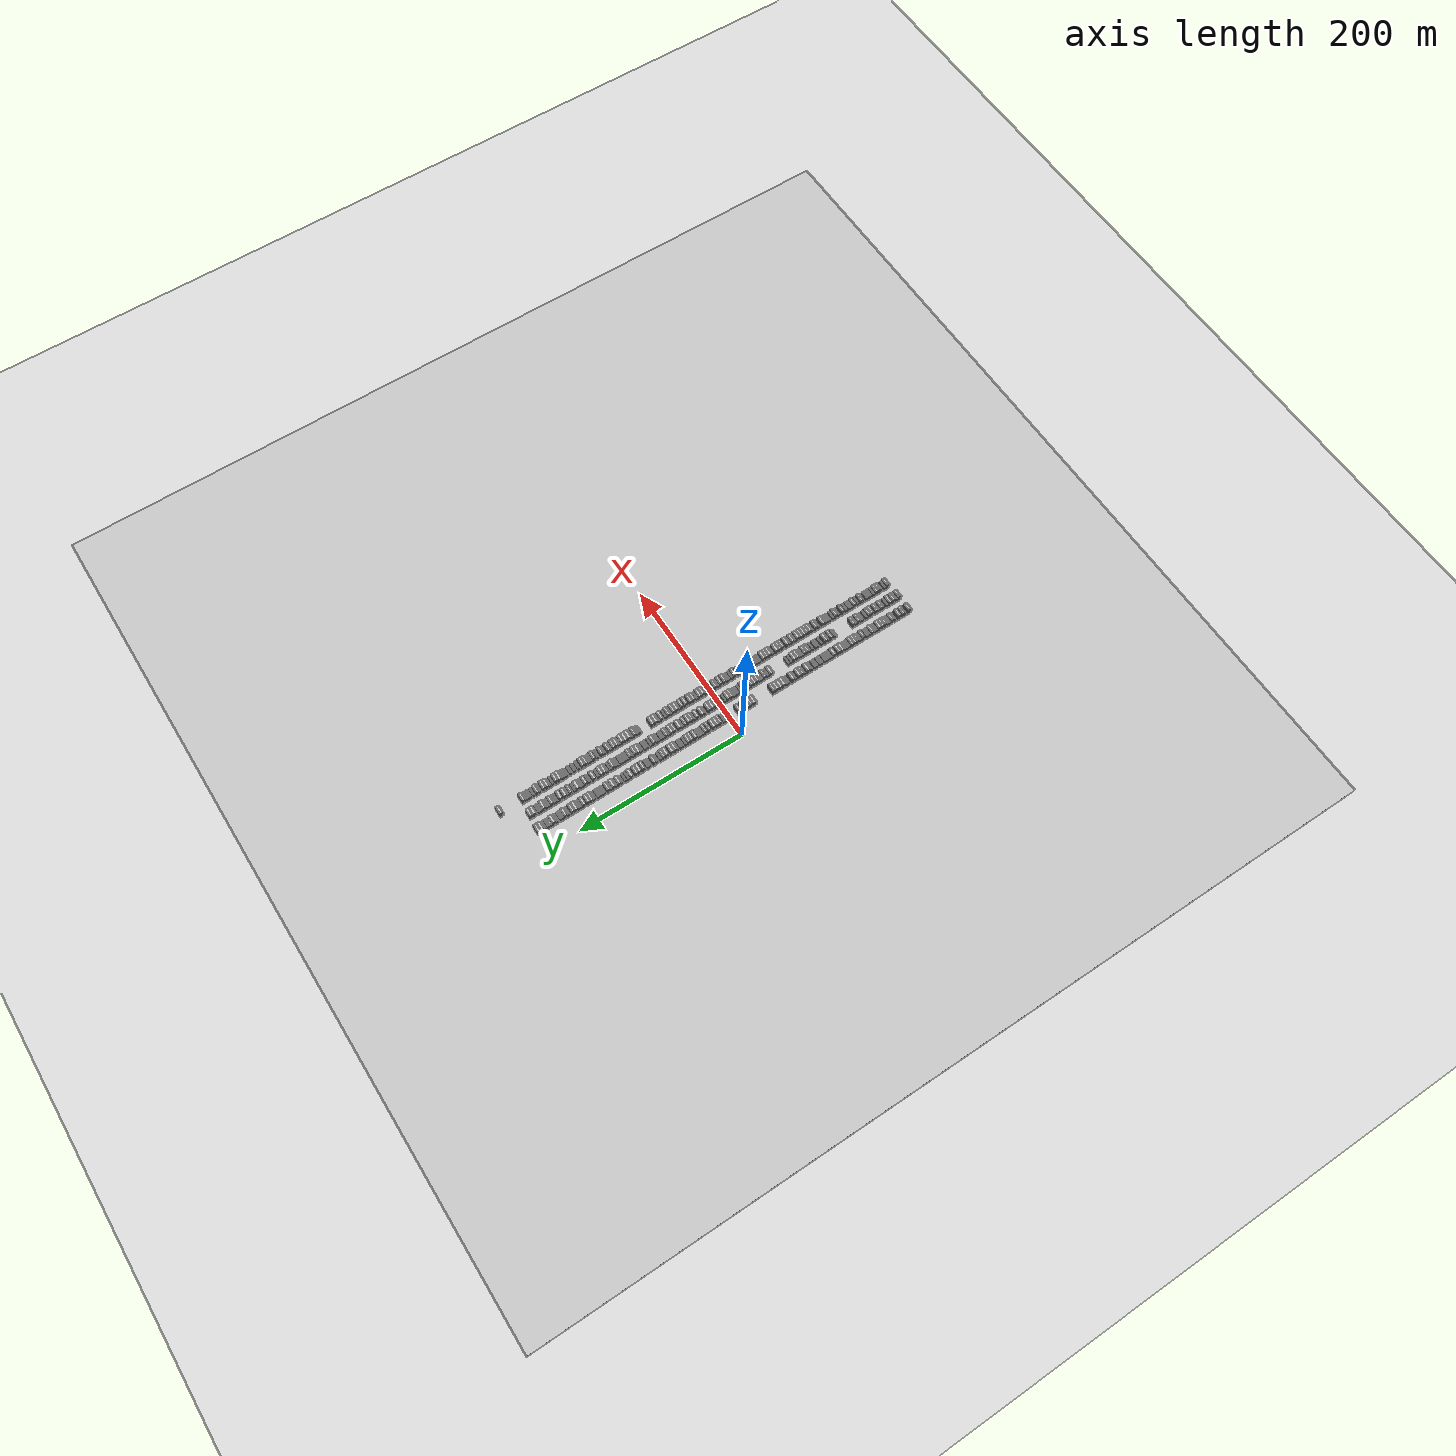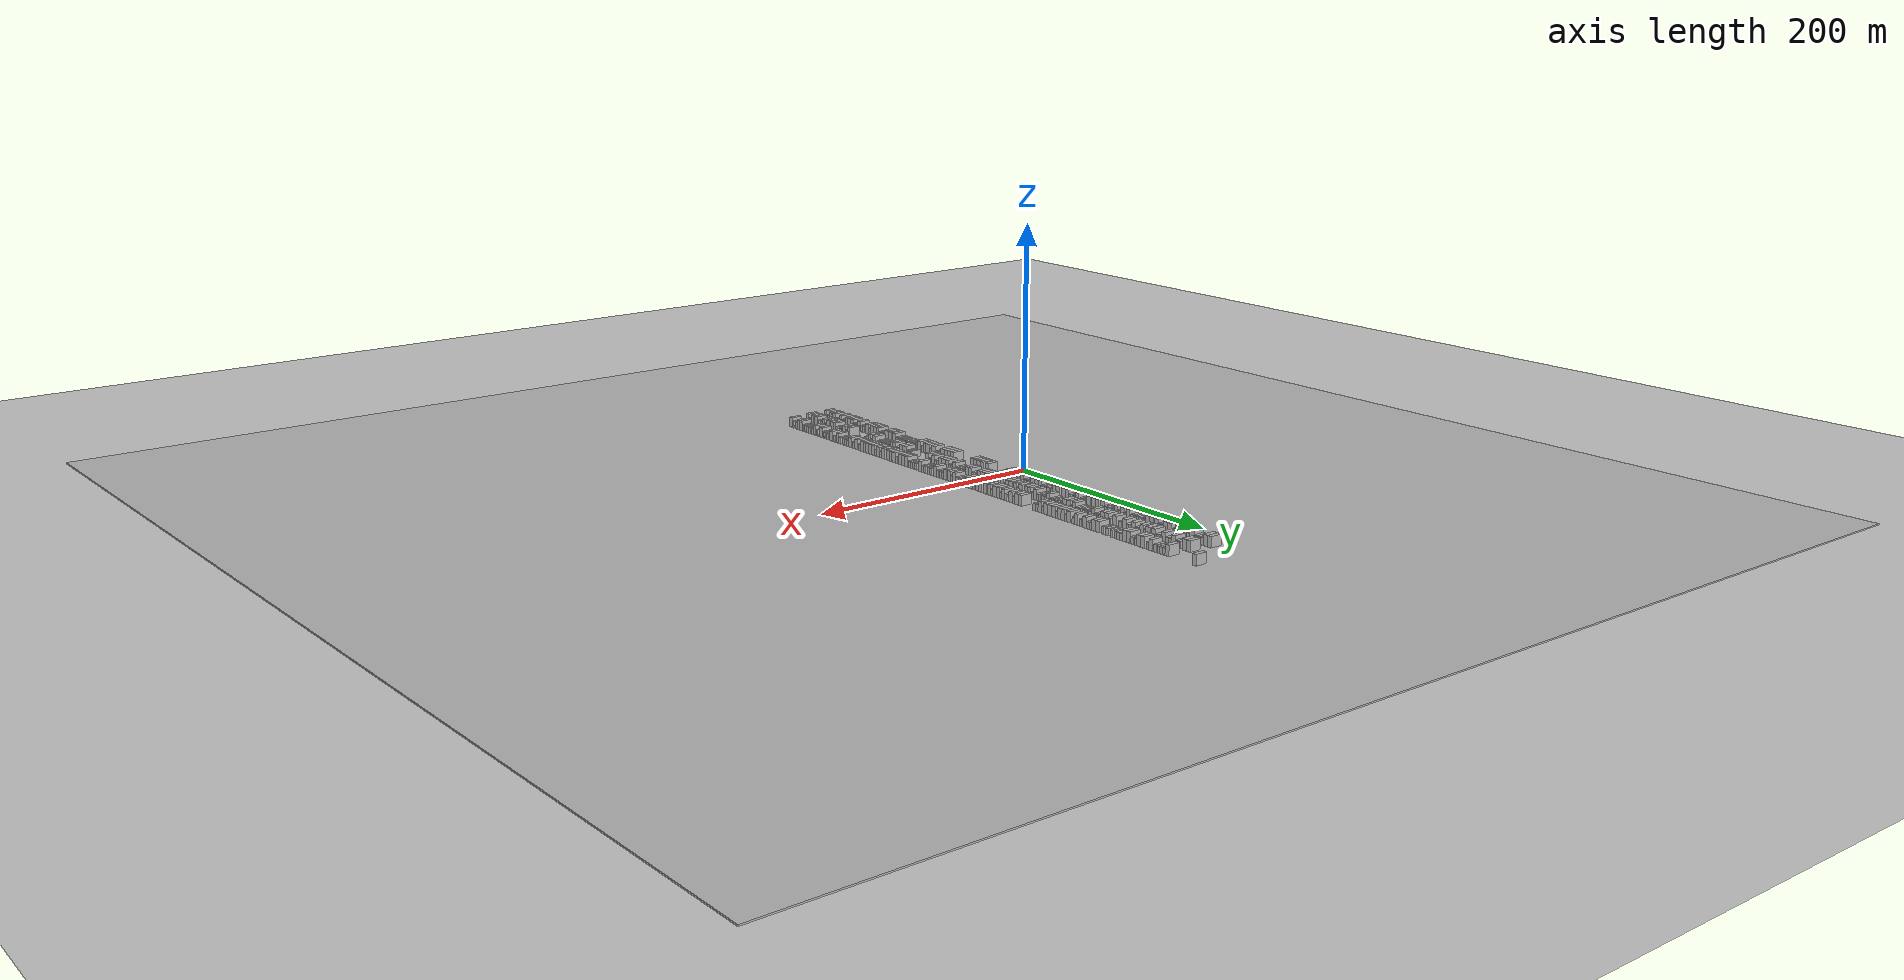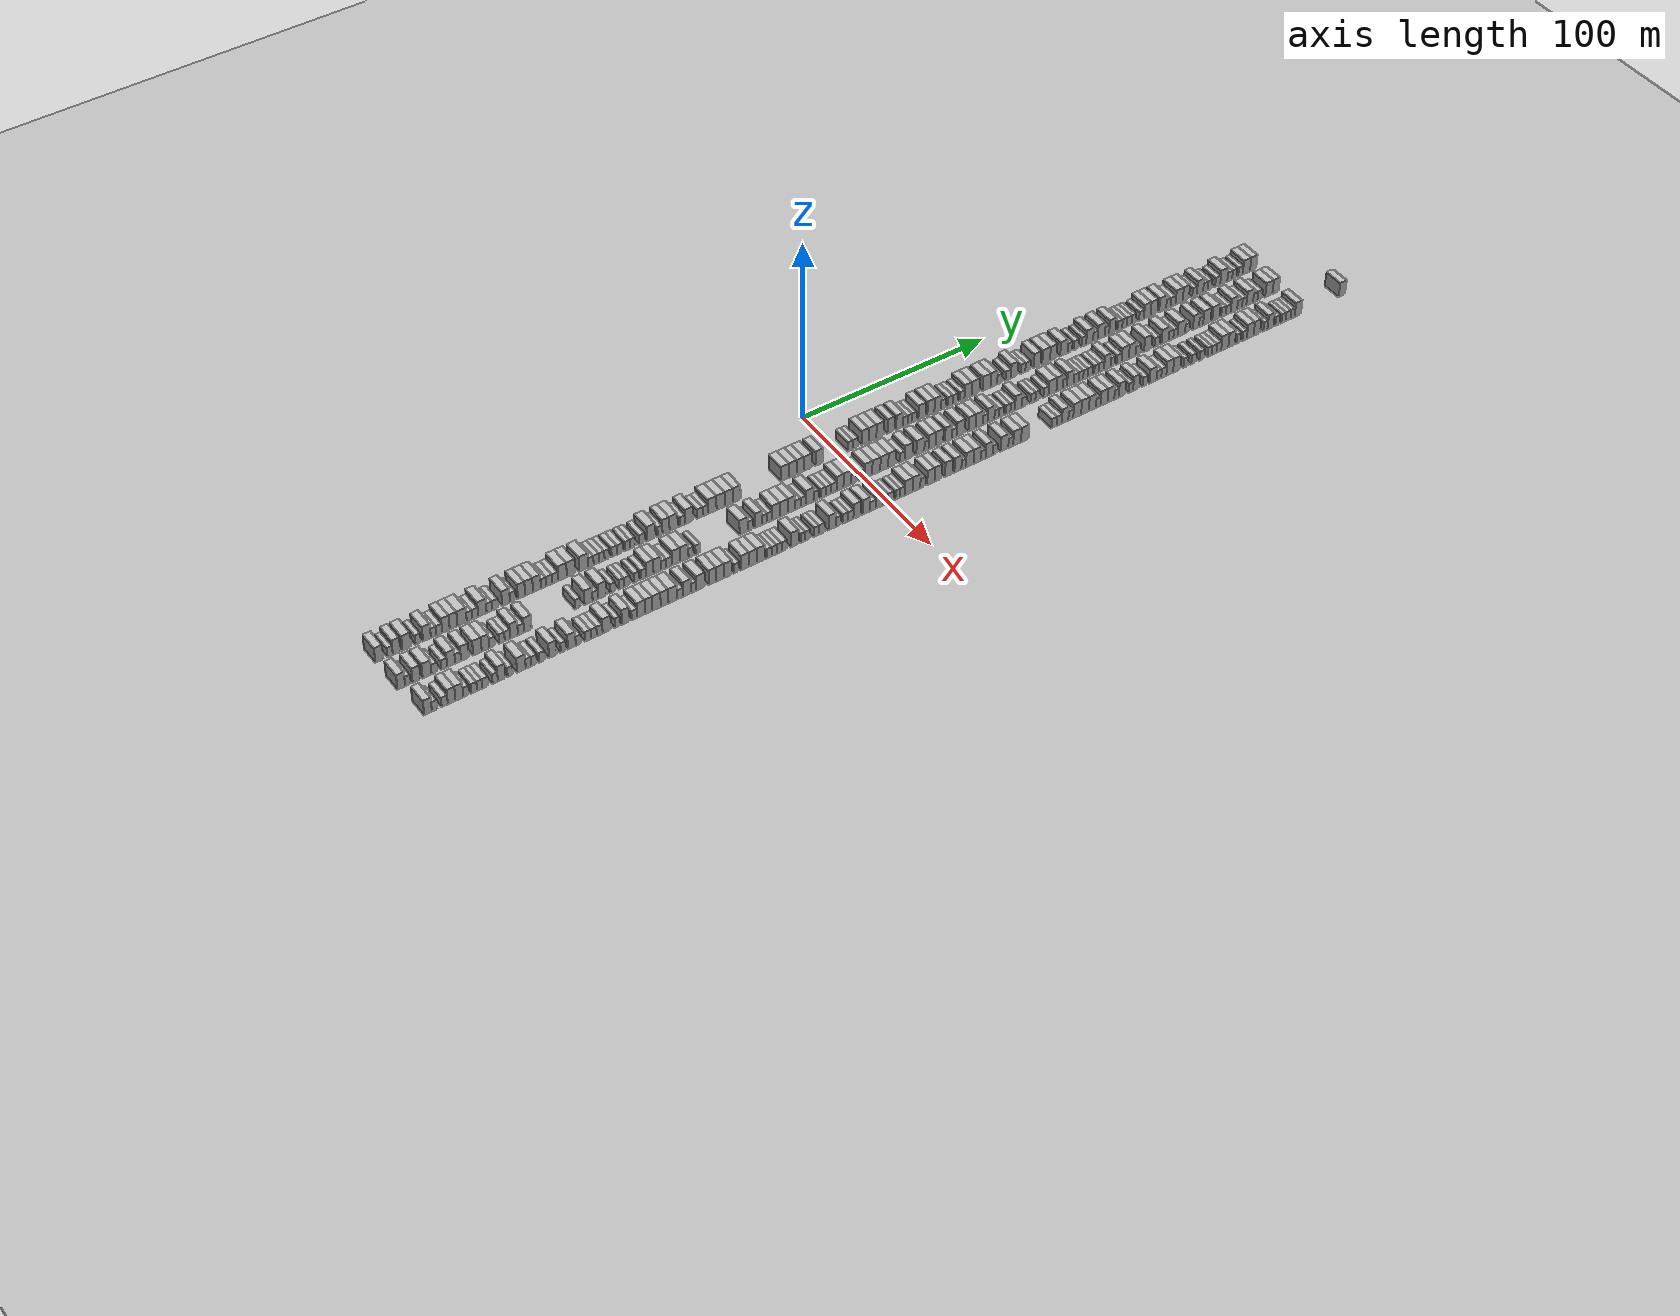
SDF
<?xml version="1.0" encoding="utf-8"?>

<sdf version="1.6">

   <world name="default">

      <gui fullscreen="0">

         <camera name="user_camera">

            <pose>-15 0 4.57585 0 0 0</pose>

            <view_controller>orbit</view_controller>

         </camera>

      </gui>

      <scene>

         <sky>

           <clouds>

             <speed>12</speed>

           </clouds>

         </sky>

         <ambient>0.4 0.4 0.4 1</ambient>

         <background>0.7 0.7 0.7 1</background>

         <shadows>1</shadows>

      </scene>

      <gravity>0 0 -9.8066</gravity>

      <magnetic_field>6e-06 2.3e-05 -4.2e-05</magnetic_field>

      <physics default="0" name="default_physics" type="ode">

         <ode>

            <solver>

               <type>quick</type>

               <iters>10</iters>

               <sor>1.0</sor>

               <use_dynamic_moi_rescaling>0</use_dynamic_moi_rescaling>

            </solver>

            <constraints>

               <cfm>0</cfm>

               <erp>0.2</erp>

               <contact_max_correcting_vel>100</contact_max_correcting_vel>

               <contact_surface_layer>0.001</contact_surface_layer>

            </constraints>

         </ode>

         <max_step_size>0.004</max_step_size>

         <real_time_factor>1</real_time_factor>

         <real_time_update_rate>250</real_time_update_rate>

      </physics>

      <light name="sun" type="directional">

         <cast_shadows>1</cast_shadows>

         <pose>0 0 10 0 0 0</pose>

         <diffuse>0.8 0.8 0.8 1</diffuse>

         <specular>0.2 0.2 0.2 1</specular>

         <attenuation>

            <range>1000</range>

            <constant>0.9</constant>

            <linear>0.01</linear>

            <quadratic>0.001</quadratic>

         </attenuation>

         <direction>-0.5 0.1 -0.9</direction>

      </light>

      <include>

         <name>ground_plane_1</name>

         <uri>model://HANNAS_ground_plane</uri>

         <pose>0 0 0  0 0 0</pose>

      </include>

      <include>

         <name>ground_plane_2</name>

         <uri>model://HANNAS_ground_plane</uri>

         <pose>100 0 0  0 0 0</pose>

      </include>

      <model name="building_1">

         <static>1</static>

         <pose frame="">25.0000 -234.1049 0 0.000000 0.000000 0.000000</pose>

         <link name="link">

            <pose frame="">0 0 4.50 0 0 0</pose>

            <collision name="collision">

               <geometry>

                  <box>

                     <size>10.0000 3.7902 9.0000</size>

                  </box>

               </geometry>

               <max_contacts>10</max_contacts>

               <surface>

                  <contact>

                     <ode/>

                  </contact>

                  <bounce/>

                  <friction>

                     <torsional>

                        <ode/>

                     </torsional>

                     <ode/>

                  </friction>

               </surface>

            </collision>

            <visual name="visual">

               <cast_shadows>0</cast_shadows>

               <geometry>

                  <box>

                     <size>10.0000 3.7902 9.0000</size>

                  </box>

               </geometry>

               <material>

                  <script>

                     <uri>model://HANNAS_wall/materials/scripts</uri>

                     <uri>model://HANNAS_wall/materials/textures</uri>

                     <name>vrc/HANNAS_wall</name>

                  </script>

               </material>

            </visual>

            <self_collide>0</self_collide>

            <enable_wind>0</enable_wind>

            <kinematic>0</kinematic>

         </link>

      </model>

      <model name="building_2">

         <static>1</static>

         <pose frame="">25.0000 -228.9686 0 0.000000 0.000000 0.000000</pose>

         <link name="link">

            <pose frame="">0 0 3.00 0 0 0</pose>

            <collision name="collision">

               <geometry>

                  <box>

                     <size>10.0000 2.4824 6.0000</size>

                  </box>

               </geometry>

               <max_contacts>10</max_contacts>

               <surface>

                  <contact>

                     <ode/>

                  </contact>

                  <bounce/>

                  <friction>

                     <torsional>

                        <ode/>

                     </torsional>

                     <ode/>

                  </friction>

               </surface>

            </collision>

            <visual name="visual">

               <cast_shadows>0</cast_shadows>

               <geometry>

                  <box>

                     <size>10.0000 2.4824 6.0000</size>

                  </box>

               </geometry>

               <material>

                  <script>

                     <uri>model://HANNAS_wall/materials/scripts</uri>

                     <uri>model://HANNAS_wall/materials/textures</uri>

                     <name>vrc/HANNAS_wall</name>

                  </script>

               </material>

            </visual>

            <self_collide>0</self_collide>

            <enable_wind>0</enable_wind>

            <kinematic>0</kinematic>

         </link>

      </model>

      <model name="building_3">

         <static>1</static>

         <pose frame="">25.0000 -225.8996 0 0.000000 0.000000 0.000000</pose>

         <link name="link">

            <pose frame="">0 0 4.50 0 0 0</pose>

            <collision name="collision">

               <geometry>

                  <box>

                     <size>10.0000 3.6556 9.0000</size>

                  </box>

               </geometry>

               <max_contacts>10</max_contacts>

               <surface>

                  <contact>

                     <ode/>

                  </contact>

                  <bounce/>

                  <friction>

                     <torsional>

                        <ode/>

                     </torsional>

                     <ode/>

                  </friction>

               </surface>

            </collision>

            <visual name="visual">

               <cast_shadows>0</cast_shadows>

               <geometry>

                  <box>

                     <size>10.0000 3.6556 9.0000</size>

                  </box>

               </geometry>

               <material>

                  <script>

                     <uri>model://HANNAS_wall/materials/scripts</uri>

                     <uri>model://HANNAS_wall/materials/textures</uri>

                     <name>vrc/HANNAS_wall</name>

                  </script>

               </material>

            </visual>

            <self_collide>0</self_collide>

            <enable_wind>0</enable_wind>

            <kinematic>0</kinematic>

         </link>

      </model>

      <model name="building_4">

         <static>1</static>

         <pose frame="">25.0000 -220.9439 0 0.000000 0.000000 0.000000</pose>

         <link name="link">

            <pose frame="">0 0 4.50 0 0 0</pose>

            <collision name="collision">

               <geometry>

                  <box>

                     <size>10.0000 4.2559 9.0000</size>

                  </box>

               </geometry>

               <max_contacts>10</max_contacts>

               <surface>

                  <contact>

                     <ode/>

                  </contact>

                  <bounce/>

                  <friction>

                     <torsional>

                        <ode/>

                     </torsional>

                     <ode/>

                  </friction>

               </surface>

            </collision>

            <visual name="visual">

               <cast_shadows>0</cast_shadows>

               <geometry>

                  <box>

                     <size>10.0000 4.2559 9.0000</size>

                  </box>

               </geometry>

               <material>

                  <script>

                     <uri>model://HANNAS_wall/materials/scripts</uri>

                     <uri>model://HANNAS_wall/materials/textures</uri>

                     <name>vrc/HANNAS_wall</name>

                  </script>

               </material>

            </visual>

            <self_collide>0</self_collide>

            <enable_wind>0</enable_wind>

            <kinematic>0</kinematic>

         </link>

      </model>

      <model name="building_5">

         <static>1</static>

         <pose frame="">25.0000 -215.5055 0 0.000000 0.000000 0.000000</pose>

         <link name="link">

            <pose frame="">0 0 3.00 0 0 0</pose>

            <collision name="collision">

               <geometry>

                  <box>

                     <size>10.0000 2.6209 6.0000</size>

                  </box>

               </geometry>

               <max_contacts>10</max_contacts>

               <surface>

                  <contact>

                     <ode/>

                  </contact>

                  <bounce/>

                  <friction>

                     <torsional>

                        <ode/>

                     </torsional>

                     <ode/>

                  </friction>

               </surface>

            </collision>

            <visual name="visual">

               <cast_shadows>0</cast_shadows>

               <geometry>

                  <box>

                     <size>10.0000 2.6209 6.0000</size>

                  </box>

               </geometry>

               <material>

                  <script>

                     <uri>model://HANNAS_wall/materials/scripts</uri>

                     <uri>model://HANNAS_wall/materials/textures</uri>

                     <name>vrc/HANNAS_wall</name>

                  </script>

               </material>

            </visual>

            <self_collide>0</self_collide>

            <enable_wind>0</enable_wind>

            <kinematic>0</kinematic>

         </link>

      </model>

      <model name="building_6">

         <static>1</static>

         <pose frame="">25.0000 -211.3009 0 0.000000 0.000000 0.000000</pose>

         <link name="link">

            <pose frame="">0 0 4.50 0 0 0</pose>

            <collision name="collision">

               <geometry>

                  <box>

                     <size>10.0000 3.7882 9.0000</size>

                  </box>

               </geometry>

               <max_contacts>10</max_contacts>

               <surface>

                  <contact>

                     <ode/>

                  </contact>

                  <bounce/>

                  <friction>

                     <torsional>

                        <ode/>

                     </torsional>

                     <ode/>

                  </friction>

               </surface>

            </collision>

            <visual name="visual">

               <cast_shadows>0</cast_shadows>

               <geometry>

                  <box>

                     <size>10.0000 3.7882 9.0000</size>

                  </box>

               </geometry>

               <material>

                  <script>

                     <uri>model://HANNAS_wall/materials/scripts</uri>

                     <uri>model://HANNAS_wall/materials/textures</uri>

                     <name>vrc/HANNAS_wall</name>

                  </script>

               </material>

            </visual>

            <self_collide>0</self_collide>

            <enable_wind>0</enable_wind>

            <kinematic>0</kinematic>

         </link>

      </model>

      <model name="building_7">

         <static>1</static>

         <pose frame="">25.0000 -208.0643 0 0.000000 0.000000 0.000000</pose>

         <link name="link">

            <pose frame="">0 0 3.00 0 0 0</pose>

            <collision name="collision">

               <geometry>

                  <box>

                     <size>10.0000 2.6851 6.0000</size>

                  </box>

               </geometry>

               <max_contacts>10</max_contacts>

               <surface>

                  <contact>

                     <ode/>

                  </contact>

                  <bounce/>

                  <friction>

                     <torsional>

                        <ode/>

                     </torsional>

                     <ode/>

                  </friction>

               </surface>

            </collision>

            <visual name="visual">

               <cast_shadows>0</cast_shadows>

               <geometry>

                  <box>

                     <size>10.0000 2.6851 6.0000</size>

                  </box>

               </geometry>

               <material>

                  <script>

                     <uri>model://HANNAS_wall/materials/scripts</uri>

                     <uri>model://HANNAS_wall/materials/textures</uri>

                     <name>vrc/HANNAS_wall</name>

                  </script>

               </material>

            </visual>

            <self_collide>0</self_collide>

            <enable_wind>0</enable_wind>

            <kinematic>0</kinematic>

         </link>

      </model>

      <model name="building_8">

         <static>1</static>

         <pose frame="">25.0000 -205.3315 0 0.000000 0.000000 0.000000</pose>

         <link name="link">

            <pose frame="">0 0 3.00 0 0 0</pose>

            <collision name="collision">

               <geometry>

                  <box>

                     <size>10.0000 2.7805 6.0000</size>

                  </box>

               </geometry>

               <max_contacts>10</max_contacts>

               <surface>

                  <contact>

                     <ode/>

                  </contact>

                  <bounce/>

                  <friction>

                     <torsional>

                        <ode/>

                     </torsional>

                     <ode/>

                  </friction>

               </surface>

            </collision>

            <visual name="visual">

               <cast_shadows>0</cast_shadows>

               <geometry>

                  <box>

                     <size>10.0000 2.7805 6.0000</size>

                  </box>

               </geometry>

               <material>

                  <script>

                     <uri>model://HANNAS_wall/materials/scripts</uri>

                     <uri>model://HANNAS_wall/materials/textures</uri>

                     <name>vrc/HANNAS_wall</name>

                  </script>

               </material>

            </visual>

            <self_collide>0</self_collide>

            <enable_wind>0</enable_wind>

            <kinematic>0</kinematic>

         </link>

      </model>

      <model name="building_9">

         <static>1</static>

         <pose frame="">25.0000 -202.1189 0 0.000000 0.000000 0.000000</pose>

         <link name="link">

            <pose frame="">0 0 4.50 0 0 0</pose>

            <collision name="collision">

               <geometry>

                  <box>

                     <size>10.0000 3.6448 9.0000</size>

                  </box>

               </geometry>

               <max_contacts>10</max_contacts>

               <surface>

                  <contact>

                     <ode/>

                  </contact>

                  <bounce/>

                  <friction>

                     <torsional>

                        <ode/>

                     </torsional>

                     <ode/>

                  </friction>

               </surface>

            </collision>

            <visual name="visual">

               <cast_shadows>0</cast_shadows>

               <geometry>

                  <box>

                     <size>10.0000 3.6448 9.0000</size>

                  </box>

               </geometry>

               <material>

                  <script>

                     <uri>model://HANNAS_wall/materials/scripts</uri>

                     <uri>model://HANNAS_wall/materials/textures</uri>

                     <name>vrc/HANNAS_wall</name>

                  </script>

               </material>

            </visual>

            <self_collide>0</self_collide>

            <enable_wind>0</enable_wind>

            <kinematic>0</kinematic>

         </link>

      </model>

      <model name="building_10">

         <static>1</static>

         <pose frame="">25.0000 -198.4157 0 0.000000 0.000000 0.000000</pose>

         <link name="link">

            <pose frame="">0 0 4.50 0 0 0</pose>

            <collision name="collision">

               <geometry>

                  <box>

                     <size>10.0000 3.7617 9.0000</size>

                  </box>

               </geometry>

               <max_contacts>10</max_contacts>

               <surface>

                  <contact>

                     <ode/>

                  </contact>

                  <bounce/>

                  <friction>

                     <torsional>

                        <ode/>

                     </torsional>

                     <ode/>

                  </friction>

               </surface>

            </collision>

            <visual name="visual">

               <cast_shadows>0</cast_shadows>

               <geometry>

                  <box>

                     <size>10.0000 3.7617 9.0000</size>

                  </box>

               </geometry>

               <material>

                  <script>

                     <uri>model://HANNAS_wall/materials/scripts</uri>

                     <uri>model://HANNAS_wall/materials/textures</uri>

                     <name>vrc/HANNAS_wall</name>

                  </script>

               </material>

            </visual>

            <self_collide>0</self_collide>

            <enable_wind>0</enable_wind>

            <kinematic>0</kinematic>

         </link>

      </model>

      <model name="building_11">

         <static>1</static>

         <pose frame="">25.0000 -194.2861 0 0.000000 0.000000 0.000000</pose>

         <link name="link">

            <pose frame="">0 0 4.50 0 0 0</pose>

            <collision name="collision">

               <geometry>

                  <box>

                     <size>10.0000 4.4974 9.0000</size>

                  </box>

               </geometry>

               <max_contacts>10</max_contacts>

               <surface>

                  <contact>

                     <ode/>

                  </contact>

                  <bounce/>

                  <friction>

                     <torsional>

                        <ode/>

                     </torsional>

                     <ode/>

                  </friction>

               </surface>

            </collision>

            <visual name="visual">

               <cast_shadows>0</cast_shadows>

               <geometry>

                  <box>

                     <size>10.0000 4.4974 9.0000</size>

                  </box>

               </geometry>

               <material>

                  <script>

                     <uri>model://HANNAS_wall/materials/scripts</uri>

                     <uri>model://HANNAS_wall/materials/textures</uri>

                     <name>vrc/HANNAS_wall</name>

                  </script>

               </material>

            </visual>

            <self_collide>0</self_collide>

            <enable_wind>0</enable_wind>

            <kinematic>0</kinematic>

         </link>

      </model>

      <model name="building_12">

         <static>1</static>

         <pose frame="">25.0000 -190.6346 0 0.000000 0.000000 0.000000</pose>

         <link name="link">

            <pose frame="">0 0 3.00 0 0 0</pose>

            <collision name="collision">

               <geometry>

                  <box>

                     <size>10.0000 2.8056 6.0000</size>

                  </box>

               </geometry>

               <max_contacts>10</max_contacts>

               <surface>

                  <contact>

                     <ode/>

                  </contact>

                  <bounce/>

                  <friction>

                     <torsional>

                        <ode/>

                     </torsional>

                     <ode/>

                  </friction>

               </surface>

            </collision>

            <visual name="visual">

               <cast_shadows>0</cast_shadows>

               <geometry>

                  <box>

                     <size>10.0000 2.8056 6.0000</size>

                  </box>

               </geometry>

               <material>

                  <script>

                     <uri>model://HANNAS_wall/materials/scripts</uri>

                     <uri>model://HANNAS_wall/materials/textures</uri>

                     <name>vrc/HANNAS_wall</name>

                  </script>

               </material>

            </visual>

            <self_collide>0</self_collide>

            <enable_wind>0</enable_wind>

            <kinematic>0</kinematic>

         </link>

      </model>

      <model name="building_13">

         <static>1</static>

         <pose frame="">25.0000 -187.8267 0 0.000000 0.000000 0.000000</pose>

         <link name="link">

            <pose frame="">0 0 3.00 0 0 0</pose>

            <collision name="collision">

               <geometry>

                  <box>

                     <size>10.0000 2.8101 6.0000</size>

                  </box>

               </geometry>

               <max_contacts>10</max_contacts>

               <surface>

                  <contact>

                     <ode/>

                  </contact>

                  <bounce/>

                  <friction>

                     <torsional>

                        <ode/>

                     </torsional>

                     <ode/>

                  </friction>

               </surface>

            </collision>

            <visual name="visual">

               <cast_shadows>0</cast_shadows>

               <geometry>

                  <box>

                     <size>10.0000 2.8101 6.0000</size>

                  </box>

               </geometry>

               <material>

                  <script>

                     <uri>model://HANNAS_wall/materials/scripts</uri>

                     <uri>model://HANNAS_wall/materials/textures</uri>

                     <name>vrc/HANNAS_wall</name>

                  </script>

               </material>

            </visual>

            <self_collide>0</self_collide>

            <enable_wind>0</enable_wind>

            <kinematic>0</kinematic>

         </link>

      </model>

      <model name="building_14">

         <static>1</static>

         <pose frame="">25.0000 -184.3808 0 0.000000 0.000000 0.000000</pose>

         <link name="link">

            <pose frame="">0 0 4.50 0 0 0</pose>

            <collision name="collision">

               <geometry>

                  <box>

                     <size>10.0000 4.0818 9.0000</size>

                  </box>

               </geometry>

               <max_contacts>10</max_contacts>

               <surface>

                  <contact>

                     <ode/>

                  </contact>

                  <bounce/>

                  <friction>

                     <torsional>

                        <ode/>

                     </torsional>

                     <ode/>

                  </friction>

               </surface>

            </collision>

            <visual name="visual">

               <cast_shadows>0</cast_shadows>

               <geometry>

                  <box>

                     <size>10.0000 4.0818 9.0000</size>

                  </box>

               </geometry>

               <material>

                  <script>

                     <uri>model://HANNAS_wall/materials/scripts</uri>

                     <uri>model://HANNAS_wall/materials/textures</uri>

                     <name>vrc/HANNAS_wall</name>

                  </script>

               </material>

            </visual>

            <self_collide>0</self_collide>

            <enable_wind>0</enable_wind>

            <kinematic>0</kinematic>

         </link>

      </model>

      <model name="building_15">

         <static>1</static>

         <pose frame="">25.0000 -180.9060 0 0.000000 0.000000 0.000000</pose>

         <link name="link">

            <pose frame="">0 0 3.00 0 0 0</pose>

            <collision name="collision">

               <geometry>

                  <box>

                     <size>10.0000 2.8676 6.0000</size>

                  </box>

               </geometry>

               <max_contacts>10</max_contacts>

               <surface>

                  <contact>

                     <ode/>

                  </contact>

                  <bounce/>

                  <friction>

                     <torsional>

                        <ode/>

                     </torsional>

                     <ode/>

                  </friction>

               </surface>

            </collision>

            <visual name="visual">

               <cast_shadows>0</cast_shadows>

               <geometry>

                  <box>

                     <size>10.0000 2.8676 6.0000</size>

                  </box>

               </geometry>

               <material>

                  <script>

                     <uri>model://HANNAS_wall/materials/scripts</uri>

                     <uri>model://HANNAS_wall/materials/textures</uri>

                     <name>vrc/HANNAS_wall</name>

                  </script>

               </material>

            </visual>

            <self_collide>0</self_collide>

            <enable_wind>0</enable_wind>

            <kinematic>0</kinematic>

         </link>

      </model>

      <model name="building_16">

         <static>1</static>

         <pose frame="">25.0000 -178.0549 0 0.000000 0.000000 0.000000</pose>

         <link name="link">

            <pose frame="">0 0 3.00 0 0 0</pose>

            <collision name="collision">

               <geometry>

                  <box>

                     <size>10.0000 2.8347 6.0000</size>

                  </box>

               </geometry>

               <max_contacts>10</max_contacts>

               <surface>

                  <contact>

                     <ode/>

                  </contact>

                  <bounce/>

                  <friction>

                     <torsional>

                        <ode/>

                     </torsional>

                     <ode/>

                  </friction>

               </surface>

            </collision>

            <visual name="visual">

               <cast_shadows>0</cast_shadows>

               <geometry>

                  <box>

                     <size>10.0000 2.8347 6.0000</size>

                  </box>

               </geometry>

               <material>

                  <script>

                     <uri>model://HANNAS_wall/materials/scripts</uri>

                     <uri>model://HANNAS_wall/materials/textures</uri>

                     <name>vrc/HANNAS_wall</name>

                  </script>

               </material>

            </visual>

            <self_collide>0</self_collide>

            <enable_wind>0</enable_wind>

            <kinematic>0</kinematic>

         </link>

      </model>

      <model name="building_17">

         <static>1</static>

         <pose frame="">25.0000 -172.7347 0 0.000000 0.000000 0.000000</pose>

         <link name="link">

            <pose frame="">0 0 4.50 0 0 0</pose>

            <collision name="collision">

               <geometry>

                  <box>

                     <size>10.0000 3.8056 9.0000</size>

                  </box>

               </geometry>

               <max_contacts>10</max_contacts>

               <surface>

                  <contact>

                     <ode/>

                  </contact>

                  <bounce/>

                  <friction>

                     <torsional>

                        <ode/>

                     </torsional>

                     <ode/>

                  </friction>

               </surface>

            </collision>

            <visual name="visual">

               <cast_shadows>0</cast_shadows>

               <geometry>

                  <box>

                     <size>10.0000 3.8056 9.0000</size>

                  </box>

               </geometry>

               <material>

                  <script>

                     <uri>model://HANNAS_wall/materials/scripts</uri>

                     <uri>model://HANNAS_wall/materials/textures</uri>

                     <name>vrc/HANNAS_wall</name>

                  </script>

               </material>

            </visual>

            <self_collide>0</self_collide>

            <enable_wind>0</enable_wind>

            <kinematic>0</kinematic>

         </link>

      </model>

      <model name="building_18">

         <static>1</static>

         <pose frame="">25.0000 -169.3702 0 0.000000 0.000000 0.000000</pose>

         <link name="link">

            <pose frame="">0 0 3.00 0 0 0</pose>

            <collision name="collision">

               <geometry>

                  <box>

                     <size>10.0000 2.9234 6.0000</size>

                  </box>

               </geometry>

               <max_contacts>10</max_contacts>

               <surface>

                  <contact>

                     <ode/>

                  </contact>

                  <bounce/>

                  <friction>

                     <torsional>

                        <ode/>

                     </torsional>

                     <ode/>

                  </friction>

               </surface>

            </collision>

            <visual name="visual">

               <cast_shadows>0</cast_shadows>

               <geometry>

                  <box>

                     <size>10.0000 2.9234 6.0000</size>

                  </box>

               </geometry>

               <material>

                  <script>

                     <uri>model://HANNAS_wall/materials/scripts</uri>

                     <uri>model://HANNAS_wall/materials/textures</uri>

                     <name>vrc/HANNAS_wall</name>

                  </script>

               </material>

            </visual>

            <self_collide>0</self_collide>

            <enable_wind>0</enable_wind>

            <kinematic>0</kinematic>

         </link>

      </model>

      <model name="building_19">

         <static>1</static>

         <pose frame="">25.0000 -165.1060 0 0.000000 0.000000 0.000000</pose>

         <link name="link">

            <pose frame="">0 0 4.50 0 0 0</pose>

            <collision name="collision">

               <geometry>

                  <box>

                     <size>10.0000 3.6051 9.0000</size>

                  </box>

               </geometry>

               <max_contacts>10</max_contacts>

               <surface>

                  <contact>

                     <ode/>

                  </contact>

                  <bounce/>

                  <friction>

                     <torsional>

                        <ode/>

                     </torsional>

                     <ode/>

                  </friction>

               </surface>

            </collision>

            <visual name="visual">

               <cast_shadows>0</cast_shadows>

               <geometry>

                  <box>

                     <size>10.0000 3.6051 9.0000</size>

                  </box>

               </geometry>

               <material>

                  <script>

                     <uri>model://HANNAS_wall/materials/scripts</uri>

                     <uri>model://HANNAS_wall/materials/textures</uri>

                     <name>vrc/HANNAS_wall</name>

                  </script>

               </material>

            </visual>

            <self_collide>0</self_collide>

            <enable_wind>0</enable_wind>

            <kinematic>0</kinematic>

         </link>

      </model>

      <model name="building_20">

         <static>1</static>

         <pose frame="">25.0000 -161.3523 0 0.000000 0.000000 0.000000</pose>

         <link name="link">

            <pose frame="">0 0 4.50 0 0 0</pose>

            <collision name="collision">

               <geometry>

                  <box>

                     <size>10.0000 3.9022 9.0000</size>

                  </box>

               </geometry>

               <max_contacts>10</max_contacts>

               <surface>

                  <contact>

                     <ode/>

                  </contact>

                  <bounce/>

                  <friction>

                     <torsional>

                        <ode/>

                     </torsional>

                     <ode/>

                  </friction>

               </surface>

            </collision>

            <visual name="visual">

               <cast_shadows>0</cast_shadows>

               <geometry>

                  <box>

                     <size>10.0000 3.9022 9.0000</size>

                  </box>

               </geometry>

               <material>

                  <script>

                     <uri>model://HANNAS_wall/materials/scripts</uri>

                     <uri>model://HANNAS_wall/materials/textures</uri>

                     <name>vrc/HANNAS_wall</name>

                  </script>

               </material>

            </visual>

            <self_collide>0</self_collide>

            <enable_wind>0</enable_wind>

            <kinematic>0</kinematic>

         </link>

      </model>

      <model name="building_21">

         <static>1</static>

         <pose frame="">25.0000 -157.4447 0 0.000000 0.000000 0.000000</pose>

         <link name="link">

            <pose frame="">0 0 4.50 0 0 0</pose>

            <collision name="collision">

               <geometry>

                  <box>

                     <size>10.0000 3.9131 9.0000</size>

                  </box>

               </geometry>

               <max_contacts>10</max_contacts>

               <surface>

                  <contact>

                     <ode/>

                  </contact>

                  <bounce/>

                  <friction>

                     <torsional>

                        <ode/>

                     </torsional>

                     <ode/>

                  </friction>

               </surface>

            </collision>

            <visual name="visual">

               <cast_shadows>0</cast_shadows>

               <geometry>

                  <box>

                     <size>10.0000 3.9131 9.0000</size>

                  </box>

               </geometry>

               <material>

                  <script>

                     <uri>model://HANNAS_wall/materials/scripts</uri>

                     <uri>model://HANNAS_wall/materials/textures</uri>

                     <name>vrc/HANNAS_wall</name>

                  </script>

               </material>

            </visual>

            <self_collide>0</self_collide>

            <enable_wind>0</enable_wind>

            <kinematic>0</kinematic>

         </link>

      </model>

      <model name="building_22">

         <static>1</static>

         <pose frame="">25.0000 -154.1215 0 0.000000 0.000000 0.000000</pose>

         <link name="link">

            <pose frame="">0 0 3.00 0 0 0</pose>

            <collision name="collision">

               <geometry>

                  <box>

                     <size>10.0000 2.7331 6.0000</size>

                  </box>

               </geometry>

               <max_contacts>10</max_contacts>

               <surface>

                  <contact>

                     <ode/>

                  </contact>

                  <bounce/>

                  <friction>

                     <torsional>

                        <ode/>

                     </torsional>

                     <ode/>

                  </friction>

               </surface>

            </collision>

            <visual name="visual">

               <cast_shadows>0</cast_shadows>

               <geometry>

                  <box>

                     <size>10.0000 2.7331 6.0000</size>

                  </box>

               </geometry>

               <material>

                  <script>

                     <uri>model://HANNAS_wall/materials/scripts</uri>

                     <uri>model://HANNAS_wall/materials/textures</uri>

                     <name>vrc/HANNAS_wall</name>

                  </script>

               </material>

            </visual>

            <self_collide>0</self_collide>

            <enable_wind>0</enable_wind>

            <kinematic>0</kinematic>

         </link>

      </model>

      <model name="building_23">

         <static>1</static>

         <pose frame="">25.0000 -151.2826 0 0.000000 0.000000 0.000000</pose>

         <link name="link">

            <pose frame="">0 0 3.00 0 0 0</pose>

            <collision name="collision">

               <geometry>

                  <box>

                     <size>10.0000 2.9448 6.0000</size>

                  </box>

               </geometry>

               <max_contacts>10</max_contacts>

               <surface>

                  <contact>

                     <ode/>

                  </contact>

                  <bounce/>

                  <friction>

                     <torsional>

                        <ode/>

                     </torsional>

                     <ode/>

                  </friction>

               </surface>

            </collision>

            <visual name="visual">

               <cast_shadows>0</cast_shadows>

               <geometry>

                  <box>

                     <size>10.0000 2.9448 6.0000</size>

                  </box>

               </geometry>

               <material>

                  <script>

                     <uri>model://HANNAS_wall/materials/scripts</uri>

                     <uri>model://HANNAS_wall/materials/textures</uri>

                     <name>vrc/HANNAS_wall</name>

                  </script>

               </material>

            </visual>

            <self_collide>0</self_collide>

            <enable_wind>0</enable_wind>

            <kinematic>0</kinematic>

         </link>

      </model>

      <model name="building_24">

         <static>1</static>

         <pose frame="">25.0000 -148.3363 0 0.000000 0.000000 0.000000</pose>

         <link name="link">

            <pose frame="">0 0 3.00 0 0 0</pose>

            <collision name="collision">

               <geometry>

                  <box>

                     <size>10.0000 2.9479 6.0000</size>

                  </box>

               </geometry>

               <max_contacts>10</max_contacts>

               <surface>

                  <contact>

                     <ode/>

                  </contact>

                  <bounce/>

                  <friction>

                     <torsional>

                        <ode/>

                     </torsional>

                     <ode/>

                  </friction>

               </surface>

            </collision>

            <visual name="visual">

               <cast_shadows>0</cast_shadows>

               <geometry>

                  <box>

                     <size>10.0000 2.9479 6.0000</size>

                  </box>

               </geometry>

               <material>

                  <script>

                     <uri>model://HANNAS_wall/materials/scripts</uri>

                     <uri>model://HANNAS_wall/materials/textures</uri>

                     <name>vrc/HANNAS_wall</name>

                  </script>

               </material>

            </visual>

            <self_collide>0</self_collide>

            <enable_wind>0</enable_wind>

            <kinematic>0</kinematic>

         </link>

      </model>

      <model name="building_25">

         <static>1</static>

         <pose frame="">25.0000 -144.6904 0 0.000000 0.000000 0.000000</pose>

         <link name="link">

            <pose frame="">0 0 4.50 0 0 0</pose>

            <collision name="collision">

               <geometry>

                  <box>

                     <size>10.0000 4.3439 9.0000</size>

                  </box>

               </geometry>

               <max_contacts>10</max_contacts>

               <surface>

                  <contact>

                     <ode/>

                  </contact>

                  <bounce/>

                  <friction>

                     <torsional>

                        <ode/>

                     </torsional>

                     <ode/>

                  </friction>

               </surface>

            </collision>

            <visual name="visual">

               <cast_shadows>0</cast_shadows>

               <geometry>

                  <box>

                     <size>10.0000 4.3439 9.0000</size>

                  </box>

               </geometry>

               <material>

                  <script>

                     <uri>model://HANNAS_wall/materials/scripts</uri>

                     <uri>model://HANNAS_wall/materials/textures</uri>

                     <name>vrc/HANNAS_wall</name>

                  </script>

               </material>

            </visual>

            <self_collide>0</self_collide>

            <enable_wind>0</enable_wind>

            <kinematic>0</kinematic>

         </link>

      </model>

      <model name="building_26">

         <static>1</static>

         <pose frame="">25.0000 -140.4186 0 0.000000 0.000000 0.000000</pose>

         <link name="link">

            <pose frame="">0 0 4.50 0 0 0</pose>

            <collision name="collision">

               <geometry>

                  <box>

                     <size>10.0000 4.1998 9.0000</size>

                  </box>

               </geometry>

               <max_contacts>10</max_contacts>

               <surface>

                  <contact>

                     <ode/>

                  </contact>

                  <bounce/>

                  <friction>

                     <torsional>

                        <ode/>

                     </torsional>

                     <ode/>

                  </friction>

               </surface>

            </collision>

            <visual name="visual">

               <cast_shadows>0</cast_shadows>

               <geometry>

                  <box>

                     <size>10.0000 4.1998 9.0000</size>

                  </box>

               </geometry>

               <material>

                  <script>

                     <uri>model://HANNAS_wall/materials/scripts</uri>

                     <uri>model://HANNAS_wall/materials/textures</uri>

                     <name>vrc/HANNAS_wall</name>

                  </script>

               </material>

            </visual>

            <self_collide>0</self_collide>

            <enable_wind>0</enable_wind>

            <kinematic>0</kinematic>

         </link>

      </model>

      <model name="building_27">

         <static>1</static>

         <pose frame="">25.0000 -134.0754 0 0.000000 0.000000 0.000000</pose>

         <link name="link">

            <pose frame="">0 0 4.50 0 0 0</pose>

            <collision name="collision">

               <geometry>

                  <box>

                     <size>10.0000 4.4864 9.0000</size>

                  </box>

               </geometry>

               <max_contacts>10</max_contacts>

               <surface>

                  <contact>

                     <ode/>

                  </contact>

                  <bounce/>

                  <friction>

                     <torsional>

                        <ode/>

                     </torsional>

                     <ode/>

                  </friction>

               </surface>

            </collision>

            <visual name="visual">

               <cast_shadows>0</cast_shadows>

               <geometry>

                  <box>

                     <size>10.0000 4.4864 9.0000</size>

                  </box>

               </geometry>

               <material>

                  <script>

                     <uri>model://HANNAS_wall/materials/scripts</uri>

                     <uri>model://HANNAS_wall/materials/textures</uri>

                     <name>vrc/HANNAS_wall</name>

                  </script>

               </material>

            </visual>

            <self_collide>0</self_collide>

            <enable_wind>0</enable_wind>

            <kinematic>0</kinematic>

         </link>

      </model>

      <model name="building_28">

         <static>1</static>

         <pose frame="">25.0000 -130.4685 0 0.000000 0.000000 0.000000</pose>

         <link name="link">

            <pose frame="">0 0 3.00 0 0 0</pose>

            <collision name="collision">

               <geometry>

                  <box>

                     <size>10.0000 2.7274 6.0000</size>

                  </box>

               </geometry>

               <max_contacts>10</max_contacts>

               <surface>

                  <contact>

                     <ode/>

                  </contact>

                  <bounce/>

                  <friction>

                     <torsional>

                        <ode/>

                     </torsional>

                     <ode/>

                  </friction>

               </surface>

            </collision>

            <visual name="visual">

               <cast_shadows>0</cast_shadows>

               <geometry>

                  <box>

                     <size>10.0000 2.7274 6.0000</size>

                  </box>

               </geometry>

               <material>

                  <script>

                     <uri>model://HANNAS_wall/materials/scripts</uri>

                     <uri>model://HANNAS_wall/materials/textures</uri>

                     <name>vrc/HANNAS_wall</name>

                  </script>

               </material>

            </visual>

            <self_collide>0</self_collide>

            <enable_wind>0</enable_wind>

            <kinematic>0</kinematic>

         </link>

      </model>

      <model name="building_29">

         <static>1</static>

         <pose frame="">25.0000 -127.7237 0 0.000000 0.000000 0.000000</pose>

         <link name="link">

            <pose frame="">0 0 3.00 0 0 0</pose>

            <collision name="collision">

               <geometry>

                  <box>

                     <size>10.0000 2.7621 6.0000</size>

                  </box>

               </geometry>

               <max_contacts>10</max_contacts>

               <surface>

                  <contact>

                     <ode/>

                  </contact>

                  <bounce/>

                  <friction>

                     <torsional>

                        <ode/>

                     </torsional>

                     <ode/>

                  </friction>

               </surface>

            </collision>

            <visual name="visual">

               <cast_shadows>0</cast_shadows>

               <geometry>

                  <box>

                     <size>10.0000 2.7621 6.0000</size>

                  </box>

               </geometry>

               <material>

                  <script>

                     <uri>model://HANNAS_wall/materials/scripts</uri>

                     <uri>model://HANNAS_wall/materials/textures</uri>

                     <name>vrc/HANNAS_wall</name>

                  </script>

               </material>

            </visual>

            <self_collide>0</self_collide>

            <enable_wind>0</enable_wind>

            <kinematic>0</kinematic>

         </link>

      </model>

      <model name="building_30">

         <static>1</static>

         <pose frame="">25.0000 -124.9590 0 0.000000 0.000000 0.000000</pose>

         <link name="link">

            <pose frame="">0 0 3.00 0 0 0</pose>

            <collision name="collision">

               <geometry>

                  <box>

                     <size>10.0000 2.7674 6.0000</size>

                  </box>

               </geometry>

               <max_contacts>10</max_contacts>

               <surface>

                  <contact>

                     <ode/>

                  </contact>

                  <bounce/>

                  <friction>

                     <torsional>

                        <ode/>

                     </torsional>

                     <ode/>

                  </friction>

               </surface>

            </collision>

            <visual name="visual">

               <cast_shadows>0</cast_shadows>

               <geometry>

                  <box>

                     <size>10.0000 2.7674 6.0000</size>

                  </box>

               </geometry>

               <material>

                  <script>

                     <uri>model://HANNAS_wall/materials/scripts</uri>

                     <uri>model://HANNAS_wall/materials/textures</uri>

                     <name>vrc/HANNAS_wall</name>

                  </script>

               </material>

            </visual>

            <self_collide>0</self_collide>

            <enable_wind>0</enable_wind>

            <kinematic>0</kinematic>

         </link>

      </model>

      <model name="building_31">

         <static>1</static>

         <pose frame="">25.0000 -122.2874 0 0.000000 0.000000 0.000000</pose>

         <link name="link">

            <pose frame="">0 0 3.00 0 0 0</pose>

            <collision name="collision">

               <geometry>

                  <box>

                     <size>10.0000 2.5757 6.0000</size>

                  </box>

               </geometry>

               <max_contacts>10</max_contacts>

               <surface>

                  <contact>

                     <ode/>

                  </contact>

                  <bounce/>

                  <friction>

                     <torsional>

                        <ode/>

                     </torsional>

                     <ode/>

                  </friction>

               </surface>

            </collision>

            <visual name="visual">

               <cast_shadows>0</cast_shadows>

               <geometry>

                  <box>

                     <size>10.0000 2.5757 6.0000</size>

                  </box>

               </geometry>

               <material>

                  <script>

                     <uri>model://HANNAS_wall/materials/scripts</uri>

                     <uri>model://HANNAS_wall/materials/textures</uri>

                     <name>vrc/HANNAS_wall</name>

                  </script>

               </material>

            </visual>

            <self_collide>0</self_collide>

            <enable_wind>0</enable_wind>

            <kinematic>0</kinematic>

         </link>

      </model>

      <model name="building_32">

         <static>1</static>

         <pose frame="">25.0000 -118.5531 0 0.000000 0.000000 0.000000</pose>

         <link name="link">

            <pose frame="">0 0 3.00 0 0 0</pose>

            <collision name="collision">

               <geometry>

                  <box>

                     <size>10.0000 2.8929 6.0000</size>

                  </box>

               </geometry>

               <max_contacts>10</max_contacts>

               <surface>

                  <contact>

                     <ode/>

                  </contact>

                  <bounce/>

                  <friction>

                     <torsional>

                        <ode/>

                     </torsional>

                     <ode/>

                  </friction>

               </surface>

            </collision>

            <visual name="visual">

               <cast_shadows>0</cast_shadows>

               <geometry>

                  <box>

                     <size>10.0000 2.8929 6.0000</size>

                  </box>

               </geometry>

               <material>

                  <script>

                     <uri>model://HANNAS_wall/materials/scripts</uri>

                     <uri>model://HANNAS_wall/materials/textures</uri>

                     <name>vrc/HANNAS_wall</name>

                  </script>

               </material>

            </visual>

            <self_collide>0</self_collide>

            <enable_wind>0</enable_wind>

            <kinematic>0</kinematic>

         </link>

      </model>

      <model name="building_33">

         <static>1</static>

         <pose frame="">25.0000 -115.6692 0 0.000000 0.000000 0.000000</pose>

         <link name="link">

            <pose frame="">0 0 3.00 0 0 0</pose>

            <collision name="collision">

               <geometry>

                  <box>

                     <size>10.0000 2.8750 6.0000</size>

                  </box>

               </geometry>

               <max_contacts>10</max_contacts>

               <surface>

                  <contact>

                     <ode/>

                  </contact>

                  <bounce/>

                  <friction>

                     <torsional>

                        <ode/>

                     </torsional>

                     <ode/>

                  </friction>

               </surface>

            </collision>

            <visual name="visual">

               <cast_shadows>0</cast_shadows>

               <geometry>

                  <box>

                     <size>10.0000 2.8750 6.0000</size>

                  </box>

               </geometry>

               <material>

                  <script>

                     <uri>model://HANNAS_wall/materials/scripts</uri>

                     <uri>model://HANNAS_wall/materials/textures</uri>

                     <name>vrc/HANNAS_wall</name>

                  </script>

               </material>

            </visual>

            <self_collide>0</self_collide>

            <enable_wind>0</enable_wind>

            <kinematic>0</kinematic>

         </link>

      </model>

      <model name="building_34">

         <static>1</static>

         <pose frame="">25.0000 -111.9430 0 0.000000 0.000000 0.000000</pose>

         <link name="link">

            <pose frame="">0 0 3.00 0 0 0</pose>

            <collision name="collision">

               <geometry>

                  <box>

                     <size>10.0000 2.5774 6.0000</size>

                  </box>

               </geometry>

               <max_contacts>10</max_contacts>

               <surface>

                  <contact>

                     <ode/>

                  </contact>

                  <bounce/>

                  <friction>

                     <torsional>

                        <ode/>

                     </torsional>

                     <ode/>

                  </friction>

               </surface>

            </collision>

            <visual name="visual">

               <cast_shadows>0</cast_shadows>

               <geometry>

                  <box>

                     <size>10.0000 2.5774 6.0000</size>

                  </box>

               </geometry>

               <material>

                  <script>

                     <uri>model://HANNAS_wall/materials/scripts</uri>

                     <uri>model://HANNAS_wall/materials/textures</uri>

                     <name>vrc/HANNAS_wall</name>

                  </script>

               </material>

            </visual>

            <self_collide>0</self_collide>

            <enable_wind>0</enable_wind>

            <kinematic>0</kinematic>

         </link>

      </model>

      <model name="building_35">

         <static>1</static>

         <pose frame="">25.0000 -109.2529 0 0.000000 0.000000 0.000000</pose>

         <link name="link">

            <pose frame="">0 0 3.00 0 0 0</pose>

            <collision name="collision">

               <geometry>

                  <box>

                     <size>10.0000 2.8028 6.0000</size>

                  </box>

               </geometry>

               <max_contacts>10</max_contacts>

               <surface>

                  <contact>

                     <ode/>

                  </contact>

                  <bounce/>

                  <friction>

                     <torsional>

                        <ode/>

                     </torsional>

                     <ode/>

                  </friction>

               </surface>

            </collision>

            <visual name="visual">

               <cast_shadows>0</cast_shadows>

               <geometry>

                  <box>

                     <size>10.0000 2.8028 6.0000</size>

                  </box>

               </geometry>

               <material>

                  <script>

                     <uri>model://HANNAS_wall/materials/scripts</uri>

                     <uri>model://HANNAS_wall/materials/textures</uri>

                     <name>vrc/HANNAS_wall</name>

                  </script>

               </material>

            </visual>

            <self_collide>0</self_collide>

            <enable_wind>0</enable_wind>

            <kinematic>0</kinematic>

         </link>

      </model>

      <model name="building_36">

         <static>1</static>

         <pose frame="">25.0000 -104.4416 0 0.000000 0.000000 0.000000</pose>

         <link name="link">

            <pose frame="">0 0 3.00 0 0 0</pose>

            <collision name="collision">

               <geometry>

                  <box>

                     <size>10.0000 2.8197 6.0000</size>

                  </box>

               </geometry>

               <max_contacts>10</max_contacts>

               <surface>

                  <contact>

                     <ode/>

                  </contact>

                  <bounce/>

                  <friction>

                     <torsional>

                        <ode/>

                     </torsional>

                     <ode/>

                  </friction>

               </surface>

            </collision>

            <visual name="visual">

               <cast_shadows>0</cast_shadows>

               <geometry>

                  <box>

                     <size>10.0000 2.8197 6.0000</size>

                  </box>

               </geometry>

               <material>

                  <script>

                     <uri>model://HANNAS_wall/materials/scripts</uri>

                     <uri>model://HANNAS_wall/materials/textures</uri>

                     <name>vrc/HANNAS_wall</name>

                  </script>

               </material>

            </visual>

            <self_collide>0</self_collide>

            <enable_wind>0</enable_wind>

            <kinematic>0</kinematic>

         </link>

      </model>

      <model name="building_37">

         <static>1</static>

         <pose frame="">25.0000 -99.7865 0 0.000000 0.000000 0.000000</pose>

         <link name="link">

            <pose frame="">0 0 4.50 0 0 0</pose>

            <collision name="collision">

               <geometry>

                  <box>

                     <size>10.0000 4.4905 9.0000</size>

                  </box>

               </geometry>

               <max_contacts>10</max_contacts>

               <surface>

                  <contact>

                     <ode/>

                  </contact>

                  <bounce/>

                  <friction>

                     <torsional>

                        <ode/>

                     </torsional>

                     <ode/>

                  </friction>

               </surface>

            </collision>

            <visual name="visual">

               <cast_shadows>0</cast_shadows>

               <geometry>

                  <box>

                     <size>10.0000 4.4905 9.0000</size>

                  </box>

               </geometry>

               <material>

                  <script>

                     <uri>model://HANNAS_wall/materials/scripts</uri>

                     <uri>model://HANNAS_wall/materials/textures</uri>

                     <name>vrc/HANNAS_wall</name>

                  </script>

               </material>

            </visual>

            <self_collide>0</self_collide>

            <enable_wind>0</enable_wind>

            <kinematic>0</kinematic>

         </link>

      </model>

      <model name="building_38">

         <static>1</static>

         <pose frame="">25.0000 -95.2795 0 0.000000 0.000000 0.000000</pose>

         <link name="link">

            <pose frame="">0 0 3.00 0 0 0</pose>

            <collision name="collision">

               <geometry>

                  <box>

                     <size>10.0000 2.5236 6.0000</size>

                  </box>

               </geometry>

               <max_contacts>10</max_contacts>

               <surface>

                  <contact>

                     <ode/>

                  </contact>

                  <bounce/>

                  <friction>

                     <torsional>

                        <ode/>

                     </torsional>

                     <ode/>

                  </friction>

               </surface>

            </collision>

            <visual name="visual">

               <cast_shadows>0</cast_shadows>

               <geometry>

                  <box>

                     <size>10.0000 2.5236 6.0000</size>

                  </box>

               </geometry>

               <material>

                  <script>

                     <uri>model://HANNAS_wall/materials/scripts</uri>

                     <uri>model://HANNAS_wall/materials/textures</uri>

                     <name>vrc/HANNAS_wall</name>

                  </script>

               </material>

            </visual>

            <self_collide>0</self_collide>

            <enable_wind>0</enable_wind>

            <kinematic>0</kinematic>

         </link>

      </model>

      <model name="building_39">

         <static>1</static>

         <pose frame="">25.0000 -92.2080 0 0.000000 0.000000 0.000000</pose>

         <link name="link">

            <pose frame="">0 0 4.50 0 0 0</pose>

            <collision name="collision">

               <geometry>

                  <box>

                     <size>10.0000 3.6194 9.0000</size>

                  </box>

               </geometry>

               <max_contacts>10</max_contacts>

               <surface>

                  <contact>

                     <ode/>

                  </contact>

                  <bounce/>

                  <friction>

                     <torsional>

                        <ode/>

                     </torsional>

                     <ode/>

                  </friction>

               </surface>

            </collision>

            <visual name="visual">

               <cast_shadows>0</cast_shadows>

               <geometry>

                  <box>

                     <size>10.0000 3.6194 9.0000</size>

                  </box>

               </geometry>

               <material>

                  <script>

                     <uri>model://HANNAS_wall/materials/scripts</uri>

                     <uri>model://HANNAS_wall/materials/textures</uri>

                     <name>vrc/HANNAS_wall</name>

                  </script>

               </material>

            </visual>

            <self_collide>0</self_collide>

            <enable_wind>0</enable_wind>

            <kinematic>0</kinematic>

         </link>

      </model>

      <model name="building_40">

         <static>1</static>

         <pose frame="">25.0000 -88.2988 0 0.000000 0.000000 0.000000</pose>

         <link name="link">

            <pose frame="">0 0 4.50 0 0 0</pose>

            <collision name="collision">

               <geometry>

                  <box>

                     <size>10.0000 4.1990 9.0000</size>

                  </box>

               </geometry>

               <max_contacts>10</max_contacts>

               <surface>

                  <contact>

                     <ode/>

                  </contact>

                  <bounce/>

                  <friction>

                     <torsional>

                        <ode/>

                     </torsional>

                     <ode/>

                  </friction>

               </surface>

            </collision>

            <visual name="visual">

               <cast_shadows>0</cast_shadows>

               <geometry>

                  <box>

                     <size>10.0000 4.1990 9.0000</size>

                  </box>

               </geometry>

               <material>

                  <script>

                     <uri>model://HANNAS_wall/materials/scripts</uri>

                     <uri>model://HANNAS_wall/materials/textures</uri>

                     <name>vrc/HANNAS_wall</name>

                  </script>

               </material>

            </visual>

            <self_collide>0</self_collide>

            <enable_wind>0</enable_wind>

            <kinematic>0</kinematic>

         </link>

      </model>

      <model name="building_41">

         <static>1</static>

         <pose frame="">25.0000 -83.7598 0 0.000000 0.000000 0.000000</pose>

         <link name="link">

            <pose frame="">0 0 3.00 0 0 0</pose>

            <collision name="collision">

               <geometry>

                  <box>

                     <size>10.0000 2.8790 6.0000</size>

                  </box>

               </geometry>

               <max_contacts>10</max_contacts>

               <surface>

                  <contact>

                     <ode/>

                  </contact>

                  <bounce/>

                  <friction>

                     <torsional>

                        <ode/>

                     </torsional>

                     <ode/>

                  </friction>

               </surface>

            </collision>

            <visual name="visual">

               <cast_shadows>0</cast_shadows>

               <geometry>

                  <box>

                     <size>10.0000 2.8790 6.0000</size>

                  </box>

               </geometry>

               <material>

                  <script>

                     <uri>model://HANNAS_wall/materials/scripts</uri>

                     <uri>model://HANNAS_wall/materials/textures</uri>

                     <name>vrc/HANNAS_wall</name>

                  </script>

               </material>

            </visual>

            <self_collide>0</self_collide>

            <enable_wind>0</enable_wind>

            <kinematic>0</kinematic>

         </link>

      </model>

      <model name="building_42">

         <static>1</static>

         <pose frame="">25.0000 -80.1985 0 0.000000 0.000000 0.000000</pose>

         <link name="link">

            <pose frame="">0 0 4.50 0 0 0</pose>

            <collision name="collision">

               <geometry>

                  <box>

                     <size>10.0000 4.2437 9.0000</size>

                  </box>

               </geometry>

               <max_contacts>10</max_contacts>

               <surface>

                  <contact>

                     <ode/>

                  </contact>

                  <bounce/>

                  <friction>

                     <torsional>

                        <ode/>

                     </torsional>

                     <ode/>

                  </friction>

               </surface>

            </collision>

            <visual name="visual">

               <cast_shadows>0</cast_shadows>

               <geometry>

                  <box>

                     <size>10.0000 4.2437 9.0000</size>

                  </box>

               </geometry>

               <material>

                  <script>

                     <uri>model://HANNAS_wall/materials/scripts</uri>

                     <uri>model://HANNAS_wall/materials/textures</uri>

                     <name>vrc/HANNAS_wall</name>

                  </script>

               </material>

            </visual>

            <self_collide>0</self_collide>

            <enable_wind>0</enable_wind>

            <kinematic>0</kinematic>

         </link>

      </model>

      <model name="building_43">

         <static>1</static>

         <pose frame="">25.0000 -74.6716 0 0.000000 0.000000 0.000000</pose>

         <link name="link">

            <pose frame="">0 0 3.00 0 0 0</pose>

            <collision name="collision">

               <geometry>

                  <box>

                     <size>10.0000 2.8101 6.0000</size>

                  </box>

               </geometry>

               <max_contacts>10</max_contacts>

               <surface>

                  <contact>

                     <ode/>

                  </contact>

                  <bounce/>

                  <friction>

                     <torsional>

                        <ode/>

                     </torsional>

                     <ode/>

                  </friction>

               </surface>

            </collision>

            <visual name="visual">

               <cast_shadows>0</cast_shadows>

               <geometry>

                  <box>

                     <size>10.0000 2.8101 6.0000</size>

                  </box>

               </geometry>

               <material>

                  <script>

                     <uri>model://HANNAS_wall/materials/scripts</uri>

                     <uri>model://HANNAS_wall/materials/textures</uri>

                     <name>vrc/HANNAS_wall</name>

                  </script>

               </material>

            </visual>

            <self_collide>0</self_collide>

            <enable_wind>0</enable_wind>

            <kinematic>0</kinematic>

         </link>

      </model>

      <model name="building_44">

         <static>1</static>

         <pose frame="">25.0000 -71.8956 0 0.000000 0.000000 0.000000</pose>

         <link name="link">

            <pose frame="">0 0 3.00 0 0 0</pose>

            <collision name="collision">

               <geometry>

                  <box>

                     <size>10.0000 2.7419 6.0000</size>

                  </box>

               </geometry>

               <max_contacts>10</max_contacts>

               <surface>

                  <contact>

                     <ode/>

                  </contact>

                  <bounce/>

                  <friction>

                     <torsional>

                        <ode/>

                     </torsional>

                     <ode/>

                  </friction>

               </surface>

            </collision>

            <visual name="visual">

               <cast_shadows>0</cast_shadows>

               <geometry>

                  <box>

                     <size>10.0000 2.7419 6.0000</size>

                  </box>

               </geometry>

               <material>

                  <script>

                     <uri>model://HANNAS_wall/materials/scripts</uri>

                     <uri>model://HANNAS_wall/materials/textures</uri>

                     <name>vrc/HANNAS_wall</name>

                  </script>

               </material>

            </visual>

            <self_collide>0</self_collide>

            <enable_wind>0</enable_wind>

            <kinematic>0</kinematic>

         </link>

      </model>

      <model name="building_45">

         <static>1</static>

         <pose frame="">25.0000 -68.2941 0 0.000000 0.000000 0.000000</pose>

         <link name="link">

            <pose frame="">0 0 4.50 0 0 0</pose>

            <collision name="collision">

               <geometry>

                  <box>

                     <size>10.0000 4.4611 9.0000</size>

                  </box>

               </geometry>

               <max_contacts>10</max_contacts>

               <surface>

                  <contact>

                     <ode/>

                  </contact>

                  <bounce/>

                  <friction>

                     <torsional>

                        <ode/>

                     </torsional>

                     <ode/>

                  </friction>

               </surface>

            </collision>

            <visual name="visual">

               <cast_shadows>0</cast_shadows>

               <geometry>

                  <box>

                     <size>10.0000 4.4611 9.0000</size>

                  </box>

               </geometry>

               <material>

                  <script>

                     <uri>model://HANNAS_wall/materials/scripts</uri>

                     <uri>model://HANNAS_wall/materials/textures</uri>

                     <name>vrc/HANNAS_wall</name>

                  </script>

               </material>

            </visual>

            <self_collide>0</self_collide>

            <enable_wind>0</enable_wind>

            <kinematic>0</kinematic>

         </link>

      </model>

      <model name="building_46">

         <static>1</static>

         <pose frame="">25.0000 -63.8173 0 0.000000 0.000000 0.000000</pose>

         <link name="link">

            <pose frame="">0 0 4.50 0 0 0</pose>

            <collision name="collision">

               <geometry>

                  <box>

                     <size>10.0000 4.4925 9.0000</size>

                  </box>

               </geometry>

               <max_contacts>10</max_contacts>

               <surface>

                  <contact>

                     <ode/>

                  </contact>

                  <bounce/>

                  <friction>

                     <torsional>

                        <ode/>

                     </torsional>

                     <ode/>

                  </friction>

               </surface>

            </collision>

            <visual name="visual">

               <cast_shadows>0</cast_shadows>

               <geometry>

                  <box>

                     <size>10.0000 4.4925 9.0000</size>

                  </box>

               </geometry>

               <material>

                  <script>

                     <uri>model://HANNAS_wall/materials/scripts</uri>

                     <uri>model://HANNAS_wall/materials/textures</uri>

                     <name>vrc/HANNAS_wall</name>

                  </script>

               </material>

            </visual>

            <self_collide>0</self_collide>

            <enable_wind>0</enable_wind>

            <kinematic>0</kinematic>

         </link>

      </model>

      <model name="building_47">

         <static>1</static>

         <pose frame="">25.0000 -59.4167 0 0.000000 0.000000 0.000000</pose>

         <link name="link">

            <pose frame="">0 0 4.50 0 0 0</pose>

            <collision name="collision">

               <geometry>

                  <box>

                     <size>10.0000 4.3088 9.0000</size>

                  </box>

               </geometry>

               <max_contacts>10</max_contacts>

               <surface>

                  <contact>

                     <ode/>

                  </contact>

                  <bounce/>

                  <friction>

                     <torsional>

                        <ode/>

                     </torsional>

                     <ode/>

                  </friction>

               </surface>

            </collision>

            <visual name="visual">

               <cast_shadows>0</cast_shadows>

               <geometry>

                  <box>

                     <size>10.0000 4.3088 9.0000</size>

                  </box>

               </geometry>

               <material>

                  <script>

                     <uri>model://HANNAS_wall/materials/scripts</uri>

                     <uri>model://HANNAS_wall/materials/textures</uri>

                     <name>vrc/HANNAS_wall</name>

                  </script>

               </material>

            </visual>

            <self_collide>0</self_collide>

            <enable_wind>0</enable_wind>

            <kinematic>0</kinematic>

         </link>

      </model>

      <model name="building_48">

         <static>1</static>

         <pose frame="">25.0000 -55.3724 0 0.000000 0.000000 0.000000</pose>

         <link name="link">

            <pose frame="">0 0 4.50 0 0 0</pose>

            <collision name="collision">

               <geometry>

                  <box>

                     <size>10.0000 3.7798 9.0000</size>

                  </box>

               </geometry>

               <max_contacts>10</max_contacts>

               <surface>

                  <contact>

                     <ode/>

                  </contact>

                  <bounce/>

                  <friction>

                     <torsional>

                        <ode/>

                     </torsional>

                     <ode/>

                  </friction>

               </surface>

            </collision>

            <visual name="visual">

               <cast_shadows>0</cast_shadows>

               <geometry>

                  <box>

                     <size>10.0000 3.7798 9.0000</size>

                  </box>

               </geometry>

               <material>

                  <script>

                     <uri>model://HANNAS_wall/materials/scripts</uri>

                     <uri>model://HANNAS_wall/materials/textures</uri>

                     <name>vrc/HANNAS_wall</name>

                  </script>

               </material>

            </visual>

            <self_collide>0</self_collide>

            <enable_wind>0</enable_wind>

            <kinematic>0</kinematic>

         </link>

      </model>

      <model name="building_49">

         <static>1</static>

         <pose frame="">25.0000 -29.9043 0 0.000000 0.000000 0.000000</pose>

         <link name="link">

            <pose frame="">0 0 4.50 0 0 0</pose>

            <collision name="collision">

               <geometry>

                  <box>

                     <size>10.0000 4.3855 9.0000</size>

                  </box>

               </geometry>

               <max_contacts>10</max_contacts>

               <surface>

                  <contact>

                     <ode/>

                  </contact>

                  <bounce/>

                  <friction>

                     <torsional>

                        <ode/>

                     </torsional>

                     <ode/>

                  </friction>

               </surface>

            </collision>

            <visual name="visual">

               <cast_shadows>0</cast_shadows>

               <geometry>

                  <box>

                     <size>10.0000 4.3855 9.0000</size>

                  </box>

               </geometry>

               <material>

                  <script>

                     <uri>model://HANNAS_wall/materials/scripts</uri>

                     <uri>model://HANNAS_wall/materials/textures</uri>

                     <name>vrc/HANNAS_wall</name>

                  </script>

               </material>

            </visual>

            <self_collide>0</self_collide>

            <enable_wind>0</enable_wind>

            <kinematic>0</kinematic>

         </link>

      </model>

      <model name="building_50">

         <static>1</static>

         <pose frame="">25.0000 -25.7698 0 0.000000 0.000000 0.000000</pose>

         <link name="link">

            <pose frame="">0 0 4.50 0 0 0</pose>

            <collision name="collision">

               <geometry>

                  <box>

                     <size>10.0000 3.8835 9.0000</size>

                  </box>

               </geometry>

               <max_contacts>10</max_contacts>

               <surface>

                  <contact>

                     <ode/>

                  </contact>

                  <bounce/>

                  <friction>

                     <torsional>

                        <ode/>

                     </torsional>

                     <ode/>

                  </friction>

               </surface>

            </collision>

            <visual name="visual">

               <cast_shadows>0</cast_shadows>

               <geometry>

                  <box>

                     <size>10.0000 3.8835 9.0000</size>

                  </box>

               </geometry>

               <material>

                  <script>

                     <uri>model://HANNAS_wall/materials/scripts</uri>

                     <uri>model://HANNAS_wall/materials/textures</uri>

                     <name>vrc/HANNAS_wall</name>

                  </script>

               </material>

            </visual>

            <self_collide>0</self_collide>

            <enable_wind>0</enable_wind>

            <kinematic>0</kinematic>

         </link>

      </model>

      <model name="building_51">

         <static>1</static>

         <pose frame="">25.0000 -21.9023 0 0.000000 0.000000 0.000000</pose>

         <link name="link">

            <pose frame="">0 0 4.50 0 0 0</pose>

            <collision name="collision">

               <geometry>

                  <box>

                     <size>10.0000 3.8513 9.0000</size>

                  </box>

               </geometry>

               <max_contacts>10</max_contacts>

               <surface>

                  <contact>

                     <ode/>

                  </contact>

                  <bounce/>

                  <friction>

                     <torsional>

                        <ode/>

                     </torsional>

                     <ode/>

                  </friction>

               </surface>

            </collision>

            <visual name="visual">

               <cast_shadows>0</cast_shadows>

               <geometry>

                  <box>

                     <size>10.0000 3.8513 9.0000</size>

                  </box>

               </geometry>

               <material>

                  <script>

                     <uri>model://HANNAS_wall/materials/scripts</uri>

                     <uri>model://HANNAS_wall/materials/textures</uri>

                     <name>vrc/HANNAS_wall</name>

                  </script>

               </material>

            </visual>

            <self_collide>0</self_collide>

            <enable_wind>0</enable_wind>

            <kinematic>0</kinematic>

         </link>

      </model>

      <model name="building_52">

         <static>1</static>

         <pose frame="">25.0000 -17.7804 0 0.000000 0.000000 0.000000</pose>

         <link name="link">

            <pose frame="">0 0 4.50 0 0 0</pose>

            <collision name="collision">

               <geometry>

                  <box>

                     <size>10.0000 4.3925 9.0000</size>

                  </box>

               </geometry>

               <max_contacts>10</max_contacts>

               <surface>

                  <contact>

                     <ode/>

                  </contact>

                  <bounce/>

                  <friction>

                     <torsional>

                        <ode/>

                     </torsional>

                     <ode/>

                  </friction>

               </surface>

            </collision>

            <visual name="visual">

               <cast_shadows>0</cast_shadows>

               <geometry>

                  <box>

                     <size>10.0000 4.3925 9.0000</size>

                  </box>

               </geometry>

               <material>

                  <script>

                     <uri>model://HANNAS_wall/materials/scripts</uri>

                     <uri>model://HANNAS_wall/materials/textures</uri>

                     <name>vrc/HANNAS_wall</name>

                  </script>

               </material>

            </visual>

            <self_collide>0</self_collide>

            <enable_wind>0</enable_wind>

            <kinematic>0</kinematic>

         </link>

      </model>

      <model name="building_53">

         <static>1</static>

         <pose frame="">25.0000 -11.5999 0 0.000000 0.000000 0.000000</pose>

         <link name="link">

            <pose frame="">0 0 4.50 0 0 0</pose>

            <collision name="collision">

               <geometry>

                  <box>

                     <size>10.0000 3.9685 9.0000</size>

                  </box>

               </geometry>

               <max_contacts>10</max_contacts>

               <surface>

                  <contact>

                     <ode/>

                  </contact>

                  <bounce/>

                  <friction>

                     <torsional>

                        <ode/>

                     </torsional>

                     <ode/>

                  </friction>

               </surface>

            </collision>

            <visual name="visual">

               <cast_shadows>0</cast_shadows>

               <geometry>

                  <box>

                     <size>10.0000 3.9685 9.0000</size>

                  </box>

               </geometry>

               <material>

                  <script>

                     <uri>model://HANNAS_wall/materials/scripts</uri>

                     <uri>model://HANNAS_wall/materials/textures</uri>

                     <name>vrc/HANNAS_wall</name>

                  </script>

               </material>

            </visual>

            <self_collide>0</self_collide>

            <enable_wind>0</enable_wind>

            <kinematic>0</kinematic>

         </link>

      </model>

      <model name="building_54">

         <static>1</static>

         <pose frame="">25.0000 5.1252 0 0.000000 0.000000 0.000000</pose>

         <link name="link">

            <pose frame="">0 0 3.00 0 0 0</pose>

            <collision name="collision">

               <geometry>

                  <box>

                     <size>10.0000 2.4939 6.0000</size>

                  </box>

               </geometry>

               <max_contacts>10</max_contacts>

               <surface>

                  <contact>

                     <ode/>

                  </contact>

                  <bounce/>

                  <friction>

                     <torsional>

                        <ode/>

                     </torsional>

                     <ode/>

                  </friction>

               </surface>

            </collision>

            <visual name="visual">

               <cast_shadows>0</cast_shadows>

               <geometry>

                  <box>

                     <size>10.0000 2.4939 6.0000</size>

                  </box>

               </geometry>

               <material>

                  <script>

                     <uri>model://HANNAS_wall/materials/scripts</uri>

                     <uri>model://HANNAS_wall/materials/textures</uri>

                     <name>vrc/HANNAS_wall</name>

                  </script>

               </material>

            </visual>

            <self_collide>0</self_collide>

            <enable_wind>0</enable_wind>

            <kinematic>0</kinematic>

         </link>

      </model>

      <model name="building_55">

         <static>1</static>

         <pose frame="">25.0000 7.8043 0 0.000000 0.000000 0.000000</pose>

         <link name="link">

            <pose frame="">0 0 3.00 0 0 0</pose>

            <collision name="collision">

               <geometry>

                  <box>

                     <size>10.0000 2.8645 6.0000</size>

                  </box>

               </geometry>

               <max_contacts>10</max_contacts>

               <surface>

                  <contact>

                     <ode/>

                  </contact>

                  <bounce/>

                  <friction>

                     <torsional>

                        <ode/>

                     </torsional>

                     <ode/>

                  </friction>

               </surface>

            </collision>

            <visual name="visual">

               <cast_shadows>0</cast_shadows>

               <geometry>

                  <box>

                     <size>10.0000 2.8645 6.0000</size>

                  </box>

               </geometry>

               <material>

                  <script>

                     <uri>model://HANNAS_wall/materials/scripts</uri>

                     <uri>model://HANNAS_wall/materials/textures</uri>

                     <name>vrc/HANNAS_wall</name>

                  </script>

               </material>

            </visual>

            <self_collide>0</self_collide>

            <enable_wind>0</enable_wind>

            <kinematic>0</kinematic>

         </link>

      </model>

      <model name="building_56">

         <static>1</static>

         <pose frame="">25.0000 13.0980 0 0.000000 0.000000 0.000000</pose>

         <link name="link">

            <pose frame="">0 0 4.50 0 0 0</pose>

            <collision name="collision">

               <geometry>

                  <box>

                     <size>10.0000 3.7228 9.0000</size>

                  </box>

               </geometry>

               <max_contacts>10</max_contacts>

               <surface>

                  <contact>

                     <ode/>

                  </contact>

                  <bounce/>

                  <friction>

                     <torsional>

                        <ode/>

                     </torsional>

                     <ode/>

                  </friction>

               </surface>

            </collision>

            <visual name="visual">

               <cast_shadows>0</cast_shadows>

               <geometry>

                  <box>

                     <size>10.0000 3.7228 9.0000</size>

                  </box>

               </geometry>

               <material>

                  <script>

                     <uri>model://HANNAS_wall/materials/scripts</uri>

                     <uri>model://HANNAS_wall/materials/textures</uri>

                     <name>vrc/HANNAS_wall</name>

                  </script>

               </material>

            </visual>

            <self_collide>0</self_collide>

            <enable_wind>0</enable_wind>

            <kinematic>0</kinematic>

         </link>

      </model>

      <model name="building_57">

         <static>1</static>

         <pose frame="">25.0000 17.0693 0 0.000000 0.000000 0.000000</pose>

         <link name="link">

            <pose frame="">0 0 4.50 0 0 0</pose>

            <collision name="collision">

               <geometry>

                  <box>

                     <size>10.0000 4.2199 9.0000</size>

                  </box>

               </geometry>

               <max_contacts>10</max_contacts>

               <surface>

                  <contact>

                     <ode/>

                  </contact>

                  <bounce/>

                  <friction>

                     <torsional>

                        <ode/>

                     </torsional>

                     <ode/>

                  </friction>

               </surface>

            </collision>

            <visual name="visual">

               <cast_shadows>0</cast_shadows>

               <geometry>

                  <box>

                     <size>10.0000 4.2199 9.0000</size>

                  </box>

               </geometry>

               <material>

                  <script>

                     <uri>model://HANNAS_wall/materials/scripts</uri>

                     <uri>model://HANNAS_wall/materials/textures</uri>

                     <name>vrc/HANNAS_wall</name>

                  </script>

               </material>

            </visual>

            <self_collide>0</self_collide>

            <enable_wind>0</enable_wind>

            <kinematic>0</kinematic>

         </link>

      </model>

      <model name="building_58">

         <static>1</static>

         <pose frame="">25.0000 21.3011 0 0.000000 0.000000 0.000000</pose>

         <link name="link">

            <pose frame="">0 0 4.50 0 0 0</pose>

            <collision name="collision">

               <geometry>

                  <box>

                     <size>10.0000 4.2438 9.0000</size>

                  </box>

               </geometry>

               <max_contacts>10</max_contacts>

               <surface>

                  <contact>

                     <ode/>

                  </contact>

                  <bounce/>

                  <friction>

                     <torsional>

                        <ode/>

                     </torsional>

                     <ode/>

                  </friction>

               </surface>

            </collision>

            <visual name="visual">

               <cast_shadows>0</cast_shadows>

               <geometry>

                  <box>

                     <size>10.0000 4.2438 9.0000</size>

                  </box>

               </geometry>

               <material>

                  <script>

                     <uri>model://HANNAS_wall/materials/scripts</uri>

                     <uri>model://HANNAS_wall/materials/textures</uri>

                     <name>vrc/HANNAS_wall</name>

                  </script>

               </material>

            </visual>

            <self_collide>0</self_collide>

            <enable_wind>0</enable_wind>

            <kinematic>0</kinematic>

         </link>

      </model>

      <model name="building_59">

         <static>1</static>

         <pose frame="">25.0000 27.2398 0 0.000000 0.000000 0.000000</pose>

         <link name="link">

            <pose frame="">0 0 4.50 0 0 0</pose>

            <collision name="collision">

               <geometry>

                  <box>

                     <size>10.0000 3.6337 9.0000</size>

                  </box>

               </geometry>

               <max_contacts>10</max_contacts>

               <surface>

                  <contact>

                     <ode/>

                  </contact>

                  <bounce/>

                  <friction>

                     <torsional>

                        <ode/>

                     </torsional>

                     <ode/>

                  </friction>

               </surface>

            </collision>

            <visual name="visual">

               <cast_shadows>0</cast_shadows>

               <geometry>

                  <box>

                     <size>10.0000 3.6337 9.0000</size>

                  </box>

               </geometry>

               <material>

                  <script>

                     <uri>model://HANNAS_wall/materials/scripts</uri>

                     <uri>model://HANNAS_wall/materials/textures</uri>

                     <name>vrc/HANNAS_wall</name>

                  </script>

               </material>

            </visual>

            <self_collide>0</self_collide>

            <enable_wind>0</enable_wind>

            <kinematic>0</kinematic>

         </link>

      </model>

      <model name="building_60">

         <static>1</static>

         <pose frame="">25.0000 31.9329 0 0.000000 0.000000 0.000000</pose>

         <link name="link">

            <pose frame="">0 0 4.50 0 0 0</pose>

            <collision name="collision">

               <geometry>

                  <box>

                     <size>10.0000 3.7525 9.0000</size>

                  </box>

               </geometry>

               <max_contacts>10</max_contacts>

               <surface>

                  <contact>

                     <ode/>

                  </contact>

                  <bounce/>

                  <friction>

                     <torsional>

                        <ode/>

                     </torsional>

                     <ode/>

                  </friction>

               </surface>

            </collision>

            <visual name="visual">

               <cast_shadows>0</cast_shadows>

               <geometry>

                  <box>

                     <size>10.0000 3.7525 9.0000</size>

                  </box>

               </geometry>

               <material>

                  <script>

                     <uri>model://HANNAS_wall/materials/scripts</uri>

                     <uri>model://HANNAS_wall/materials/textures</uri>

                     <name>vrc/HANNAS_wall</name>

                  </script>

               </material>

            </visual>

            <self_collide>0</self_collide>

            <enable_wind>0</enable_wind>

            <kinematic>0</kinematic>

         </link>

      </model>

      <model name="building_61">

         <static>1</static>

         <pose frame="">25.0000 35.0508 0 0.000000 0.000000 0.000000</pose>

         <link name="link">

            <pose frame="">0 0 3.00 0 0 0</pose>

            <collision name="collision">

               <geometry>

                  <box>

                     <size>10.0000 2.4834 6.0000</size>

                  </box>

               </geometry>

               <max_contacts>10</max_contacts>

               <surface>

                  <contact>

                     <ode/>

                  </contact>

                  <bounce/>

                  <friction>

                     <torsional>

                        <ode/>

                     </torsional>

                     <ode/>

                  </friction>

               </surface>

            </collision>

            <visual name="visual">

               <cast_shadows>0</cast_shadows>

               <geometry>

                  <box>

                     <size>10.0000 2.4834 6.0000</size>

                  </box>

               </geometry>

               <material>

                  <script>

                     <uri>model://HANNAS_wall/materials/scripts</uri>

                     <uri>model://HANNAS_wall/materials/textures</uri>

                     <name>vrc/HANNAS_wall</name>

                  </script>

               </material>

            </visual>

            <self_collide>0</self_collide>

            <enable_wind>0</enable_wind>

            <kinematic>0</kinematic>

         </link>

      </model>

      <model name="building_62">

         <static>1</static>

         <pose frame="">25.0000 37.4992 0 0.000000 0.000000 0.000000</pose>

         <link name="link">

            <pose frame="">0 0 3.00 0 0 0</pose>

            <collision name="collision">

               <geometry>

                  <box>

                     <size>10.0000 2.4134 6.0000</size>

                  </box>

               </geometry>

               <max_contacts>10</max_contacts>

               <surface>

                  <contact>

                     <ode/>

                  </contact>

                  <bounce/>

                  <friction>

                     <torsional>

                        <ode/>

                     </torsional>

                     <ode/>

                  </friction>

               </surface>

            </collision>

            <visual name="visual">

               <cast_shadows>0</cast_shadows>

               <geometry>

                  <box>

                     <size>10.0000 2.4134 6.0000</size>

                  </box>

               </geometry>

               <material>

                  <script>

                     <uri>model://HANNAS_wall/materials/scripts</uri>

                     <uri>model://HANNAS_wall/materials/textures</uri>

                     <name>vrc/HANNAS_wall</name>

                  </script>

               </material>

            </visual>

            <self_collide>0</self_collide>

            <enable_wind>0</enable_wind>

            <kinematic>0</kinematic>

         </link>

      </model>

      <model name="building_63">

         <static>1</static>

         <pose frame="">25.0000 39.9782 0 0.000000 0.000000 0.000000</pose>

         <link name="link">

            <pose frame="">0 0 3.00 0 0 0</pose>

            <collision name="collision">

               <geometry>

                  <box>

                     <size>10.0000 2.5448 6.0000</size>

                  </box>

               </geometry>

               <max_contacts>10</max_contacts>

               <surface>

                  <contact>

                     <ode/>

                  </contact>

                  <bounce/>

                  <friction>

                     <torsional>

                        <ode/>

                     </torsional>

                     <ode/>

                  </friction>

               </surface>

            </collision>

            <visual name="visual">

               <cast_shadows>0</cast_shadows>

               <geometry>

                  <box>

                     <size>10.0000 2.5448 6.0000</size>

                  </box>

               </geometry>

               <material>

                  <script>

                     <uri>model://HANNAS_wall/materials/scripts</uri>

                     <uri>model://HANNAS_wall/materials/textures</uri>

                     <name>vrc/HANNAS_wall</name>

                  </script>

               </material>

            </visual>

            <self_collide>0</self_collide>

            <enable_wind>0</enable_wind>

            <kinematic>0</kinematic>

         </link>

      </model>

      <model name="building_64">

         <static>1</static>

         <pose frame="">25.0000 44.2286 0 0.000000 0.000000 0.000000</pose>

         <link name="link">

            <pose frame="">0 0 4.50 0 0 0</pose>

            <collision name="collision">

               <geometry>

                  <box>

                     <size>10.0000 3.9559 9.0000</size>

                  </box>

               </geometry>

               <max_contacts>10</max_contacts>

               <surface>

                  <contact>

                     <ode/>

                  </contact>

                  <bounce/>

                  <friction>

                     <torsional>

                        <ode/>

                     </torsional>

                     <ode/>

                  </friction>

               </surface>

            </collision>

            <visual name="visual">

               <cast_shadows>0</cast_shadows>

               <geometry>

                  <box>

                     <size>10.0000 3.9559 9.0000</size>

                  </box>

               </geometry>

               <material>

                  <script>

                     <uri>model://HANNAS_wall/materials/scripts</uri>

                     <uri>model://HANNAS_wall/materials/textures</uri>

                     <name>vrc/HANNAS_wall</name>

                  </script>

               </material>

            </visual>

            <self_collide>0</self_collide>

            <enable_wind>0</enable_wind>

            <kinematic>0</kinematic>

         </link>

      </model>

      <model name="building_65">

         <static>1</static>

         <pose frame="">25.0000 49.1454 0 0.000000 0.000000 0.000000</pose>

         <link name="link">

            <pose frame="">0 0 4.50 0 0 0</pose>

            <collision name="collision">

               <geometry>

                  <box>

                     <size>10.0000 3.8777 9.0000</size>

                  </box>

               </geometry>

               <max_contacts>10</max_contacts>

               <surface>

                  <contact>

                     <ode/>

                  </contact>

                  <bounce/>

                  <friction>

                     <torsional>

                        <ode/>

                     </torsional>

                     <ode/>

                  </friction>

               </surface>

            </collision>

            <visual name="visual">

               <cast_shadows>0</cast_shadows>

               <geometry>

                  <box>

                     <size>10.0000 3.8777 9.0000</size>

                  </box>

               </geometry>

               <material>

                  <script>

                     <uri>model://HANNAS_wall/materials/scripts</uri>

                     <uri>model://HANNAS_wall/materials/textures</uri>

                     <name>vrc/HANNAS_wall</name>

                  </script>

               </material>

            </visual>

            <self_collide>0</self_collide>

            <enable_wind>0</enable_wind>

            <kinematic>0</kinematic>

         </link>

      </model>

      <model name="building_66">

         <static>1</static>

         <pose frame="">25.0000 52.9749 0 0.000000 0.000000 0.000000</pose>

         <link name="link">

            <pose frame="">0 0 4.50 0 0 0</pose>

            <collision name="collision">

               <geometry>

                  <box>

                     <size>10.0000 3.7815 9.0000</size>

                  </box>

               </geometry>

               <max_contacts>10</max_contacts>

               <surface>

                  <contact>

                     <ode/>

                  </contact>

                  <bounce/>

                  <friction>

                     <torsional>

                        <ode/>

                     </torsional>

                     <ode/>

                  </friction>

               </surface>

            </collision>

            <visual name="visual">

               <cast_shadows>0</cast_shadows>

               <geometry>

                  <box>

                     <size>10.0000 3.7815 9.0000</size>

                  </box>

               </geometry>

               <material>

                  <script>

                     <uri>model://HANNAS_wall/materials/scripts</uri>

                     <uri>model://HANNAS_wall/materials/textures</uri>

                     <name>vrc/HANNAS_wall</name>

                  </script>

               </material>

            </visual>

            <self_collide>0</self_collide>

            <enable_wind>0</enable_wind>

            <kinematic>0</kinematic>

         </link>

      </model>

      <model name="building_67">

         <static>1</static>

         <pose frame="">25.0000 56.2244 0 0.000000 0.000000 0.000000</pose>

         <link name="link">

            <pose frame="">0 0 3.00 0 0 0</pose>

            <collision name="collision">

               <geometry>

                  <box>

                     <size>10.0000 2.7175 6.0000</size>

                  </box>

               </geometry>

               <max_contacts>10</max_contacts>

               <surface>

                  <contact>

                     <ode/>

                  </contact>

                  <bounce/>

                  <friction>

                     <torsional>

                        <ode/>

                     </torsional>

                     <ode/>

                  </friction>

               </surface>

            </collision>

            <visual name="visual">

               <cast_shadows>0</cast_shadows>

               <geometry>

                  <box>

                     <size>10.0000 2.7175 6.0000</size>

                  </box>

               </geometry>

               <material>

                  <script>

                     <uri>model://HANNAS_wall/materials/scripts</uri>

                     <uri>model://HANNAS_wall/materials/textures</uri>

                     <name>vrc/HANNAS_wall</name>

                  </script>

               </material>

            </visual>

            <self_collide>0</self_collide>

            <enable_wind>0</enable_wind>

            <kinematic>0</kinematic>

         </link>

      </model>

      <model name="building_68">

         <static>1</static>

         <pose frame="">25.0000 59.9690 0 0.000000 0.000000 0.000000</pose>

         <link name="link">

            <pose frame="">0 0 3.00 0 0 0</pose>

            <collision name="collision">

               <geometry>

                  <box>

                     <size>10.0000 2.7717 6.0000</size>

                  </box>

               </geometry>

               <max_contacts>10</max_contacts>

               <surface>

                  <contact>

                     <ode/>

                  </contact>

                  <bounce/>

                  <friction>

                     <torsional>

                        <ode/>

                     </torsional>

                     <ode/>

                  </friction>

               </surface>

            </collision>

            <visual name="visual">

               <cast_shadows>0</cast_shadows>

               <geometry>

                  <box>

                     <size>10.0000 2.7717 6.0000</size>

                  </box>

               </geometry>

               <material>

                  <script>

                     <uri>model://HANNAS_wall/materials/scripts</uri>

                     <uri>model://HANNAS_wall/materials/textures</uri>

                     <name>vrc/HANNAS_wall</name>

                  </script>

               </material>

            </visual>

            <self_collide>0</self_collide>

            <enable_wind>0</enable_wind>

            <kinematic>0</kinematic>

         </link>

      </model>

      <model name="building_69">

         <static>1</static>

         <pose frame="">25.0000 62.7337 0 0.000000 0.000000 0.000000</pose>

         <link name="link">

            <pose frame="">0 0 3.00 0 0 0</pose>

            <collision name="collision">

               <geometry>

                  <box>

                     <size>10.0000 2.7577 6.0000</size>

                  </box>

               </geometry>

               <max_contacts>10</max_contacts>

               <surface>

                  <contact>

                     <ode/>

                  </contact>

                  <bounce/>

                  <friction>

                     <torsional>

                        <ode/>

                     </torsional>

                     <ode/>

                  </friction>

               </surface>

            </collision>

            <visual name="visual">

               <cast_shadows>0</cast_shadows>

               <geometry>

                  <box>

                     <size>10.0000 2.7577 6.0000</size>

                  </box>

               </geometry>

               <material>

                  <script>

                     <uri>model://HANNAS_wall/materials/scripts</uri>

                     <uri>model://HANNAS_wall/materials/textures</uri>

                     <name>vrc/HANNAS_wall</name>

                  </script>

               </material>

            </visual>

            <self_collide>0</self_collide>

            <enable_wind>0</enable_wind>

            <kinematic>0</kinematic>

         </link>

      </model>

      <model name="building_70">

         <static>1</static>

         <pose frame="">25.0000 66.4620 0 0.000000 0.000000 0.000000</pose>

         <link name="link">

            <pose frame="">0 0 3.00 0 0 0</pose>

            <collision name="collision">

               <geometry>

                  <box>

                     <size>10.0000 2.6988 6.0000</size>

                  </box>

               </geometry>

               <max_contacts>10</max_contacts>

               <surface>

                  <contact>

                     <ode/>

                  </contact>

                  <bounce/>

                  <friction>

                     <torsional>

                        <ode/>

                     </torsional>

                     <ode/>

                  </friction>

               </surface>

            </collision>

            <visual name="visual">

               <cast_shadows>0</cast_shadows>

               <geometry>

                  <box>

                     <size>10.0000 2.6988 6.0000</size>

                  </box>

               </geometry>

               <material>

                  <script>

                     <uri>model://HANNAS_wall/materials/scripts</uri>

                     <uri>model://HANNAS_wall/materials/textures</uri>

                     <name>vrc/HANNAS_wall</name>

                  </script>

               </material>

            </visual>

            <self_collide>0</self_collide>

            <enable_wind>0</enable_wind>

            <kinematic>0</kinematic>

         </link>

      </model>

      <model name="building_71">

         <static>1</static>

         <pose frame="">25.0000 69.7956 0 0.000000 0.000000 0.000000</pose>

         <link name="link">

            <pose frame="">0 0 4.50 0 0 0</pose>

            <collision name="collision">

               <geometry>

                  <box>

                     <size>10.0000 3.9684 9.0000</size>

                  </box>

               </geometry>

               <max_contacts>10</max_contacts>

               <surface>

                  <contact>

                     <ode/>

                  </contact>

                  <bounce/>

                  <friction>

                     <torsional>

                        <ode/>

                     </torsional>

                     <ode/>

                  </friction>

               </surface>

            </collision>

            <visual name="visual">

               <cast_shadows>0</cast_shadows>

               <geometry>

                  <box>

                     <size>10.0000 3.9684 9.0000</size>

                  </box>

               </geometry>

               <material>

                  <script>

                     <uri>model://HANNAS_wall/materials/scripts</uri>

                     <uri>model://HANNAS_wall/materials/textures</uri>

                     <name>vrc/HANNAS_wall</name>

                  </script>

               </material>

            </visual>

            <self_collide>0</self_collide>

            <enable_wind>0</enable_wind>

            <kinematic>0</kinematic>

         </link>

      </model>

      <model name="building_72">

         <static>1</static>

         <pose frame="">25.0000 73.9458 0 0.000000 0.000000 0.000000</pose>

         <link name="link">

            <pose frame="">0 0 4.50 0 0 0</pose>

            <collision name="collision">

               <geometry>

                  <box>

                     <size>10.0000 4.3321 9.0000</size>

                  </box>

               </geometry>

               <max_contacts>10</max_contacts>

               <surface>

                  <contact>

                     <ode/>

                  </contact>

                  <bounce/>

                  <friction>

                     <torsional>

                        <ode/>

                     </torsional>

                     <ode/>

                  </friction>

               </surface>

            </collision>

            <visual name="visual">

               <cast_shadows>0</cast_shadows>

               <geometry>

                  <box>

                     <size>10.0000 4.3321 9.0000</size>

                  </box>

               </geometry>

               <material>

                  <script>

                     <uri>model://HANNAS_wall/materials/scripts</uri>

                     <uri>model://HANNAS_wall/materials/textures</uri>

                     <name>vrc/HANNAS_wall</name>

                  </script>

               </material>

            </visual>

            <self_collide>0</self_collide>

            <enable_wind>0</enable_wind>

            <kinematic>0</kinematic>

         </link>

      </model>

      <model name="building_73">

         <static>1</static>

         <pose frame="">25.0000 80.2979 0 0.000000 0.000000 0.000000</pose>

         <link name="link">

            <pose frame="">0 0 4.50 0 0 0</pose>

            <collision name="collision">

               <geometry>

                  <box>

                     <size>10.0000 4.3720 9.0000</size>

                  </box>

               </geometry>

               <max_contacts>10</max_contacts>

               <surface>

                  <contact>

                     <ode/>

                  </contact>

                  <bounce/>

                  <friction>

                     <torsional>

                        <ode/>

                     </torsional>

                     <ode/>

                  </friction>

               </surface>

            </collision>

            <visual name="visual">

               <cast_shadows>0</cast_shadows>

               <geometry>

                  <box>

                     <size>10.0000 4.3720 9.0000</size>

                  </box>

               </geometry>

               <material>

                  <script>

                     <uri>model://HANNAS_wall/materials/scripts</uri>

                     <uri>model://HANNAS_wall/materials/textures</uri>

                     <name>vrc/HANNAS_wall</name>

                  </script>

               </material>

            </visual>

            <self_collide>0</self_collide>

            <enable_wind>0</enable_wind>

            <kinematic>0</kinematic>

         </link>

      </model>

      <model name="building_74">

         <static>1</static>

         <pose frame="">25.0000 84.3301 0 0.000000 0.000000 0.000000</pose>

         <link name="link">

            <pose frame="">0 0 4.50 0 0 0</pose>

            <collision name="collision">

               <geometry>

                  <box>

                     <size>10.0000 3.6924 9.0000</size>

                  </box>

               </geometry>

               <max_contacts>10</max_contacts>

               <surface>

                  <contact>

                     <ode/>

                  </contact>

                  <bounce/>

                  <friction>

                     <torsional>

                        <ode/>

                     </torsional>

                     <ode/>

                  </friction>

               </surface>

            </collision>

            <visual name="visual">

               <cast_shadows>0</cast_shadows>

               <geometry>

                  <box>

                     <size>10.0000 3.6924 9.0000</size>

                  </box>

               </geometry>

               <material>

                  <script>

                     <uri>model://HANNAS_wall/materials/scripts</uri>

                     <uri>model://HANNAS_wall/materials/textures</uri>

                     <name>vrc/HANNAS_wall</name>

                  </script>

               </material>

            </visual>

            <self_collide>0</self_collide>

            <enable_wind>0</enable_wind>

            <kinematic>0</kinematic>

         </link>

      </model>

      <model name="building_75">

         <static>1</static>

         <pose frame="">25.0000 87.5823 0 0.000000 0.000000 0.000000</pose>

         <link name="link">

            <pose frame="">0 0 3.00 0 0 0</pose>

            <collision name="collision">

               <geometry>

                  <box>

                     <size>10.0000 2.8119 6.0000</size>

                  </box>

               </geometry>

               <max_contacts>10</max_contacts>

               <surface>

                  <contact>

                     <ode/>

                  </contact>

                  <bounce/>

                  <friction>

                     <torsional>

                        <ode/>

                     </torsional>

                     <ode/>

                  </friction>

               </surface>

            </collision>

            <visual name="visual">

               <cast_shadows>0</cast_shadows>

               <geometry>

                  <box>

                     <size>10.0000 2.8119 6.0000</size>

                  </box>

               </geometry>

               <material>

                  <script>

                     <uri>model://HANNAS_wall/materials/scripts</uri>

                     <uri>model://HANNAS_wall/materials/textures</uri>

                     <name>vrc/HANNAS_wall</name>

                  </script>

               </material>

            </visual>

            <self_collide>0</self_collide>

            <enable_wind>0</enable_wind>

            <kinematic>0</kinematic>

         </link>

      </model>

      <model name="building_76">

         <static>1</static>

         <pose frame="">25.0000 92.4771 0 0.000000 0.000000 0.000000</pose>

         <link name="link">

            <pose frame="">0 0 3.00 0 0 0</pose>

            <collision name="collision">

               <geometry>

                  <box>

                     <size>10.0000 2.9778 6.0000</size>

                  </box>

               </geometry>

               <max_contacts>10</max_contacts>

               <surface>

                  <contact>

                     <ode/>

                  </contact>

                  <bounce/>

                  <friction>

                     <torsional>

                        <ode/>

                     </torsional>

                     <ode/>

                  </friction>

               </surface>

            </collision>

            <visual name="visual">

               <cast_shadows>0</cast_shadows>

               <geometry>

                  <box>

                     <size>10.0000 2.9778 6.0000</size>

                  </box>

               </geometry>

               <material>

                  <script>

                     <uri>model://HANNAS_wall/materials/scripts</uri>

                     <uri>model://HANNAS_wall/materials/textures</uri>

                     <name>vrc/HANNAS_wall</name>

                  </script>

               </material>

            </visual>

            <self_collide>0</self_collide>

            <enable_wind>0</enable_wind>

            <kinematic>0</kinematic>

         </link>

      </model>

      <model name="building_77">

         <static>1</static>

         <pose frame="">25.0000 95.8179 0 0.000000 0.000000 0.000000</pose>

         <link name="link">

            <pose frame="">0 0 4.50 0 0 0</pose>

            <collision name="collision">

               <geometry>

                  <box>

                     <size>10.0000 3.7038 9.0000</size>

                  </box>

               </geometry>

               <max_contacts>10</max_contacts>

               <surface>

                  <contact>

                     <ode/>

                  </contact>

                  <bounce/>

                  <friction>

                     <torsional>

                        <ode/>

                     </torsional>

                     <ode/>

                  </friction>

               </surface>

            </collision>

            <visual name="visual">

               <cast_shadows>0</cast_shadows>

               <geometry>

                  <box>

                     <size>10.0000 3.7038 9.0000</size>

                  </box>

               </geometry>

               <material>

                  <script>

                     <uri>model://HANNAS_wall/materials/scripts</uri>

                     <uri>model://HANNAS_wall/materials/textures</uri>

                     <name>vrc/HANNAS_wall</name>

                  </script>

               </material>

            </visual>

            <self_collide>0</self_collide>

            <enable_wind>0</enable_wind>

            <kinematic>0</kinematic>

         </link>

      </model>

      <model name="building_78">

         <static>1</static>

         <pose frame="">25.0000 100.9088 0 0.000000 0.000000 0.000000</pose>

         <link name="link">

            <pose frame="">0 0 3.00 0 0 0</pose>

            <collision name="collision">

               <geometry>

                  <box>

                     <size>10.0000 2.4782 6.0000</size>

                  </box>

               </geometry>

               <max_contacts>10</max_contacts>

               <surface>

                  <contact>

                     <ode/>

                  </contact>

                  <bounce/>

                  <friction>

                     <torsional>

                        <ode/>

                     </torsional>

                     <ode/>

                  </friction>

               </surface>

            </collision>

            <visual name="visual">

               <cast_shadows>0</cast_shadows>

               <geometry>

                  <box>

                     <size>10.0000 2.4782 6.0000</size>

                  </box>

               </geometry>

               <material>

                  <script>

                     <uri>model://HANNAS_wall/materials/scripts</uri>

                     <uri>model://HANNAS_wall/materials/textures</uri>

                     <name>vrc/HANNAS_wall</name>

                  </script>

               </material>

            </visual>

            <self_collide>0</self_collide>

            <enable_wind>0</enable_wind>

            <kinematic>0</kinematic>

         </link>

      </model>

      <model name="building_79">

         <static>1</static>

         <pose frame="">25.0000 103.5765 0 0.000000 0.000000 0.000000</pose>

         <link name="link">

            <pose frame="">0 0 3.00 0 0 0</pose>

            <collision name="collision">

               <geometry>

                  <box>

                     <size>10.0000 2.8571 6.0000</size>

                  </box>

               </geometry>

               <max_contacts>10</max_contacts>

               <surface>

                  <contact>

                     <ode/>

                  </contact>

                  <bounce/>

                  <friction>

                     <torsional>

                        <ode/>

                     </torsional>

                     <ode/>

                  </friction>

               </surface>

            </collision>

            <visual name="visual">

               <cast_shadows>0</cast_shadows>

               <geometry>

                  <box>

                     <size>10.0000 2.8571 6.0000</size>

                  </box>

               </geometry>

               <material>

                  <script>

                     <uri>model://HANNAS_wall/materials/scripts</uri>

                     <uri>model://HANNAS_wall/materials/textures</uri>

                     <name>vrc/HANNAS_wall</name>

                  </script>

               </material>

            </visual>

            <self_collide>0</self_collide>

            <enable_wind>0</enable_wind>

            <kinematic>0</kinematic>

         </link>

      </model>

      <model name="building_80">

         <static>1</static>

         <pose frame="">25.0000 108.9148 0 0.000000 0.000000 0.000000</pose>

         <link name="link">

            <pose frame="">0 0 4.50 0 0 0</pose>

            <collision name="collision">

               <geometry>

                  <box>

                     <size>10.0000 3.8195 9.0000</size>

                  </box>

               </geometry>

               <max_contacts>10</max_contacts>

               <surface>

                  <contact>

                     <ode/>

                  </contact>

                  <bounce/>

                  <friction>

                     <torsional>

                        <ode/>

                     </torsional>

                     <ode/>

                  </friction>

               </surface>

            </collision>

            <visual name="visual">

               <cast_shadows>0</cast_shadows>

               <geometry>

                  <box>

                     <size>10.0000 3.8195 9.0000</size>

                  </box>

               </geometry>

               <material>

                  <script>

                     <uri>model://HANNAS_wall/materials/scripts</uri>

                     <uri>model://HANNAS_wall/materials/textures</uri>

                     <name>vrc/HANNAS_wall</name>

                  </script>

               </material>

            </visual>

            <self_collide>0</self_collide>

            <enable_wind>0</enable_wind>

            <kinematic>0</kinematic>

         </link>

      </model>

      <model name="building_81">

         <static>1</static>

         <pose frame="">25.0000 114.0543 0 0.000000 0.000000 0.000000</pose>

         <link name="link">

            <pose frame="">0 0 4.50 0 0 0</pose>

            <collision name="collision">

               <geometry>

                  <box>

                     <size>10.0000 4.4596 9.0000</size>

                  </box>

               </geometry>

               <max_contacts>10</max_contacts>

               <surface>

                  <contact>

                     <ode/>

                  </contact>

                  <bounce/>

                  <friction>

                     <torsional>

                        <ode/>

                     </torsional>

                     <ode/>

                  </friction>

               </surface>

            </collision>

            <visual name="visual">

               <cast_shadows>0</cast_shadows>

               <geometry>

                  <box>

                     <size>10.0000 4.4596 9.0000</size>

                  </box>

               </geometry>

               <material>

                  <script>

                     <uri>model://HANNAS_wall/materials/scripts</uri>

                     <uri>model://HANNAS_wall/materials/textures</uri>

                     <name>vrc/HANNAS_wall</name>

                  </script>

               </material>

            </visual>

            <self_collide>0</self_collide>

            <enable_wind>0</enable_wind>

            <kinematic>0</kinematic>

         </link>

      </model>

      <model name="building_82">

         <static>1</static>

         <pose frame="">25.0000 118.1867 0 0.000000 0.000000 0.000000</pose>

         <link name="link">

            <pose frame="">0 0 4.50 0 0 0</pose>

            <collision name="collision">

               <geometry>

                  <box>

                     <size>10.0000 3.8052 9.0000</size>

                  </box>

               </geometry>

               <max_contacts>10</max_contacts>

               <surface>

                  <contact>

                     <ode/>

                  </contact>

                  <bounce/>

                  <friction>

                     <torsional>

                        <ode/>

                     </torsional>

                     <ode/>

                  </friction>

               </surface>

            </collision>

            <visual name="visual">

               <cast_shadows>0</cast_shadows>

               <geometry>

                  <box>

                     <size>10.0000 3.8052 9.0000</size>

                  </box>

               </geometry>

               <material>

                  <script>

                     <uri>model://HANNAS_wall/materials/scripts</uri>

                     <uri>model://HANNAS_wall/materials/textures</uri>

                     <name>vrc/HANNAS_wall</name>

                  </script>

               </material>

            </visual>

            <self_collide>0</self_collide>

            <enable_wind>0</enable_wind>

            <kinematic>0</kinematic>

         </link>

      </model>

      <model name="building_83">

         <static>1</static>

         <pose frame="">25.0000 124.2043 0 0.000000 0.000000 0.000000</pose>

         <link name="link">

            <pose frame="">0 0 4.50 0 0 0</pose>

            <collision name="collision">

               <geometry>

                  <box>

                     <size>10.0000 4.2299 9.0000</size>

                  </box>

               </geometry>

               <max_contacts>10</max_contacts>

               <surface>

                  <contact>

                     <ode/>

                  </contact>

                  <bounce/>

                  <friction>

                     <torsional>

                        <ode/>

                     </torsional>

                     <ode/>

                  </friction>

               </surface>

            </collision>

            <visual name="visual">

               <cast_shadows>0</cast_shadows>

               <geometry>

                  <box>

                     <size>10.0000 4.2299 9.0000</size>

                  </box>

               </geometry>

               <material>

                  <script>

                     <uri>model://HANNAS_wall/materials/scripts</uri>

                     <uri>model://HANNAS_wall/materials/textures</uri>

                     <name>vrc/HANNAS_wall</name>

                  </script>

               </material>

            </visual>

            <self_collide>0</self_collide>

            <enable_wind>0</enable_wind>

            <kinematic>0</kinematic>

         </link>

      </model>

      <model name="building_84">

         <static>1</static>

         <pose frame="">25.0000 127.6479 0 0.000000 0.000000 0.000000</pose>

         <link name="link">

            <pose frame="">0 0 3.00 0 0 0</pose>

            <collision name="collision">

               <geometry>

                  <box>

                     <size>10.0000 2.6574 6.0000</size>

                  </box>

               </geometry>

               <max_contacts>10</max_contacts>

               <surface>

                  <contact>

                     <ode/>

                  </contact>

                  <bounce/>

                  <friction>

                     <torsional>

                        <ode/>

                     </torsional>

                     <ode/>

                  </friction>

               </surface>

            </collision>

            <visual name="visual">

               <cast_shadows>0</cast_shadows>

               <geometry>

                  <box>

                     <size>10.0000 2.6574 6.0000</size>

                  </box>

               </geometry>

               <material>

                  <script>

                     <uri>model://HANNAS_wall/materials/scripts</uri>

                     <uri>model://HANNAS_wall/materials/textures</uri>

                     <name>vrc/HANNAS_wall</name>

                  </script>

               </material>

            </visual>

            <self_collide>0</self_collide>

            <enable_wind>0</enable_wind>

            <kinematic>0</kinematic>

         </link>

      </model>

      <model name="building_85">

         <static>1</static>

         <pose frame="">25.0000 131.2878 0 0.000000 0.000000 0.000000</pose>

         <link name="link">

            <pose frame="">0 0 3.00 0 0 0</pose>

            <collision name="collision">

               <geometry>

                  <box>

                     <size>10.0000 2.6223 6.0000</size>

                  </box>

               </geometry>

               <max_contacts>10</max_contacts>

               <surface>

                  <contact>

                     <ode/>

                  </contact>

                  <bounce/>

                  <friction>

                     <torsional>

                        <ode/>

                     </torsional>

                     <ode/>

                  </friction>

               </surface>

            </collision>

            <visual name="visual">

               <cast_shadows>0</cast_shadows>

               <geometry>

                  <box>

                     <size>10.0000 2.6223 6.0000</size>

                  </box>

               </geometry>

               <material>

                  <script>

                     <uri>model://HANNAS_wall/materials/scripts</uri>

                     <uri>model://HANNAS_wall/materials/textures</uri>

                     <name>vrc/HANNAS_wall</name>

                  </script>

               </material>

            </visual>

            <self_collide>0</self_collide>

            <enable_wind>0</enable_wind>

            <kinematic>0</kinematic>

         </link>

      </model>

      <model name="building_86">

         <static>1</static>

         <pose frame="">25.0000 135.8400 0 0.000000 0.000000 0.000000</pose>

         <link name="link">

            <pose frame="">0 0 3.00 0 0 0</pose>

            <collision name="collision">

               <geometry>

                  <box>

                     <size>10.0000 2.4822 6.0000</size>

                  </box>

               </geometry>

               <max_contacts>10</max_contacts>

               <surface>

                  <contact>

                     <ode/>

                  </contact>

                  <bounce/>

                  <friction>

                     <torsional>

                        <ode/>

                     </torsional>

                     <ode/>

                  </friction>

               </surface>

            </collision>

            <visual name="visual">

               <cast_shadows>0</cast_shadows>

               <geometry>

                  <box>

                     <size>10.0000 2.4822 6.0000</size>

                  </box>

               </geometry>

               <material>

                  <script>

                     <uri>model://HANNAS_wall/materials/scripts</uri>

                     <uri>model://HANNAS_wall/materials/textures</uri>

                     <name>vrc/HANNAS_wall</name>

                  </script>

               </material>

            </visual>

            <self_collide>0</self_collide>

            <enable_wind>0</enable_wind>

            <kinematic>0</kinematic>

         </link>

      </model>

      <model name="building_87">

         <static>1</static>

         <pose frame="">25.0000 139.0813 0 0.000000 0.000000 0.000000</pose>

         <link name="link">

            <pose frame="">0 0 4.50 0 0 0</pose>

            <collision name="collision">

               <geometry>

                  <box>

                     <size>10.0000 4.0004 9.0000</size>

                  </box>

               </geometry>

               <max_contacts>10</max_contacts>

               <surface>

                  <contact>

                     <ode/>

                  </contact>

                  <bounce/>

                  <friction>

                     <torsional>

                        <ode/>

                     </torsional>

                     <ode/>

                  </friction>

               </surface>

            </collision>

            <visual name="visual">

               <cast_shadows>0</cast_shadows>

               <geometry>

                  <box>

                     <size>10.0000 4.0004 9.0000</size>

                  </box>

               </geometry>

               <material>

                  <script>

                     <uri>model://HANNAS_wall/materials/scripts</uri>

                     <uri>model://HANNAS_wall/materials/textures</uri>

                     <name>vrc/HANNAS_wall</name>

                  </script>

               </material>

            </visual>

            <self_collide>0</self_collide>

            <enable_wind>0</enable_wind>

            <kinematic>0</kinematic>

         </link>

      </model>

      <model name="building_88">

         <static>1</static>

         <pose frame="">25.0000 142.4182 0 0.000000 0.000000 0.000000</pose>

         <link name="link">

            <pose frame="">0 0 3.00 0 0 0</pose>

            <collision name="collision">

               <geometry>

                  <box>

                     <size>10.0000 2.6733 6.0000</size>

                  </box>

               </geometry>

               <max_contacts>10</max_contacts>

               <surface>

                  <contact>

                     <ode/>

                  </contact>

                  <bounce/>

                  <friction>

                     <torsional>

                        <ode/>

                     </torsional>

                     <ode/>

                  </friction>

               </surface>

            </collision>

            <visual name="visual">

               <cast_shadows>0</cast_shadows>

               <geometry>

                  <box>

                     <size>10.0000 2.6733 6.0000</size>

                  </box>

               </geometry>

               <material>

                  <script>

                     <uri>model://HANNAS_wall/materials/scripts</uri>

                     <uri>model://HANNAS_wall/materials/textures</uri>

                     <name>vrc/HANNAS_wall</name>

                  </script>

               </material>

            </visual>

            <self_collide>0</self_collide>

            <enable_wind>0</enable_wind>

            <kinematic>0</kinematic>

         </link>

      </model>

      <model name="building_89">

         <static>1</static>

         <pose frame="">25.0000 145.8411 0 0.000000 0.000000 0.000000</pose>

         <link name="link">

            <pose frame="">0 0 4.50 0 0 0</pose>

            <collision name="collision">

               <geometry>

                  <box>

                     <size>10.0000 4.1725 9.0000</size>

                  </box>

               </geometry>

               <max_contacts>10</max_contacts>

               <surface>

                  <contact>

                     <ode/>

                  </contact>

                  <bounce/>

                  <friction>

                     <torsional>

                        <ode/>

                     </torsional>

                     <ode/>

                  </friction>

               </surface>

            </collision>

            <visual name="visual">

               <cast_shadows>0</cast_shadows>

               <geometry>

                  <box>

                     <size>10.0000 4.1725 9.0000</size>

                  </box>

               </geometry>

               <material>

                  <script>

                     <uri>model://HANNAS_wall/materials/scripts</uri>

                     <uri>model://HANNAS_wall/materials/textures</uri>

                     <name>vrc/HANNAS_wall</name>

                  </script>

               </material>

            </visual>

            <self_collide>0</self_collide>

            <enable_wind>0</enable_wind>

            <kinematic>0</kinematic>

         </link>

      </model>

      <model name="building_90">

         <static>1</static>

         <pose frame="">25.0000 149.1766 0 0.000000 0.000000 0.000000</pose>

         <link name="link">

            <pose frame="">0 0 3.00 0 0 0</pose>

            <collision name="collision">

               <geometry>

                  <box>

                     <size>10.0000 2.4985 6.0000</size>

                  </box>

               </geometry>

               <max_contacts>10</max_contacts>

               <surface>

                  <contact>

                     <ode/>

                  </contact>

                  <bounce/>

                  <friction>

                     <torsional>

                        <ode/>

                     </torsional>

                     <ode/>

                  </friction>

               </surface>

            </collision>

            <visual name="visual">

               <cast_shadows>0</cast_shadows>

               <geometry>

                  <box>

                     <size>10.0000 2.4985 6.0000</size>

                  </box>

               </geometry>

               <material>

                  <script>

                     <uri>model://HANNAS_wall/materials/scripts</uri>

                     <uri>model://HANNAS_wall/materials/textures</uri>

                     <name>vrc/HANNAS_wall</name>

                  </script>

               </material>

            </visual>

            <self_collide>0</self_collide>

            <enable_wind>0</enable_wind>

            <kinematic>0</kinematic>

         </link>

      </model>

      <model name="building_91">

         <static>1</static>

         <pose frame="">25.0000 152.3295 0 0.000000 0.000000 0.000000</pose>

         <link name="link">

            <pose frame="">0 0 4.50 0 0 0</pose>

            <collision name="collision">

               <geometry>

                  <box>

                     <size>10.0000 3.8072 9.0000</size>

                  </box>

               </geometry>

               <max_contacts>10</max_contacts>

               <surface>

                  <contact>

                     <ode/>

                  </contact>

                  <bounce/>

                  <friction>

                     <torsional>

                        <ode/>

                     </torsional>

                     <ode/>

                  </friction>

               </surface>

            </collision>

            <visual name="visual">

               <cast_shadows>0</cast_shadows>

               <geometry>

                  <box>

                     <size>10.0000 3.8072 9.0000</size>

                  </box>

               </geometry>

               <material>

                  <script>

                     <uri>model://HANNAS_wall/materials/scripts</uri>

                     <uri>model://HANNAS_wall/materials/textures</uri>

                     <name>vrc/HANNAS_wall</name>

                  </script>

               </material>

            </visual>

            <self_collide>0</self_collide>

            <enable_wind>0</enable_wind>

            <kinematic>0</kinematic>

         </link>

      </model>

      <model name="building_92">

         <static>1</static>

         <pose frame="">25.0000 156.6490 0 0.000000 0.000000 0.000000</pose>

         <link name="link">

            <pose frame="">0 0 3.00 0 0 0</pose>

            <collision name="collision">

               <geometry>

                  <box>

                     <size>10.0000 2.8318 6.0000</size>

                  </box>

               </geometry>

               <max_contacts>10</max_contacts>

               <surface>

                  <contact>

                     <ode/>

                  </contact>

                  <bounce/>

                  <friction>

                     <torsional>

                        <ode/>

                     </torsional>

                     <ode/>

                  </friction>

               </surface>

            </collision>

            <visual name="visual">

               <cast_shadows>0</cast_shadows>

               <geometry>

                  <box>

                     <size>10.0000 2.8318 6.0000</size>

                  </box>

               </geometry>

               <material>

                  <script>

                     <uri>model://HANNAS_wall/materials/scripts</uri>

                     <uri>model://HANNAS_wall/materials/textures</uri>

                     <name>vrc/HANNAS_wall</name>

                  </script>

               </material>

            </visual>

            <self_collide>0</self_collide>

            <enable_wind>0</enable_wind>

            <kinematic>0</kinematic>

         </link>

      </model>

      <model name="building_93">

         <static>1</static>

         <pose frame="">25.0000 159.3207 0 0.000000 0.000000 0.000000</pose>

         <link name="link">

            <pose frame="">0 0 3.00 0 0 0</pose>

            <collision name="collision">

               <geometry>

                  <box>

                     <size>10.0000 2.5117 6.0000</size>

                  </box>

               </geometry>

               <max_contacts>10</max_contacts>

               <surface>

                  <contact>

                     <ode/>

                  </contact>

                  <bounce/>

                  <friction>

                     <torsional>

                        <ode/>

                     </torsional>

                     <ode/>

                  </friction>

               </surface>

            </collision>

            <visual name="visual">

               <cast_shadows>0</cast_shadows>

               <geometry>

                  <box>

                     <size>10.0000 2.5117 6.0000</size>

                  </box>

               </geometry>

               <material>

                  <script>

                     <uri>model://HANNAS_wall/materials/scripts</uri>

                     <uri>model://HANNAS_wall/materials/textures</uri>

                     <name>vrc/HANNAS_wall</name>

                  </script>

               </material>

            </visual>

            <self_collide>0</self_collide>

            <enable_wind>0</enable_wind>

            <kinematic>0</kinematic>

         </link>

      </model>

      <model name="building_94">

         <static>1</static>

         <pose frame="">25.0000 162.0330 0 0.000000 0.000000 0.000000</pose>

         <link name="link">

            <pose frame="">0 0 3.00 0 0 0</pose>

            <collision name="collision">

               <geometry>

                  <box>

                     <size>10.0000 2.9128 6.0000</size>

                  </box>

               </geometry>

               <max_contacts>10</max_contacts>

               <surface>

                  <contact>

                     <ode/>

                  </contact>

                  <bounce/>

                  <friction>

                     <torsional>

                        <ode/>

                     </torsional>

                     <ode/>

                  </friction>

               </surface>

            </collision>

            <visual name="visual">

               <cast_shadows>0</cast_shadows>

               <geometry>

                  <box>

                     <size>10.0000 2.9128 6.0000</size>

                  </box>

               </geometry>

               <material>

                  <script>

                     <uri>model://HANNAS_wall/materials/scripts</uri>

                     <uri>model://HANNAS_wall/materials/textures</uri>

                     <name>vrc/HANNAS_wall</name>

                  </script>

               </material>

            </visual>

            <self_collide>0</self_collide>

            <enable_wind>0</enable_wind>

            <kinematic>0</kinematic>

         </link>

      </model>

      <model name="building_95">

         <static>1</static>

         <pose frame="">25.0000 164.7156 0 0.000000 0.000000 0.000000</pose>

         <link name="link">

            <pose frame="">0 0 3.00 0 0 0</pose>

            <collision name="collision">

               <geometry>

                  <box>

                     <size>10.0000 2.4525 6.0000</size>

                  </box>

               </geometry>

               <max_contacts>10</max_contacts>

               <surface>

                  <contact>

                     <ode/>

                  </contact>

                  <bounce/>

                  <friction>

                     <torsional>

                        <ode/>

                     </torsional>

                     <ode/>

                  </friction>

               </surface>

            </collision>

            <visual name="visual">

               <cast_shadows>0</cast_shadows>

               <geometry>

                  <box>

                     <size>10.0000 2.4525 6.0000</size>

                  </box>

               </geometry>

               <material>

                  <script>

                     <uri>model://HANNAS_wall/materials/scripts</uri>

                     <uri>model://HANNAS_wall/materials/textures</uri>

                     <name>vrc/HANNAS_wall</name>

                  </script>

               </material>

            </visual>

            <self_collide>0</self_collide>

            <enable_wind>0</enable_wind>

            <kinematic>0</kinematic>

         </link>

      </model>

      <model name="building_96">

         <static>1</static>

         <pose frame="">25.0000 169.3716 0 0.000000 0.000000 0.000000</pose>

         <link name="link">

            <pose frame="">0 0 3.00 0 0 0</pose>

            <collision name="collision">

               <geometry>

                  <box>

                     <size>10.0000 2.8596 6.0000</size>

                  </box>

               </geometry>

               <max_contacts>10</max_contacts>

               <surface>

                  <contact>

                     <ode/>

                  </contact>

                  <bounce/>

                  <friction>

                     <torsional>

                        <ode/>

                     </torsional>

                     <ode/>

                  </friction>

               </surface>

            </collision>

            <visual name="visual">

               <cast_shadows>0</cast_shadows>

               <geometry>

                  <box>

                     <size>10.0000 2.8596 6.0000</size>

                  </box>

               </geometry>

               <material>

                  <script>

                     <uri>model://HANNAS_wall/materials/scripts</uri>

                     <uri>model://HANNAS_wall/materials/textures</uri>

                     <name>vrc/HANNAS_wall</name>

                  </script>

               </material>

            </visual>

            <self_collide>0</self_collide>

            <enable_wind>0</enable_wind>

            <kinematic>0</kinematic>

         </link>

      </model>

      <model name="building_97">

         <static>1</static>

         <pose frame="">25.0000 172.7425 0 0.000000 0.000000 0.000000</pose>

         <link name="link">

            <pose frame="">0 0 4.50 0 0 0</pose>

            <collision name="collision">

               <geometry>

                  <box>

                     <size>10.0000 3.8822 9.0000</size>

                  </box>

               </geometry>

               <max_contacts>10</max_contacts>

               <surface>

                  <contact>

                     <ode/>

                  </contact>

                  <bounce/>

                  <friction>

                     <torsional>

                        <ode/>

                     </torsional>

                     <ode/>

                  </friction>

               </surface>

            </collision>

            <visual name="visual">

               <cast_shadows>0</cast_shadows>

               <geometry>

                  <box>

                     <size>10.0000 3.8822 9.0000</size>

                  </box>

               </geometry>

               <material>

                  <script>

                     <uri>model://HANNAS_wall/materials/scripts</uri>

                     <uri>model://HANNAS_wall/materials/textures</uri>

                     <name>vrc/HANNAS_wall</name>

                  </script>

               </material>

            </visual>

            <self_collide>0</self_collide>

            <enable_wind>0</enable_wind>

            <kinematic>0</kinematic>

         </link>

      </model>

      <model name="building_98">

         <static>1</static>

         <pose frame="">25.0000 176.7249 0 0.000000 0.000000 0.000000</pose>

         <link name="link">

            <pose frame="">0 0 4.50 0 0 0</pose>

            <collision name="collision">

               <geometry>

                  <box>

                     <size>10.0000 4.0825 9.0000</size>

                  </box>

               </geometry>

               <max_contacts>10</max_contacts>

               <surface>

                  <contact>

                     <ode/>

                  </contact>

                  <bounce/>

                  <friction>

                     <torsional>

                        <ode/>

                     </torsional>

                     <ode/>

                  </friction>

               </surface>

            </collision>

            <visual name="visual">

               <cast_shadows>0</cast_shadows>

               <geometry>

                  <box>

                     <size>10.0000 4.0825 9.0000</size>

                  </box>

               </geometry>

               <material>

                  <script>

                     <uri>model://HANNAS_wall/materials/scripts</uri>

                     <uri>model://HANNAS_wall/materials/textures</uri>

                     <name>vrc/HANNAS_wall</name>

                  </script>

               </material>

            </visual>

            <self_collide>0</self_collide>

            <enable_wind>0</enable_wind>

            <kinematic>0</kinematic>

         </link>

      </model>

      <model name="building_99">

         <static>1</static>

         <pose frame="">25.0000 181.8592 0 0.000000 0.000000 0.000000</pose>

         <link name="link">

            <pose frame="">0 0 4.50 0 0 0</pose>

            <collision name="collision">

               <geometry>

                  <box>

                     <size>10.0000 4.1862 9.0000</size>

                  </box>

               </geometry>

               <max_contacts>10</max_contacts>

               <surface>

                  <contact>

                     <ode/>

                  </contact>

                  <bounce/>

                  <friction>

                     <torsional>

                        <ode/>

                     </torsional>

                     <ode/>

                  </friction>

               </surface>

            </collision>

            <visual name="visual">

               <cast_shadows>0</cast_shadows>

               <geometry>

                  <box>

                     <size>10.0000 4.1862 9.0000</size>

                  </box>

               </geometry>

               <material>

                  <script>

                     <uri>model://HANNAS_wall/materials/scripts</uri>

                     <uri>model://HANNAS_wall/materials/textures</uri>

                     <name>vrc/HANNAS_wall</name>

                  </script>

               </material>

            </visual>

            <self_collide>0</self_collide>

            <enable_wind>0</enable_wind>

            <kinematic>0</kinematic>

         </link>

      </model>

      <model name="building_100">

         <static>1</static>

         <pose frame="">25.0000 185.2717 0 0.000000 0.000000 0.000000</pose>

         <link name="link">

            <pose frame="">0 0 3.00 0 0 0</pose>

            <collision name="collision">

               <geometry>

                  <box>

                     <size>10.0000 2.6387 6.0000</size>

                  </box>

               </geometry>

               <max_contacts>10</max_contacts>

               <surface>

                  <contact>

                     <ode/>

                  </contact>

                  <bounce/>

                  <friction>

                     <torsional>

                        <ode/>

                     </torsional>

                     <ode/>

                  </friction>

               </surface>

            </collision>

            <visual name="visual">

               <cast_shadows>0</cast_shadows>

               <geometry>

                  <box>

                     <size>10.0000 2.6387 6.0000</size>

                  </box>

               </geometry>

               <material>

                  <script>

                     <uri>model://HANNAS_wall/materials/scripts</uri>

                     <uri>model://HANNAS_wall/materials/textures</uri>

                     <name>vrc/HANNAS_wall</name>

                  </script>

               </material>

            </visual>

            <self_collide>0</self_collide>

            <enable_wind>0</enable_wind>

            <kinematic>0</kinematic>

         </link>

      </model>

      <model name="building_101">

         <static>1</static>

         <pose frame="">25.0000 188.0558 0 0.000000 0.000000 0.000000</pose>

         <link name="link">

            <pose frame="">0 0 3.00 0 0 0</pose>

            <collision name="collision">

               <geometry>

                  <box>

                     <size>10.0000 2.9296 6.0000</size>

                  </box>

               </geometry>

               <max_contacts>10</max_contacts>

               <surface>

                  <contact>

                     <ode/>

                  </contact>

                  <bounce/>

                  <friction>

                     <torsional>

                        <ode/>

                     </torsional>

                     <ode/>

                  </friction>

               </surface>

            </collision>

            <visual name="visual">

               <cast_shadows>0</cast_shadows>

               <geometry>

                  <box>

                     <size>10.0000 2.9296 6.0000</size>

                  </box>

               </geometry>

               <material>

                  <script>

                     <uri>model://HANNAS_wall/materials/scripts</uri>

                     <uri>model://HANNAS_wall/materials/textures</uri>

                     <name>vrc/HANNAS_wall</name>

                  </script>

               </material>

            </visual>

            <self_collide>0</self_collide>

            <enable_wind>0</enable_wind>

            <kinematic>0</kinematic>

         </link>

      </model>

      <model name="building_102">

         <static>1</static>

         <pose frame="">25.0000 191.6513 0 0.000000 0.000000 0.000000</pose>

         <link name="link">

            <pose frame="">0 0 4.50 0 0 0</pose>

            <collision name="collision">

               <geometry>

                  <box>

                     <size>10.0000 4.2613 9.0000</size>

                  </box>

               </geometry>

               <max_contacts>10</max_contacts>

               <surface>

                  <contact>

                     <ode/>

                  </contact>

                  <bounce/>

                  <friction>

                     <torsional>

                        <ode/>

                     </torsional>

                     <ode/>

                  </friction>

               </surface>

            </collision>

            <visual name="visual">

               <cast_shadows>0</cast_shadows>

               <geometry>

                  <box>

                     <size>10.0000 4.2613 9.0000</size>

                  </box>

               </geometry>

               <material>

                  <script>

                     <uri>model://HANNAS_wall/materials/scripts</uri>

                     <uri>model://HANNAS_wall/materials/textures</uri>

                     <name>vrc/HANNAS_wall</name>

                  </script>

               </material>

            </visual>

            <self_collide>0</self_collide>

            <enable_wind>0</enable_wind>

            <kinematic>0</kinematic>

         </link>

      </model>

      <model name="building_103">

         <static>1</static>

         <pose frame="">25.0000 195.6443 0 0.000000 0.000000 0.000000</pose>

         <link name="link">

            <pose frame="">0 0 4.50 0 0 0</pose>

            <collision name="collision">

               <geometry>

                  <box>

                     <size>10.0000 3.7249 9.0000</size>

                  </box>

               </geometry>

               <max_contacts>10</max_contacts>

               <surface>

                  <contact>

                     <ode/>

                  </contact>

                  <bounce/>

                  <friction>

                     <torsional>

                        <ode/>

                     </torsional>

                     <ode/>

                  </friction>

               </surface>

            </collision>

            <visual name="visual">

               <cast_shadows>0</cast_shadows>

               <geometry>

                  <box>

                     <size>10.0000 3.7249 9.0000</size>

                  </box>

               </geometry>

               <material>

                  <script>

                     <uri>model://HANNAS_wall/materials/scripts</uri>

                     <uri>model://HANNAS_wall/materials/textures</uri>

                     <name>vrc/HANNAS_wall</name>

                  </script>

               </material>

            </visual>

            <self_collide>0</self_collide>

            <enable_wind>0</enable_wind>

            <kinematic>0</kinematic>

         </link>

      </model>

      <model name="building_104">

         <static>1</static>

         <pose frame="">25.0000 200.8293 0 0.000000 0.000000 0.000000</pose>

         <link name="link">

            <pose frame="">0 0 3.00 0 0 0</pose>

            <collision name="collision">

               <geometry>

                  <box>

                     <size>10.0000 2.6450 6.0000</size>

                  </box>

               </geometry>

               <max_contacts>10</max_contacts>

               <surface>

                  <contact>

                     <ode/>

                  </contact>

                  <bounce/>

                  <friction>

                     <torsional>

                        <ode/>

                     </torsional>

                     <ode/>

                  </friction>

               </surface>

            </collision>

            <visual name="visual">

               <cast_shadows>0</cast_shadows>

               <geometry>

                  <box>

                     <size>10.0000 2.6450 6.0000</size>

                  </box>

               </geometry>

               <material>

                  <script>

                     <uri>model://HANNAS_wall/materials/scripts</uri>

                     <uri>model://HANNAS_wall/materials/textures</uri>

                     <name>vrc/HANNAS_wall</name>

                  </script>

               </material>

            </visual>

            <self_collide>0</self_collide>

            <enable_wind>0</enable_wind>

            <kinematic>0</kinematic>

         </link>

      </model>

      <model name="building_105">

         <static>1</static>

         <pose frame="">25.0000 204.0341 0 0.000000 0.000000 0.000000</pose>

         <link name="link">

            <pose frame="">0 0 4.50 0 0 0</pose>

            <collision name="collision">

               <geometry>

                  <box>

                     <size>10.0000 3.7646 9.0000</size>

                  </box>

               </geometry>

               <max_contacts>10</max_contacts>

               <surface>

                  <contact>

                     <ode/>

                  </contact>

                  <bounce/>

                  <friction>

                     <torsional>

                        <ode/>

                     </torsional>

                     <ode/>

                  </friction>

               </surface>

            </collision>

            <visual name="visual">

               <cast_shadows>0</cast_shadows>

               <geometry>

                  <box>

                     <size>10.0000 3.7646 9.0000</size>

                  </box>

               </geometry>

               <material>

                  <script>

                     <uri>model://HANNAS_wall/materials/scripts</uri>

                     <uri>model://HANNAS_wall/materials/textures</uri>

                     <name>vrc/HANNAS_wall</name>

                  </script>

               </material>

            </visual>

            <self_collide>0</self_collide>

            <enable_wind>0</enable_wind>

            <kinematic>0</kinematic>

         </link>

      </model>

      <model name="building_106">

         <static>1</static>

         <pose frame="">25.0000 207.3495 0 0.000000 0.000000 0.000000</pose>

         <link name="link">

            <pose frame="">0 0 3.00 0 0 0</pose>

            <collision name="collision">

               <geometry>

                  <box>

                     <size>10.0000 2.8662 6.0000</size>

                  </box>

               </geometry>

               <max_contacts>10</max_contacts>

               <surface>

                  <contact>

                     <ode/>

                  </contact>

                  <bounce/>

                  <friction>

                     <torsional>

                        <ode/>

                     </torsional>

                     <ode/>

                  </friction>

               </surface>

            </collision>

            <visual name="visual">

               <cast_shadows>0</cast_shadows>

               <geometry>

                  <box>

                     <size>10.0000 2.8662 6.0000</size>

                  </box>

               </geometry>

               <material>

                  <script>

                     <uri>model://HANNAS_wall/materials/scripts</uri>

                     <uri>model://HANNAS_wall/materials/textures</uri>

                     <name>vrc/HANNAS_wall</name>

                  </script>

               </material>

            </visual>

            <self_collide>0</self_collide>

            <enable_wind>0</enable_wind>

            <kinematic>0</kinematic>

         </link>

      </model>

      <model name="building_107">

         <static>1</static>

         <pose frame="">25.0000 210.0011 0 0.000000 0.000000 0.000000</pose>

         <link name="link">

            <pose frame="">0 0 3.00 0 0 0</pose>

            <collision name="collision">

               <geometry>

                  <box>

                     <size>10.0000 2.4372 6.0000</size>

                  </box>

               </geometry>

               <max_contacts>10</max_contacts>

               <surface>

                  <contact>

                     <ode/>

                  </contact>

                  <bounce/>

                  <friction>

                     <torsional>

                        <ode/>

                     </torsional>

                     <ode/>

                  </friction>

               </surface>

            </collision>

            <visual name="visual">

               <cast_shadows>0</cast_shadows>

               <geometry>

                  <box>

                     <size>10.0000 2.4372 6.0000</size>

                  </box>

               </geometry>

               <material>

                  <script>

                     <uri>model://HANNAS_wall/materials/scripts</uri>

                     <uri>model://HANNAS_wall/materials/textures</uri>

                     <name>vrc/HANNAS_wall</name>

                  </script>

               </material>

            </visual>

            <self_collide>0</self_collide>

            <enable_wind>0</enable_wind>

            <kinematic>0</kinematic>

         </link>

      </model>

      <model name="building_108">

         <static>1</static>

         <pose frame="">25.0000 214.7179 0 0.000000 0.000000 0.000000</pose>

         <link name="link">

            <pose frame="">0 0 3.00 0 0 0</pose>

            <collision name="collision">

               <geometry>

                  <box>

                     <size>10.0000 2.9964 6.0000</size>

                  </box>

               </geometry>

               <max_contacts>10</max_contacts>

               <surface>

                  <contact>

                     <ode/>

                  </contact>

                  <bounce/>

                  <friction>

                     <torsional>

                        <ode/>

                     </torsional>

                     <ode/>

                  </friction>

               </surface>

            </collision>

            <visual name="visual">

               <cast_shadows>0</cast_shadows>

               <geometry>

                  <box>

                     <size>10.0000 2.9964 6.0000</size>

                  </box>

               </geometry>

               <material>

                  <script>

                     <uri>model://HANNAS_wall/materials/scripts</uri>

                     <uri>model://HANNAS_wall/materials/textures</uri>

                     <name>vrc/HANNAS_wall</name>

                  </script>

               </material>

            </visual>

            <self_collide>0</self_collide>

            <enable_wind>0</enable_wind>

            <kinematic>0</kinematic>

         </link>

      </model>

      <model name="building_109">

         <static>1</static>

         <pose frame="">25.0000 218.3905 0 0.000000 0.000000 0.000000</pose>

         <link name="link">

            <pose frame="">0 0 4.50 0 0 0</pose>

            <collision name="collision">

               <geometry>

                  <box>

                     <size>10.0000 4.3490 9.0000</size>

                  </box>

               </geometry>

               <max_contacts>10</max_contacts>

               <surface>

                  <contact>

                     <ode/>

                  </contact>

                  <bounce/>

                  <friction>

                     <torsional>

                        <ode/>

                     </torsional>

                     <ode/>

                  </friction>

               </surface>

            </collision>

            <visual name="visual">

               <cast_shadows>0</cast_shadows>

               <geometry>

                  <box>

                     <size>10.0000 4.3490 9.0000</size>

                  </box>

               </geometry>

               <material>

                  <script>

                     <uri>model://HANNAS_wall/materials/scripts</uri>

                     <uri>model://HANNAS_wall/materials/textures</uri>

                     <name>vrc/HANNAS_wall</name>

                  </script>

               </material>

            </visual>

            <self_collide>0</self_collide>

            <enable_wind>0</enable_wind>

            <kinematic>0</kinematic>

         </link>

      </model>

      <model name="building_110">

         <static>1</static>

         <pose frame="">25.0000 222.0185 0 0.000000 0.000000 0.000000</pose>

         <link name="link">

            <pose frame="">0 0 3.00 0 0 0</pose>

            <collision name="collision">

               <geometry>

                  <box>

                     <size>10.0000 2.9069 6.0000</size>

                  </box>

               </geometry>

               <max_contacts>10</max_contacts>

               <surface>

                  <contact>

                     <ode/>

                  </contact>

                  <bounce/>

                  <friction>

                     <torsional>

                        <ode/>

                     </torsional>

                     <ode/>

                  </friction>

               </surface>

            </collision>

            <visual name="visual">

               <cast_shadows>0</cast_shadows>

               <geometry>

                  <box>

                     <size>10.0000 2.9069 6.0000</size>

                  </box>

               </geometry>

               <material>

                  <script>

                     <uri>model://HANNAS_wall/materials/scripts</uri>

                     <uri>model://HANNAS_wall/materials/textures</uri>

                     <name>vrc/HANNAS_wall</name>

                  </script>

               </material>

            </visual>

            <self_collide>0</self_collide>

            <enable_wind>0</enable_wind>

            <kinematic>0</kinematic>

         </link>

      </model>

      <model name="building_111">

         <static>1</static>

         <pose frame="">25.0000 224.7996 0 0.000000 0.000000 0.000000</pose>

         <link name="link">

            <pose frame="">0 0 3.00 0 0 0</pose>

            <collision name="collision">

               <geometry>

                  <box>

                     <size>10.0000 2.6555 6.0000</size>

                  </box>

               </geometry>

               <max_contacts>10</max_contacts>

               <surface>

                  <contact>

                     <ode/>

                  </contact>

                  <bounce/>

                  <friction>

                     <torsional>

                        <ode/>

                     </torsional>

                     <ode/>

                  </friction>

               </surface>

            </collision>

            <visual name="visual">

               <cast_shadows>0</cast_shadows>

               <geometry>

                  <box>

                     <size>10.0000 2.6555 6.0000</size>

                  </box>

               </geometry>

               <material>

                  <script>

                     <uri>model://HANNAS_wall/materials/scripts</uri>

                     <uri>model://HANNAS_wall/materials/textures</uri>

                     <name>vrc/HANNAS_wall</name>

                  </script>

               </material>

            </visual>

            <self_collide>0</self_collide>

            <enable_wind>0</enable_wind>

            <kinematic>0</kinematic>

         </link>

      </model>

      <model name="building_112">

         <static>1</static>

         <pose frame="">25.0000 228.5049 0 0.000000 0.000000 0.000000</pose>

         <link name="link">

            <pose frame="">0 0 3.00 0 0 0</pose>

            <collision name="collision">

               <geometry>

                  <box>

                     <size>10.0000 2.7551 6.0000</size>

                  </box>

               </geometry>

               <max_contacts>10</max_contacts>

               <surface>

                  <contact>

                     <ode/>

                  </contact>

                  <bounce/>

                  <friction>

                     <torsional>

                        <ode/>

                     </torsional>

                     <ode/>

                  </friction>

               </surface>

            </collision>

            <visual name="visual">

               <cast_shadows>0</cast_shadows>

               <geometry>

                  <box>

                     <size>10.0000 2.7551 6.0000</size>

                  </box>

               </geometry>

               <material>

                  <script>

                     <uri>model://HANNAS_wall/materials/scripts</uri>

                     <uri>model://HANNAS_wall/materials/textures</uri>

                     <name>vrc/HANNAS_wall</name>

                  </script>

               </material>

            </visual>

            <self_collide>0</self_collide>

            <enable_wind>0</enable_wind>

            <kinematic>0</kinematic>

         </link>

      </model>

      <model name="building_113">

         <static>1</static>

         <pose frame="">25.0000 232.0656 0 0.000000 0.000000 0.000000</pose>

         <link name="link">

            <pose frame="">0 0 4.50 0 0 0</pose>

            <collision name="collision">

               <geometry>

                  <box>

                     <size>10.0000 4.3662 9.0000</size>

                  </box>

               </geometry>

               <max_contacts>10</max_contacts>

               <surface>

                  <contact>

                     <ode/>

                  </contact>

                  <bounce/>

                  <friction>

                     <torsional>

                        <ode/>

                     </torsional>

                     <ode/>

                  </friction>

               </surface>

            </collision>

            <visual name="visual">

               <cast_shadows>0</cast_shadows>

               <geometry>

                  <box>

                     <size>10.0000 4.3662 9.0000</size>

                  </box>

               </geometry>

               <material>

                  <script>

                     <uri>model://HANNAS_wall/materials/scripts</uri>

                     <uri>model://HANNAS_wall/materials/textures</uri>

                     <name>vrc/HANNAS_wall</name>

                  </script>

               </material>

            </visual>

            <self_collide>0</self_collide>

            <enable_wind>0</enable_wind>

            <kinematic>0</kinematic>

         </link>

      </model>

      <model name="building_114">

         <static>1</static>

         <pose frame="">25.0000 236.1477 0 0.000000 0.000000 0.000000</pose>

         <link name="link">

            <pose frame="">0 0 4.50 0 0 0</pose>

            <collision name="collision">

               <geometry>

                  <box>

                     <size>10.0000 3.7981 9.0000</size>

                  </box>

               </geometry>

               <max_contacts>10</max_contacts>

               <surface>

                  <contact>

                     <ode/>

                  </contact>

                  <bounce/>

                  <friction>

                     <torsional>

                        <ode/>

                     </torsional>

                     <ode/>

                  </friction>

               </surface>

            </collision>

            <visual name="visual">

               <cast_shadows>0</cast_shadows>

               <geometry>

                  <box>

                     <size>10.0000 3.7981 9.0000</size>

                  </box>

               </geometry>

               <material>

                  <script>

                     <uri>model://HANNAS_wall/materials/scripts</uri>

                     <uri>model://HANNAS_wall/materials/textures</uri>

                     <name>vrc/HANNAS_wall</name>

                  </script>

               </material>

            </visual>

            <self_collide>0</self_collide>

            <enable_wind>0</enable_wind>

            <kinematic>0</kinematic>

         </link>

      </model>

      <model name="building_115">

         <static>1</static>

         <pose frame="">44.0000 -234.1698 0 0.000000 0.000000 0.000000</pose>

         <link name="link">

            <pose frame="">0 0 4.50 0 0 0</pose>

            <collision name="collision">

               <geometry>

                  <box>

                     <size>10.0000 3.6604 9.0000</size>

                  </box>

               </geometry>

               <max_contacts>10</max_contacts>

               <surface>

                  <contact>

                     <ode/>

                  </contact>

                  <bounce/>

                  <friction>

                     <torsional>

                        <ode/>

                     </torsional>

                     <ode/>

                  </friction>

               </surface>

            </collision>

            <visual name="visual">

               <cast_shadows>0</cast_shadows>

               <geometry>

                  <box>

                     <size>10.0000 3.6604 9.0000</size>

                  </box>

               </geometry>

               <material>

                  <script>

                     <uri>model://HANNAS_wall/materials/scripts</uri>

                     <uri>model://HANNAS_wall/materials/textures</uri>

                     <name>vrc/HANNAS_wall</name>

                  </script>

               </material>

            </visual>

            <self_collide>0</self_collide>

            <enable_wind>0</enable_wind>

            <kinematic>0</kinematic>

         </link>

      </model>

      <model name="building_116">

         <static>1</static>

         <pose frame="">44.0000 -231.0742 0 0.000000 0.000000 0.000000</pose>

         <link name="link">

            <pose frame="">0 0 3.00 0 0 0</pose>

            <collision name="collision">

               <geometry>

                  <box>

                     <size>10.0000 2.5307 6.0000</size>

                  </box>

               </geometry>

               <max_contacts>10</max_contacts>

               <surface>

                  <contact>

                     <ode/>

                  </contact>

                  <bounce/>

                  <friction>

                     <torsional>

                        <ode/>

                     </torsional>

                     <ode/>

                  </friction>

               </surface>

            </collision>

            <visual name="visual">

               <cast_shadows>0</cast_shadows>

               <geometry>

                  <box>

                     <size>10.0000 2.5307 6.0000</size>

                  </box>

               </geometry>

               <material>

                  <script>

                     <uri>model://HANNAS_wall/materials/scripts</uri>

                     <uri>model://HANNAS_wall/materials/textures</uri>

                     <name>vrc/HANNAS_wall</name>

                  </script>

               </material>

            </visual>

            <self_collide>0</self_collide>

            <enable_wind>0</enable_wind>

            <kinematic>0</kinematic>

         </link>

      </model>

      <model name="building_117">

         <static>1</static>

         <pose frame="">44.0000 -226.9238 0 0.000000 0.000000 0.000000</pose>

         <link name="link">

            <pose frame="">0 0 4.50 0 0 0</pose>

            <collision name="collision">

               <geometry>

                  <box>

                     <size>10.0000 3.7701 9.0000</size>

                  </box>

               </geometry>

               <max_contacts>10</max_contacts>

               <surface>

                  <contact>

                     <ode/>

                  </contact>

                  <bounce/>

                  <friction>

                     <torsional>

                        <ode/>

                     </torsional>

                     <ode/>

                  </friction>

               </surface>

            </collision>

            <visual name="visual">

               <cast_shadows>0</cast_shadows>

               <geometry>

                  <box>

                     <size>10.0000 3.7701 9.0000</size>

                  </box>

               </geometry>

               <material>

                  <script>

                     <uri>model://HANNAS_wall/materials/scripts</uri>

                     <uri>model://HANNAS_wall/materials/textures</uri>

                     <name>vrc/HANNAS_wall</name>

                  </script>

               </material>

            </visual>

            <self_collide>0</self_collide>

            <enable_wind>0</enable_wind>

            <kinematic>0</kinematic>

         </link>

      </model>

      <model name="building_118">

         <static>1</static>

         <pose frame="">44.0000 -221.9182 0 0.000000 0.000000 0.000000</pose>

         <link name="link">

            <pose frame="">0 0 4.50 0 0 0</pose>

            <collision name="collision">

               <geometry>

                  <box>

                     <size>10.0000 4.2412 9.0000</size>

                  </box>

               </geometry>

               <max_contacts>10</max_contacts>

               <surface>

                  <contact>

                     <ode/>

                  </contact>

                  <bounce/>

                  <friction>

                     <torsional>

                        <ode/>

                     </torsional>

                     <ode/>

                  </friction>

               </surface>

            </collision>

            <visual name="visual">

               <cast_shadows>0</cast_shadows>

               <geometry>

                  <box>

                     <size>10.0000 4.2412 9.0000</size>

                  </box>

               </geometry>

               <material>

                  <script>

                     <uri>model://HANNAS_wall/materials/scripts</uri>

                     <uri>model://HANNAS_wall/materials/textures</uri>

                     <name>vrc/HANNAS_wall</name>

                  </script>

               </material>

            </visual>

            <self_collide>0</self_collide>

            <enable_wind>0</enable_wind>

            <kinematic>0</kinematic>

         </link>

      </model>

      <model name="building_119">

         <static>1</static>

         <pose frame="">44.0000 -218.4153 0 0.000000 0.000000 0.000000</pose>

         <link name="link">

            <pose frame="">0 0 3.00 0 0 0</pose>

            <collision name="collision">

               <geometry>

                  <box>

                     <size>10.0000 2.7646 6.0000</size>

                  </box>

               </geometry>

               <max_contacts>10</max_contacts>

               <surface>

                  <contact>

                     <ode/>

                  </contact>

                  <bounce/>

                  <friction>

                     <torsional>

                        <ode/>

                     </torsional>

                     <ode/>

                  </friction>

               </surface>

            </collision>

            <visual name="visual">

               <cast_shadows>0</cast_shadows>

               <geometry>

                  <box>

                     <size>10.0000 2.7646 6.0000</size>

                  </box>

               </geometry>

               <material>

                  <script>

                     <uri>model://HANNAS_wall/materials/scripts</uri>

                     <uri>model://HANNAS_wall/materials/textures</uri>

                     <name>vrc/HANNAS_wall</name>

                  </script>

               </material>

            </visual>

            <self_collide>0</self_collide>

            <enable_wind>0</enable_wind>

            <kinematic>0</kinematic>

         </link>

      </model>

      <model name="building_120">

         <static>1</static>

         <pose frame="">44.0000 -213.6775 0 0.000000 0.000000 0.000000</pose>

         <link name="link">

            <pose frame="">0 0 3.00 0 0 0</pose>

            <collision name="collision">

               <geometry>

                  <box>

                     <size>10.0000 2.7109 6.0000</size>

                  </box>

               </geometry>

               <max_contacts>10</max_contacts>

               <surface>

                  <contact>

                     <ode/>

                  </contact>

                  <bounce/>

                  <friction>

                     <torsional>

                        <ode/>

                     </torsional>

                     <ode/>

                  </friction>

               </surface>

            </collision>

            <visual name="visual">

               <cast_shadows>0</cast_shadows>

               <geometry>

                  <box>

                     <size>10.0000 2.7109 6.0000</size>

                  </box>

               </geometry>

               <material>

                  <script>

                     <uri>model://HANNAS_wall/materials/scripts</uri>

                     <uri>model://HANNAS_wall/materials/textures</uri>

                     <name>vrc/HANNAS_wall</name>

                  </script>

               </material>

            </visual>

            <self_collide>0</self_collide>

            <enable_wind>0</enable_wind>

            <kinematic>0</kinematic>

         </link>

      </model>

      <model name="building_121">

         <static>1</static>

         <pose frame="">44.0000 -210.3874 0 0.000000 0.000000 0.000000</pose>

         <link name="link">

            <pose frame="">0 0 4.50 0 0 0</pose>

            <collision name="collision">

               <geometry>

                  <box>

                     <size>10.0000 3.8692 9.0000</size>

                  </box>

               </geometry>

               <max_contacts>10</max_contacts>

               <surface>

                  <contact>

                     <ode/>

                  </contact>

                  <bounce/>

                  <friction>

                     <torsional>

                        <ode/>

                     </torsional>

                     <ode/>

                  </friction>

               </surface>

            </collision>

            <visual name="visual">

               <cast_shadows>0</cast_shadows>

               <geometry>

                  <box>

                     <size>10.0000 3.8692 9.0000</size>

                  </box>

               </geometry>

               <material>

                  <script>

                     <uri>model://HANNAS_wall/materials/scripts</uri>

                     <uri>model://HANNAS_wall/materials/textures</uri>

                     <name>vrc/HANNAS_wall</name>

                  </script>

               </material>

            </visual>

            <self_collide>0</self_collide>

            <enable_wind>0</enable_wind>

            <kinematic>0</kinematic>

         </link>

      </model>

      <model name="building_122">

         <static>1</static>

         <pose frame="">44.0000 -207.0543 0 0.000000 0.000000 0.000000</pose>

         <link name="link">

            <pose frame="">0 0 3.00 0 0 0</pose>

            <collision name="collision">

               <geometry>

                  <box>

                     <size>10.0000 2.7970 6.0000</size>

                  </box>

               </geometry>

               <max_contacts>10</max_contacts>

               <surface>

                  <contact>

                     <ode/>

                  </contact>

                  <bounce/>

                  <friction>

                     <torsional>

                        <ode/>

                     </torsional>

                     <ode/>

                  </friction>

               </surface>

            </collision>

            <visual name="visual">

               <cast_shadows>0</cast_shadows>

               <geometry>

                  <box>

                     <size>10.0000 2.7970 6.0000</size>

                  </box>

               </geometry>

               <material>

                  <script>

                     <uri>model://HANNAS_wall/materials/scripts</uri>

                     <uri>model://HANNAS_wall/materials/textures</uri>

                     <name>vrc/HANNAS_wall</name>

                  </script>

               </material>

            </visual>

            <self_collide>0</self_collide>

            <enable_wind>0</enable_wind>

            <kinematic>0</kinematic>

         </link>

      </model>

      <model name="building_123">

         <static>1</static>

         <pose frame="">44.0000 -203.7124 0 0.000000 0.000000 0.000000</pose>

         <link name="link">

            <pose frame="">0 0 4.50 0 0 0</pose>

            <collision name="collision">

               <geometry>

                  <box>

                     <size>10.0000 3.8867 9.0000</size>

                  </box>

               </geometry>

               <max_contacts>10</max_contacts>

               <surface>

                  <contact>

                     <ode/>

                  </contact>

                  <bounce/>

                  <friction>

                     <torsional>

                        <ode/>

                     </torsional>

                     <ode/>

                  </friction>

               </surface>

            </collision>

            <visual name="visual">

               <cast_shadows>0</cast_shadows>

               <geometry>

                  <box>

                     <size>10.0000 3.8867 9.0000</size>

                  </box>

               </geometry>

               <material>

                  <script>

                     <uri>model://HANNAS_wall/materials/scripts</uri>

                     <uri>model://HANNAS_wall/materials/textures</uri>

                     <name>vrc/HANNAS_wall</name>

                  </script>

               </material>

            </visual>

            <self_collide>0</self_collide>

            <enable_wind>0</enable_wind>

            <kinematic>0</kinematic>

         </link>

      </model>

      <model name="building_124">

         <static>1</static>

         <pose frame="">44.0000 -197.7276 0 0.000000 0.000000 0.000000</pose>

         <link name="link">

            <pose frame="">0 0 4.50 0 0 0</pose>

            <collision name="collision">

               <geometry>

                  <box>

                     <size>10.0000 4.0828 9.0000</size>

                  </box>

               </geometry>

               <max_contacts>10</max_contacts>

               <surface>

                  <contact>

                     <ode/>

                  </contact>

                  <bounce/>

                  <friction>

                     <torsional>

                        <ode/>

                     </torsional>

                     <ode/>

                  </friction>

               </surface>

            </collision>

            <visual name="visual">

               <cast_shadows>0</cast_shadows>

               <geometry>

                  <box>

                     <size>10.0000 4.0828 9.0000</size>

                  </box>

               </geometry>

               <material>

                  <script>

                     <uri>model://HANNAS_wall/materials/scripts</uri>

                     <uri>model://HANNAS_wall/materials/textures</uri>

                     <name>vrc/HANNAS_wall</name>

                  </script>

               </material>

            </visual>

            <self_collide>0</self_collide>

            <enable_wind>0</enable_wind>

            <kinematic>0</kinematic>

         </link>

      </model>

      <model name="building_125">

         <static>1</static>

         <pose frame="">44.0000 -193.8281 0 0.000000 0.000000 0.000000</pose>

         <link name="link">

            <pose frame="">0 0 4.50 0 0 0</pose>

            <collision name="collision">

               <geometry>

                  <box>

                     <size>10.0000 3.7161 9.0000</size>

                  </box>

               </geometry>

               <max_contacts>10</max_contacts>

               <surface>

                  <contact>

                     <ode/>

                  </contact>

                  <bounce/>

                  <friction>

                     <torsional>

                        <ode/>

                     </torsional>

                     <ode/>

                  </friction>

               </surface>

            </collision>

            <visual name="visual">

               <cast_shadows>0</cast_shadows>

               <geometry>

                  <box>

                     <size>10.0000 3.7161 9.0000</size>

                  </box>

               </geometry>

               <material>

                  <script>

                     <uri>model://HANNAS_wall/materials/scripts</uri>

                     <uri>model://HANNAS_wall/materials/textures</uri>

                     <name>vrc/HANNAS_wall</name>

                  </script>

               </material>

            </visual>

            <self_collide>0</self_collide>

            <enable_wind>0</enable_wind>

            <kinematic>0</kinematic>

         </link>

      </model>

      <model name="building_126">

         <static>1</static>

         <pose frame="">44.0000 -190.5547 0 0.000000 0.000000 0.000000</pose>

         <link name="link">

            <pose frame="">0 0 3.00 0 0 0</pose>

            <collision name="collision">

               <geometry>

                  <box>

                     <size>10.0000 2.8307 6.0000</size>

                  </box>

               </geometry>

               <max_contacts>10</max_contacts>

               <surface>

                  <contact>

                     <ode/>

                  </contact>

                  <bounce/>

                  <friction>

                     <torsional>

                        <ode/>

                     </torsional>

                     <ode/>

                  </friction>

               </surface>

            </collision>

            <visual name="visual">

               <cast_shadows>0</cast_shadows>

               <geometry>

                  <box>

                     <size>10.0000 2.8307 6.0000</size>

                  </box>

               </geometry>

               <material>

                  <script>

                     <uri>model://HANNAS_wall/materials/scripts</uri>

                     <uri>model://HANNAS_wall/materials/textures</uri>

                     <name>vrc/HANNAS_wall</name>

                  </script>

               </material>

            </visual>

            <self_collide>0</self_collide>

            <enable_wind>0</enable_wind>

            <kinematic>0</kinematic>

         </link>

      </model>

      <model name="building_127">

         <static>1</static>

         <pose frame="">44.0000 -185.8024 0 0.000000 0.000000 0.000000</pose>

         <link name="link">

            <pose frame="">0 0 3.00 0 0 0</pose>

            <collision name="collision">

               <geometry>

                  <box>

                     <size>10.0000 2.6739 6.0000</size>

                  </box>

               </geometry>

               <max_contacts>10</max_contacts>

               <surface>

                  <contact>

                     <ode/>

                  </contact>

                  <bounce/>

                  <friction>

                     <torsional>

                        <ode/>

                     </torsional>

                     <ode/>

                  </friction>

               </surface>

            </collision>

            <visual name="visual">

               <cast_shadows>0</cast_shadows>

               <geometry>

                  <box>

                     <size>10.0000 2.6739 6.0000</size>

                  </box>

               </geometry>

               <material>

                  <script>

                     <uri>model://HANNAS_wall/materials/scripts</uri>

                     <uri>model://HANNAS_wall/materials/textures</uri>

                     <name>vrc/HANNAS_wall</name>

                  </script>

               </material>

            </visual>

            <self_collide>0</self_collide>

            <enable_wind>0</enable_wind>

            <kinematic>0</kinematic>

         </link>

      </model>

      <model name="building_128">

         <static>1</static>

         <pose frame="">44.0000 -183.1321 0 0.000000 0.000000 0.000000</pose>

         <link name="link">

            <pose frame="">0 0 3.00 0 0 0</pose>

            <collision name="collision">

               <geometry>

                  <box>

                     <size>10.0000 2.6668 6.0000</size>

                  </box>

               </geometry>

               <max_contacts>10</max_contacts>

               <surface>

                  <contact>

                     <ode/>

                  </contact>

                  <bounce/>

                  <friction>

                     <torsional>

                        <ode/>

                     </torsional>

                     <ode/>

                  </friction>

               </surface>

            </collision>

            <visual name="visual">

               <cast_shadows>0</cast_shadows>

               <geometry>

                  <box>

                     <size>10.0000 2.6668 6.0000</size>

                  </box>

               </geometry>

               <material>

                  <script>

                     <uri>model://HANNAS_wall/materials/scripts</uri>

                     <uri>model://HANNAS_wall/materials/textures</uri>

                     <name>vrc/HANNAS_wall</name>

                  </script>

               </material>

            </visual>

            <self_collide>0</self_collide>

            <enable_wind>0</enable_wind>

            <kinematic>0</kinematic>

         </link>

      </model>

      <model name="building_129">

         <static>1</static>

         <pose frame="">44.0000 -179.9218 0 0.000000 0.000000 0.000000</pose>

         <link name="link">

            <pose frame="">0 0 4.50 0 0 0</pose>

            <collision name="collision">

               <geometry>

                  <box>

                     <size>10.0000 3.7537 9.0000</size>

                  </box>

               </geometry>

               <max_contacts>10</max_contacts>

               <surface>

                  <contact>

                     <ode/>

                  </contact>

                  <bounce/>

                  <friction>

                     <torsional>

                        <ode/>

                     </torsional>

                     <ode/>

                  </friction>

               </surface>

            </collision>

            <visual name="visual">

               <cast_shadows>0</cast_shadows>

               <geometry>

                  <box>

                     <size>10.0000 3.7537 9.0000</size>

                  </box>

               </geometry>

               <material>

                  <script>

                     <uri>model://HANNAS_wall/materials/scripts</uri>

                     <uri>model://HANNAS_wall/materials/textures</uri>

                     <name>vrc/HANNAS_wall</name>

                  </script>

               </material>

            </visual>

            <self_collide>0</self_collide>

            <enable_wind>0</enable_wind>

            <kinematic>0</kinematic>

         </link>

      </model>

      <model name="building_130">

         <static>1</static>

         <pose frame="">44.0000 -176.5550 0 0.000000 0.000000 0.000000</pose>

         <link name="link">

            <pose frame="">0 0 3.00 0 0 0</pose>

            <collision name="collision">

               <geometry>

                  <box>

                     <size>10.0000 2.9799 6.0000</size>

                  </box>

               </geometry>

               <max_contacts>10</max_contacts>

               <surface>

                  <contact>

                     <ode/>

                  </contact>

                  <bounce/>

                  <friction>

                     <torsional>

                        <ode/>

                     </torsional>

                     <ode/>

                  </friction>

               </surface>

            </collision>

            <visual name="visual">

               <cast_shadows>0</cast_shadows>

               <geometry>

                  <box>

                     <size>10.0000 2.9799 6.0000</size>

                  </box>

               </geometry>

               <material>

                  <script>

                     <uri>model://HANNAS_wall/materials/scripts</uri>

                     <uri>model://HANNAS_wall/materials/textures</uri>

                     <name>vrc/HANNAS_wall</name>

                  </script>

               </material>

            </visual>

            <self_collide>0</self_collide>

            <enable_wind>0</enable_wind>

            <kinematic>0</kinematic>

         </link>

      </model>

      <model name="building_131">

         <static>1</static>

         <pose frame="">44.0000 -173.1998 0 0.000000 0.000000 0.000000</pose>

         <link name="link">

            <pose frame="">0 0 4.50 0 0 0</pose>

            <collision name="collision">

               <geometry>

                  <box>

                     <size>10.0000 3.7306 9.0000</size>

                  </box>

               </geometry>

               <max_contacts>10</max_contacts>

               <surface>

                  <contact>

                     <ode/>

                  </contact>

                  <bounce/>

                  <friction>

                     <torsional>

                        <ode/>

                     </torsional>

                     <ode/>

                  </friction>

               </surface>

            </collision>

            <visual name="visual">

               <cast_shadows>0</cast_shadows>

               <geometry>

                  <box>

                     <size>10.0000 3.7306 9.0000</size>

                  </box>

               </geometry>

               <material>

                  <script>

                     <uri>model://HANNAS_wall/materials/scripts</uri>

                     <uri>model://HANNAS_wall/materials/textures</uri>

                     <name>vrc/HANNAS_wall</name>

                  </script>

               </material>

            </visual>

            <self_collide>0</self_collide>

            <enable_wind>0</enable_wind>

            <kinematic>0</kinematic>

         </link>

      </model>

      <model name="building_132">

         <static>1</static>

         <pose frame="">44.0000 -148.4813 0 0.000000 0.000000 0.000000</pose>

         <link name="link">

            <pose frame="">0 0 3.00 0 0 0</pose>

            <collision name="collision">

               <geometry>

                  <box>

                     <size>10.0000 2.5688 6.0000</size>

                  </box>

               </geometry>

               <max_contacts>10</max_contacts>

               <surface>

                  <contact>

                     <ode/>

                  </contact>

                  <bounce/>

                  <friction>

                     <torsional>

                        <ode/>

                     </torsional>

                     <ode/>

                  </friction>

               </surface>

            </collision>

            <visual name="visual">

               <cast_shadows>0</cast_shadows>

               <geometry>

                  <box>

                     <size>10.0000 2.5688 6.0000</size>

                  </box>

               </geometry>

               <material>

                  <script>

                     <uri>model://HANNAS_wall/materials/scripts</uri>

                     <uri>model://HANNAS_wall/materials/textures</uri>

                     <name>vrc/HANNAS_wall</name>

                  </script>

               </material>

            </visual>

            <self_collide>0</self_collide>

            <enable_wind>0</enable_wind>

            <kinematic>0</kinematic>

         </link>

      </model>

      <model name="building_133">

         <static>1</static>

         <pose frame="">44.0000 -143.1793 0 0.000000 0.000000 0.000000</pose>

         <link name="link">

            <pose frame="">0 0 4.50 0 0 0</pose>

            <collision name="collision">

               <geometry>

                  <box>

                     <size>10.0000 4.0354 9.0000</size>

                  </box>

               </geometry>

               <max_contacts>10</max_contacts>

               <surface>

                  <contact>

                     <ode/>

                  </contact>

                  <bounce/>

                  <friction>

                     <torsional>

                        <ode/>

                     </torsional>

                     <ode/>

                  </friction>

               </surface>

            </collision>

            <visual name="visual">

               <cast_shadows>0</cast_shadows>

               <geometry>

                  <box>

                     <size>10.0000 4.0354 9.0000</size>

                  </box>

               </geometry>

               <material>

                  <script>

                     <uri>model://HANNAS_wall/materials/scripts</uri>

                     <uri>model://HANNAS_wall/materials/textures</uri>

                     <name>vrc/HANNAS_wall</name>

                  </script>

               </material>

            </visual>

            <self_collide>0</self_collide>

            <enable_wind>0</enable_wind>

            <kinematic>0</kinematic>

         </link>

      </model>

      <model name="building_134">

         <static>1</static>

         <pose frame="">44.0000 -139.7905 0 0.000000 0.000000 0.000000</pose>

         <link name="link">

            <pose frame="">0 0 3.00 0 0 0</pose>

            <collision name="collision">

               <geometry>

                  <box>

                     <size>10.0000 2.7422 6.0000</size>

                  </box>

               </geometry>

               <max_contacts>10</max_contacts>

               <surface>

                  <contact>

                     <ode/>

                  </contact>

                  <bounce/>

                  <friction>

                     <torsional>

                        <ode/>

                     </torsional>

                     <ode/>

                  </friction>

               </surface>

            </collision>

            <visual name="visual">

               <cast_shadows>0</cast_shadows>

               <geometry>

                  <box>

                     <size>10.0000 2.7422 6.0000</size>

                  </box>

               </geometry>

               <material>

                  <script>

                     <uri>model://HANNAS_wall/materials/scripts</uri>

                     <uri>model://HANNAS_wall/materials/textures</uri>

                     <name>vrc/HANNAS_wall</name>

                  </script>

               </material>

            </visual>

            <self_collide>0</self_collide>

            <enable_wind>0</enable_wind>

            <kinematic>0</kinematic>

         </link>

      </model>

      <model name="building_135">

         <static>1</static>

         <pose frame="">44.0000 -136.3121 0 0.000000 0.000000 0.000000</pose>

         <link name="link">

            <pose frame="">0 0 4.50 0 0 0</pose>

            <collision name="collision">

               <geometry>

                  <box>

                     <size>10.0000 4.2145 9.0000</size>

                  </box>

               </geometry>

               <max_contacts>10</max_contacts>

               <surface>

                  <contact>

                     <ode/>

                  </contact>

                  <bounce/>

                  <friction>

                     <torsional>

                        <ode/>

                     </torsional>

                     <ode/>

                  </friction>

               </surface>

            </collision>

            <visual name="visual">

               <cast_shadows>0</cast_shadows>

               <geometry>

                  <box>

                     <size>10.0000 4.2145 9.0000</size>

                  </box>

               </geometry>

               <material>

                  <script>

                     <uri>model://HANNAS_wall/materials/scripts</uri>

                     <uri>model://HANNAS_wall/materials/textures</uri>

                     <name>vrc/HANNAS_wall</name>

                  </script>

               </material>

            </visual>

            <self_collide>0</self_collide>

            <enable_wind>0</enable_wind>

            <kinematic>0</kinematic>

         </link>

      </model>

      <model name="building_136">

         <static>1</static>

         <pose frame="">44.0000 -130.9855 0 0.000000 0.000000 0.000000</pose>

         <link name="link">

            <pose frame="">0 0 3.00 0 0 0</pose>

            <collision name="collision">

               <geometry>

                  <box>

                     <size>10.0000 2.4388 6.0000</size>

                  </box>

               </geometry>

               <max_contacts>10</max_contacts>

               <surface>

                  <contact>

                     <ode/>

                  </contact>

                  <bounce/>

                  <friction>

                     <torsional>

                        <ode/>

                     </torsional>

                     <ode/>

                  </friction>

               </surface>

            </collision>

            <visual name="visual">

               <cast_shadows>0</cast_shadows>

               <geometry>

                  <box>

                     <size>10.0000 2.4388 6.0000</size>

                  </box>

               </geometry>

               <material>

                  <script>

                     <uri>model://HANNAS_wall/materials/scripts</uri>

                     <uri>model://HANNAS_wall/materials/textures</uri>

                     <name>vrc/HANNAS_wall</name>

                  </script>

               </material>

            </visual>

            <self_collide>0</self_collide>

            <enable_wind>0</enable_wind>

            <kinematic>0</kinematic>

         </link>

      </model>

      <model name="building_137">

         <static>1</static>

         <pose frame="">44.0000 -126.5085 0 0.000000 0.000000 0.000000</pose>

         <link name="link">

            <pose frame="">0 0 3.00 0 0 0</pose>

            <collision name="collision">

               <geometry>

                  <box>

                     <size>10.0000 2.5152 6.0000</size>

                  </box>

               </geometry>

               <max_contacts>10</max_contacts>

               <surface>

                  <contact>

                     <ode/>

                  </contact>

                  <bounce/>

                  <friction>

                     <torsional>

                        <ode/>

                     </torsional>

                     <ode/>

                  </friction>

               </surface>

            </collision>

            <visual name="visual">

               <cast_shadows>0</cast_shadows>

               <geometry>

                  <box>

                     <size>10.0000 2.5152 6.0000</size>

                  </box>

               </geometry>

               <material>

                  <script>

                     <uri>model://HANNAS_wall/materials/scripts</uri>

                     <uri>model://HANNAS_wall/materials/textures</uri>

                     <name>vrc/HANNAS_wall</name>

                  </script>

               </material>

            </visual>

            <self_collide>0</self_collide>

            <enable_wind>0</enable_wind>

            <kinematic>0</kinematic>

         </link>

      </model>

      <model name="building_138">

         <static>1</static>

         <pose frame="">44.0000 -123.8586 0 0.000000 0.000000 0.000000</pose>

         <link name="link">

            <pose frame="">0 0 3.00 0 0 0</pose>

            <collision name="collision">

               <geometry>

                  <box>

                     <size>10.0000 2.7845 6.0000</size>

                  </box>

               </geometry>

               <max_contacts>10</max_contacts>

               <surface>

                  <contact>

                     <ode/>

                  </contact>

                  <bounce/>

                  <friction>

                     <torsional>

                        <ode/>

                     </torsional>

                     <ode/>

                  </friction>

               </surface>

            </collision>

            <visual name="visual">

               <cast_shadows>0</cast_shadows>

               <geometry>

                  <box>

                     <size>10.0000 2.7845 6.0000</size>

                  </box>

               </geometry>

               <material>

                  <script>

                     <uri>model://HANNAS_wall/materials/scripts</uri>

                     <uri>model://HANNAS_wall/materials/textures</uri>

                     <name>vrc/HANNAS_wall</name>

                  </script>

               </material>

            </visual>

            <self_collide>0</self_collide>

            <enable_wind>0</enable_wind>

            <kinematic>0</kinematic>

         </link>

      </model>

      <model name="building_139">

         <static>1</static>

         <pose frame="">44.0000 -119.2019 0 0.000000 0.000000 0.000000</pose>

         <link name="link">

            <pose frame="">0 0 3.00 0 0 0</pose>

            <collision name="collision">

               <geometry>

                  <box>

                     <size>10.0000 2.5288 6.0000</size>

                  </box>

               </geometry>

               <max_contacts>10</max_contacts>

               <surface>

                  <contact>

                     <ode/>

                  </contact>

                  <bounce/>

                  <friction>

                     <torsional>

                        <ode/>

                     </torsional>

                     <ode/>

                  </friction>

               </surface>

            </collision>

            <visual name="visual">

               <cast_shadows>0</cast_shadows>

               <geometry>

                  <box>

                     <size>10.0000 2.5288 6.0000</size>

                  </box>

               </geometry>

               <material>

                  <script>

                     <uri>model://HANNAS_wall/materials/scripts</uri>

                     <uri>model://HANNAS_wall/materials/textures</uri>

                     <name>vrc/HANNAS_wall</name>

                  </script>

               </material>

            </visual>

            <self_collide>0</self_collide>

            <enable_wind>0</enable_wind>

            <kinematic>0</kinematic>

         </link>

      </model>

      <model name="building_140">

         <static>1</static>

         <pose frame="">44.0000 -115.5582 0 0.000000 0.000000 0.000000</pose>

         <link name="link">

            <pose frame="">0 0 3.00 0 0 0</pose>

            <collision name="collision">

               <geometry>

                  <box>

                     <size>10.0000 2.7586 6.0000</size>

                  </box>

               </geometry>

               <max_contacts>10</max_contacts>

               <surface>

                  <contact>

                     <ode/>

                  </contact>

                  <bounce/>

                  <friction>

                     <torsional>

                        <ode/>

                     </torsional>

                     <ode/>

                  </friction>

               </surface>

            </collision>

            <visual name="visual">

               <cast_shadows>0</cast_shadows>

               <geometry>

                  <box>

                     <size>10.0000 2.7586 6.0000</size>

                  </box>

               </geometry>

               <material>

                  <script>

                     <uri>model://HANNAS_wall/materials/scripts</uri>

                     <uri>model://HANNAS_wall/materials/textures</uri>

                     <name>vrc/HANNAS_wall</name>

                  </script>

               </material>

            </visual>

            <self_collide>0</self_collide>

            <enable_wind>0</enable_wind>

            <kinematic>0</kinematic>

         </link>

      </model>

      <model name="building_141">

         <static>1</static>

         <pose frame="">44.0000 -112.3480 0 0.000000 0.000000 0.000000</pose>

         <link name="link">

            <pose frame="">0 0 4.50 0 0 0</pose>

            <collision name="collision">

               <geometry>

                  <box>

                     <size>10.0000 3.6618 9.0000</size>

                  </box>

               </geometry>

               <max_contacts>10</max_contacts>

               <surface>

                  <contact>

                     <ode/>

                  </contact>

                  <bounce/>

                  <friction>

                     <torsional>

                        <ode/>

                     </torsional>

                     <ode/>

                  </friction>

               </surface>

            </collision>

            <visual name="visual">

               <cast_shadows>0</cast_shadows>

               <geometry>

                  <box>

                     <size>10.0000 3.6618 9.0000</size>

                  </box>

               </geometry>

               <material>

                  <script>

                     <uri>model://HANNAS_wall/materials/scripts</uri>

                     <uri>model://HANNAS_wall/materials/textures</uri>

                     <name>vrc/HANNAS_wall</name>

                  </script>

               </material>

            </visual>

            <self_collide>0</self_collide>

            <enable_wind>0</enable_wind>

            <kinematic>0</kinematic>

         </link>

      </model>

      <model name="building_142">

         <static>1</static>

         <pose frame="">44.0000 -108.6507 0 0.000000 0.000000 0.000000</pose>

         <link name="link">

            <pose frame="">0 0 4.50 0 0 0</pose>

            <collision name="collision">

               <geometry>

                  <box>

                     <size>10.0000 3.7327 9.0000</size>

                  </box>

               </geometry>

               <max_contacts>10</max_contacts>

               <surface>

                  <contact>

                     <ode/>

                  </contact>

                  <bounce/>

                  <friction>

                     <torsional>

                        <ode/>

                     </torsional>

                     <ode/>

                  </friction>

               </surface>

            </collision>

            <visual name="visual">

               <cast_shadows>0</cast_shadows>

               <geometry>

                  <box>

                     <size>10.0000 3.7327 9.0000</size>

                  </box>

               </geometry>

               <material>

                  <script>

                     <uri>model://HANNAS_wall/materials/scripts</uri>

                     <uri>model://HANNAS_wall/materials/textures</uri>

                     <name>vrc/HANNAS_wall</name>

                  </script>

               </material>

            </visual>

            <self_collide>0</self_collide>

            <enable_wind>0</enable_wind>

            <kinematic>0</kinematic>

         </link>

      </model>

      <model name="building_143">

         <static>1</static>

         <pose frame="">44.0000 -105.3891 0 0.000000 0.000000 0.000000</pose>

         <link name="link">

            <pose frame="">0 0 3.00 0 0 0</pose>

            <collision name="collision">

               <geometry>

                  <box>

                     <size>10.0000 2.7906 6.0000</size>

                  </box>

               </geometry>

               <max_contacts>10</max_contacts>

               <surface>

                  <contact>

                     <ode/>

                  </contact>

                  <bounce/>

                  <friction>

                     <torsional>

                        <ode/>

                     </torsional>

                     <ode/>

                  </friction>

               </surface>

            </collision>

            <visual name="visual">

               <cast_shadows>0</cast_shadows>

               <geometry>

                  <box>

                     <size>10.0000 2.7906 6.0000</size>

                  </box>

               </geometry>

               <material>

                  <script>

                     <uri>model://HANNAS_wall/materials/scripts</uri>

                     <uri>model://HANNAS_wall/materials/textures</uri>

                     <name>vrc/HANNAS_wall</name>

                  </script>

               </material>

            </visual>

            <self_collide>0</self_collide>

            <enable_wind>0</enable_wind>

            <kinematic>0</kinematic>

         </link>

      </model>

      <model name="building_144">

         <static>1</static>

         <pose frame="">44.0000 -102.5262 0 0.000000 0.000000 0.000000</pose>

         <link name="link">

            <pose frame="">0 0 3.00 0 0 0</pose>

            <collision name="collision">

               <geometry>

                  <box>

                     <size>10.0000 2.9353 6.0000</size>

                  </box>

               </geometry>

               <max_contacts>10</max_contacts>

               <surface>

                  <contact>

                     <ode/>

                  </contact>

                  <bounce/>

                  <friction>

                     <torsional>

                        <ode/>

                     </torsional>

                     <ode/>

                  </friction>

               </surface>

            </collision>

            <visual name="visual">

               <cast_shadows>0</cast_shadows>

               <geometry>

                  <box>

                     <size>10.0000 2.9353 6.0000</size>

                  </box>

               </geometry>

               <material>

                  <script>

                     <uri>model://HANNAS_wall/materials/scripts</uri>

                     <uri>model://HANNAS_wall/materials/textures</uri>

                     <name>vrc/HANNAS_wall</name>

                  </script>

               </material>

            </visual>

            <self_collide>0</self_collide>

            <enable_wind>0</enable_wind>

            <kinematic>0</kinematic>

         </link>

      </model>

      <model name="building_145">

         <static>1</static>

         <pose frame="">44.0000 -99.0295 0 0.000000 0.000000 0.000000</pose>

         <link name="link">

            <pose frame="">0 0 4.50 0 0 0</pose>

            <collision name="collision">

               <geometry>

                  <box>

                     <size>10.0000 4.0581 9.0000</size>

                  </box>

               </geometry>

               <max_contacts>10</max_contacts>

               <surface>

                  <contact>

                     <ode/>

                  </contact>

                  <bounce/>

                  <friction>

                     <torsional>

                        <ode/>

                     </torsional>

                     <ode/>

                  </friction>

               </surface>

            </collision>

            <visual name="visual">

               <cast_shadows>0</cast_shadows>

               <geometry>

                  <box>

                     <size>10.0000 4.0581 9.0000</size>

                  </box>

               </geometry>

               <material>

                  <script>

                     <uri>model://HANNAS_wall/materials/scripts</uri>

                     <uri>model://HANNAS_wall/materials/textures</uri>

                     <name>vrc/HANNAS_wall</name>

                  </script>

               </material>

            </visual>

            <self_collide>0</self_collide>

            <enable_wind>0</enable_wind>

            <kinematic>0</kinematic>

         </link>

      </model>

      <model name="building_146">

         <static>1</static>

         <pose frame="">44.0000 -94.8456 0 0.000000 0.000000 0.000000</pose>

         <link name="link">

            <pose frame="">0 0 4.50 0 0 0</pose>

            <collision name="collision">

               <geometry>

                  <box>

                     <size>10.0000 4.3096 9.0000</size>

                  </box>

               </geometry>

               <max_contacts>10</max_contacts>

               <surface>

                  <contact>

                     <ode/>

                  </contact>

                  <bounce/>

                  <friction>

                     <torsional>

                        <ode/>

                     </torsional>

                     <ode/>

                  </friction>

               </surface>

            </collision>

            <visual name="visual">

               <cast_shadows>0</cast_shadows>

               <geometry>

                  <box>

                     <size>10.0000 4.3096 9.0000</size>

                  </box>

               </geometry>

               <material>

                  <script>

                     <uri>model://HANNAS_wall/materials/scripts</uri>

                     <uri>model://HANNAS_wall/materials/textures</uri>

                     <name>vrc/HANNAS_wall</name>

                  </script>

               </material>

            </visual>

            <self_collide>0</self_collide>

            <enable_wind>0</enable_wind>

            <kinematic>0</kinematic>

         </link>

      </model>

      <model name="building_147">

         <static>1</static>

         <pose frame="">44.0000 -91.3898 0 0.000000 0.000000 0.000000</pose>

         <link name="link">

            <pose frame="">0 0 3.00 0 0 0</pose>

            <collision name="collision">

               <geometry>

                  <box>

                     <size>10.0000 2.6020 6.0000</size>

                  </box>

               </geometry>

               <max_contacts>10</max_contacts>

               <surface>

                  <contact>

                     <ode/>

                  </contact>

                  <bounce/>

                  <friction>

                     <torsional>

                        <ode/>

                     </torsional>

                     <ode/>

                  </friction>

               </surface>

            </collision>

            <visual name="visual">

               <cast_shadows>0</cast_shadows>

               <geometry>

                  <box>

                     <size>10.0000 2.6020 6.0000</size>

                  </box>

               </geometry>

               <material>

                  <script>

                     <uri>model://HANNAS_wall/materials/scripts</uri>

                     <uri>model://HANNAS_wall/materials/textures</uri>

                     <name>vrc/HANNAS_wall</name>

                  </script>

               </material>

            </visual>

            <self_collide>0</self_collide>

            <enable_wind>0</enable_wind>

            <kinematic>0</kinematic>

         </link>

      </model>

      <model name="building_148">

         <static>1</static>

         <pose frame="">44.0000 -87.8581 0 0.000000 0.000000 0.000000</pose>

         <link name="link">

            <pose frame="">0 0 3.00 0 0 0</pose>

            <collision name="collision">

               <geometry>

                  <box>

                     <size>10.0000 2.4614 6.0000</size>

                  </box>

               </geometry>

               <max_contacts>10</max_contacts>

               <surface>

                  <contact>

                     <ode/>

                  </contact>

                  <bounce/>

                  <friction>

                     <torsional>

                        <ode/>

                     </torsional>

                     <ode/>

                  </friction>

               </surface>

            </collision>

            <visual name="visual">

               <cast_shadows>0</cast_shadows>

               <geometry>

                  <box>

                     <size>10.0000 2.4614 6.0000</size>

                  </box>

               </geometry>

               <material>

                  <script>

                     <uri>model://HANNAS_wall/materials/scripts</uri>

                     <uri>model://HANNAS_wall/materials/textures</uri>

                     <name>vrc/HANNAS_wall</name>

                  </script>

               </material>

            </visual>

            <self_collide>0</self_collide>

            <enable_wind>0</enable_wind>

            <kinematic>0</kinematic>

         </link>

      </model>

      <model name="building_149">

         <static>1</static>

         <pose frame="">44.0000 -64.2632 0 0.000000 0.000000 0.000000</pose>

         <link name="link">

            <pose frame="">0 0 4.50 0 0 0</pose>

            <collision name="collision">

               <geometry>

                  <box>

                     <size>10.0000 4.2428 9.0000</size>

                  </box>

               </geometry>

               <max_contacts>10</max_contacts>

               <surface>

                  <contact>

                     <ode/>

                  </contact>

                  <bounce/>

                  <friction>

                     <torsional>

                        <ode/>

                     </torsional>

                     <ode/>

                  </friction>

               </surface>

            </collision>

            <visual name="visual">

               <cast_shadows>0</cast_shadows>

               <geometry>

                  <box>

                     <size>10.0000 4.2428 9.0000</size>

                  </box>

               </geometry>

               <material>

                  <script>

                     <uri>model://HANNAS_wall/materials/scripts</uri>

                     <uri>model://HANNAS_wall/materials/textures</uri>

                     <name>vrc/HANNAS_wall</name>

                  </script>

               </material>

            </visual>

            <self_collide>0</self_collide>

            <enable_wind>0</enable_wind>

            <kinematic>0</kinematic>

         </link>

      </model>

      <model name="building_150">

         <static>1</static>

         <pose frame="">44.0000 -60.6771 0 0.000000 0.000000 0.000000</pose>

         <link name="link">

            <pose frame="">0 0 3.00 0 0 0</pose>

            <collision name="collision">

               <geometry>

                  <box>

                     <size>10.0000 2.9295 6.0000</size>

                  </box>

               </geometry>

               <max_contacts>10</max_contacts>

               <surface>

                  <contact>

                     <ode/>

                  </contact>

                  <bounce/>

                  <friction>

                     <torsional>

                        <ode/>

                     </torsional>

                     <ode/>

                  </friction>

               </surface>

            </collision>

            <visual name="visual">

               <cast_shadows>0</cast_shadows>

               <geometry>

                  <box>

                     <size>10.0000 2.9295 6.0000</size>

                  </box>

               </geometry>

               <material>

                  <script>

                     <uri>model://HANNAS_wall/materials/scripts</uri>

                     <uri>model://HANNAS_wall/materials/textures</uri>

                     <name>vrc/HANNAS_wall</name>

                  </script>

               </material>

            </visual>

            <self_collide>0</self_collide>

            <enable_wind>0</enable_wind>

            <kinematic>0</kinematic>

         </link>

      </model>

      <model name="building_151">

         <static>1</static>

         <pose frame="">44.0000 -56.3960 0 0.000000 0.000000 0.000000</pose>

         <link name="link">

            <pose frame="">0 0 4.50 0 0 0</pose>

            <collision name="collision">

               <geometry>

                  <box>

                     <size>10.0000 3.6327 9.0000</size>

                  </box>

               </geometry>

               <max_contacts>10</max_contacts>

               <surface>

                  <contact>

                     <ode/>

                  </contact>

                  <bounce/>

                  <friction>

                     <torsional>

                        <ode/>

                     </torsional>

                     <ode/>

                  </friction>

               </surface>

            </collision>

            <visual name="visual">

               <cast_shadows>0</cast_shadows>

               <geometry>

                  <box>

                     <size>10.0000 3.6327 9.0000</size>

                  </box>

               </geometry>

               <material>

                  <script>

                     <uri>model://HANNAS_wall/materials/scripts</uri>

                     <uri>model://HANNAS_wall/materials/textures</uri>

                     <name>vrc/HANNAS_wall</name>

                  </script>

               </material>

            </visual>

            <self_collide>0</self_collide>

            <enable_wind>0</enable_wind>

            <kinematic>0</kinematic>

         </link>

      </model>

      <model name="building_152">

         <static>1</static>

         <pose frame="">44.0000 -53.2183 0 0.000000 0.000000 0.000000</pose>

         <link name="link">

            <pose frame="">0 0 3.00 0 0 0</pose>

            <collision name="collision">

               <geometry>

                  <box>

                     <size>10.0000 2.7226 6.0000</size>

                  </box>

               </geometry>

               <max_contacts>10</max_contacts>

               <surface>

                  <contact>

                     <ode/>

                  </contact>

                  <bounce/>

                  <friction>

                     <torsional>

                        <ode/>

                     </torsional>

                     <ode/>

                  </friction>

               </surface>

            </collision>

            <visual name="visual">

               <cast_shadows>0</cast_shadows>

               <geometry>

                  <box>

                     <size>10.0000 2.7226 6.0000</size>

                  </box>

               </geometry>

               <material>

                  <script>

                     <uri>model://HANNAS_wall/materials/scripts</uri>

                     <uri>model://HANNAS_wall/materials/textures</uri>

                     <name>vrc/HANNAS_wall</name>

                  </script>

               </material>

            </visual>

            <self_collide>0</self_collide>

            <enable_wind>0</enable_wind>

            <kinematic>0</kinematic>

         </link>

      </model>

      <model name="building_153">

         <static>1</static>

         <pose frame="">44.0000 -50.5792 0 0.000000 0.000000 0.000000</pose>

         <link name="link">

            <pose frame="">0 0 3.00 0 0 0</pose>

            <collision name="collision">

               <geometry>

                  <box>

                     <size>10.0000 2.5557 6.0000</size>

                  </box>

               </geometry>

               <max_contacts>10</max_contacts>

               <surface>

                  <contact>

                     <ode/>

                  </contact>

                  <bounce/>

                  <friction>

                     <torsional>

                        <ode/>

                     </torsional>

                     <ode/>

                  </friction>

               </surface>

            </collision>

            <visual name="visual">

               <cast_shadows>0</cast_shadows>

               <geometry>

                  <box>

                     <size>10.0000 2.5557 6.0000</size>

                  </box>

               </geometry>

               <material>

                  <script>

                     <uri>model://HANNAS_wall/materials/scripts</uri>

                     <uri>model://HANNAS_wall/materials/textures</uri>

                     <name>vrc/HANNAS_wall</name>

                  </script>

               </material>

            </visual>

            <self_collide>0</self_collide>

            <enable_wind>0</enable_wind>

            <kinematic>0</kinematic>

         </link>

      </model>

      <model name="building_154">

         <static>1</static>

         <pose frame="">44.0000 -47.3036 0 0.000000 0.000000 0.000000</pose>

         <link name="link">

            <pose frame="">0 0 4.50 0 0 0</pose>

            <collision name="collision">

               <geometry>

                  <box>

                     <size>10.0000 3.9953 9.0000</size>

                  </box>

               </geometry>

               <max_contacts>10</max_contacts>

               <surface>

                  <contact>

                     <ode/>

                  </contact>

                  <bounce/>

                  <friction>

                     <torsional>

                        <ode/>

                     </torsional>

                     <ode/>

                  </friction>

               </surface>

            </collision>

            <visual name="visual">

               <cast_shadows>0</cast_shadows>

               <geometry>

                  <box>

                     <size>10.0000 3.9953 9.0000</size>

                  </box>

               </geometry>

               <material>

                  <script>

                     <uri>model://HANNAS_wall/materials/scripts</uri>

                     <uri>model://HANNAS_wall/materials/textures</uri>

                     <name>vrc/HANNAS_wall</name>

                  </script>

               </material>

            </visual>

            <self_collide>0</self_collide>

            <enable_wind>0</enable_wind>

            <kinematic>0</kinematic>

         </link>

      </model>

      <model name="building_155">

         <static>1</static>

         <pose frame="">44.0000 -43.0928 0 0.000000 0.000000 0.000000</pose>

         <link name="link">

            <pose frame="">0 0 4.50 0 0 0</pose>

            <collision name="collision">

               <geometry>

                  <box>

                     <size>10.0000 4.4262 9.0000</size>

                  </box>

               </geometry>

               <max_contacts>10</max_contacts>

               <surface>

                  <contact>

                     <ode/>

                  </contact>

                  <bounce/>

                  <friction>

                     <torsional>

                        <ode/>

                     </torsional>

                     <ode/>

                  </friction>

               </surface>

            </collision>

            <visual name="visual">

               <cast_shadows>0</cast_shadows>

               <geometry>

                  <box>

                     <size>10.0000 4.4262 9.0000</size>

                  </box>

               </geometry>

               <material>

                  <script>

                     <uri>model://HANNAS_wall/materials/scripts</uri>

                     <uri>model://HANNAS_wall/materials/textures</uri>

                     <name>vrc/HANNAS_wall</name>

                  </script>

               </material>

            </visual>

            <self_collide>0</self_collide>

            <enable_wind>0</enable_wind>

            <kinematic>0</kinematic>

         </link>

      </model>

      <model name="building_156">

         <static>1</static>

         <pose frame="">44.0000 -39.0251 0 0.000000 0.000000 0.000000</pose>

         <link name="link">

            <pose frame="">0 0 4.50 0 0 0</pose>

            <collision name="collision">

               <geometry>

                  <box>

                     <size>10.0000 3.7093 9.0000</size>

                  </box>

               </geometry>

               <max_contacts>10</max_contacts>

               <surface>

                  <contact>

                     <ode/>

                  </contact>

                  <bounce/>

                  <friction>

                     <torsional>

                        <ode/>

                     </torsional>

                     <ode/>

                  </friction>

               </surface>

            </collision>

            <visual name="visual">

               <cast_shadows>0</cast_shadows>

               <geometry>

                  <box>

                     <size>10.0000 3.7093 9.0000</size>

                  </box>

               </geometry>

               <material>

                  <script>

                     <uri>model://HANNAS_wall/materials/scripts</uri>

                     <uri>model://HANNAS_wall/materials/textures</uri>

                     <name>vrc/HANNAS_wall</name>

                  </script>

               </material>

            </visual>

            <self_collide>0</self_collide>

            <enable_wind>0</enable_wind>

            <kinematic>0</kinematic>

         </link>

      </model>

      <model name="building_157">

         <static>1</static>

         <pose frame="">44.0000 -35.6954 0 0.000000 0.000000 0.000000</pose>

         <link name="link">

            <pose frame="">0 0 3.00 0 0 0</pose>

            <collision name="collision">

               <geometry>

                  <box>

                     <size>10.0000 2.9501 6.0000</size>

                  </box>

               </geometry>

               <max_contacts>10</max_contacts>

               <surface>

                  <contact>

                     <ode/>

                  </contact>

                  <bounce/>

                  <friction>

                     <torsional>

                        <ode/>

                     </torsional>

                     <ode/>

                  </friction>

               </surface>

            </collision>

            <visual name="visual">

               <cast_shadows>0</cast_shadows>

               <geometry>

                  <box>

                     <size>10.0000 2.9501 6.0000</size>

                  </box>

               </geometry>

               <material>

                  <script>

                     <uri>model://HANNAS_wall/materials/scripts</uri>

                     <uri>model://HANNAS_wall/materials/textures</uri>

                     <name>vrc/HANNAS_wall</name>

                  </script>

               </material>

            </visual>

            <self_collide>0</self_collide>

            <enable_wind>0</enable_wind>

            <kinematic>0</kinematic>

         </link>

      </model>

      <model name="building_158">

         <static>1</static>

         <pose frame="">44.0000 -33.0142 0 0.000000 0.000000 0.000000</pose>

         <link name="link">

            <pose frame="">0 0 3.00 0 0 0</pose>

            <collision name="collision">

               <geometry>

                  <box>

                     <size>10.0000 2.4123 6.0000</size>

                  </box>

               </geometry>

               <max_contacts>10</max_contacts>

               <surface>

                  <contact>

                     <ode/>

                  </contact>

                  <bounce/>

                  <friction>

                     <torsional>

                        <ode/>

                     </torsional>

                     <ode/>

                  </friction>

               </surface>

            </collision>

            <visual name="visual">

               <cast_shadows>0</cast_shadows>

               <geometry>

                  <box>

                     <size>10.0000 2.4123 6.0000</size>

                  </box>

               </geometry>

               <material>

                  <script>

                     <uri>model://HANNAS_wall/materials/scripts</uri>

                     <uri>model://HANNAS_wall/materials/textures</uri>

                     <name>vrc/HANNAS_wall</name>

                  </script>

               </material>

            </visual>

            <self_collide>0</self_collide>

            <enable_wind>0</enable_wind>

            <kinematic>0</kinematic>

         </link>

      </model>

      <model name="building_159">

         <static>1</static>

         <pose frame="">44.0000 -29.6021 0 0.000000 0.000000 0.000000</pose>

         <link name="link">

            <pose frame="">0 0 4.50 0 0 0</pose>

            <collision name="collision">

               <geometry>

                  <box>

                     <size>10.0000 4.4119 9.0000</size>

                  </box>

               </geometry>

               <max_contacts>10</max_contacts>

               <surface>

                  <contact>

                     <ode/>

                  </contact>

                  <bounce/>

                  <friction>

                     <torsional>

                        <ode/>

                     </torsional>

                     <ode/>

                  </friction>

               </surface>

            </collision>

            <visual name="visual">

               <cast_shadows>0</cast_shadows>

               <geometry>

                  <box>

                     <size>10.0000 4.4119 9.0000</size>

                  </box>

               </geometry>

               <material>

                  <script>

                     <uri>model://HANNAS_wall/materials/scripts</uri>

                     <uri>model://HANNAS_wall/materials/textures</uri>

                     <name>vrc/HANNAS_wall</name>

                  </script>

               </material>

            </visual>

            <self_collide>0</self_collide>

            <enable_wind>0</enable_wind>

            <kinematic>0</kinematic>

         </link>

      </model>

      <model name="building_160">

         <static>1</static>

         <pose frame="">44.0000 -26.0879 0 0.000000 0.000000 0.000000</pose>

         <link name="link">

            <pose frame="">0 0 3.00 0 0 0</pose>

            <collision name="collision">

               <geometry>

                  <box>

                     <size>10.0000 2.6163 6.0000</size>

                  </box>

               </geometry>

               <max_contacts>10</max_contacts>

               <surface>

                  <contact>

                     <ode/>

                  </contact>

                  <bounce/>

                  <friction>

                     <torsional>

                        <ode/>

                     </torsional>

                     <ode/>

                  </friction>

               </surface>

            </collision>

            <visual name="visual">

               <cast_shadows>0</cast_shadows>

               <geometry>

                  <box>

                     <size>10.0000 2.6163 6.0000</size>

                  </box>

               </geometry>

               <material>

                  <script>

                     <uri>model://HANNAS_wall/materials/scripts</uri>

                     <uri>model://HANNAS_wall/materials/textures</uri>

                     <name>vrc/HANNAS_wall</name>

                  </script>

               </material>

            </visual>

            <self_collide>0</self_collide>

            <enable_wind>0</enable_wind>

            <kinematic>0</kinematic>

         </link>

      </model>

      <model name="building_161">

         <static>1</static>

         <pose frame="">44.0000 -22.3726 0 0.000000 0.000000 0.000000</pose>

         <link name="link">

            <pose frame="">0 0 3.00 0 0 0</pose>

            <collision name="collision">

               <geometry>

                  <box>

                     <size>10.0000 2.8143 6.0000</size>

                  </box>

               </geometry>

               <max_contacts>10</max_contacts>

               <surface>

                  <contact>

                     <ode/>

                  </contact>

                  <bounce/>

                  <friction>

                     <torsional>

                        <ode/>

                     </torsional>

                     <ode/>

                  </friction>

               </surface>

            </collision>

            <visual name="visual">

               <cast_shadows>0</cast_shadows>

               <geometry>

                  <box>

                     <size>10.0000 2.8143 6.0000</size>

                  </box>

               </geometry>

               <material>

                  <script>

                     <uri>model://HANNAS_wall/materials/scripts</uri>

                     <uri>model://HANNAS_wall/materials/textures</uri>

                     <name>vrc/HANNAS_wall</name>

                  </script>

               </material>

            </visual>

            <self_collide>0</self_collide>

            <enable_wind>0</enable_wind>

            <kinematic>0</kinematic>

         </link>

      </model>

      <model name="building_162">

         <static>1</static>

         <pose frame="">44.0000 -19.6145 0 0.000000 0.000000 0.000000</pose>

         <link name="link">

            <pose frame="">0 0 3.00 0 0 0</pose>

            <collision name="collision">

               <geometry>

                  <box>

                     <size>10.0000 2.7020 6.0000</size>

                  </box>

               </geometry>

               <max_contacts>10</max_contacts>

               <surface>

                  <contact>

                     <ode/>

                  </contact>

                  <bounce/>

                  <friction>

                     <torsional>

                        <ode/>

                     </torsional>

                     <ode/>

                  </friction>

               </surface>

            </collision>

            <visual name="visual">

               <cast_shadows>0</cast_shadows>

               <geometry>

                  <box>

                     <size>10.0000 2.7020 6.0000</size>

                  </box>

               </geometry>

               <material>

                  <script>

                     <uri>model://HANNAS_wall/materials/scripts</uri>

                     <uri>model://HANNAS_wall/materials/textures</uri>

                     <name>vrc/HANNAS_wall</name>

                  </script>

               </material>

            </visual>

            <self_collide>0</self_collide>

            <enable_wind>0</enable_wind>

            <kinematic>0</kinematic>

         </link>

      </model>

      <model name="building_163">

         <static>1</static>

         <pose frame="">44.0000 -16.8200 0 0.000000 0.000000 0.000000</pose>

         <link name="link">

            <pose frame="">0 0 3.00 0 0 0</pose>

            <collision name="collision">

               <geometry>

                  <box>

                     <size>10.0000 2.8869 6.0000</size>

                  </box>

               </geometry>

               <max_contacts>10</max_contacts>

               <surface>

                  <contact>

                     <ode/>

                  </contact>

                  <bounce/>

                  <friction>

                     <torsional>

                        <ode/>

                     </torsional>

                     <ode/>

                  </friction>

               </surface>

            </collision>

            <visual name="visual">

               <cast_shadows>0</cast_shadows>

               <geometry>

                  <box>

                     <size>10.0000 2.8869 6.0000</size>

                  </box>

               </geometry>

               <material>

                  <script>

                     <uri>model://HANNAS_wall/materials/scripts</uri>

                     <uri>model://HANNAS_wall/materials/textures</uri>

                     <name>vrc/HANNAS_wall</name>

                  </script>

               </material>

            </visual>

            <self_collide>0</self_collide>

            <enable_wind>0</enable_wind>

            <kinematic>0</kinematic>

         </link>

      </model>

      <model name="building_164">

         <static>1</static>

         <pose frame="">44.0000 -13.5125 0 0.000000 0.000000 0.000000</pose>

         <link name="link">

            <pose frame="">0 0 4.50 0 0 0</pose>

            <collision name="collision">

               <geometry>

                  <box>

                     <size>10.0000 3.7283 9.0000</size>

                  </box>

               </geometry>

               <max_contacts>10</max_contacts>

               <surface>

                  <contact>

                     <ode/>

                  </contact>

                  <bounce/>

                  <friction>

                     <torsional>

                        <ode/>

                     </torsional>

                     <ode/>

                  </friction>

               </surface>

            </collision>

            <visual name="visual">

               <cast_shadows>0</cast_shadows>

               <geometry>

                  <box>

                     <size>10.0000 3.7283 9.0000</size>

                  </box>

               </geometry>

               <material>

                  <script>

                     <uri>model://HANNAS_wall/materials/scripts</uri>

                     <uri>model://HANNAS_wall/materials/textures</uri>

                     <name>vrc/HANNAS_wall</name>

                  </script>

               </material>

            </visual>

            <self_collide>0</self_collide>

            <enable_wind>0</enable_wind>

            <kinematic>0</kinematic>

         </link>

      </model>

      <model name="building_165">

         <static>1</static>

         <pose frame="">44.0000 -9.5671 0 0.000000 0.000000 0.000000</pose>

         <link name="link">

            <pose frame="">0 0 4.50 0 0 0</pose>

            <collision name="collision">

               <geometry>

                  <box>

                     <size>10.0000 4.1624 9.0000</size>

                  </box>

               </geometry>

               <max_contacts>10</max_contacts>

               <surface>

                  <contact>

                     <ode/>

                  </contact>

                  <bounce/>

                  <friction>

                     <torsional>

                        <ode/>

                     </torsional>

                     <ode/>

                  </friction>

               </surface>

            </collision>

            <visual name="visual">

               <cast_shadows>0</cast_shadows>

               <geometry>

                  <box>

                     <size>10.0000 4.1624 9.0000</size>

                  </box>

               </geometry>

               <material>

                  <script>

                     <uri>model://HANNAS_wall/materials/scripts</uri>

                     <uri>model://HANNAS_wall/materials/textures</uri>

                     <name>vrc/HANNAS_wall</name>

                  </script>

               </material>

            </visual>

            <self_collide>0</self_collide>

            <enable_wind>0</enable_wind>

            <kinematic>0</kinematic>

         </link>

      </model>

      <model name="building_166">

         <static>1</static>

         <pose frame="">44.0000 -6.2534 0 0.000000 0.000000 0.000000</pose>

         <link name="link">

            <pose frame="">0 0 3.00 0 0 0</pose>

            <collision name="collision">

               <geometry>

                  <box>

                     <size>10.0000 2.4652 6.0000</size>

                  </box>

               </geometry>

               <max_contacts>10</max_contacts>

               <surface>

                  <contact>

                     <ode/>

                  </contact>

                  <bounce/>

                  <friction>

                     <torsional>

                        <ode/>

                     </torsional>

                     <ode/>

                  </friction>

               </surface>

            </collision>

            <visual name="visual">

               <cast_shadows>0</cast_shadows>

               <geometry>

                  <box>

                     <size>10.0000 2.4652 6.0000</size>

                  </box>

               </geometry>

               <material>

                  <script>

                     <uri>model://HANNAS_wall/materials/scripts</uri>

                     <uri>model://HANNAS_wall/materials/textures</uri>

                     <name>vrc/HANNAS_wall</name>

                  </script>

               </material>

            </visual>

            <self_collide>0</self_collide>

            <enable_wind>0</enable_wind>

            <kinematic>0</kinematic>

         </link>

      </model>

      <model name="building_167">

         <static>1</static>

         <pose frame="">44.0000 -1.5478 0 0.000000 0.000000 0.000000</pose>

         <link name="link">

            <pose frame="">0 0 3.00 0 0 0</pose>

            <collision name="collision">

               <geometry>

                  <box>

                     <size>10.0000 2.9460 6.0000</size>

                  </box>

               </geometry>

               <max_contacts>10</max_contacts>

               <surface>

                  <contact>

                     <ode/>

                  </contact>

                  <bounce/>

                  <friction>

                     <torsional>

                        <ode/>

                     </torsional>

                     <ode/>

                  </friction>

               </surface>

            </collision>

            <visual name="visual">

               <cast_shadows>0</cast_shadows>

               <geometry>

                  <box>

                     <size>10.0000 2.9460 6.0000</size>

                  </box>

               </geometry>

               <material>

                  <script>

                     <uri>model://HANNAS_wall/materials/scripts</uri>

                     <uri>model://HANNAS_wall/materials/textures</uri>

                     <name>vrc/HANNAS_wall</name>

                  </script>

               </material>

            </visual>

            <self_collide>0</self_collide>

            <enable_wind>0</enable_wind>

            <kinematic>0</kinematic>

         </link>

      </model>

      <model name="building_168">

         <static>1</static>

         <pose frame="">44.0000 1.8777 0 0.000000 0.000000 0.000000</pose>

         <link name="link">

            <pose frame="">0 0 4.50 0 0 0</pose>

            <collision name="collision">

               <geometry>

                  <box>

                     <size>10.0000 3.9048 9.0000</size>

                  </box>

               </geometry>

               <max_contacts>10</max_contacts>

               <surface>

                  <contact>

                     <ode/>

                  </contact>

                  <bounce/>

                  <friction>

                     <torsional>

                        <ode/>

                     </torsional>

                     <ode/>

                  </friction>

               </surface>

            </collision>

            <visual name="visual">

               <cast_shadows>0</cast_shadows>

               <geometry>

                  <box>

                     <size>10.0000 3.9048 9.0000</size>

                  </box>

               </geometry>

               <material>

                  <script>

                     <uri>model://HANNAS_wall/materials/scripts</uri>

                     <uri>model://HANNAS_wall/materials/textures</uri>

                     <name>vrc/HANNAS_wall</name>

                  </script>

               </material>

            </visual>

            <self_collide>0</self_collide>

            <enable_wind>0</enable_wind>

            <kinematic>0</kinematic>

         </link>

      </model>

      <model name="building_169">

         <static>1</static>

         <pose frame="">44.0000 6.0030 0 0.000000 0.000000 0.000000</pose>

         <link name="link">

            <pose frame="">0 0 4.50 0 0 0</pose>

            <collision name="collision">

               <geometry>

                  <box>

                     <size>10.0000 4.3459 9.0000</size>

                  </box>

               </geometry>

               <max_contacts>10</max_contacts>

               <surface>

                  <contact>

                     <ode/>

                  </contact>

                  <bounce/>

                  <friction>

                     <torsional>

                        <ode/>

                     </torsional>

                     <ode/>

                  </friction>

               </surface>

            </collision>

            <visual name="visual">

               <cast_shadows>0</cast_shadows>

               <geometry>

                  <box>

                     <size>10.0000 4.3459 9.0000</size>

                  </box>

               </geometry>

               <material>

                  <script>

                     <uri>model://HANNAS_wall/materials/scripts</uri>

                     <uri>model://HANNAS_wall/materials/textures</uri>

                     <name>vrc/HANNAS_wall</name>

                  </script>

               </material>

            </visual>

            <self_collide>0</self_collide>

            <enable_wind>0</enable_wind>

            <kinematic>0</kinematic>

         </link>

      </model>

      <model name="building_170">

         <static>1</static>

         <pose frame="">44.0000 10.3260 0 0.000000 0.000000 0.000000</pose>

         <link name="link">

            <pose frame="">0 0 4.50 0 0 0</pose>

            <collision name="collision">

               <geometry>

                  <box>

                     <size>10.0000 4.3001 9.0000</size>

                  </box>

               </geometry>

               <max_contacts>10</max_contacts>

               <surface>

                  <contact>

                     <ode/>

                  </contact>

                  <bounce/>

                  <friction>

                     <torsional>

                        <ode/>

                     </torsional>

                     <ode/>

                  </friction>

               </surface>

            </collision>

            <visual name="visual">

               <cast_shadows>0</cast_shadows>

               <geometry>

                  <box>

                     <size>10.0000 4.3001 9.0000</size>

                  </box>

               </geometry>

               <material>

                  <script>

                     <uri>model://HANNAS_wall/materials/scripts</uri>

                     <uri>model://HANNAS_wall/materials/textures</uri>

                     <name>vrc/HANNAS_wall</name>

                  </script>

               </material>

            </visual>

            <self_collide>0</self_collide>

            <enable_wind>0</enable_wind>

            <kinematic>0</kinematic>

         </link>

      </model>

      <model name="building_171">

         <static>1</static>

         <pose frame="">44.0000 14.5685 0 0.000000 0.000000 0.000000</pose>

         <link name="link">

            <pose frame="">0 0 4.50 0 0 0</pose>

            <collision name="collision">

               <geometry>

                  <box>

                     <size>10.0000 4.1847 9.0000</size>

                  </box>

               </geometry>

               <max_contacts>10</max_contacts>

               <surface>

                  <contact>

                     <ode/>

                  </contact>

                  <bounce/>

                  <friction>

                     <torsional>

                        <ode/>

                     </torsional>

                     <ode/>

                  </friction>

               </surface>

            </collision>

            <visual name="visual">

               <cast_shadows>0</cast_shadows>

               <geometry>

                  <box>

                     <size>10.0000 4.1847 9.0000</size>

                  </box>

               </geometry>

               <material>

                  <script>

                     <uri>model://HANNAS_wall/materials/scripts</uri>

                     <uri>model://HANNAS_wall/materials/textures</uri>

                     <name>vrc/HANNAS_wall</name>

                  </script>

               </material>

            </visual>

            <self_collide>0</self_collide>

            <enable_wind>0</enable_wind>

            <kinematic>0</kinematic>

         </link>

      </model>

      <model name="building_172">

         <static>1</static>

         <pose frame="">44.0000 20.1093 0 0.000000 0.000000 0.000000</pose>

         <link name="link">

            <pose frame="">0 0 3.00 0 0 0</pose>

            <collision name="collision">

               <geometry>

                  <box>

                     <size>10.0000 2.8970 6.0000</size>

                  </box>

               </geometry>

               <max_contacts>10</max_contacts>

               <surface>

                  <contact>

                     <ode/>

                  </contact>

                  <bounce/>

                  <friction>

                     <torsional>

                        <ode/>

                     </torsional>

                     <ode/>

                  </friction>

               </surface>

            </collision>

            <visual name="visual">

               <cast_shadows>0</cast_shadows>

               <geometry>

                  <box>

                     <size>10.0000 2.8970 6.0000</size>

                  </box>

               </geometry>

               <material>

                  <script>

                     <uri>model://HANNAS_wall/materials/scripts</uri>

                     <uri>model://HANNAS_wall/materials/textures</uri>

                     <name>vrc/HANNAS_wall</name>

                  </script>

               </material>

            </visual>

            <self_collide>0</self_collide>

            <enable_wind>0</enable_wind>

            <kinematic>0</kinematic>

         </link>

      </model>

      <model name="building_173">

         <static>1</static>

         <pose frame="">44.0000 23.6455 0 0.000000 0.000000 0.000000</pose>

         <link name="link">

            <pose frame="">0 0 4.50 0 0 0</pose>

            <collision name="collision">

               <geometry>

                  <box>

                     <size>10.0000 4.1752 9.0000</size>

                  </box>

               </geometry>

               <max_contacts>10</max_contacts>

               <surface>

                  <contact>

                     <ode/>

                  </contact>

                  <bounce/>

                  <friction>

                     <torsional>

                        <ode/>

                     </torsional>

                     <ode/>

                  </friction>

               </surface>

            </collision>

            <visual name="visual">

               <cast_shadows>0</cast_shadows>

               <geometry>

                  <box>

                     <size>10.0000 4.1752 9.0000</size>

                  </box>

               </geometry>

               <material>

                  <script>

                     <uri>model://HANNAS_wall/materials/scripts</uri>

                     <uri>model://HANNAS_wall/materials/textures</uri>

                     <name>vrc/HANNAS_wall</name>

                  </script>

               </material>

            </visual>

            <self_collide>0</self_collide>

            <enable_wind>0</enable_wind>

            <kinematic>0</kinematic>

         </link>

      </model>

      <model name="building_174">

         <static>1</static>

         <pose frame="">44.0000 29.9189 0 0.000000 0.000000 0.000000</pose>

         <link name="link">

            <pose frame="">0 0 4.50 0 0 0</pose>

            <collision name="collision">

               <geometry>

                  <box>

                     <size>10.0000 4.3717 9.0000</size>

                  </box>

               </geometry>

               <max_contacts>10</max_contacts>

               <surface>

                  <contact>

                     <ode/>

                  </contact>

                  <bounce/>

                  <friction>

                     <torsional>

                        <ode/>

                     </torsional>

                     <ode/>

                  </friction>

               </surface>

            </collision>

            <visual name="visual">

               <cast_shadows>0</cast_shadows>

               <geometry>

                  <box>

                     <size>10.0000 4.3717 9.0000</size>

                  </box>

               </geometry>

               <material>

                  <script>

                     <uri>model://HANNAS_wall/materials/scripts</uri>

                     <uri>model://HANNAS_wall/materials/textures</uri>

                     <name>vrc/HANNAS_wall</name>

                  </script>

               </material>

            </visual>

            <self_collide>0</self_collide>

            <enable_wind>0</enable_wind>

            <kinematic>0</kinematic>

         </link>

      </model>

      <model name="building_175">

         <static>1</static>

         <pose frame="">44.0000 33.3730 0 0.000000 0.000000 0.000000</pose>

         <link name="link">

            <pose frame="">0 0 3.00 0 0 0</pose>

            <collision name="collision">

               <geometry>

                  <box>

                     <size>10.0000 2.5366 6.0000</size>

                  </box>

               </geometry>

               <max_contacts>10</max_contacts>

               <surface>

                  <contact>

                     <ode/>

                  </contact>

                  <bounce/>

                  <friction>

                     <torsional>

                        <ode/>

                     </torsional>

                     <ode/>

                  </friction>

               </surface>

            </collision>

            <visual name="visual">

               <cast_shadows>0</cast_shadows>

               <geometry>

                  <box>

                     <size>10.0000 2.5366 6.0000</size>

                  </box>

               </geometry>

               <material>

                  <script>

                     <uri>model://HANNAS_wall/materials/scripts</uri>

                     <uri>model://HANNAS_wall/materials/textures</uri>

                     <name>vrc/HANNAS_wall</name>

                  </script>

               </material>

            </visual>

            <self_collide>0</self_collide>

            <enable_wind>0</enable_wind>

            <kinematic>0</kinematic>

         </link>

      </model>

      <model name="building_176">

         <static>1</static>

         <pose frame="">44.0000 36.5141 0 0.000000 0.000000 0.000000</pose>

         <link name="link">

            <pose frame="">0 0 4.50 0 0 0</pose>

            <collision name="collision">

               <geometry>

                  <box>

                     <size>10.0000 3.7456 9.0000</size>

                  </box>

               </geometry>

               <max_contacts>10</max_contacts>

               <surface>

                  <contact>

                     <ode/>

                  </contact>

                  <bounce/>

                  <friction>

                     <torsional>

                        <ode/>

                     </torsional>

                     <ode/>

                  </friction>

               </surface>

            </collision>

            <visual name="visual">

               <cast_shadows>0</cast_shadows>

               <geometry>

                  <box>

                     <size>10.0000 3.7456 9.0000</size>

                  </box>

               </geometry>

               <material>

                  <script>

                     <uri>model://HANNAS_wall/materials/scripts</uri>

                     <uri>model://HANNAS_wall/materials/textures</uri>

                     <name>vrc/HANNAS_wall</name>

                  </script>

               </material>

            </visual>

            <self_collide>0</self_collide>

            <enable_wind>0</enable_wind>

            <kinematic>0</kinematic>

         </link>

      </model>

      <model name="building_177">

         <static>1</static>

         <pose frame="">44.0000 40.4242 0 0.000000 0.000000 0.000000</pose>

         <link name="link">

            <pose frame="">0 0 4.50 0 0 0</pose>

            <collision name="collision">

               <geometry>

                  <box>

                     <size>10.0000 4.0746 9.0000</size>

                  </box>

               </geometry>

               <max_contacts>10</max_contacts>

               <surface>

                  <contact>

                     <ode/>

                  </contact>

                  <bounce/>

                  <friction>

                     <torsional>

                        <ode/>

                     </torsional>

                     <ode/>

                  </friction>

               </surface>

            </collision>

            <visual name="visual">

               <cast_shadows>0</cast_shadows>

               <geometry>

                  <box>

                     <size>10.0000 4.0746 9.0000</size>

                  </box>

               </geometry>

               <material>

                  <script>

                     <uri>model://HANNAS_wall/materials/scripts</uri>

                     <uri>model://HANNAS_wall/materials/textures</uri>

                     <name>vrc/HANNAS_wall</name>

                  </script>

               </material>

            </visual>

            <self_collide>0</self_collide>

            <enable_wind>0</enable_wind>

            <kinematic>0</kinematic>

         </link>

      </model>

      <model name="building_178">

         <static>1</static>

         <pose frame="">44.0000 45.2902 0 0.000000 0.000000 0.000000</pose>

         <link name="link">

            <pose frame="">0 0 4.50 0 0 0</pose>

            <collision name="collision">

               <geometry>

                  <box>

                     <size>10.0000 3.6574 9.0000</size>

                  </box>

               </geometry>

               <max_contacts>10</max_contacts>

               <surface>

                  <contact>

                     <ode/>

                  </contact>

                  <bounce/>

                  <friction>

                     <torsional>

                        <ode/>

                     </torsional>

                     <ode/>

                  </friction>

               </surface>

            </collision>

            <visual name="visual">

               <cast_shadows>0</cast_shadows>

               <geometry>

                  <box>

                     <size>10.0000 3.6574 9.0000</size>

                  </box>

               </geometry>

               <material>

                  <script>

                     <uri>model://HANNAS_wall/materials/scripts</uri>

                     <uri>model://HANNAS_wall/materials/textures</uri>

                     <name>vrc/HANNAS_wall</name>

                  </script>

               </material>

            </visual>

            <self_collide>0</self_collide>

            <enable_wind>0</enable_wind>

            <kinematic>0</kinematic>

         </link>

      </model>

      <model name="building_179">

         <static>1</static>

         <pose frame="">44.0000 48.5727 0 0.000000 0.000000 0.000000</pose>

         <link name="link">

            <pose frame="">0 0 3.00 0 0 0</pose>

            <collision name="collision">

               <geometry>

                  <box>

                     <size>10.0000 2.9076 6.0000</size>

                  </box>

               </geometry>

               <max_contacts>10</max_contacts>

               <surface>

                  <contact>

                     <ode/>

                  </contact>

                  <bounce/>

                  <friction>

                     <torsional>

                        <ode/>

                     </torsional>

                     <ode/>

                  </friction>

               </surface>

            </collision>

            <visual name="visual">

               <cast_shadows>0</cast_shadows>

               <geometry>

                  <box>

                     <size>10.0000 2.9076 6.0000</size>

                  </box>

               </geometry>

               <material>

                  <script>

                     <uri>model://HANNAS_wall/materials/scripts</uri>

                     <uri>model://HANNAS_wall/materials/textures</uri>

                     <name>vrc/HANNAS_wall</name>

                  </script>

               </material>

            </visual>

            <self_collide>0</self_collide>

            <enable_wind>0</enable_wind>

            <kinematic>0</kinematic>

         </link>

      </model>

      <model name="building_180">

         <static>1</static>

         <pose frame="">44.0000 52.2345 0 0.000000 0.000000 0.000000</pose>

         <link name="link">

            <pose frame="">0 0 4.50 0 0 0</pose>

            <collision name="collision">

               <geometry>

                  <box>

                     <size>10.0000 4.4158 9.0000</size>

                  </box>

               </geometry>

               <max_contacts>10</max_contacts>

               <surface>

                  <contact>

                     <ode/>

                  </contact>

                  <bounce/>

                  <friction>

                     <torsional>

                        <ode/>

                     </torsional>

                     <ode/>

                  </friction>

               </surface>

            </collision>

            <visual name="visual">

               <cast_shadows>0</cast_shadows>

               <geometry>

                  <box>

                     <size>10.0000 4.4158 9.0000</size>

                  </box>

               </geometry>

               <material>

                  <script>

                     <uri>model://HANNAS_wall/materials/scripts</uri>

                     <uri>model://HANNAS_wall/materials/textures</uri>

                     <name>vrc/HANNAS_wall</name>

                  </script>

               </material>

            </visual>

            <self_collide>0</self_collide>

            <enable_wind>0</enable_wind>

            <kinematic>0</kinematic>

         </link>

      </model>

      <model name="building_181">

         <static>1</static>

         <pose frame="">44.0000 58.3631 0 0.000000 0.000000 0.000000</pose>

         <link name="link">

            <pose frame="">0 0 4.50 0 0 0</pose>

            <collision name="collision">

               <geometry>

                  <box>

                     <size>10.0000 3.8414 9.0000</size>

                  </box>

               </geometry>

               <max_contacts>10</max_contacts>

               <surface>

                  <contact>

                     <ode/>

                  </contact>

                  <bounce/>

                  <friction>

                     <torsional>

                        <ode/>

                     </torsional>

                     <ode/>

                  </friction>

               </surface>

            </collision>

            <visual name="visual">

               <cast_shadows>0</cast_shadows>

               <geometry>

                  <box>

                     <size>10.0000 3.8414 9.0000</size>

                  </box>

               </geometry>

               <material>

                  <script>

                     <uri>model://HANNAS_wall/materials/scripts</uri>

                     <uri>model://HANNAS_wall/materials/textures</uri>

                     <name>vrc/HANNAS_wall</name>

                  </script>

               </material>

            </visual>

            <self_collide>0</self_collide>

            <enable_wind>0</enable_wind>

            <kinematic>0</kinematic>

         </link>

      </model>

      <model name="building_182">

         <static>1</static>

         <pose frame="">44.0000 62.3609 0 0.000000 0.000000 0.000000</pose>

         <link name="link">

            <pose frame="">0 0 4.50 0 0 0</pose>

            <collision name="collision">

               <geometry>

                  <box>

                     <size>10.0000 4.1542 9.0000</size>

                  </box>

               </geometry>

               <max_contacts>10</max_contacts>

               <surface>

                  <contact>

                     <ode/>

                  </contact>

                  <bounce/>

                  <friction>

                     <torsional>

                        <ode/>

                     </torsional>

                     <ode/>

                  </friction>

               </surface>

            </collision>

            <visual name="visual">

               <cast_shadows>0</cast_shadows>

               <geometry>

                  <box>

                     <size>10.0000 4.1542 9.0000</size>

                  </box>

               </geometry>

               <material>

                  <script>

                     <uri>model://HANNAS_wall/materials/scripts</uri>

                     <uri>model://HANNAS_wall/materials/textures</uri>

                     <name>vrc/HANNAS_wall</name>

                  </script>

               </material>

            </visual>

            <self_collide>0</self_collide>

            <enable_wind>0</enable_wind>

            <kinematic>0</kinematic>

         </link>

      </model>

      <model name="building_183">

         <static>1</static>

         <pose frame="">44.0000 65.7913 0 0.000000 0.000000 0.000000</pose>

         <link name="link">

            <pose frame="">0 0 3.00 0 0 0</pose>

            <collision name="collision">

               <geometry>

                  <box>

                     <size>10.0000 2.7066 6.0000</size>

                  </box>

               </geometry>

               <max_contacts>10</max_contacts>

               <surface>

                  <contact>

                     <ode/>

                  </contact>

                  <bounce/>

                  <friction>

                     <torsional>

                        <ode/>

                     </torsional>

                     <ode/>

                  </friction>

               </surface>

            </collision>

            <visual name="visual">

               <cast_shadows>0</cast_shadows>

               <geometry>

                  <box>

                     <size>10.0000 2.7066 6.0000</size>

                  </box>

               </geometry>

               <material>

                  <script>

                     <uri>model://HANNAS_wall/materials/scripts</uri>

                     <uri>model://HANNAS_wall/materials/textures</uri>

                     <name>vrc/HANNAS_wall</name>

                  </script>

               </material>

            </visual>

            <self_collide>0</self_collide>

            <enable_wind>0</enable_wind>

            <kinematic>0</kinematic>

         </link>

      </model>

      <model name="building_184">

         <static>1</static>

         <pose frame="">44.0000 68.9471 0 0.000000 0.000000 0.000000</pose>

         <link name="link">

            <pose frame="">0 0 4.50 0 0 0</pose>

            <collision name="collision">

               <geometry>

                  <box>

                     <size>10.0000 3.6049 9.0000</size>

                  </box>

               </geometry>

               <max_contacts>10</max_contacts>

               <surface>

                  <contact>

                     <ode/>

                  </contact>

                  <bounce/>

                  <friction>

                     <torsional>

                        <ode/>

                     </torsional>

                     <ode/>

                  </friction>

               </surface>

            </collision>

            <visual name="visual">

               <cast_shadows>0</cast_shadows>

               <geometry>

                  <box>

                     <size>10.0000 3.6049 9.0000</size>

                  </box>

               </geometry>

               <material>

                  <script>

                     <uri>model://HANNAS_wall/materials/scripts</uri>

                     <uri>model://HANNAS_wall/materials/textures</uri>

                     <name>vrc/HANNAS_wall</name>

                  </script>

               </material>

            </visual>

            <self_collide>0</self_collide>

            <enable_wind>0</enable_wind>

            <kinematic>0</kinematic>

         </link>

      </model>

      <model name="building_185">

         <static>1</static>

         <pose frame="">44.0000 72.0989 0 0.000000 0.000000 0.000000</pose>

         <link name="link">

            <pose frame="">0 0 3.00 0 0 0</pose>

            <collision name="collision">

               <geometry>

                  <box>

                     <size>10.0000 2.6988 6.0000</size>

                  </box>

               </geometry>

               <max_contacts>10</max_contacts>

               <surface>

                  <contact>

                     <ode/>

                  </contact>

                  <bounce/>

                  <friction>

                     <torsional>

                        <ode/>

                     </torsional>

                     <ode/>

                  </friction>

               </surface>

            </collision>

            <visual name="visual">

               <cast_shadows>0</cast_shadows>

               <geometry>

                  <box>

                     <size>10.0000 2.6988 6.0000</size>

                  </box>

               </geometry>

               <material>

                  <script>

                     <uri>model://HANNAS_wall/materials/scripts</uri>

                     <uri>model://HANNAS_wall/materials/textures</uri>

                     <name>vrc/HANNAS_wall</name>

                  </script>

               </material>

            </visual>

            <self_collide>0</self_collide>

            <enable_wind>0</enable_wind>

            <kinematic>0</kinematic>

         </link>

      </model>

      <model name="building_186">

         <static>1</static>

         <pose frame="">44.0000 74.7346 0 0.000000 0.000000 0.000000</pose>

         <link name="link">

            <pose frame="">0 0 3.00 0 0 0</pose>

            <collision name="collision">

               <geometry>

                  <box>

                     <size>10.0000 2.5727 6.0000</size>

                  </box>

               </geometry>

               <max_contacts>10</max_contacts>

               <surface>

                  <contact>

                     <ode/>

                  </contact>

                  <bounce/>

                  <friction>

                     <torsional>

                        <ode/>

                     </torsional>

                     <ode/>

                  </friction>

               </surface>

            </collision>

            <visual name="visual">

               <cast_shadows>0</cast_shadows>

               <geometry>

                  <box>

                     <size>10.0000 2.5727 6.0000</size>

                  </box>

               </geometry>

               <material>

                  <script>

                     <uri>model://HANNAS_wall/materials/scripts</uri>

                     <uri>model://HANNAS_wall/materials/textures</uri>

                     <name>vrc/HANNAS_wall</name>

                  </script>

               </material>

            </visual>

            <self_collide>0</self_collide>

            <enable_wind>0</enable_wind>

            <kinematic>0</kinematic>

         </link>

      </model>

      <model name="building_187">

         <static>1</static>

         <pose frame="">44.0000 78.3740 0 0.000000 0.000000 0.000000</pose>

         <link name="link">

            <pose frame="">0 0 3.00 0 0 0</pose>

            <collision name="collision">

               <geometry>

                  <box>

                     <size>10.0000 2.7060 6.0000</size>

                  </box>

               </geometry>

               <max_contacts>10</max_contacts>

               <surface>

                  <contact>

                     <ode/>

                  </contact>

                  <bounce/>

                  <friction>

                     <torsional>

                        <ode/>

                     </torsional>

                     <ode/>

                  </friction>

               </surface>

            </collision>

            <visual name="visual">

               <cast_shadows>0</cast_shadows>

               <geometry>

                  <box>

                     <size>10.0000 2.7060 6.0000</size>

                  </box>

               </geometry>

               <material>

                  <script>

                     <uri>model://HANNAS_wall/materials/scripts</uri>

                     <uri>model://HANNAS_wall/materials/textures</uri>

                     <name>vrc/HANNAS_wall</name>

                  </script>

               </material>

            </visual>

            <self_collide>0</self_collide>

            <enable_wind>0</enable_wind>

            <kinematic>0</kinematic>

         </link>

      </model>

      <model name="building_188">

         <static>1</static>

         <pose frame="">44.0000 81.0199 0 0.000000 0.000000 0.000000</pose>

         <link name="link">

            <pose frame="">0 0 3.00 0 0 0</pose>

            <collision name="collision">

               <geometry>

                  <box>

                     <size>10.0000 2.5859 6.0000</size>

                  </box>

               </geometry>

               <max_contacts>10</max_contacts>

               <surface>

                  <contact>

                     <ode/>

                  </contact>

                  <bounce/>

                  <friction>

                     <torsional>

                        <ode/>

                     </torsional>

                     <ode/>

                  </friction>

               </surface>

            </collision>

            <visual name="visual">

               <cast_shadows>0</cast_shadows>

               <geometry>

                  <box>

                     <size>10.0000 2.5859 6.0000</size>

                  </box>

               </geometry>

               <material>

                  <script>

                     <uri>model://HANNAS_wall/materials/scripts</uri>

                     <uri>model://HANNAS_wall/materials/textures</uri>

                     <name>vrc/HANNAS_wall</name>

                  </script>

               </material>

            </visual>

            <self_collide>0</self_collide>

            <enable_wind>0</enable_wind>

            <kinematic>0</kinematic>

         </link>

      </model>

      <model name="building_189">

         <static>1</static>

         <pose frame="">44.0000 84.2789 0 0.000000 0.000000 0.000000</pose>

         <link name="link">

            <pose frame="">0 0 4.50 0 0 0</pose>

            <collision name="collision">

               <geometry>

                  <box>

                     <size>10.0000 3.9320 9.0000</size>

                  </box>

               </geometry>

               <max_contacts>10</max_contacts>

               <surface>

                  <contact>

                     <ode/>

                  </contact>

                  <bounce/>

                  <friction>

                     <torsional>

                        <ode/>

                     </torsional>

                     <ode/>

                  </friction>

               </surface>

            </collision>

            <visual name="visual">

               <cast_shadows>0</cast_shadows>

               <geometry>

                  <box>

                     <size>10.0000 3.9320 9.0000</size>

                  </box>

               </geometry>

               <material>

                  <script>

                     <uri>model://HANNAS_wall/materials/scripts</uri>

                     <uri>model://HANNAS_wall/materials/textures</uri>

                     <name>vrc/HANNAS_wall</name>

                  </script>

               </material>

            </visual>

            <self_collide>0</self_collide>

            <enable_wind>0</enable_wind>

            <kinematic>0</kinematic>

         </link>

      </model>

      <model name="building_190">

         <static>1</static>

         <pose frame="">44.0000 87.6145 0 0.000000 0.000000 0.000000</pose>

         <link name="link">

            <pose frame="">0 0 3.00 0 0 0</pose>

            <collision name="collision">

               <geometry>

                  <box>

                     <size>10.0000 2.7392 6.0000</size>

                  </box>

               </geometry>

               <max_contacts>10</max_contacts>

               <surface>

                  <contact>

                     <ode/>

                  </contact>

                  <bounce/>

                  <friction>

                     <torsional>

                        <ode/>

                     </torsional>

                     <ode/>

                  </friction>

               </surface>

            </collision>

            <visual name="visual">

               <cast_shadows>0</cast_shadows>

               <geometry>

                  <box>

                     <size>10.0000 2.7392 6.0000</size>

                  </box>

               </geometry>

               <material>

                  <script>

                     <uri>model://HANNAS_wall/materials/scripts</uri>

                     <uri>model://HANNAS_wall/materials/textures</uri>

                     <name>vrc/HANNAS_wall</name>

                  </script>

               </material>

            </visual>

            <self_collide>0</self_collide>

            <enable_wind>0</enable_wind>

            <kinematic>0</kinematic>

         </link>

      </model>

      <model name="building_191">

         <static>1</static>

         <pose frame="">44.0000 92.3735 0 0.000000 0.000000 0.000000</pose>

         <link name="link">

            <pose frame="">0 0 3.00 0 0 0</pose>

            <collision name="collision">

               <geometry>

                  <box>

                     <size>10.0000 2.7787 6.0000</size>

                  </box>

               </geometry>

               <max_contacts>10</max_contacts>

               <surface>

                  <contact>

                     <ode/>

                  </contact>

                  <bounce/>

                  <friction>

                     <torsional>

                        <ode/>

                     </torsional>

                     <ode/>

                  </friction>

               </surface>

            </collision>

            <visual name="visual">

               <cast_shadows>0</cast_shadows>

               <geometry>

                  <box>

                     <size>10.0000 2.7787 6.0000</size>

                  </box>

               </geometry>

               <material>

                  <script>

                     <uri>model://HANNAS_wall/materials/scripts</uri>

                     <uri>model://HANNAS_wall/materials/textures</uri>

                     <name>vrc/HANNAS_wall</name>

                  </script>

               </material>

            </visual>

            <self_collide>0</self_collide>

            <enable_wind>0</enable_wind>

            <kinematic>0</kinematic>

         </link>

      </model>

      <model name="building_192">

         <static>1</static>

         <pose frame="">44.0000 95.0464 0 0.000000 0.000000 0.000000</pose>

         <link name="link">

            <pose frame="">0 0 3.00 0 0 0</pose>

            <collision name="collision">

               <geometry>

                  <box>

                     <size>10.0000 2.5672 6.0000</size>

                  </box>

               </geometry>

               <max_contacts>10</max_contacts>

               <surface>

                  <contact>

                     <ode/>

                  </contact>

                  <bounce/>

                  <friction>

                     <torsional>

                        <ode/>

                     </torsional>

                     <ode/>

                  </friction>

               </surface>

            </collision>

            <visual name="visual">

               <cast_shadows>0</cast_shadows>

               <geometry>

                  <box>

                     <size>10.0000 2.5672 6.0000</size>

                  </box>

               </geometry>

               <material>

                  <script>

                     <uri>model://HANNAS_wall/materials/scripts</uri>

                     <uri>model://HANNAS_wall/materials/textures</uri>

                     <name>vrc/HANNAS_wall</name>

                  </script>

               </material>

            </visual>

            <self_collide>0</self_collide>

            <enable_wind>0</enable_wind>

            <kinematic>0</kinematic>

         </link>

      </model>

      <model name="building_193">

         <static>1</static>

         <pose frame="">44.0000 99.7661 0 0.000000 0.000000 0.000000</pose>

         <link name="link">

            <pose frame="">0 0 3.00 0 0 0</pose>

            <collision name="collision">

               <geometry>

                  <box>

                     <size>10.0000 2.8721 6.0000</size>

                  </box>

               </geometry>

               <max_contacts>10</max_contacts>

               <surface>

                  <contact>

                     <ode/>

                  </contact>

                  <bounce/>

                  <friction>

                     <torsional>

                        <ode/>

                     </torsional>

                     <ode/>

                  </friction>

               </surface>

            </collision>

            <visual name="visual">

               <cast_shadows>0</cast_shadows>

               <geometry>

                  <box>

                     <size>10.0000 2.8721 6.0000</size>

                  </box>

               </geometry>

               <material>

                  <script>

                     <uri>model://HANNAS_wall/materials/scripts</uri>

                     <uri>model://HANNAS_wall/materials/textures</uri>

                     <name>vrc/HANNAS_wall</name>

                  </script>

               </material>

            </visual>

            <self_collide>0</self_collide>

            <enable_wind>0</enable_wind>

            <kinematic>0</kinematic>

         </link>

      </model>

      <model name="building_194">

         <static>1</static>

         <pose frame="">44.0000 103.4498 0 0.000000 0.000000 0.000000</pose>

         <link name="link">

            <pose frame="">0 0 4.50 0 0 0</pose>

            <collision name="collision">

               <geometry>

                  <box>

                     <size>10.0000 4.4953 9.0000</size>

                  </box>

               </geometry>

               <max_contacts>10</max_contacts>

               <surface>

                  <contact>

                     <ode/>

                  </contact>

                  <bounce/>

                  <friction>

                     <torsional>

                        <ode/>

                     </torsional>

                     <ode/>

                  </friction>

               </surface>

            </collision>

            <visual name="visual">

               <cast_shadows>0</cast_shadows>

               <geometry>

                  <box>

                     <size>10.0000 4.4953 9.0000</size>

                  </box>

               </geometry>

               <material>

                  <script>

                     <uri>model://HANNAS_wall/materials/scripts</uri>

                     <uri>model://HANNAS_wall/materials/textures</uri>

                     <name>vrc/HANNAS_wall</name>

                  </script>

               </material>

            </visual>

            <self_collide>0</self_collide>

            <enable_wind>0</enable_wind>

            <kinematic>0</kinematic>

         </link>

      </model>

      <model name="building_195">

         <static>1</static>

         <pose frame="">44.0000 107.5110 0 0.000000 0.000000 0.000000</pose>

         <link name="link">

            <pose frame="">0 0 4.50 0 0 0</pose>

            <collision name="collision">

               <geometry>

                  <box>

                     <size>10.0000 3.6269 9.0000</size>

                  </box>

               </geometry>

               <max_contacts>10</max_contacts>

               <surface>

                  <contact>

                     <ode/>

                  </contact>

                  <bounce/>

                  <friction>

                     <torsional>

                        <ode/>

                     </torsional>

                     <ode/>

                  </friction>

               </surface>

            </collision>

            <visual name="visual">

               <cast_shadows>0</cast_shadows>

               <geometry>

                  <box>

                     <size>10.0000 3.6269 9.0000</size>

                  </box>

               </geometry>

               <material>

                  <script>

                     <uri>model://HANNAS_wall/materials/scripts</uri>

                     <uri>model://HANNAS_wall/materials/textures</uri>

                     <name>vrc/HANNAS_wall</name>

                  </script>

               </material>

            </visual>

            <self_collide>0</self_collide>

            <enable_wind>0</enable_wind>

            <kinematic>0</kinematic>

         </link>

      </model>

      <model name="building_196">

         <static>1</static>

         <pose frame="">44.0000 110.5262 0 0.000000 0.000000 0.000000</pose>

         <link name="link">

            <pose frame="">0 0 3.00 0 0 0</pose>

            <collision name="collision">

               <geometry>

                  <box>

                     <size>10.0000 2.4035 6.0000</size>

                  </box>

               </geometry>

               <max_contacts>10</max_contacts>

               <surface>

                  <contact>

                     <ode/>

                  </contact>

                  <bounce/>

                  <friction>

                     <torsional>

                        <ode/>

                     </torsional>

                     <ode/>

                  </friction>

               </surface>

            </collision>

            <visual name="visual">

               <cast_shadows>0</cast_shadows>

               <geometry>

                  <box>

                     <size>10.0000 2.4035 6.0000</size>

                  </box>

               </geometry>

               <material>

                  <script>

                     <uri>model://HANNAS_wall/materials/scripts</uri>

                     <uri>model://HANNAS_wall/materials/textures</uri>

                     <name>vrc/HANNAS_wall</name>

                  </script>

               </material>

            </visual>

            <self_collide>0</self_collide>

            <enable_wind>0</enable_wind>

            <kinematic>0</kinematic>

         </link>

      </model>

      <model name="building_197">

         <static>1</static>

         <pose frame="">44.0000 113.5780 0 0.000000 0.000000 0.000000</pose>

         <link name="link">

            <pose frame="">0 0 4.50 0 0 0</pose>

            <collision name="collision">

               <geometry>

                  <box>

                     <size>10.0000 3.7001 9.0000</size>

                  </box>

               </geometry>

               <max_contacts>10</max_contacts>

               <surface>

                  <contact>

                     <ode/>

                  </contact>

                  <bounce/>

                  <friction>

                     <torsional>

                        <ode/>

                     </torsional>

                     <ode/>

                  </friction>

               </surface>

            </collision>

            <visual name="visual">

               <cast_shadows>0</cast_shadows>

               <geometry>

                  <box>

                     <size>10.0000 3.7001 9.0000</size>

                  </box>

               </geometry>

               <material>

                  <script>

                     <uri>model://HANNAS_wall/materials/scripts</uri>

                     <uri>model://HANNAS_wall/materials/textures</uri>

                     <name>vrc/HANNAS_wall</name>

                  </script>

               </material>

            </visual>

            <self_collide>0</self_collide>

            <enable_wind>0</enable_wind>

            <kinematic>0</kinematic>

         </link>

      </model>

      <model name="building_198">

         <static>1</static>

         <pose frame="">44.0000 116.9120 0 0.000000 0.000000 0.000000</pose>

         <link name="link">

            <pose frame="">0 0 3.00 0 0 0</pose>

            <collision name="collision">

               <geometry>

                  <box>

                     <size>10.0000 2.9679 6.0000</size>

                  </box>

               </geometry>

               <max_contacts>10</max_contacts>

               <surface>

                  <contact>

                     <ode/>

                  </contact>

                  <bounce/>

                  <friction>

                     <torsional>

                        <ode/>

                     </torsional>

                     <ode/>

                  </friction>

               </surface>

            </collision>

            <visual name="visual">

               <cast_shadows>0</cast_shadows>

               <geometry>

                  <box>

                     <size>10.0000 2.9679 6.0000</size>

                  </box>

               </geometry>

               <material>

                  <script>

                     <uri>model://HANNAS_wall/materials/scripts</uri>

                     <uri>model://HANNAS_wall/materials/textures</uri>

                     <name>vrc/HANNAS_wall</name>

                  </script>

               </material>

            </visual>

            <self_collide>0</self_collide>

            <enable_wind>0</enable_wind>

            <kinematic>0</kinematic>

         </link>

      </model>

      <model name="building_199">

         <static>1</static>

         <pose frame="">44.0000 119.6720 0 0.000000 0.000000 0.000000</pose>

         <link name="link">

            <pose frame="">0 0 3.00 0 0 0</pose>

            <collision name="collision">

               <geometry>

                  <box>

                     <size>10.0000 2.5520 6.0000</size>

                  </box>

               </geometry>

               <max_contacts>10</max_contacts>

               <surface>

                  <contact>

                     <ode/>

                  </contact>

                  <bounce/>

                  <friction>

                     <torsional>

                        <ode/>

                     </torsional>

                     <ode/>

                  </friction>

               </surface>

            </collision>

            <visual name="visual">

               <cast_shadows>0</cast_shadows>

               <geometry>

                  <box>

                     <size>10.0000 2.5520 6.0000</size>

                  </box>

               </geometry>

               <material>

                  <script>

                     <uri>model://HANNAS_wall/materials/scripts</uri>

                     <uri>model://HANNAS_wall/materials/textures</uri>

                     <name>vrc/HANNAS_wall</name>

                  </script>

               </material>

            </visual>

            <self_collide>0</self_collide>

            <enable_wind>0</enable_wind>

            <kinematic>0</kinematic>

         </link>

      </model>

      <model name="building_200">

         <static>1</static>

         <pose frame="">44.0000 122.2034 0 0.000000 0.000000 0.000000</pose>

         <link name="link">

            <pose frame="">0 0 3.00 0 0 0</pose>

            <collision name="collision">

               <geometry>

                  <box>

                     <size>10.0000 2.5109 6.0000</size>

                  </box>

               </geometry>

               <max_contacts>10</max_contacts>

               <surface>

                  <contact>

                     <ode/>

                  </contact>

                  <bounce/>

                  <friction>

                     <torsional>

                        <ode/>

                     </torsional>

                     <ode/>

                  </friction>

               </surface>

            </collision>

            <visual name="visual">

               <cast_shadows>0</cast_shadows>

               <geometry>

                  <box>

                     <size>10.0000 2.5109 6.0000</size>

                  </box>

               </geometry>

               <material>

                  <script>

                     <uri>model://HANNAS_wall/materials/scripts</uri>

                     <uri>model://HANNAS_wall/materials/textures</uri>

                     <name>vrc/HANNAS_wall</name>

                  </script>

               </material>

            </visual>

            <self_collide>0</self_collide>

            <enable_wind>0</enable_wind>

            <kinematic>0</kinematic>

         </link>

      </model>

      <model name="building_201">

         <static>1</static>

         <pose frame="">44.0000 124.8432 0 0.000000 0.000000 0.000000</pose>

         <link name="link">

            <pose frame="">0 0 3.00 0 0 0</pose>

            <collision name="collision">

               <geometry>

                  <box>

                     <size>10.0000 2.7687 6.0000</size>

                  </box>

               </geometry>

               <max_contacts>10</max_contacts>

               <surface>

                  <contact>

                     <ode/>

                  </contact>

                  <bounce/>

                  <friction>

                     <torsional>

                        <ode/>

                     </torsional>

                     <ode/>

                  </friction>

               </surface>

            </collision>

            <visual name="visual">

               <cast_shadows>0</cast_shadows>

               <geometry>

                  <box>

                     <size>10.0000 2.7687 6.0000</size>

                  </box>

               </geometry>

               <material>

                  <script>

                     <uri>model://HANNAS_wall/materials/scripts</uri>

                     <uri>model://HANNAS_wall/materials/textures</uri>

                     <name>vrc/HANNAS_wall</name>

                  </script>

               </material>

            </visual>

            <self_collide>0</self_collide>

            <enable_wind>0</enable_wind>

            <kinematic>0</kinematic>

         </link>

      </model>

      <model name="building_202">

         <static>1</static>

         <pose frame="">44.0000 128.5750 0 0.000000 0.000000 0.000000</pose>

         <link name="link">

            <pose frame="">0 0 3.00 0 0 0</pose>

            <collision name="collision">

               <geometry>

                  <box>

                     <size>10.0000 2.6949 6.0000</size>

                  </box>

               </geometry>

               <max_contacts>10</max_contacts>

               <surface>

                  <contact>

                     <ode/>

                  </contact>

                  <bounce/>

                  <friction>

                     <torsional>

                        <ode/>

                     </torsional>

                     <ode/>

                  </friction>

               </surface>

            </collision>

            <visual name="visual">

               <cast_shadows>0</cast_shadows>

               <geometry>

                  <box>

                     <size>10.0000 2.6949 6.0000</size>

                  </box>

               </geometry>

               <material>

                  <script>

                     <uri>model://HANNAS_wall/materials/scripts</uri>

                     <uri>model://HANNAS_wall/materials/textures</uri>

                     <name>vrc/HANNAS_wall</name>

                  </script>

               </material>

            </visual>

            <self_collide>0</self_collide>

            <enable_wind>0</enable_wind>

            <kinematic>0</kinematic>

         </link>

      </model>

      <model name="building_203">

         <static>1</static>

         <pose frame="">44.0000 131.4147 0 0.000000 0.000000 0.000000</pose>

         <link name="link">

            <pose frame="">0 0 3.00 0 0 0</pose>

            <collision name="collision">

               <geometry>

                  <box>

                     <size>10.0000 2.9845 6.0000</size>

                  </box>

               </geometry>

               <max_contacts>10</max_contacts>

               <surface>

                  <contact>

                     <ode/>

                  </contact>

                  <bounce/>

                  <friction>

                     <torsional>

                        <ode/>

                     </torsional>

                     <ode/>

                  </friction>

               </surface>

            </collision>

            <visual name="visual">

               <cast_shadows>0</cast_shadows>

               <geometry>

                  <box>

                     <size>10.0000 2.9845 6.0000</size>

                  </box>

               </geometry>

               <material>

                  <script>

                     <uri>model://HANNAS_wall/materials/scripts</uri>

                     <uri>model://HANNAS_wall/materials/textures</uri>

                     <name>vrc/HANNAS_wall</name>

                  </script>

               </material>

            </visual>

            <self_collide>0</self_collide>

            <enable_wind>0</enable_wind>

            <kinematic>0</kinematic>

         </link>

      </model>

      <model name="building_204">

         <static>1</static>

         <pose frame="">44.0000 134.8274 0 0.000000 0.000000 0.000000</pose>

         <link name="link">

            <pose frame="">0 0 4.50 0 0 0</pose>

            <collision name="collision">

               <geometry>

                  <box>

                     <size>10.0000 3.8409 9.0000</size>

                  </box>

               </geometry>

               <max_contacts>10</max_contacts>

               <surface>

                  <contact>

                     <ode/>

                  </contact>

                  <bounce/>

                  <friction>

                     <torsional>

                        <ode/>

                     </torsional>

                     <ode/>

                  </friction>

               </surface>

            </collision>

            <visual name="visual">

               <cast_shadows>0</cast_shadows>

               <geometry>

                  <box>

                     <size>10.0000 3.8409 9.0000</size>

                  </box>

               </geometry>

               <material>

                  <script>

                     <uri>model://HANNAS_wall/materials/scripts</uri>

                     <uri>model://HANNAS_wall/materials/textures</uri>

                     <name>vrc/HANNAS_wall</name>

                  </script>

               </material>

            </visual>

            <self_collide>0</self_collide>

            <enable_wind>0</enable_wind>

            <kinematic>0</kinematic>

         </link>

      </model>

      <model name="building_205">

         <static>1</static>

         <pose frame="">44.0000 138.0030 0 0.000000 0.000000 0.000000</pose>

         <link name="link">

            <pose frame="">0 0 3.00 0 0 0</pose>

            <collision name="collision">

               <geometry>

                  <box>

                     <size>10.0000 2.5104 6.0000</size>

                  </box>

               </geometry>

               <max_contacts>10</max_contacts>

               <surface>

                  <contact>

                     <ode/>

                  </contact>

                  <bounce/>

                  <friction>

                     <torsional>

                        <ode/>

                     </torsional>

                     <ode/>

                  </friction>

               </surface>

            </collision>

            <visual name="visual">

               <cast_shadows>0</cast_shadows>

               <geometry>

                  <box>

                     <size>10.0000 2.5104 6.0000</size>

                  </box>

               </geometry>

               <material>

                  <script>

                     <uri>model://HANNAS_wall/materials/scripts</uri>

                     <uri>model://HANNAS_wall/materials/textures</uri>

                     <name>vrc/HANNAS_wall</name>

                  </script>

               </material>

            </visual>

            <self_collide>0</self_collide>

            <enable_wind>0</enable_wind>

            <kinematic>0</kinematic>

         </link>

      </model>

      <model name="building_206">

         <static>1</static>

         <pose frame="">44.0000 141.6461 0 0.000000 0.000000 0.000000</pose>

         <link name="link">

            <pose frame="">0 0 3.00 0 0 0</pose>

            <collision name="collision">

               <geometry>

                  <box>

                     <size>10.0000 2.7757 6.0000</size>

                  </box>

               </geometry>

               <max_contacts>10</max_contacts>

               <surface>

                  <contact>

                     <ode/>

                  </contact>

                  <bounce/>

                  <friction>

                     <torsional>

                        <ode/>

                     </torsional>

                     <ode/>

                  </friction>

               </surface>

            </collision>

            <visual name="visual">

               <cast_shadows>0</cast_shadows>

               <geometry>

                  <box>

                     <size>10.0000 2.7757 6.0000</size>

                  </box>

               </geometry>

               <material>

                  <script>

                     <uri>model://HANNAS_wall/materials/scripts</uri>

                     <uri>model://HANNAS_wall/materials/textures</uri>

                     <name>vrc/HANNAS_wall</name>

                  </script>

               </material>

            </visual>

            <self_collide>0</self_collide>

            <enable_wind>0</enable_wind>

            <kinematic>0</kinematic>

         </link>

      </model>

      <model name="building_207">

         <static>1</static>

         <pose frame="">44.0000 145.1100 0 0.000000 0.000000 0.000000</pose>

         <link name="link">

            <pose frame="">0 0 4.50 0 0 0</pose>

            <collision name="collision">

               <geometry>

                  <box>

                     <size>10.0000 4.1521 9.0000</size>

                  </box>

               </geometry>

               <max_contacts>10</max_contacts>

               <surface>

                  <contact>

                     <ode/>

                  </contact>

                  <bounce/>

                  <friction>

                     <torsional>

                        <ode/>

                     </torsional>

                     <ode/>

                  </friction>

               </surface>

            </collision>

            <visual name="visual">

               <cast_shadows>0</cast_shadows>

               <geometry>

                  <box>

                     <size>10.0000 4.1521 9.0000</size>

                  </box>

               </geometry>

               <material>

                  <script>

                     <uri>model://HANNAS_wall/materials/scripts</uri>

                     <uri>model://HANNAS_wall/materials/textures</uri>

                     <name>vrc/HANNAS_wall</name>

                  </script>

               </material>

            </visual>

            <self_collide>0</self_collide>

            <enable_wind>0</enable_wind>

            <kinematic>0</kinematic>

         </link>

      </model>

      <model name="building_208">

         <static>1</static>

         <pose frame="">44.0000 149.2238 0 0.000000 0.000000 0.000000</pose>

         <link name="link">

            <pose frame="">0 0 4.50 0 0 0</pose>

            <collision name="collision">

               <geometry>

                  <box>

                     <size>10.0000 4.0756 9.0000</size>

                  </box>

               </geometry>

               <max_contacts>10</max_contacts>

               <surface>

                  <contact>

                     <ode/>

                  </contact>

                  <bounce/>

                  <friction>

                     <torsional>

                        <ode/>

                     </torsional>

                     <ode/>

                  </friction>

               </surface>

            </collision>

            <visual name="visual">

               <cast_shadows>0</cast_shadows>

               <geometry>

                  <box>

                     <size>10.0000 4.0756 9.0000</size>

                  </box>

               </geometry>

               <material>

                  <script>

                     <uri>model://HANNAS_wall/materials/scripts</uri>

                     <uri>model://HANNAS_wall/materials/textures</uri>

                     <name>vrc/HANNAS_wall</name>

                  </script>

               </material>

            </visual>

            <self_collide>0</self_collide>

            <enable_wind>0</enable_wind>

            <kinematic>0</kinematic>

         </link>

      </model>

      <model name="building_209">

         <static>1</static>

         <pose frame="">44.0000 152.6829 0 0.000000 0.000000 0.000000</pose>

         <link name="link">

            <pose frame="">0 0 3.00 0 0 0</pose>

            <collision name="collision">

               <geometry>

                  <box>

                     <size>10.0000 2.8426 6.0000</size>

                  </box>

               </geometry>

               <max_contacts>10</max_contacts>

               <surface>

                  <contact>

                     <ode/>

                  </contact>

                  <bounce/>

                  <friction>

                     <torsional>

                        <ode/>

                     </torsional>

                     <ode/>

                  </friction>

               </surface>

            </collision>

            <visual name="visual">

               <cast_shadows>0</cast_shadows>

               <geometry>

                  <box>

                     <size>10.0000 2.8426 6.0000</size>

                  </box>

               </geometry>

               <material>

                  <script>

                     <uri>model://HANNAS_wall/materials/scripts</uri>

                     <uri>model://HANNAS_wall/materials/textures</uri>

                     <name>vrc/HANNAS_wall</name>

                  </script>

               </material>

            </visual>

            <self_collide>0</self_collide>

            <enable_wind>0</enable_wind>

            <kinematic>0</kinematic>

         </link>

      </model>

      <model name="building_210">

         <static>1</static>

         <pose frame="">44.0000 158.2100 0 0.000000 0.000000 0.000000</pose>

         <link name="link">

            <pose frame="">0 0 4.50 0 0 0</pose>

            <collision name="collision">

               <geometry>

                  <box>

                     <size>10.0000 4.2116 9.0000</size>

                  </box>

               </geometry>

               <max_contacts>10</max_contacts>

               <surface>

                  <contact>

                     <ode/>

                  </contact>

                  <bounce/>

                  <friction>

                     <torsional>

                        <ode/>

                     </torsional>

                     <ode/>

                  </friction>

               </surface>

            </collision>

            <visual name="visual">

               <cast_shadows>0</cast_shadows>

               <geometry>

                  <box>

                     <size>10.0000 4.2116 9.0000</size>

                  </box>

               </geometry>

               <material>

                  <script>

                     <uri>model://HANNAS_wall/materials/scripts</uri>

                     <uri>model://HANNAS_wall/materials/textures</uri>

                     <name>vrc/HANNAS_wall</name>

                  </script>

               </material>

            </visual>

            <self_collide>0</self_collide>

            <enable_wind>0</enable_wind>

            <kinematic>0</kinematic>

         </link>

      </model>

      <model name="building_211">

         <static>1</static>

         <pose frame="">44.0000 163.7958 0 0.000000 0.000000 0.000000</pose>

         <link name="link">

            <pose frame="">0 0 3.00 0 0 0</pose>

            <collision name="collision">

               <geometry>

                  <box>

                     <size>10.0000 2.9600 6.0000</size>

                  </box>

               </geometry>

               <max_contacts>10</max_contacts>

               <surface>

                  <contact>

                     <ode/>

                  </contact>

                  <bounce/>

                  <friction>

                     <torsional>

                        <ode/>

                     </torsional>

                     <ode/>

                  </friction>

               </surface>

            </collision>

            <visual name="visual">

               <cast_shadows>0</cast_shadows>

               <geometry>

                  <box>

                     <size>10.0000 2.9600 6.0000</size>

                  </box>

               </geometry>

               <material>

                  <script>

                     <uri>model://HANNAS_wall/materials/scripts</uri>

                     <uri>model://HANNAS_wall/materials/textures</uri>

                     <name>vrc/HANNAS_wall</name>

                  </script>

               </material>

            </visual>

            <self_collide>0</self_collide>

            <enable_wind>0</enable_wind>

            <kinematic>0</kinematic>

         </link>

      </model>

      <model name="building_212">

         <static>1</static>

         <pose frame="">44.0000 168.3612 0 0.000000 0.000000 0.000000</pose>

         <link name="link">

            <pose frame="">0 0 4.50 0 0 0</pose>

            <collision name="collision">

               <geometry>

                  <box>

                     <size>10.0000 4.1707 9.0000</size>

                  </box>

               </geometry>

               <max_contacts>10</max_contacts>

               <surface>

                  <contact>

                     <ode/>

                  </contact>

                  <bounce/>

                  <friction>

                     <torsional>

                        <ode/>

                     </torsional>

                     <ode/>

                  </friction>

               </surface>

            </collision>

            <visual name="visual">

               <cast_shadows>0</cast_shadows>

               <geometry>

                  <box>

                     <size>10.0000 4.1707 9.0000</size>

                  </box>

               </geometry>

               <material>

                  <script>

                     <uri>model://HANNAS_wall/materials/scripts</uri>

                     <uri>model://HANNAS_wall/materials/textures</uri>

                     <name>vrc/HANNAS_wall</name>

                  </script>

               </material>

            </visual>

            <self_collide>0</self_collide>

            <enable_wind>0</enable_wind>

            <kinematic>0</kinematic>

         </link>

      </model>

      <model name="building_213">

         <static>1</static>

         <pose frame="">44.0000 171.8461 0 0.000000 0.000000 0.000000</pose>

         <link name="link">

            <pose frame="">0 0 3.00 0 0 0</pose>

            <collision name="collision">

               <geometry>

                  <box>

                     <size>10.0000 2.7991 6.0000</size>

                  </box>

               </geometry>

               <max_contacts>10</max_contacts>

               <surface>

                  <contact>

                     <ode/>

                  </contact>

                  <bounce/>

                  <friction>

                     <torsional>

                        <ode/>

                     </torsional>

                     <ode/>

                  </friction>

               </surface>

            </collision>

            <visual name="visual">

               <cast_shadows>0</cast_shadows>

               <geometry>

                  <box>

                     <size>10.0000 2.7991 6.0000</size>

                  </box>

               </geometry>

               <material>

                  <script>

                     <uri>model://HANNAS_wall/materials/scripts</uri>

                     <uri>model://HANNAS_wall/materials/textures</uri>

                     <name>vrc/HANNAS_wall</name>

                  </script>

               </material>

            </visual>

            <self_collide>0</self_collide>

            <enable_wind>0</enable_wind>

            <kinematic>0</kinematic>

         </link>

      </model>

      <model name="building_214">

         <static>1</static>

         <pose frame="">44.0000 174.4668 0 0.000000 0.000000 0.000000</pose>

         <link name="link">

            <pose frame="">0 0 3.00 0 0 0</pose>

            <collision name="collision">

               <geometry>

                  <box>

                     <size>10.0000 2.4423 6.0000</size>

                  </box>

               </geometry>

               <max_contacts>10</max_contacts>

               <surface>

                  <contact>

                     <ode/>

                  </contact>

                  <bounce/>

                  <friction>

                     <torsional>

                        <ode/>

                     </torsional>

                     <ode/>

                  </friction>

               </surface>

            </collision>

            <visual name="visual">

               <cast_shadows>0</cast_shadows>

               <geometry>

                  <box>

                     <size>10.0000 2.4423 6.0000</size>

                  </box>

               </geometry>

               <material>

                  <script>

                     <uri>model://HANNAS_wall/materials/scripts</uri>

                     <uri>model://HANNAS_wall/materials/textures</uri>

                     <name>vrc/HANNAS_wall</name>

                  </script>

               </material>

            </visual>

            <self_collide>0</self_collide>

            <enable_wind>0</enable_wind>

            <kinematic>0</kinematic>

         </link>

      </model>

      <model name="building_215">

         <static>1</static>

         <pose frame="">44.0000 177.8982 0 0.000000 0.000000 0.000000</pose>

         <link name="link">

            <pose frame="">0 0 4.50 0 0 0</pose>

            <collision name="collision">

               <geometry>

                  <box>

                     <size>10.0000 4.4206 9.0000</size>

                  </box>

               </geometry>

               <max_contacts>10</max_contacts>

               <surface>

                  <contact>

                     <ode/>

                  </contact>

                  <bounce/>

                  <friction>

                     <torsional>

                        <ode/>

                     </torsional>

                     <ode/>

                  </friction>

               </surface>

            </collision>

            <visual name="visual">

               <cast_shadows>0</cast_shadows>

               <geometry>

                  <box>

                     <size>10.0000 4.4206 9.0000</size>

                  </box>

               </geometry>

               <material>

                  <script>

                     <uri>model://HANNAS_wall/materials/scripts</uri>

                     <uri>model://HANNAS_wall/materials/textures</uri>

                     <name>vrc/HANNAS_wall</name>

                  </script>

               </material>

            </visual>

            <self_collide>0</self_collide>

            <enable_wind>0</enable_wind>

            <kinematic>0</kinematic>

         </link>

      </model>

      <model name="building_216">

         <static>1</static>

         <pose frame="">44.0000 181.4273 0 0.000000 0.000000 0.000000</pose>

         <link name="link">

            <pose frame="">0 0 3.00 0 0 0</pose>

            <collision name="collision">

               <geometry>

                  <box>

                     <size>10.0000 2.6375 6.0000</size>

                  </box>

               </geometry>

               <max_contacts>10</max_contacts>

               <surface>

                  <contact>

                     <ode/>

                  </contact>

                  <bounce/>

                  <friction>

                     <torsional>

                        <ode/>

                     </torsional>

                     <ode/>

                  </friction>

               </surface>

            </collision>

            <visual name="visual">

               <cast_shadows>0</cast_shadows>

               <geometry>

                  <box>

                     <size>10.0000 2.6375 6.0000</size>

                  </box>

               </geometry>

               <material>

                  <script>

                     <uri>model://HANNAS_wall/materials/scripts</uri>

                     <uri>model://HANNAS_wall/materials/textures</uri>

                     <name>vrc/HANNAS_wall</name>

                  </script>

               </material>

            </visual>

            <self_collide>0</self_collide>

            <enable_wind>0</enable_wind>

            <kinematic>0</kinematic>

         </link>

      </model>

      <model name="building_217">

         <static>1</static>

         <pose frame="">44.0000 186.5634 0 0.000000 0.000000 0.000000</pose>

         <link name="link">

            <pose frame="">0 0 4.50 0 0 0</pose>

            <collision name="collision">

               <geometry>

                  <box>

                     <size>10.0000 3.6347 9.0000</size>

                  </box>

               </geometry>

               <max_contacts>10</max_contacts>

               <surface>

                  <contact>

                     <ode/>

                  </contact>

                  <bounce/>

                  <friction>

                     <torsional>

                        <ode/>

                     </torsional>

                     <ode/>

                  </friction>

               </surface>

            </collision>

            <visual name="visual">

               <cast_shadows>0</cast_shadows>

               <geometry>

                  <box>

                     <size>10.0000 3.6347 9.0000</size>

                  </box>

               </geometry>

               <material>

                  <script>

                     <uri>model://HANNAS_wall/materials/scripts</uri>

                     <uri>model://HANNAS_wall/materials/textures</uri>

                     <name>vrc/HANNAS_wall</name>

                  </script>

               </material>

            </visual>

            <self_collide>0</self_collide>

            <enable_wind>0</enable_wind>

            <kinematic>0</kinematic>

         </link>

      </model>

      <model name="building_218">

         <static>1</static>

         <pose frame="">44.0000 189.5878 0 0.000000 0.000000 0.000000</pose>

         <link name="link">

            <pose frame="">0 0 3.00 0 0 0</pose>

            <collision name="collision">

               <geometry>

                  <box>

                     <size>10.0000 2.4140 6.0000</size>

                  </box>

               </geometry>

               <max_contacts>10</max_contacts>

               <surface>

                  <contact>

                     <ode/>

                  </contact>

                  <bounce/>

                  <friction>

                     <torsional>

                        <ode/>

                     </torsional>

                     <ode/>

                  </friction>

               </surface>

            </collision>

            <visual name="visual">

               <cast_shadows>0</cast_shadows>

               <geometry>

                  <box>

                     <size>10.0000 2.4140 6.0000</size>

                  </box>

               </geometry>

               <material>

                  <script>

                     <uri>model://HANNAS_wall/materials/scripts</uri>

                     <uri>model://HANNAS_wall/materials/textures</uri>

                     <name>vrc/HANNAS_wall</name>

                  </script>

               </material>

            </visual>

            <self_collide>0</self_collide>

            <enable_wind>0</enable_wind>

            <kinematic>0</kinematic>

         </link>

      </model>

      <model name="building_219">

         <static>1</static>

         <pose frame="">44.0000 193.0128 0 0.000000 0.000000 0.000000</pose>

         <link name="link">

            <pose frame="">0 0 4.50 0 0 0</pose>

            <collision name="collision">

               <geometry>

                  <box>

                     <size>10.0000 4.4360 9.0000</size>

                  </box>

               </geometry>

               <max_contacts>10</max_contacts>

               <surface>

                  <contact>

                     <ode/>

                  </contact>

                  <bounce/>

                  <friction>

                     <torsional>

                        <ode/>

                     </torsional>

                     <ode/>

                  </friction>

               </surface>

            </collision>

            <visual name="visual">

               <cast_shadows>0</cast_shadows>

               <geometry>

                  <box>

                     <size>10.0000 4.4360 9.0000</size>

                  </box>

               </geometry>

               <material>

                  <script>

                     <uri>model://HANNAS_wall/materials/scripts</uri>

                     <uri>model://HANNAS_wall/materials/textures</uri>

                     <name>vrc/HANNAS_wall</name>

                  </script>

               </material>

            </visual>

            <self_collide>0</self_collide>

            <enable_wind>0</enable_wind>

            <kinematic>0</kinematic>

         </link>

      </model>

      <model name="building_220">

         <static>1</static>

         <pose frame="">44.0000 198.3904 0 0.000000 0.000000 0.000000</pose>

         <link name="link">

            <pose frame="">0 0 4.50 0 0 0</pose>

            <collision name="collision">

               <geometry>

                  <box>

                     <size>10.0000 4.3191 9.0000</size>

                  </box>

               </geometry>

               <max_contacts>10</max_contacts>

               <surface>

                  <contact>

                     <ode/>

                  </contact>

                  <bounce/>

                  <friction>

                     <torsional>

                        <ode/>

                     </torsional>

                     <ode/>

                  </friction>

               </surface>

            </collision>

            <visual name="visual">

               <cast_shadows>0</cast_shadows>

               <geometry>

                  <box>

                     <size>10.0000 4.3191 9.0000</size>

                  </box>

               </geometry>

               <material>

                  <script>

                     <uri>model://HANNAS_wall/materials/scripts</uri>

                     <uri>model://HANNAS_wall/materials/textures</uri>

                     <name>vrc/HANNAS_wall</name>

                  </script>

               </material>

            </visual>

            <self_collide>0</self_collide>

            <enable_wind>0</enable_wind>

            <kinematic>0</kinematic>

         </link>

      </model>

      <model name="building_221">

         <static>1</static>

         <pose frame="">44.0000 202.9556 0 0.000000 0.000000 0.000000</pose>

         <link name="link">

            <pose frame="">0 0 3.00 0 0 0</pose>

            <collision name="collision">

               <geometry>

                  <box>

                     <size>10.0000 2.8114 6.0000</size>

                  </box>

               </geometry>

               <max_contacts>10</max_contacts>

               <surface>

                  <contact>

                     <ode/>

                  </contact>

                  <bounce/>

                  <friction>

                     <torsional>

                        <ode/>

                     </torsional>

                     <ode/>

                  </friction>

               </surface>

            </collision>

            <visual name="visual">

               <cast_shadows>0</cast_shadows>

               <geometry>

                  <box>

                     <size>10.0000 2.8114 6.0000</size>

                  </box>

               </geometry>

               <material>

                  <script>

                     <uri>model://HANNAS_wall/materials/scripts</uri>

                     <uri>model://HANNAS_wall/materials/textures</uri>

                     <name>vrc/HANNAS_wall</name>

                  </script>

               </material>

            </visual>

            <self_collide>0</self_collide>

            <enable_wind>0</enable_wind>

            <kinematic>0</kinematic>

         </link>

      </model>

      <model name="building_222">

         <static>1</static>

         <pose frame="">44.0000 205.7918 0 0.000000 0.000000 0.000000</pose>

         <link name="link">

            <pose frame="">0 0 3.00 0 0 0</pose>

            <collision name="collision">

               <geometry>

                  <box>

                     <size>10.0000 2.8610 6.0000</size>

                  </box>

               </geometry>

               <max_contacts>10</max_contacts>

               <surface>

                  <contact>

                     <ode/>

                  </contact>

                  <bounce/>

                  <friction>

                     <torsional>

                        <ode/>

                     </torsional>

                     <ode/>

                  </friction>

               </surface>

            </collision>

            <visual name="visual">

               <cast_shadows>0</cast_shadows>

               <geometry>

                  <box>

                     <size>10.0000 2.8610 6.0000</size>

                  </box>

               </geometry>

               <material>

                  <script>

                     <uri>model://HANNAS_wall/materials/scripts</uri>

                     <uri>model://HANNAS_wall/materials/textures</uri>

                     <name>vrc/HANNAS_wall</name>

                  </script>

               </material>

            </visual>

            <self_collide>0</self_collide>

            <enable_wind>0</enable_wind>

            <kinematic>0</kinematic>

         </link>

      </model>

      <model name="building_223">

         <static>1</static>

         <pose frame="">44.0000 209.1647 0 0.000000 0.000000 0.000000</pose>

         <link name="link">

            <pose frame="">0 0 4.50 0 0 0</pose>

            <collision name="collision">

               <geometry>

                  <box>

                     <size>10.0000 3.8848 9.0000</size>

                  </box>

               </geometry>

               <max_contacts>10</max_contacts>

               <surface>

                  <contact>

                     <ode/>

                  </contact>

                  <bounce/>

                  <friction>

                     <torsional>

                        <ode/>

                     </torsional>

                     <ode/>

                  </friction>

               </surface>

            </collision>

            <visual name="visual">

               <cast_shadows>0</cast_shadows>

               <geometry>

                  <box>

                     <size>10.0000 3.8848 9.0000</size>

                  </box>

               </geometry>

               <material>

                  <script>

                     <uri>model://HANNAS_wall/materials/scripts</uri>

                     <uri>model://HANNAS_wall/materials/textures</uri>

                     <name>vrc/HANNAS_wall</name>

                  </script>

               </material>

            </visual>

            <self_collide>0</self_collide>

            <enable_wind>0</enable_wind>

            <kinematic>0</kinematic>

         </link>

      </model>

      <model name="building_224">

         <static>1</static>

         <pose frame="">44.0000 212.5561 0 0.000000 0.000000 0.000000</pose>

         <link name="link">

            <pose frame="">0 0 3.00 0 0 0</pose>

            <collision name="collision">

               <geometry>

                  <box>

                     <size>10.0000 2.8980 6.0000</size>

                  </box>

               </geometry>

               <max_contacts>10</max_contacts>

               <surface>

                  <contact>

                     <ode/>

                  </contact>

                  <bounce/>

                  <friction>

                     <torsional>

                        <ode/>

                     </torsional>

                     <ode/>

                  </friction>

               </surface>

            </collision>

            <visual name="visual">

               <cast_shadows>0</cast_shadows>

               <geometry>

                  <box>

                     <size>10.0000 2.8980 6.0000</size>

                  </box>

               </geometry>

               <material>

                  <script>

                     <uri>model://HANNAS_wall/materials/scripts</uri>

                     <uri>model://HANNAS_wall/materials/textures</uri>

                     <name>vrc/HANNAS_wall</name>

                  </script>

               </material>

            </visual>

            <self_collide>0</self_collide>

            <enable_wind>0</enable_wind>

            <kinematic>0</kinematic>

         </link>

      </model>

      <model name="building_225">

         <static>1</static>

         <pose frame="">44.0000 215.3100 0 0.000000 0.000000 0.000000</pose>

         <link name="link">

            <pose frame="">0 0 3.00 0 0 0</pose>

            <collision name="collision">

               <geometry>

                  <box>

                     <size>10.0000 2.6098 6.0000</size>

                  </box>

               </geometry>

               <max_contacts>10</max_contacts>

               <surface>

                  <contact>

                     <ode/>

                  </contact>

                  <bounce/>

                  <friction>

                     <torsional>

                        <ode/>

                     </torsional>

                     <ode/>

                  </friction>

               </surface>

            </collision>

            <visual name="visual">

               <cast_shadows>0</cast_shadows>

               <geometry>

                  <box>

                     <size>10.0000 2.6098 6.0000</size>

                  </box>

               </geometry>

               <material>

                  <script>

                     <uri>model://HANNAS_wall/materials/scripts</uri>

                     <uri>model://HANNAS_wall/materials/textures</uri>

                     <name>vrc/HANNAS_wall</name>

                  </script>

               </material>

            </visual>

            <self_collide>0</self_collide>

            <enable_wind>0</enable_wind>

            <kinematic>0</kinematic>

         </link>

      </model>

      <model name="building_226">

         <static>1</static>

         <pose frame="">44.0000 218.6247 0 0.000000 0.000000 0.000000</pose>

         <link name="link">

            <pose frame="">0 0 4.50 0 0 0</pose>

            <collision name="collision">

               <geometry>

                  <box>

                     <size>10.0000 4.0196 9.0000</size>

                  </box>

               </geometry>

               <max_contacts>10</max_contacts>

               <surface>

                  <contact>

                     <ode/>

                  </contact>

                  <bounce/>

                  <friction>

                     <torsional>

                        <ode/>

                     </torsional>

                     <ode/>

                  </friction>

               </surface>

            </collision>

            <visual name="visual">

               <cast_shadows>0</cast_shadows>

               <geometry>

                  <box>

                     <size>10.0000 4.0196 9.0000</size>

                  </box>

               </geometry>

               <material>

                  <script>

                     <uri>model://HANNAS_wall/materials/scripts</uri>

                     <uri>model://HANNAS_wall/materials/textures</uri>

                     <name>vrc/HANNAS_wall</name>

                  </script>

               </material>

            </visual>

            <self_collide>0</self_collide>

            <enable_wind>0</enable_wind>

            <kinematic>0</kinematic>

         </link>

      </model>

      <model name="building_227">

         <static>1</static>

         <pose frame="">44.0000 221.9360 0 0.000000 0.000000 0.000000</pose>

         <link name="link">

            <pose frame="">0 0 3.00 0 0 0</pose>

            <collision name="collision">

               <geometry>

                  <box>

                     <size>10.0000 2.6030 6.0000</size>

                  </box>

               </geometry>

               <max_contacts>10</max_contacts>

               <surface>

                  <contact>

                     <ode/>

                  </contact>

                  <bounce/>

                  <friction>

                     <torsional>

                        <ode/>

                     </torsional>

                     <ode/>

                  </friction>

               </surface>

            </collision>

            <visual name="visual">

               <cast_shadows>0</cast_shadows>

               <geometry>

                  <box>

                     <size>10.0000 2.6030 6.0000</size>

                  </box>

               </geometry>

               <material>

                  <script>

                     <uri>model://HANNAS_wall/materials/scripts</uri>

                     <uri>model://HANNAS_wall/materials/textures</uri>

                     <name>vrc/HANNAS_wall</name>

                  </script>

               </material>

            </visual>

            <self_collide>0</self_collide>

            <enable_wind>0</enable_wind>

            <kinematic>0</kinematic>

         </link>

      </model>

      <model name="building_228">

         <static>1</static>

         <pose frame="">44.0000 224.6247 0 0.000000 0.000000 0.000000</pose>

         <link name="link">

            <pose frame="">0 0 3.00 0 0 0</pose>

            <collision name="collision">

               <geometry>

                  <box>

                     <size>10.0000 2.7744 6.0000</size>

                  </box>

               </geometry>

               <max_contacts>10</max_contacts>

               <surface>

                  <contact>

                     <ode/>

                  </contact>

                  <bounce/>

                  <friction>

                     <torsional>

                        <ode/>

                     </torsional>

                     <ode/>

                  </friction>

               </surface>

            </collision>

            <visual name="visual">

               <cast_shadows>0</cast_shadows>

               <geometry>

                  <box>

                     <size>10.0000 2.7744 6.0000</size>

                  </box>

               </geometry>

               <material>

                  <script>

                     <uri>model://HANNAS_wall/materials/scripts</uri>

                     <uri>model://HANNAS_wall/materials/textures</uri>

                     <name>vrc/HANNAS_wall</name>

                  </script>

               </material>

            </visual>

            <self_collide>0</self_collide>

            <enable_wind>0</enable_wind>

            <kinematic>0</kinematic>

         </link>

      </model>

      <model name="building_229">

         <static>1</static>

         <pose frame="">44.0000 230.1798 0 0.000000 0.000000 0.000000</pose>

         <link name="link">

            <pose frame="">0 0 4.50 0 0 0</pose>

            <collision name="collision">

               <geometry>

                  <box>

                     <size>10.0000 4.3357 9.0000</size>

                  </box>

               </geometry>

               <max_contacts>10</max_contacts>

               <surface>

                  <contact>

                     <ode/>

                  </contact>

                  <bounce/>

                  <friction>

                     <torsional>

                        <ode/>

                     </torsional>

                     <ode/>

                  </friction>

               </surface>

            </collision>

            <visual name="visual">

               <cast_shadows>0</cast_shadows>

               <geometry>

                  <box>

                     <size>10.0000 4.3357 9.0000</size>

                  </box>

               </geometry>

               <material>

                  <script>

                     <uri>model://HANNAS_wall/materials/scripts</uri>

                     <uri>model://HANNAS_wall/materials/textures</uri>

                     <name>vrc/HANNAS_wall</name>

                  </script>

               </material>

            </visual>

            <self_collide>0</self_collide>

            <enable_wind>0</enable_wind>

            <kinematic>0</kinematic>

         </link>

      </model>

      <model name="building_230">

         <static>1</static>

         <pose frame="">44.0000 234.2234 0 0.000000 0.000000 0.000000</pose>

         <link name="link">

            <pose frame="">0 0 4.50 0 0 0</pose>

            <collision name="collision">

               <geometry>

                  <box>

                     <size>10.0000 3.7515 9.0000</size>

                  </box>

               </geometry>

               <max_contacts>10</max_contacts>

               <surface>

                  <contact>

                     <ode/>

                  </contact>

                  <bounce/>

                  <friction>

                     <torsional>

                        <ode/>

                     </torsional>

                     <ode/>

                  </friction>

               </surface>

            </collision>

            <visual name="visual">

               <cast_shadows>0</cast_shadows>

               <geometry>

                  <box>

                     <size>10.0000 3.7515 9.0000</size>

                  </box>

               </geometry>

               <material>

                  <script>

                     <uri>model://HANNAS_wall/materials/scripts</uri>

                     <uri>model://HANNAS_wall/materials/textures</uri>

                     <name>vrc/HANNAS_wall</name>

                  </script>

               </material>

            </visual>

            <self_collide>0</self_collide>

            <enable_wind>0</enable_wind>

            <kinematic>0</kinematic>

         </link>

      </model>

      <model name="building_231">

         <static>1</static>

         <pose frame="">63.0000 -232.1592 0 0.000000 0.000000 0.000000</pose>

         <link name="link">

            <pose frame="">0 0 4.50 0 0 0</pose>

            <collision name="collision">

               <geometry>

                  <box>

                     <size>10.0000 3.6816 9.0000</size>

                  </box>

               </geometry>

               <max_contacts>10</max_contacts>

               <surface>

                  <contact>

                     <ode/>

                  </contact>

                  <bounce/>

                  <friction>

                     <torsional>

                        <ode/>

                     </torsional>

                     <ode/>

                  </friction>

               </surface>

            </collision>

            <visual name="visual">

               <cast_shadows>0</cast_shadows>

               <geometry>

                  <box>

                     <size>10.0000 3.6816 9.0000</size>

                  </box>

               </geometry>

               <material>

                  <script>

                     <uri>model://HANNAS_wall/materials/scripts</uri>

                     <uri>model://HANNAS_wall/materials/textures</uri>

                     <name>vrc/HANNAS_wall</name>

                  </script>

               </material>

            </visual>

            <self_collide>0</self_collide>

            <enable_wind>0</enable_wind>

            <kinematic>0</kinematic>

         </link>

      </model>

      <model name="building_232">

         <static>1</static>

         <pose frame="">63.0000 -229.0123 0 0.000000 0.000000 0.000000</pose>

         <link name="link">

            <pose frame="">0 0 3.00 0 0 0</pose>

            <collision name="collision">

               <geometry>

                  <box>

                     <size>10.0000 2.6123 6.0000</size>

                  </box>

               </geometry>

               <max_contacts>10</max_contacts>

               <surface>

                  <contact>

                     <ode/>

                  </contact>

                  <bounce/>

                  <friction>

                     <torsional>

                        <ode/>

                     </torsional>

                     <ode/>

                  </friction>

               </surface>

            </collision>

            <visual name="visual">

               <cast_shadows>0</cast_shadows>

               <geometry>

                  <box>

                     <size>10.0000 2.6123 6.0000</size>

                  </box>

               </geometry>

               <material>

                  <script>

                     <uri>model://HANNAS_wall/materials/scripts</uri>

                     <uri>model://HANNAS_wall/materials/textures</uri>

                     <name>vrc/HANNAS_wall</name>

                  </script>

               </material>

            </visual>

            <self_collide>0</self_collide>

            <enable_wind>0</enable_wind>

            <kinematic>0</kinematic>

         </link>

      </model>

      <model name="building_233">

         <static>1</static>

         <pose frame="">63.0000 -224.2429 0 0.000000 0.000000 0.000000</pose>

         <link name="link">

            <pose frame="">0 0 3.00 0 0 0</pose>

            <collision name="collision">

               <geometry>

                  <box>

                     <size>10.0000 2.9264 6.0000</size>

                  </box>

               </geometry>

               <max_contacts>10</max_contacts>

               <surface>

                  <contact>

                     <ode/>

                  </contact>

                  <bounce/>

                  <friction>

                     <torsional>

                        <ode/>

                     </torsional>

                     <ode/>

                  </friction>

               </surface>

            </collision>

            <visual name="visual">

               <cast_shadows>0</cast_shadows>

               <geometry>

                  <box>

                     <size>10.0000 2.9264 6.0000</size>

                  </box>

               </geometry>

               <material>

                  <script>

                     <uri>model://HANNAS_wall/materials/scripts</uri>

                     <uri>model://HANNAS_wall/materials/textures</uri>

                     <name>vrc/HANNAS_wall</name>

                  </script>

               </material>

            </visual>

            <self_collide>0</self_collide>

            <enable_wind>0</enable_wind>

            <kinematic>0</kinematic>

         </link>

      </model>

      <model name="building_234">

         <static>1</static>

         <pose frame="">63.0000 -220.9704 0 0.000000 0.000000 0.000000</pose>

         <link name="link">

            <pose frame="">0 0 4.50 0 0 0</pose>

            <collision name="collision">

               <geometry>

                  <box>

                     <size>10.0000 3.6186 9.0000</size>

                  </box>

               </geometry>

               <max_contacts>10</max_contacts>

               <surface>

                  <contact>

                     <ode/>

                  </contact>

                  <bounce/>

                  <friction>

                     <torsional>

                        <ode/>

                     </torsional>

                     <ode/>

                  </friction>

               </surface>

            </collision>

            <visual name="visual">

               <cast_shadows>0</cast_shadows>

               <geometry>

                  <box>

                     <size>10.0000 3.6186 9.0000</size>

                  </box>

               </geometry>

               <material>

                  <script>

                     <uri>model://HANNAS_wall/materials/scripts</uri>

                     <uri>model://HANNAS_wall/materials/textures</uri>

                     <name>vrc/HANNAS_wall</name>

                  </script>

               </material>

            </visual>

            <self_collide>0</self_collide>

            <enable_wind>0</enable_wind>

            <kinematic>0</kinematic>

         </link>

      </model>

      <model name="building_235">

         <static>1</static>

         <pose frame="">63.0000 -217.2883 0 0.000000 0.000000 0.000000</pose>

         <link name="link">

            <pose frame="">0 0 4.50 0 0 0</pose>

            <collision name="collision">

               <geometry>

                  <box>

                     <size>10.0000 3.7454 9.0000</size>

                  </box>

               </geometry>

               <max_contacts>10</max_contacts>

               <surface>

                  <contact>

                     <ode/>

                  </contact>

                  <bounce/>

                  <friction>

                     <torsional>

                        <ode/>

                     </torsional>

                     <ode/>

                  </friction>

               </surface>

            </collision>

            <visual name="visual">

               <cast_shadows>0</cast_shadows>

               <geometry>

                  <box>

                     <size>10.0000 3.7454 9.0000</size>

                  </box>

               </geometry>

               <material>

                  <script>

                     <uri>model://HANNAS_wall/materials/scripts</uri>

                     <uri>model://HANNAS_wall/materials/textures</uri>

                     <name>vrc/HANNAS_wall</name>

                  </script>

               </material>

            </visual>

            <self_collide>0</self_collide>

            <enable_wind>0</enable_wind>

            <kinematic>0</kinematic>

         </link>

      </model>

      <model name="building_236">

         <static>1</static>

         <pose frame="">63.0000 -214.0309 0 0.000000 0.000000 0.000000</pose>

         <link name="link">

            <pose frame="">0 0 3.00 0 0 0</pose>

            <collision name="collision">

               <geometry>

                  <box>

                     <size>10.0000 2.7695 6.0000</size>

                  </box>

               </geometry>

               <max_contacts>10</max_contacts>

               <surface>

                  <contact>

                     <ode/>

                  </contact>

                  <bounce/>

                  <friction>

                     <torsional>

                        <ode/>

                     </torsional>

                     <ode/>

                  </friction>

               </surface>

            </collision>

            <visual name="visual">

               <cast_shadows>0</cast_shadows>

               <geometry>

                  <box>

                     <size>10.0000 2.7695 6.0000</size>

                  </box>

               </geometry>

               <material>

                  <script>

                     <uri>model://HANNAS_wall/materials/scripts</uri>

                     <uri>model://HANNAS_wall/materials/textures</uri>

                     <name>vrc/HANNAS_wall</name>

                  </script>

               </material>

            </visual>

            <self_collide>0</self_collide>

            <enable_wind>0</enable_wind>

            <kinematic>0</kinematic>

         </link>

      </model>

      <model name="building_237">

         <static>1</static>

         <pose frame="">63.0000 -210.2582 0 0.000000 0.000000 0.000000</pose>

         <link name="link">

            <pose frame="">0 0 3.00 0 0 0</pose>

            <collision name="collision">

               <geometry>

                  <box>

                     <size>10.0000 2.7758 6.0000</size>

                  </box>

               </geometry>

               <max_contacts>10</max_contacts>

               <surface>

                  <contact>

                     <ode/>

                  </contact>

                  <bounce/>

                  <friction>

                     <torsional>

                        <ode/>

                     </torsional>

                     <ode/>

                  </friction>

               </surface>

            </collision>

            <visual name="visual">

               <cast_shadows>0</cast_shadows>

               <geometry>

                  <box>

                     <size>10.0000 2.7758 6.0000</size>

                  </box>

               </geometry>

               <material>

                  <script>

                     <uri>model://HANNAS_wall/materials/scripts</uri>

                     <uri>model://HANNAS_wall/materials/textures</uri>

                     <name>vrc/HANNAS_wall</name>

                  </script>

               </material>

            </visual>

            <self_collide>0</self_collide>

            <enable_wind>0</enable_wind>

            <kinematic>0</kinematic>

         </link>

      </model>

      <model name="building_238">

         <static>1</static>

         <pose frame="">63.0000 -207.6391 0 0.000000 0.000000 0.000000</pose>

         <link name="link">

            <pose frame="">0 0 3.00 0 0 0</pose>

            <collision name="collision">

               <geometry>

                  <box>

                     <size>10.0000 2.4623 6.0000</size>

                  </box>

               </geometry>

               <max_contacts>10</max_contacts>

               <surface>

                  <contact>

                     <ode/>

                  </contact>

                  <bounce/>

                  <friction>

                     <torsional>

                        <ode/>

                     </torsional>

                     <ode/>

                  </friction>

               </surface>

            </collision>

            <visual name="visual">

               <cast_shadows>0</cast_shadows>

               <geometry>

                  <box>

                     <size>10.0000 2.4623 6.0000</size>

                  </box>

               </geometry>

               <material>

                  <script>

                     <uri>model://HANNAS_wall/materials/scripts</uri>

                     <uri>model://HANNAS_wall/materials/textures</uri>

                     <name>vrc/HANNAS_wall</name>

                  </script>

               </material>

            </visual>

            <self_collide>0</self_collide>

            <enable_wind>0</enable_wind>

            <kinematic>0</kinematic>

         </link>

      </model>

      <model name="building_239">

         <static>1</static>

         <pose frame="">63.0000 -204.9163 0 0.000000 0.000000 0.000000</pose>

         <link name="link">

            <pose frame="">0 0 3.00 0 0 0</pose>

            <collision name="collision">

               <geometry>

                  <box>

                     <size>10.0000 2.9834 6.0000</size>

                  </box>

               </geometry>

               <max_contacts>10</max_contacts>

               <surface>

                  <contact>

                     <ode/>

                  </contact>

                  <bounce/>

                  <friction>

                     <torsional>

                        <ode/>

                     </torsional>

                     <ode/>

                  </friction>

               </surface>

            </collision>

            <visual name="visual">

               <cast_shadows>0</cast_shadows>

               <geometry>

                  <box>

                     <size>10.0000 2.9834 6.0000</size>

                  </box>

               </geometry>

               <material>

                  <script>

                     <uri>model://HANNAS_wall/materials/scripts</uri>

                     <uri>model://HANNAS_wall/materials/textures</uri>

                     <name>vrc/HANNAS_wall</name>

                  </script>

               </material>

            </visual>

            <self_collide>0</self_collide>

            <enable_wind>0</enable_wind>

            <kinematic>0</kinematic>

         </link>

      </model>

      <model name="building_240">

         <static>1</static>

         <pose frame="">63.0000 -200.1450 0 0.000000 0.000000 0.000000</pose>

         <link name="link">

            <pose frame="">0 0 3.00 0 0 0</pose>

            <collision name="collision">

               <geometry>

                  <box>

                     <size>10.0000 2.5592 6.0000</size>

                  </box>

               </geometry>

               <max_contacts>10</max_contacts>

               <surface>

                  <contact>

                     <ode/>

                  </contact>

                  <bounce/>

                  <friction>

                     <torsional>

                        <ode/>

                     </torsional>

                     <ode/>

                  </friction>

               </surface>

            </collision>

            <visual name="visual">

               <cast_shadows>0</cast_shadows>

               <geometry>

                  <box>

                     <size>10.0000 2.5592 6.0000</size>

                  </box>

               </geometry>

               <material>

                  <script>

                     <uri>model://HANNAS_wall/materials/scripts</uri>

                     <uri>model://HANNAS_wall/materials/textures</uri>

                     <name>vrc/HANNAS_wall</name>

                  </script>

               </material>

            </visual>

            <self_collide>0</self_collide>

            <enable_wind>0</enable_wind>

            <kinematic>0</kinematic>

         </link>

      </model>

      <model name="building_241">

         <static>1</static>

         <pose frame="">63.0000 -197.0046 0 0.000000 0.000000 0.000000</pose>

         <link name="link">

            <pose frame="">0 0 4.50 0 0 0</pose>

            <collision name="collision">

               <geometry>

                  <box>

                     <size>10.0000 3.7216 9.0000</size>

                  </box>

               </geometry>

               <max_contacts>10</max_contacts>

               <surface>

                  <contact>

                     <ode/>

                  </contact>

                  <bounce/>

                  <friction>

                     <torsional>

                        <ode/>

                     </torsional>

                     <ode/>

                  </friction>

               </surface>

            </collision>

            <visual name="visual">

               <cast_shadows>0</cast_shadows>

               <geometry>

                  <box>

                     <size>10.0000 3.7216 9.0000</size>

                  </box>

               </geometry>

               <material>

                  <script>

                     <uri>model://HANNAS_wall/materials/scripts</uri>

                     <uri>model://HANNAS_wall/materials/textures</uri>

                     <name>vrc/HANNAS_wall</name>

                  </script>

               </material>

            </visual>

            <self_collide>0</self_collide>

            <enable_wind>0</enable_wind>

            <kinematic>0</kinematic>

         </link>

      </model>

      <model name="building_242">

         <static>1</static>

         <pose frame="">63.0000 -192.8777 0 0.000000 0.000000 0.000000</pose>

         <link name="link">

            <pose frame="">0 0 3.00 0 0 0</pose>

            <collision name="collision">

               <geometry>

                  <box>

                     <size>10.0000 2.5321 6.0000</size>

                  </box>

               </geometry>

               <max_contacts>10</max_contacts>

               <surface>

                  <contact>

                     <ode/>

                  </contact>

                  <bounce/>

                  <friction>

                     <torsional>

                        <ode/>

                     </torsional>

                     <ode/>

                  </friction>

               </surface>

            </collision>

            <visual name="visual">

               <cast_shadows>0</cast_shadows>

               <geometry>

                  <box>

                     <size>10.0000 2.5321 6.0000</size>

                  </box>

               </geometry>

               <material>

                  <script>

                     <uri>model://HANNAS_wall/materials/scripts</uri>

                     <uri>model://HANNAS_wall/materials/textures</uri>

                     <name>vrc/HANNAS_wall</name>

                  </script>

               </material>

            </visual>

            <self_collide>0</self_collide>

            <enable_wind>0</enable_wind>

            <kinematic>0</kinematic>

         </link>

      </model>

      <model name="building_243">

         <static>1</static>

         <pose frame="">63.0000 -187.5157 0 0.000000 0.000000 0.000000</pose>

         <link name="link">

            <pose frame="">0 0 4.50 0 0 0</pose>

            <collision name="collision">

               <geometry>

                  <box>

                     <size>10.0000 4.1919 9.0000</size>

                  </box>

               </geometry>

               <max_contacts>10</max_contacts>

               <surface>

                  <contact>

                     <ode/>

                  </contact>

                  <bounce/>

                  <friction>

                     <torsional>

                        <ode/>

                     </torsional>

                     <ode/>

                  </friction>

               </surface>

            </collision>

            <visual name="visual">

               <cast_shadows>0</cast_shadows>

               <geometry>

                  <box>

                     <size>10.0000 4.1919 9.0000</size>

                  </box>

               </geometry>

               <material>

                  <script>

                     <uri>model://HANNAS_wall/materials/scripts</uri>

                     <uri>model://HANNAS_wall/materials/textures</uri>

                     <name>vrc/HANNAS_wall</name>

                  </script>

               </material>

            </visual>

            <self_collide>0</self_collide>

            <enable_wind>0</enable_wind>

            <kinematic>0</kinematic>

         </link>

      </model>

      <model name="building_244">

         <static>1</static>

         <pose frame="">63.0000 -184.0851 0 0.000000 0.000000 0.000000</pose>

         <link name="link">

            <pose frame="">0 0 3.00 0 0 0</pose>

            <collision name="collision">

               <geometry>

                  <box>

                     <size>10.0000 2.6694 6.0000</size>

                  </box>

               </geometry>

               <max_contacts>10</max_contacts>

               <surface>

                  <contact>

                     <ode/>

                  </contact>

                  <bounce/>

                  <friction>

                     <torsional>

                        <ode/>

                     </torsional>

                     <ode/>

                  </friction>

               </surface>

            </collision>

            <visual name="visual">

               <cast_shadows>0</cast_shadows>

               <geometry>

                  <box>

                     <size>10.0000 2.6694 6.0000</size>

                  </box>

               </geometry>

               <material>

                  <script>

                     <uri>model://HANNAS_wall/materials/scripts</uri>

                     <uri>model://HANNAS_wall/materials/textures</uri>

                     <name>vrc/HANNAS_wall</name>

                  </script>

               </material>

            </visual>

            <self_collide>0</self_collide>

            <enable_wind>0</enable_wind>

            <kinematic>0</kinematic>

         </link>

      </model>

      <model name="building_245">

         <static>1</static>

         <pose frame="">63.0000 -181.3725 0 0.000000 0.000000 0.000000</pose>

         <link name="link">

            <pose frame="">0 0 3.00 0 0 0</pose>

            <collision name="collision">

               <geometry>

                  <box>

                     <size>10.0000 2.7557 6.0000</size>

                  </box>

               </geometry>

               <max_contacts>10</max_contacts>

               <surface>

                  <contact>

                     <ode/>

                  </contact>

                  <bounce/>

                  <friction>

                     <torsional>

                        <ode/>

                     </torsional>

                     <ode/>

                  </friction>

               </surface>

            </collision>

            <visual name="visual">

               <cast_shadows>0</cast_shadows>

               <geometry>

                  <box>

                     <size>10.0000 2.7557 6.0000</size>

                  </box>

               </geometry>

               <material>

                  <script>

                     <uri>model://HANNAS_wall/materials/scripts</uri>

                     <uri>model://HANNAS_wall/materials/textures</uri>

                     <name>vrc/HANNAS_wall</name>

                  </script>

               </material>

            </visual>

            <self_collide>0</self_collide>

            <enable_wind>0</enable_wind>

            <kinematic>0</kinematic>

         </link>

      </model>

      <model name="building_246">

         <static>1</static>

         <pose frame="">63.0000 -177.5399 0 0.000000 0.000000 0.000000</pose>

         <link name="link">

            <pose frame="">0 0 3.00 0 0 0</pose>

            <collision name="collision">

               <geometry>

                  <box>

                     <size>10.0000 2.9096 6.0000</size>

                  </box>

               </geometry>

               <max_contacts>10</max_contacts>

               <surface>

                  <contact>

                     <ode/>

                  </contact>

                  <bounce/>

                  <friction>

                     <torsional>

                        <ode/>

                     </torsional>

                     <ode/>

                  </friction>

               </surface>

            </collision>

            <visual name="visual">

               <cast_shadows>0</cast_shadows>

               <geometry>

                  <box>

                     <size>10.0000 2.9096 6.0000</size>

                  </box>

               </geometry>

               <material>

                  <script>

                     <uri>model://HANNAS_wall/materials/scripts</uri>

                     <uri>model://HANNAS_wall/materials/textures</uri>

                     <name>vrc/HANNAS_wall</name>

                  </script>

               </material>

            </visual>

            <self_collide>0</self_collide>

            <enable_wind>0</enable_wind>

            <kinematic>0</kinematic>

         </link>

      </model>

      <model name="building_247">

         <static>1</static>

         <pose frame="">63.0000 -172.2165 0 0.000000 0.000000 0.000000</pose>

         <link name="link">

            <pose frame="">0 0 4.50 0 0 0</pose>

            <collision name="collision">

               <geometry>

                  <box>

                     <size>10.0000 3.7370 9.0000</size>

                  </box>

               </geometry>

               <max_contacts>10</max_contacts>

               <surface>

                  <contact>

                     <ode/>

                  </contact>

                  <bounce/>

                  <friction>

                     <torsional>

                        <ode/>

                     </torsional>

                     <ode/>

                  </friction>

               </surface>

            </collision>

            <visual name="visual">

               <cast_shadows>0</cast_shadows>

               <geometry>

                  <box>

                     <size>10.0000 3.7370 9.0000</size>

                  </box>

               </geometry>

               <material>

                  <script>

                     <uri>model://HANNAS_wall/materials/scripts</uri>

                     <uri>model://HANNAS_wall/materials/textures</uri>

                     <name>vrc/HANNAS_wall</name>

                  </script>

               </material>

            </visual>

            <self_collide>0</self_collide>

            <enable_wind>0</enable_wind>

            <kinematic>0</kinematic>

         </link>

      </model>

      <model name="building_248">

         <static>1</static>

         <pose frame="">63.0000 -167.0934 0 0.000000 0.000000 0.000000</pose>

         <link name="link">

            <pose frame="">0 0 3.00 0 0 0</pose>

            <collision name="collision">

               <geometry>

                  <box>

                     <size>10.0000 2.5092 6.0000</size>

                  </box>

               </geometry>

               <max_contacts>10</max_contacts>

               <surface>

                  <contact>

                     <ode/>

                  </contact>

                  <bounce/>

                  <friction>

                     <torsional>

                        <ode/>

                     </torsional>

                     <ode/>

                  </friction>

               </surface>

            </collision>

            <visual name="visual">

               <cast_shadows>0</cast_shadows>

               <geometry>

                  <box>

                     <size>10.0000 2.5092 6.0000</size>

                  </box>

               </geometry>

               <material>

                  <script>

                     <uri>model://HANNAS_wall/materials/scripts</uri>

                     <uri>model://HANNAS_wall/materials/textures</uri>

                     <name>vrc/HANNAS_wall</name>

                  </script>

               </material>

            </visual>

            <self_collide>0</self_collide>

            <enable_wind>0</enable_wind>

            <kinematic>0</kinematic>

         </link>

      </model>

      <model name="building_249">

         <static>1</static>

         <pose frame="">63.0000 -162.9278 0 0.000000 0.000000 0.000000</pose>

         <link name="link">

            <pose frame="">0 0 4.50 0 0 0</pose>

            <collision name="collision">

               <geometry>

                  <box>

                     <size>10.0000 3.8221 9.0000</size>

                  </box>

               </geometry>

               <max_contacts>10</max_contacts>

               <surface>

                  <contact>

                     <ode/>

                  </contact>

                  <bounce/>

                  <friction>

                     <torsional>

                        <ode/>

                     </torsional>

                     <ode/>

                  </friction>

               </surface>

            </collision>

            <visual name="visual">

               <cast_shadows>0</cast_shadows>

               <geometry>

                  <box>

                     <size>10.0000 3.8221 9.0000</size>

                  </box>

               </geometry>

               <material>

                  <script>

                     <uri>model://HANNAS_wall/materials/scripts</uri>

                     <uri>model://HANNAS_wall/materials/textures</uri>

                     <name>vrc/HANNAS_wall</name>

                  </script>

               </material>

            </visual>

            <self_collide>0</self_collide>

            <enable_wind>0</enable_wind>

            <kinematic>0</kinematic>

         </link>

      </model>

      <model name="building_250">

         <static>1</static>

         <pose frame="">63.0000 -159.7439 0 0.000000 0.000000 0.000000</pose>

         <link name="link">

            <pose frame="">0 0 3.00 0 0 0</pose>

            <collision name="collision">

               <geometry>

                  <box>

                     <size>10.0000 2.5456 6.0000</size>

                  </box>

               </geometry>

               <max_contacts>10</max_contacts>

               <surface>

                  <contact>

                     <ode/>

                  </contact>

                  <bounce/>

                  <friction>

                     <torsional>

                        <ode/>

                     </torsional>

                     <ode/>

                  </friction>

               </surface>

            </collision>

            <visual name="visual">

               <cast_shadows>0</cast_shadows>

               <geometry>

                  <box>

                     <size>10.0000 2.5456 6.0000</size>

                  </box>

               </geometry>

               <material>

                  <script>

                     <uri>model://HANNAS_wall/materials/scripts</uri>

                     <uri>model://HANNAS_wall/materials/textures</uri>

                     <name>vrc/HANNAS_wall</name>

                  </script>

               </material>

            </visual>

            <self_collide>0</self_collide>

            <enable_wind>0</enable_wind>

            <kinematic>0</kinematic>

         </link>

      </model>

      <model name="building_251">

         <static>1</static>

         <pose frame="">63.0000 -155.0025 0 0.000000 0.000000 0.000000</pose>

         <link name="link">

            <pose frame="">0 0 3.00 0 0 0</pose>

            <collision name="collision">

               <geometry>

                  <box>

                     <size>10.0000 2.9371 6.0000</size>

                  </box>

               </geometry>

               <max_contacts>10</max_contacts>

               <surface>

                  <contact>

                     <ode/>

                  </contact>

                  <bounce/>

                  <friction>

                     <torsional>

                        <ode/>

                     </torsional>

                     <ode/>

                  </friction>

               </surface>

            </collision>

            <visual name="visual">

               <cast_shadows>0</cast_shadows>

               <geometry>

                  <box>

                     <size>10.0000 2.9371 6.0000</size>

                  </box>

               </geometry>

               <material>

                  <script>

                     <uri>model://HANNAS_wall/materials/scripts</uri>

                     <uri>model://HANNAS_wall/materials/textures</uri>

                     <name>vrc/HANNAS_wall</name>

                  </script>

               </material>

            </visual>

            <self_collide>0</self_collide>

            <enable_wind>0</enable_wind>

            <kinematic>0</kinematic>

         </link>

      </model>

      <model name="building_252">

         <static>1</static>

         <pose frame="">63.0000 -152.0969 0 0.000000 0.000000 0.000000</pose>

         <link name="link">

            <pose frame="">0 0 3.00 0 0 0</pose>

            <collision name="collision">

               <geometry>

                  <box>

                     <size>10.0000 2.8739 6.0000</size>

                  </box>

               </geometry>

               <max_contacts>10</max_contacts>

               <surface>

                  <contact>

                     <ode/>

                  </contact>

                  <bounce/>

                  <friction>

                     <torsional>

                        <ode/>

                     </torsional>

                     <ode/>

                  </friction>

               </surface>

            </collision>

            <visual name="visual">

               <cast_shadows>0</cast_shadows>

               <geometry>

                  <box>

                     <size>10.0000 2.8739 6.0000</size>

                  </box>

               </geometry>

               <material>

                  <script>

                     <uri>model://HANNAS_wall/materials/scripts</uri>

                     <uri>model://HANNAS_wall/materials/textures</uri>

                     <name>vrc/HANNAS_wall</name>

                  </script>

               </material>

            </visual>

            <self_collide>0</self_collide>

            <enable_wind>0</enable_wind>

            <kinematic>0</kinematic>

         </link>

      </model>

      <model name="building_253">

         <static>1</static>

         <pose frame="">63.0000 -149.2112 0 0.000000 0.000000 0.000000</pose>

         <link name="link">

            <pose frame="">0 0 3.00 0 0 0</pose>

            <collision name="collision">

               <geometry>

                  <box>

                     <size>10.0000 2.8977 6.0000</size>

                  </box>

               </geometry>

               <max_contacts>10</max_contacts>

               <surface>

                  <contact>

                     <ode/>

                  </contact>

                  <bounce/>

                  <friction>

                     <torsional>

                        <ode/>

                     </torsional>

                     <ode/>

                  </friction>

               </surface>

            </collision>

            <visual name="visual">

               <cast_shadows>0</cast_shadows>

               <geometry>

                  <box>

                     <size>10.0000 2.8977 6.0000</size>

                  </box>

               </geometry>

               <material>

                  <script>

                     <uri>model://HANNAS_wall/materials/scripts</uri>

                     <uri>model://HANNAS_wall/materials/textures</uri>

                     <name>vrc/HANNAS_wall</name>

                  </script>

               </material>

            </visual>

            <self_collide>0</self_collide>

            <enable_wind>0</enable_wind>

            <kinematic>0</kinematic>

         </link>

      </model>

      <model name="building_254">

         <static>1</static>

         <pose frame="">63.0000 -145.6833 0 0.000000 0.000000 0.000000</pose>

         <link name="link">

            <pose frame="">0 0 4.50 0 0 0</pose>

            <collision name="collision">

               <geometry>

                  <box>

                     <size>10.0000 4.1580 9.0000</size>

                  </box>

               </geometry>

               <max_contacts>10</max_contacts>

               <surface>

                  <contact>

                     <ode/>

                  </contact>

                  <bounce/>

                  <friction>

                     <torsional>

                        <ode/>

                     </torsional>

                     <ode/>

                  </friction>

               </surface>

            </collision>

            <visual name="visual">

               <cast_shadows>0</cast_shadows>

               <geometry>

                  <box>

                     <size>10.0000 4.1580 9.0000</size>

                  </box>

               </geometry>

               <material>

                  <script>

                     <uri>model://HANNAS_wall/materials/scripts</uri>

                     <uri>model://HANNAS_wall/materials/textures</uri>

                     <name>vrc/HANNAS_wall</name>

                  </script>

               </material>

            </visual>

            <self_collide>0</self_collide>

            <enable_wind>0</enable_wind>

            <kinematic>0</kinematic>

         </link>

      </model>

      <model name="building_255">

         <static>1</static>

         <pose frame="">63.0000 -140.4005 0 0.000000 0.000000 0.000000</pose>

         <link name="link">

            <pose frame="">0 0 3.00 0 0 0</pose>

            <collision name="collision">

               <geometry>

                  <box>

                     <size>10.0000 2.4077 6.0000</size>

                  </box>

               </geometry>

               <max_contacts>10</max_contacts>

               <surface>

                  <contact>

                     <ode/>

                  </contact>

                  <bounce/>

                  <friction>

                     <torsional>

                        <ode/>

                     </torsional>

                     <ode/>

                  </friction>

               </surface>

            </collision>

            <visual name="visual">

               <cast_shadows>0</cast_shadows>

               <geometry>

                  <box>

                     <size>10.0000 2.4077 6.0000</size>

                  </box>

               </geometry>

               <material>

                  <script>

                     <uri>model://HANNAS_wall/materials/scripts</uri>

                     <uri>model://HANNAS_wall/materials/textures</uri>

                     <name>vrc/HANNAS_wall</name>

                  </script>

               </material>

            </visual>

            <self_collide>0</self_collide>

            <enable_wind>0</enable_wind>

            <kinematic>0</kinematic>

         </link>

      </model>

      <model name="building_256">

         <static>1</static>

         <pose frame="">63.0000 -136.2662 0 0.000000 0.000000 0.000000</pose>

         <link name="link">

            <pose frame="">0 0 4.50 0 0 0</pose>

            <collision name="collision">

               <geometry>

                  <box>

                     <size>10.0000 3.8608 9.0000</size>

                  </box>

               </geometry>

               <max_contacts>10</max_contacts>

               <surface>

                  <contact>

                     <ode/>

                  </contact>

                  <bounce/>

                  <friction>

                     <torsional>

                        <ode/>

                     </torsional>

                     <ode/>

                  </friction>

               </surface>

            </collision>

            <visual name="visual">

               <cast_shadows>0</cast_shadows>

               <geometry>

                  <box>

                     <size>10.0000 3.8608 9.0000</size>

                  </box>

               </geometry>

               <material>

                  <script>

                     <uri>model://HANNAS_wall/materials/scripts</uri>

                     <uri>model://HANNAS_wall/materials/textures</uri>

                     <name>vrc/HANNAS_wall</name>

                  </script>

               </material>

            </visual>

            <self_collide>0</self_collide>

            <enable_wind>0</enable_wind>

            <kinematic>0</kinematic>

         </link>

      </model>

      <model name="building_257">

         <static>1</static>

         <pose frame="">63.0000 -131.9468 0 0.000000 0.000000 0.000000</pose>

         <link name="link">

            <pose frame="">0 0 3.00 0 0 0</pose>

            <collision name="collision">

               <geometry>

                  <box>

                     <size>10.0000 2.7778 6.0000</size>

                  </box>

               </geometry>

               <max_contacts>10</max_contacts>

               <surface>

                  <contact>

                     <ode/>

                  </contact>

                  <bounce/>

                  <friction>

                     <torsional>

                        <ode/>

                     </torsional>

                     <ode/>

                  </friction>

               </surface>

            </collision>

            <visual name="visual">

               <cast_shadows>0</cast_shadows>

               <geometry>

                  <box>

                     <size>10.0000 2.7778 6.0000</size>

                  </box>

               </geometry>

               <material>

                  <script>

                     <uri>model://HANNAS_wall/materials/scripts</uri>

                     <uri>model://HANNAS_wall/materials/textures</uri>

                     <name>vrc/HANNAS_wall</name>

                  </script>

               </material>

            </visual>

            <self_collide>0</self_collide>

            <enable_wind>0</enable_wind>

            <kinematic>0</kinematic>

         </link>

      </model>

      <model name="building_258">

         <static>1</static>

         <pose frame="">63.0000 -128.5586 0 0.000000 0.000000 0.000000</pose>

         <link name="link">

            <pose frame="">0 0 4.50 0 0 0</pose>

            <collision name="collision">

               <geometry>

                  <box>

                     <size>10.0000 3.9986 9.0000</size>

                  </box>

               </geometry>

               <max_contacts>10</max_contacts>

               <surface>

                  <contact>

                     <ode/>

                  </contact>

                  <bounce/>

                  <friction>

                     <torsional>

                        <ode/>

                     </torsional>

                     <ode/>

                  </friction>

               </surface>

            </collision>

            <visual name="visual">

               <cast_shadows>0</cast_shadows>

               <geometry>

                  <box>

                     <size>10.0000 3.9986 9.0000</size>

                  </box>

               </geometry>

               <material>

                  <script>

                     <uri>model://HANNAS_wall/materials/scripts</uri>

                     <uri>model://HANNAS_wall/materials/textures</uri>

                     <name>vrc/HANNAS_wall</name>

                  </script>

               </material>

            </visual>

            <self_collide>0</self_collide>

            <enable_wind>0</enable_wind>

            <kinematic>0</kinematic>

         </link>

      </model>

      <model name="building_259">

         <static>1</static>

         <pose frame="">63.0000 -124.7588 0 0.000000 0.000000 0.000000</pose>

         <link name="link">

            <pose frame="">0 0 4.50 0 0 0</pose>

            <collision name="collision">

               <geometry>

                  <box>

                     <size>10.0000 3.6011 9.0000</size>

                  </box>

               </geometry>

               <max_contacts>10</max_contacts>

               <surface>

                  <contact>

                     <ode/>

                  </contact>

                  <bounce/>

                  <friction>

                     <torsional>

                        <ode/>

                     </torsional>

                     <ode/>

                  </friction>

               </surface>

            </collision>

            <visual name="visual">

               <cast_shadows>0</cast_shadows>

               <geometry>

                  <box>

                     <size>10.0000 3.6011 9.0000</size>

                  </box>

               </geometry>

               <material>

                  <script>

                     <uri>model://HANNAS_wall/materials/scripts</uri>

                     <uri>model://HANNAS_wall/materials/textures</uri>

                     <name>vrc/HANNAS_wall</name>

                  </script>

               </material>

            </visual>

            <self_collide>0</self_collide>

            <enable_wind>0</enable_wind>

            <kinematic>0</kinematic>

         </link>

      </model>

      <model name="building_260">

         <static>1</static>

         <pose frame="">63.0000 -120.8779 0 0.000000 0.000000 0.000000</pose>

         <link name="link">

            <pose frame="">0 0 4.50 0 0 0</pose>

            <collision name="collision">

               <geometry>

                  <box>

                     <size>10.0000 4.1608 9.0000</size>

                  </box>

               </geometry>

               <max_contacts>10</max_contacts>

               <surface>

                  <contact>

                     <ode/>

                  </contact>

                  <bounce/>

                  <friction>

                     <torsional>

                        <ode/>

                     </torsional>

                     <ode/>

                  </friction>

               </surface>

            </collision>

            <visual name="visual">

               <cast_shadows>0</cast_shadows>

               <geometry>

                  <box>

                     <size>10.0000 4.1608 9.0000</size>

                  </box>

               </geometry>

               <material>

                  <script>

                     <uri>model://HANNAS_wall/materials/scripts</uri>

                     <uri>model://HANNAS_wall/materials/textures</uri>

                     <name>vrc/HANNAS_wall</name>

                  </script>

               </material>

            </visual>

            <self_collide>0</self_collide>

            <enable_wind>0</enable_wind>

            <kinematic>0</kinematic>

         </link>

      </model>

      <model name="building_261">

         <static>1</static>

         <pose frame="">63.0000 -116.8420 0 0.000000 0.000000 0.000000</pose>

         <link name="link">

            <pose frame="">0 0 4.50 0 0 0</pose>

            <collision name="collision">

               <geometry>

                  <box>

                     <size>10.0000 3.9109 9.0000</size>

                  </box>

               </geometry>

               <max_contacts>10</max_contacts>

               <surface>

                  <contact>

                     <ode/>

                  </contact>

                  <bounce/>

                  <friction>

                     <torsional>

                        <ode/>

                     </torsional>

                     <ode/>

                  </friction>

               </surface>

            </collision>

            <visual name="visual">

               <cast_shadows>0</cast_shadows>

               <geometry>

                  <box>

                     <size>10.0000 3.9109 9.0000</size>

                  </box>

               </geometry>

               <material>

                  <script>

                     <uri>model://HANNAS_wall/materials/scripts</uri>

                     <uri>model://HANNAS_wall/materials/textures</uri>

                     <name>vrc/HANNAS_wall</name>

                  </script>

               </material>

            </visual>

            <self_collide>0</self_collide>

            <enable_wind>0</enable_wind>

            <kinematic>0</kinematic>

         </link>

      </model>

      <model name="building_262">

         <static>1</static>

         <pose frame="">63.0000 -112.6669 0 0.000000 0.000000 0.000000</pose>

         <link name="link">

            <pose frame="">0 0 4.50 0 0 0</pose>

            <collision name="collision">

               <geometry>

                  <box>

                     <size>10.0000 4.4393 9.0000</size>

                  </box>

               </geometry>

               <max_contacts>10</max_contacts>

               <surface>

                  <contact>

                     <ode/>

                  </contact>

                  <bounce/>

                  <friction>

                     <torsional>

                        <ode/>

                     </torsional>

                     <ode/>

                  </friction>

               </surface>

            </collision>

            <visual name="visual">

               <cast_shadows>0</cast_shadows>

               <geometry>

                  <box>

                     <size>10.0000 4.4393 9.0000</size>

                  </box>

               </geometry>

               <material>

                  <script>

                     <uri>model://HANNAS_wall/materials/scripts</uri>

                     <uri>model://HANNAS_wall/materials/textures</uri>

                     <name>vrc/HANNAS_wall</name>

                  </script>

               </material>

            </visual>

            <self_collide>0</self_collide>

            <enable_wind>0</enable_wind>

            <kinematic>0</kinematic>

         </link>

      </model>

      <model name="building_263">

         <static>1</static>

         <pose frame="">63.0000 -108.9774 0 0.000000 0.000000 0.000000</pose>

         <link name="link">

            <pose frame="">0 0 3.00 0 0 0</pose>

            <collision name="collision">

               <geometry>

                  <box>

                     <size>10.0000 2.9396 6.0000</size>

                  </box>

               </geometry>

               <max_contacts>10</max_contacts>

               <surface>

                  <contact>

                     <ode/>

                  </contact>

                  <bounce/>

                  <friction>

                     <torsional>

                        <ode/>

                     </torsional>

                     <ode/>

                  </friction>

               </surface>

            </collision>

            <visual name="visual">

               <cast_shadows>0</cast_shadows>

               <geometry>

                  <box>

                     <size>10.0000 2.9396 6.0000</size>

                  </box>

               </geometry>

               <material>

                  <script>

                     <uri>model://HANNAS_wall/materials/scripts</uri>

                     <uri>model://HANNAS_wall/materials/textures</uri>

                     <name>vrc/HANNAS_wall</name>

                  </script>

               </material>

            </visual>

            <self_collide>0</self_collide>

            <enable_wind>0</enable_wind>

            <kinematic>0</kinematic>

         </link>

      </model>

      <model name="building_264">

         <static>1</static>

         <pose frame="">63.0000 -105.5482 0 0.000000 0.000000 0.000000</pose>

         <link name="link">

            <pose frame="">0 0 4.50 0 0 0</pose>

            <collision name="collision">

               <geometry>

                  <box>

                     <size>10.0000 3.9188 9.0000</size>

                  </box>

               </geometry>

               <max_contacts>10</max_contacts>

               <surface>

                  <contact>

                     <ode/>

                  </contact>

                  <bounce/>

                  <friction>

                     <torsional>

                        <ode/>

                     </torsional>

                     <ode/>

                  </friction>

               </surface>

            </collision>

            <visual name="visual">

               <cast_shadows>0</cast_shadows>

               <geometry>

                  <box>

                     <size>10.0000 3.9188 9.0000</size>

                  </box>

               </geometry>

               <material>

                  <script>

                     <uri>model://HANNAS_wall/materials/scripts</uri>

                     <uri>model://HANNAS_wall/materials/textures</uri>

                     <name>vrc/HANNAS_wall</name>

                  </script>

               </material>

            </visual>

            <self_collide>0</self_collide>

            <enable_wind>0</enable_wind>

            <kinematic>0</kinematic>

         </link>

      </model>

      <model name="building_265">

         <static>1</static>

         <pose frame="">63.0000 -102.2224 0 0.000000 0.000000 0.000000</pose>

         <link name="link">

            <pose frame="">0 0 3.00 0 0 0</pose>

            <collision name="collision">

               <geometry>

                  <box>

                     <size>10.0000 2.7329 6.0000</size>

                  </box>

               </geometry>

               <max_contacts>10</max_contacts>

               <surface>

                  <contact>

                     <ode/>

                  </contact>

                  <bounce/>

                  <friction>

                     <torsional>

                        <ode/>

                     </torsional>

                     <ode/>

                  </friction>

               </surface>

            </collision>

            <visual name="visual">

               <cast_shadows>0</cast_shadows>

               <geometry>

                  <box>

                     <size>10.0000 2.7329 6.0000</size>

                  </box>

               </geometry>

               <material>

                  <script>

                     <uri>model://HANNAS_wall/materials/scripts</uri>

                     <uri>model://HANNAS_wall/materials/textures</uri>

                     <name>vrc/HANNAS_wall</name>

                  </script>

               </material>

            </visual>

            <self_collide>0</self_collide>

            <enable_wind>0</enable_wind>

            <kinematic>0</kinematic>

         </link>

      </model>

      <model name="building_266">

         <static>1</static>

         <pose frame="">63.0000 -98.6242 0 0.000000 0.000000 0.000000</pose>

         <link name="link">

            <pose frame="">0 0 4.50 0 0 0</pose>

            <collision name="collision">

               <geometry>

                  <box>

                     <size>10.0000 4.4635 9.0000</size>

                  </box>

               </geometry>

               <max_contacts>10</max_contacts>

               <surface>

                  <contact>

                     <ode/>

                  </contact>

                  <bounce/>

                  <friction>

                     <torsional>

                        <ode/>

                     </torsional>

                     <ode/>

                  </friction>

               </surface>

            </collision>

            <visual name="visual">

               <cast_shadows>0</cast_shadows>

               <geometry>

                  <box>

                     <size>10.0000 4.4635 9.0000</size>

                  </box>

               </geometry>

               <material>

                  <script>

                     <uri>model://HANNAS_wall/materials/scripts</uri>

                     <uri>model://HANNAS_wall/materials/textures</uri>

                     <name>vrc/HANNAS_wall</name>

                  </script>

               </material>

            </visual>

            <self_collide>0</self_collide>

            <enable_wind>0</enable_wind>

            <kinematic>0</kinematic>

         </link>

      </model>

      <model name="building_267">

         <static>1</static>

         <pose frame="">63.0000 -92.4789 0 0.000000 0.000000 0.000000</pose>

         <link name="link">

            <pose frame="">0 0 4.50 0 0 0</pose>

            <collision name="collision">

               <geometry>

                  <box>

                     <size>10.0000 3.8271 9.0000</size>

                  </box>

               </geometry>

               <max_contacts>10</max_contacts>

               <surface>

                  <contact>

                     <ode/>

                  </contact>

                  <bounce/>

                  <friction>

                     <torsional>

                        <ode/>

                     </torsional>

                     <ode/>

                  </friction>

               </surface>

            </collision>

            <visual name="visual">

               <cast_shadows>0</cast_shadows>

               <geometry>

                  <box>

                     <size>10.0000 3.8271 9.0000</size>

                  </box>

               </geometry>

               <material>

                  <script>

                     <uri>model://HANNAS_wall/materials/scripts</uri>

                     <uri>model://HANNAS_wall/materials/textures</uri>

                     <name>vrc/HANNAS_wall</name>

                  </script>

               </material>

            </visual>

            <self_collide>0</self_collide>

            <enable_wind>0</enable_wind>

            <kinematic>0</kinematic>

         </link>

      </model>

      <model name="building_268">

         <static>1</static>

         <pose frame="">63.0000 -88.7123 0 0.000000 0.000000 0.000000</pose>

         <link name="link">

            <pose frame="">0 0 4.50 0 0 0</pose>

            <collision name="collision">

               <geometry>

                  <box>

                     <size>10.0000 3.7062 9.0000</size>

                  </box>

               </geometry>

               <max_contacts>10</max_contacts>

               <surface>

                  <contact>

                     <ode/>

                  </contact>

                  <bounce/>

                  <friction>

                     <torsional>

                        <ode/>

                     </torsional>

                     <ode/>

                  </friction>

               </surface>

            </collision>

            <visual name="visual">

               <cast_shadows>0</cast_shadows>

               <geometry>

                  <box>

                     <size>10.0000 3.7062 9.0000</size>

                  </box>

               </geometry>

               <material>

                  <script>

                     <uri>model://HANNAS_wall/materials/scripts</uri>

                     <uri>model://HANNAS_wall/materials/textures</uri>

                     <name>vrc/HANNAS_wall</name>

                  </script>

               </material>

            </visual>

            <self_collide>0</self_collide>

            <enable_wind>0</enable_wind>

            <kinematic>0</kinematic>

         </link>

      </model>

      <model name="building_269">

         <static>1</static>

         <pose frame="">63.0000 -84.6684 0 0.000000 0.000000 0.000000</pose>

         <link name="link">

            <pose frame="">0 0 4.50 0 0 0</pose>

            <collision name="collision">

               <geometry>

                  <box>

                     <size>10.0000 4.3816 9.0000</size>

                  </box>

               </geometry>

               <max_contacts>10</max_contacts>

               <surface>

                  <contact>

                     <ode/>

                  </contact>

                  <bounce/>

                  <friction>

                     <torsional>

                        <ode/>

                     </torsional>

                     <ode/>

                  </friction>

               </surface>

            </collision>

            <visual name="visual">

               <cast_shadows>0</cast_shadows>

               <geometry>

                  <box>

                     <size>10.0000 4.3816 9.0000</size>

                  </box>

               </geometry>

               <material>

                  <script>

                     <uri>model://HANNAS_wall/materials/scripts</uri>

                     <uri>model://HANNAS_wall/materials/textures</uri>

                     <name>vrc/HANNAS_wall</name>

                  </script>

               </material>

            </visual>

            <self_collide>0</self_collide>

            <enable_wind>0</enable_wind>

            <kinematic>0</kinematic>

         </link>

      </model>

      <model name="building_270">

         <static>1</static>

         <pose frame="">63.0000 -80.1488 0 0.000000 0.000000 0.000000</pose>

         <link name="link">

            <pose frame="">0 0 3.00 0 0 0</pose>

            <collision name="collision">

               <geometry>

                  <box>

                     <size>10.0000 2.6576 6.0000</size>

                  </box>

               </geometry>

               <max_contacts>10</max_contacts>

               <surface>

                  <contact>

                     <ode/>

                  </contact>

                  <bounce/>

                  <friction>

                     <torsional>

                        <ode/>

                     </torsional>

                     <ode/>

                  </friction>

               </surface>

            </collision>

            <visual name="visual">

               <cast_shadows>0</cast_shadows>

               <geometry>

                  <box>

                     <size>10.0000 2.6576 6.0000</size>

                  </box>

               </geometry>

               <material>

                  <script>

                     <uri>model://HANNAS_wall/materials/scripts</uri>

                     <uri>model://HANNAS_wall/materials/textures</uri>

                     <name>vrc/HANNAS_wall</name>

                  </script>

               </material>

            </visual>

            <self_collide>0</self_collide>

            <enable_wind>0</enable_wind>

            <kinematic>0</kinematic>

         </link>

      </model>

      <model name="building_271">

         <static>1</static>

         <pose frame="">63.0000 -75.7652 0 0.000000 0.000000 0.000000</pose>

         <link name="link">

            <pose frame="">0 0 4.50 0 0 0</pose>

            <collision name="collision">

               <geometry>

                  <box>

                     <size>10.0000 4.1094 9.0000</size>

                  </box>

               </geometry>

               <max_contacts>10</max_contacts>

               <surface>

                  <contact>

                     <ode/>

                  </contact>

                  <bounce/>

                  <friction>

                     <torsional>

                        <ode/>

                     </torsional>

                     <ode/>

                  </friction>

               </surface>

            </collision>

            <visual name="visual">

               <cast_shadows>0</cast_shadows>

               <geometry>

                  <box>

                     <size>10.0000 4.1094 9.0000</size>

                  </box>

               </geometry>

               <material>

                  <script>

                     <uri>model://HANNAS_wall/materials/scripts</uri>

                     <uri>model://HANNAS_wall/materials/textures</uri>

                     <name>vrc/HANNAS_wall</name>

                  </script>

               </material>

            </visual>

            <self_collide>0</self_collide>

            <enable_wind>0</enable_wind>

            <kinematic>0</kinematic>

         </link>

      </model>

      <model name="building_272">

         <static>1</static>

         <pose frame="">63.0000 -71.7953 0 0.000000 0.000000 0.000000</pose>

         <link name="link">

            <pose frame="">0 0 4.50 0 0 0</pose>

            <collision name="collision">

               <geometry>

                  <box>

                     <size>10.0000 3.8305 9.0000</size>

                  </box>

               </geometry>

               <max_contacts>10</max_contacts>

               <surface>

                  <contact>

                     <ode/>

                  </contact>

                  <bounce/>

                  <friction>

                     <torsional>

                        <ode/>

                     </torsional>

                     <ode/>

                  </friction>

               </surface>

            </collision>

            <visual name="visual">

               <cast_shadows>0</cast_shadows>

               <geometry>

                  <box>

                     <size>10.0000 3.8305 9.0000</size>

                  </box>

               </geometry>

               <material>

                  <script>

                     <uri>model://HANNAS_wall/materials/scripts</uri>

                     <uri>model://HANNAS_wall/materials/textures</uri>

                     <name>vrc/HANNAS_wall</name>

                  </script>

               </material>

            </visual>

            <self_collide>0</self_collide>

            <enable_wind>0</enable_wind>

            <kinematic>0</kinematic>

         </link>

      </model>

      <model name="building_273">

         <static>1</static>

         <pose frame="">63.0000 -67.8193 0 0.000000 0.000000 0.000000</pose>

         <link name="link">

            <pose frame="">0 0 4.50 0 0 0</pose>

            <collision name="collision">

               <geometry>

                  <box>

                     <size>10.0000 4.1215 9.0000</size>

                  </box>

               </geometry>

               <max_contacts>10</max_contacts>

               <surface>

                  <contact>

                     <ode/>

                  </contact>

                  <bounce/>

                  <friction>

                     <torsional>

                        <ode/>

                     </torsional>

                     <ode/>

                  </friction>

               </surface>

            </collision>

            <visual name="visual">

               <cast_shadows>0</cast_shadows>

               <geometry>

                  <box>

                     <size>10.0000 4.1215 9.0000</size>

                  </box>

               </geometry>

               <material>

                  <script>

                     <uri>model://HANNAS_wall/materials/scripts</uri>

                     <uri>model://HANNAS_wall/materials/textures</uri>

                     <name>vrc/HANNAS_wall</name>

                  </script>

               </material>

            </visual>

            <self_collide>0</self_collide>

            <enable_wind>0</enable_wind>

            <kinematic>0</kinematic>

         </link>

      </model>

      <model name="building_274">

         <static>1</static>

         <pose frame="">63.0000 -63.4930 0 0.000000 0.000000 0.000000</pose>

         <link name="link">

            <pose frame="">0 0 3.00 0 0 0</pose>

            <collision name="collision">

               <geometry>

                  <box>

                     <size>10.0000 2.5311 6.0000</size>

                  </box>

               </geometry>

               <max_contacts>10</max_contacts>

               <surface>

                  <contact>

                     <ode/>

                  </contact>

                  <bounce/>

                  <friction>

                     <torsional>

                        <ode/>

                     </torsional>

                     <ode/>

                  </friction>

               </surface>

            </collision>

            <visual name="visual">

               <cast_shadows>0</cast_shadows>

               <geometry>

                  <box>

                     <size>10.0000 2.5311 6.0000</size>

                  </box>

               </geometry>

               <material>

                  <script>

                     <uri>model://HANNAS_wall/materials/scripts</uri>

                     <uri>model://HANNAS_wall/materials/textures</uri>

                     <name>vrc/HANNAS_wall</name>

                  </script>

               </material>

            </visual>

            <self_collide>0</self_collide>

            <enable_wind>0</enable_wind>

            <kinematic>0</kinematic>

         </link>

      </model>

      <model name="building_275">

         <static>1</static>

         <pose frame="">63.0000 -60.8844 0 0.000000 0.000000 0.000000</pose>

         <link name="link">

            <pose frame="">0 0 3.00 0 0 0</pose>

            <collision name="collision">

               <geometry>

                  <box>

                     <size>10.0000 2.6860 6.0000</size>

                  </box>

               </geometry>

               <max_contacts>10</max_contacts>

               <surface>

                  <contact>

                     <ode/>

                  </contact>

                  <bounce/>

                  <friction>

                     <torsional>

                        <ode/>

                     </torsional>

                     <ode/>

                  </friction>

               </surface>

            </collision>

            <visual name="visual">

               <cast_shadows>0</cast_shadows>

               <geometry>

                  <box>

                     <size>10.0000 2.6860 6.0000</size>

                  </box>

               </geometry>

               <material>

                  <script>

                     <uri>model://HANNAS_wall/materials/scripts</uri>

                     <uri>model://HANNAS_wall/materials/textures</uri>

                     <name>vrc/HANNAS_wall</name>

                  </script>

               </material>

            </visual>

            <self_collide>0</self_collide>

            <enable_wind>0</enable_wind>

            <kinematic>0</kinematic>

         </link>

      </model>

      <model name="building_276">

         <static>1</static>

         <pose frame="">63.0000 -58.2828 0 0.000000 0.000000 0.000000</pose>

         <link name="link">

            <pose frame="">0 0 3.00 0 0 0</pose>

            <collision name="collision">

               <geometry>

                  <box>

                     <size>10.0000 2.5172 6.0000</size>

                  </box>

               </geometry>

               <max_contacts>10</max_contacts>

               <surface>

                  <contact>

                     <ode/>

                  </contact>

                  <bounce/>

                  <friction>

                     <torsional>

                        <ode/>

                     </torsional>

                     <ode/>

                  </friction>

               </surface>

            </collision>

            <visual name="visual">

               <cast_shadows>0</cast_shadows>

               <geometry>

                  <box>

                     <size>10.0000 2.5172 6.0000</size>

                  </box>

               </geometry>

               <material>

                  <script>

                     <uri>model://HANNAS_wall/materials/scripts</uri>

                     <uri>model://HANNAS_wall/materials/textures</uri>

                     <name>vrc/HANNAS_wall</name>

                  </script>

               </material>

            </visual>

            <self_collide>0</self_collide>

            <enable_wind>0</enable_wind>

            <kinematic>0</kinematic>

         </link>

      </model>

      <model name="building_277">

         <static>1</static>

         <pose frame="">63.0000 -55.5456 0 0.000000 0.000000 0.000000</pose>

         <link name="link">

            <pose frame="">0 0 3.00 0 0 0</pose>

            <collision name="collision">

               <geometry>

                  <box>

                     <size>10.0000 2.9572 6.0000</size>

                  </box>

               </geometry>

               <max_contacts>10</max_contacts>

               <surface>

                  <contact>

                     <ode/>

                  </contact>

                  <bounce/>

                  <friction>

                     <torsional>

                        <ode/>

                     </torsional>

                     <ode/>

                  </friction>

               </surface>

            </collision>

            <visual name="visual">

               <cast_shadows>0</cast_shadows>

               <geometry>

                  <box>

                     <size>10.0000 2.9572 6.0000</size>

                  </box>

               </geometry>

               <material>

                  <script>

                     <uri>model://HANNAS_wall/materials/scripts</uri>

                     <uri>model://HANNAS_wall/materials/textures</uri>

                     <name>vrc/HANNAS_wall</name>

                  </script>

               </material>

            </visual>

            <self_collide>0</self_collide>

            <enable_wind>0</enable_wind>

            <kinematic>0</kinematic>

         </link>

      </model>

      <model name="building_278">

         <static>1</static>

         <pose frame="">63.0000 -50.0655 0 0.000000 0.000000 0.000000</pose>

         <link name="link">

            <pose frame="">0 0 4.50 0 0 0</pose>

            <collision name="collision">

               <geometry>

                  <box>

                     <size>10.0000 4.0030 9.0000</size>

                  </box>

               </geometry>

               <max_contacts>10</max_contacts>

               <surface>

                  <contact>

                     <ode/>

                  </contact>

                  <bounce/>

                  <friction>

                     <torsional>

                        <ode/>

                     </torsional>

                     <ode/>

                  </friction>

               </surface>

            </collision>

            <visual name="visual">

               <cast_shadows>0</cast_shadows>

               <geometry>

                  <box>

                     <size>10.0000 4.0030 9.0000</size>

                  </box>

               </geometry>

               <material>

                  <script>

                     <uri>model://HANNAS_wall/materials/scripts</uri>

                     <uri>model://HANNAS_wall/materials/textures</uri>

                     <name>vrc/HANNAS_wall</name>

                  </script>

               </material>

            </visual>

            <self_collide>0</self_collide>

            <enable_wind>0</enable_wind>

            <kinematic>0</kinematic>

         </link>

      </model>

      <model name="building_279">

         <static>1</static>

         <pose frame="">63.0000 -45.8536 0 0.000000 0.000000 0.000000</pose>

         <link name="link">

            <pose frame="">0 0 3.00 0 0 0</pose>

            <collision name="collision">

               <geometry>

                  <box>

                     <size>10.0000 2.4208 6.0000</size>

                  </box>

               </geometry>

               <max_contacts>10</max_contacts>

               <surface>

                  <contact>

                     <ode/>

                  </contact>

                  <bounce/>

                  <friction>

                     <torsional>

                        <ode/>

                     </torsional>

                     <ode/>

                  </friction>

               </surface>

            </collision>

            <visual name="visual">

               <cast_shadows>0</cast_shadows>

               <geometry>

                  <box>

                     <size>10.0000 2.4208 6.0000</size>

                  </box>

               </geometry>

               <material>

                  <script>

                     <uri>model://HANNAS_wall/materials/scripts</uri>

                     <uri>model://HANNAS_wall/materials/textures</uri>

                     <name>vrc/HANNAS_wall</name>

                  </script>

               </material>

            </visual>

            <self_collide>0</self_collide>

            <enable_wind>0</enable_wind>

            <kinematic>0</kinematic>

         </link>

      </model>

      <model name="building_280">

         <static>1</static>

         <pose frame="">63.0000 -43.3512 0 0.000000 0.000000 0.000000</pose>

         <link name="link">

            <pose frame="">0 0 3.00 0 0 0</pose>

            <collision name="collision">

               <geometry>

                  <box>

                     <size>10.0000 2.5840 6.0000</size>

                  </box>

               </geometry>

               <max_contacts>10</max_contacts>

               <surface>

                  <contact>

                     <ode/>

                  </contact>

                  <bounce/>

                  <friction>

                     <torsional>

                        <ode/>

                     </torsional>

                     <ode/>

                  </friction>

               </surface>

            </collision>

            <visual name="visual">

               <cast_shadows>0</cast_shadows>

               <geometry>

                  <box>

                     <size>10.0000 2.5840 6.0000</size>

                  </box>

               </geometry>

               <material>

                  <script>

                     <uri>model://HANNAS_wall/materials/scripts</uri>

                     <uri>model://HANNAS_wall/materials/textures</uri>

                     <name>vrc/HANNAS_wall</name>

                  </script>

               </material>

            </visual>

            <self_collide>0</self_collide>

            <enable_wind>0</enable_wind>

            <kinematic>0</kinematic>

         </link>

      </model>

      <model name="building_281">

         <static>1</static>

         <pose frame="">63.0000 -38.6848 0 0.000000 0.000000 0.000000</pose>

         <link name="link">

            <pose frame="">0 0 3.00 0 0 0</pose>

            <collision name="collision">

               <geometry>

                  <box>

                     <size>10.0000 2.7489 6.0000</size>

                  </box>

               </geometry>

               <max_contacts>10</max_contacts>

               <surface>

                  <contact>

                     <ode/>

                  </contact>

                  <bounce/>

                  <friction>

                     <torsional>

                        <ode/>

                     </torsional>

                     <ode/>

                  </friction>

               </surface>

            </collision>

            <visual name="visual">

               <cast_shadows>0</cast_shadows>

               <geometry>

                  <box>

                     <size>10.0000 2.7489 6.0000</size>

                  </box>

               </geometry>

               <material>

                  <script>

                     <uri>model://HANNAS_wall/materials/scripts</uri>

                     <uri>model://HANNAS_wall/materials/textures</uri>

                     <name>vrc/HANNAS_wall</name>

                  </script>

               </material>

            </visual>

            <self_collide>0</self_collide>

            <enable_wind>0</enable_wind>

            <kinematic>0</kinematic>

         </link>

      </model>

      <model name="building_282">

         <static>1</static>

         <pose frame="">63.0000 -35.8818 0 0.000000 0.000000 0.000000</pose>

         <link name="link">

            <pose frame="">0 0 3.00 0 0 0</pose>

            <collision name="collision">

               <geometry>

                  <box>

                     <size>10.0000 2.8569 6.0000</size>

                  </box>

               </geometry>

               <max_contacts>10</max_contacts>

               <surface>

                  <contact>

                     <ode/>

                  </contact>

                  <bounce/>

                  <friction>

                     <torsional>

                        <ode/>

                     </torsional>

                     <ode/>

                  </friction>

               </surface>

            </collision>

            <visual name="visual">

               <cast_shadows>0</cast_shadows>

               <geometry>

                  <box>

                     <size>10.0000 2.8569 6.0000</size>

                  </box>

               </geometry>

               <material>

                  <script>

                     <uri>model://HANNAS_wall/materials/scripts</uri>

                     <uri>model://HANNAS_wall/materials/textures</uri>

                     <name>vrc/HANNAS_wall</name>

                  </script>

               </material>

            </visual>

            <self_collide>0</self_collide>

            <enable_wind>0</enable_wind>

            <kinematic>0</kinematic>

         </link>

      </model>

      <model name="building_283">

         <static>1</static>

         <pose frame="">63.0000 -30.4624 0 0.000000 0.000000 0.000000</pose>

         <link name="link">

            <pose frame="">0 0 4.50 0 0 0</pose>

            <collision name="collision">

               <geometry>

                  <box>

                     <size>10.0000 3.9820 9.0000</size>

                  </box>

               </geometry>

               <max_contacts>10</max_contacts>

               <surface>

                  <contact>

                     <ode/>

                  </contact>

                  <bounce/>

                  <friction>

                     <torsional>

                        <ode/>

                     </torsional>

                     <ode/>

                  </friction>

               </surface>

            </collision>

            <visual name="visual">

               <cast_shadows>0</cast_shadows>

               <geometry>

                  <box>

                     <size>10.0000 3.9820 9.0000</size>

                  </box>

               </geometry>

               <material>

                  <script>

                     <uri>model://HANNAS_wall/materials/scripts</uri>

                     <uri>model://HANNAS_wall/materials/textures</uri>

                     <name>vrc/HANNAS_wall</name>

                  </script>

               </material>

            </visual>

            <self_collide>0</self_collide>

            <enable_wind>0</enable_wind>

            <kinematic>0</kinematic>

         </link>

      </model>

      <model name="building_284">

         <static>1</static>

         <pose frame="">63.0000 -27.0901 0 0.000000 0.000000 0.000000</pose>

         <link name="link">

            <pose frame="">0 0 3.00 0 0 0</pose>

            <collision name="collision">

               <geometry>

                  <box>

                     <size>10.0000 2.7624 6.0000</size>

                  </box>

               </geometry>

               <max_contacts>10</max_contacts>

               <surface>

                  <contact>

                     <ode/>

                  </contact>

                  <bounce/>

                  <friction>

                     <torsional>

                        <ode/>

                     </torsional>

                     <ode/>

                  </friction>

               </surface>

            </collision>

            <visual name="visual">

               <cast_shadows>0</cast_shadows>

               <geometry>

                  <box>

                     <size>10.0000 2.7624 6.0000</size>

                  </box>

               </geometry>

               <material>

                  <script>

                     <uri>model://HANNAS_wall/materials/scripts</uri>

                     <uri>model://HANNAS_wall/materials/textures</uri>

                     <name>vrc/HANNAS_wall</name>

                  </script>

               </material>

            </visual>

            <self_collide>0</self_collide>

            <enable_wind>0</enable_wind>

            <kinematic>0</kinematic>

         </link>

      </model>

      <model name="building_285">

         <static>1</static>

         <pose frame="">63.0000 -23.3567 0 0.000000 0.000000 0.000000</pose>

         <link name="link">

            <pose frame="">0 0 3.00 0 0 0</pose>

            <collision name="collision">

               <geometry>

                  <box>

                     <size>10.0000 2.7044 6.0000</size>

                  </box>

               </geometry>

               <max_contacts>10</max_contacts>

               <surface>

                  <contact>

                     <ode/>

                  </contact>

                  <bounce/>

                  <friction>

                     <torsional>

                        <ode/>

                     </torsional>

                     <ode/>

                  </friction>

               </surface>

            </collision>

            <visual name="visual">

               <cast_shadows>0</cast_shadows>

               <geometry>

                  <box>

                     <size>10.0000 2.7044 6.0000</size>

                  </box>

               </geometry>

               <material>

                  <script>

                     <uri>model://HANNAS_wall/materials/scripts</uri>

                     <uri>model://HANNAS_wall/materials/textures</uri>

                     <name>vrc/HANNAS_wall</name>

                  </script>

               </material>

            </visual>

            <self_collide>0</self_collide>

            <enable_wind>0</enable_wind>

            <kinematic>0</kinematic>

         </link>

      </model>

      <model name="building_286">

         <static>1</static>

         <pose frame="">63.0000 -20.6589 0 0.000000 0.000000 0.000000</pose>

         <link name="link">

            <pose frame="">0 0 3.00 0 0 0</pose>

            <collision name="collision">

               <geometry>

                  <box>

                     <size>10.0000 2.6913 6.0000</size>

                  </box>

               </geometry>

               <max_contacts>10</max_contacts>

               <surface>

                  <contact>

                     <ode/>

                  </contact>

                  <bounce/>

                  <friction>

                     <torsional>

                        <ode/>

                     </torsional>

                     <ode/>

                  </friction>

               </surface>

            </collision>

            <visual name="visual">

               <cast_shadows>0</cast_shadows>

               <geometry>

                  <box>

                     <size>10.0000 2.6913 6.0000</size>

                  </box>

               </geometry>

               <material>

                  <script>

                     <uri>model://HANNAS_wall/materials/scripts</uri>

                     <uri>model://HANNAS_wall/materials/textures</uri>

                     <name>vrc/HANNAS_wall</name>

                  </script>

               </material>

            </visual>

            <self_collide>0</self_collide>

            <enable_wind>0</enable_wind>

            <kinematic>0</kinematic>

         </link>

      </model>

      <model name="building_287">

         <static>1</static>

         <pose frame="">63.0000 -17.3670 0 0.000000 0.000000 0.000000</pose>

         <link name="link">

            <pose frame="">0 0 4.50 0 0 0</pose>

            <collision name="collision">

               <geometry>

                  <box>

                     <size>10.0000 3.8924 9.0000</size>

                  </box>

               </geometry>

               <max_contacts>10</max_contacts>

               <surface>

                  <contact>

                     <ode/>

                  </contact>

                  <bounce/>

                  <friction>

                     <torsional>

                        <ode/>

                     </torsional>

                     <ode/>

                  </friction>

               </surface>

            </collision>

            <visual name="visual">

               <cast_shadows>0</cast_shadows>

               <geometry>

                  <box>

                     <size>10.0000 3.8924 9.0000</size>

                  </box>

               </geometry>

               <material>

                  <script>

                     <uri>model://HANNAS_wall/materials/scripts</uri>

                     <uri>model://HANNAS_wall/materials/textures</uri>

                     <name>vrc/HANNAS_wall</name>

                  </script>

               </material>

            </visual>

            <self_collide>0</self_collide>

            <enable_wind>0</enable_wind>

            <kinematic>0</kinematic>

         </link>

      </model>

      <model name="building_288">

         <static>1</static>

         <pose frame="">63.0000 -12.4018 0 0.000000 0.000000 0.000000</pose>

         <link name="link">

            <pose frame="">0 0 4.50 0 0 0</pose>

            <collision name="collision">

               <geometry>

                  <box>

                     <size>10.0000 4.0380 9.0000</size>

                  </box>

               </geometry>

               <max_contacts>10</max_contacts>

               <surface>

                  <contact>

                     <ode/>

                  </contact>

                  <bounce/>

                  <friction>

                     <torsional>

                        <ode/>

                     </torsional>

                     <ode/>

                  </friction>

               </surface>

            </collision>

            <visual name="visual">

               <cast_shadows>0</cast_shadows>

               <geometry>

                  <box>

                     <size>10.0000 4.0380 9.0000</size>

                  </box>

               </geometry>

               <material>

                  <script>

                     <uri>model://HANNAS_wall/materials/scripts</uri>

                     <uri>model://HANNAS_wall/materials/textures</uri>

                     <name>vrc/HANNAS_wall</name>

                  </script>

               </material>

            </visual>

            <self_collide>0</self_collide>

            <enable_wind>0</enable_wind>

            <kinematic>0</kinematic>

         </link>

      </model>

      <model name="building_289">

         <static>1</static>

         <pose frame="">63.0000 -8.9106 0 0.000000 0.000000 0.000000</pose>

         <link name="link">

            <pose frame="">0 0 3.00 0 0 0</pose>

            <collision name="collision">

               <geometry>

                  <box>

                     <size>10.0000 2.9444 6.0000</size>

                  </box>

               </geometry>

               <max_contacts>10</max_contacts>

               <surface>

                  <contact>

                     <ode/>

                  </contact>

                  <bounce/>

                  <friction>

                     <torsional>

                        <ode/>

                     </torsional>

                     <ode/>

                  </friction>

               </surface>

            </collision>

            <visual name="visual">

               <cast_shadows>0</cast_shadows>

               <geometry>

                  <box>

                     <size>10.0000 2.9444 6.0000</size>

                  </box>

               </geometry>

               <material>

                  <script>

                     <uri>model://HANNAS_wall/materials/scripts</uri>

                     <uri>model://HANNAS_wall/materials/textures</uri>

                     <name>vrc/HANNAS_wall</name>

                  </script>

               </material>

            </visual>

            <self_collide>0</self_collide>

            <enable_wind>0</enable_wind>

            <kinematic>0</kinematic>

         </link>

      </model>

      <model name="building_290">

         <static>1</static>

         <pose frame="">63.0000 -5.5254 0 0.000000 0.000000 0.000000</pose>

         <link name="link">

            <pose frame="">0 0 4.50 0 0 0</pose>

            <collision name="collision">

               <geometry>

                  <box>

                     <size>10.0000 3.8259 9.0000</size>

                  </box>

               </geometry>

               <max_contacts>10</max_contacts>

               <surface>

                  <contact>

                     <ode/>

                  </contact>

                  <bounce/>

                  <friction>

                     <torsional>

                        <ode/>

                     </torsional>

                     <ode/>

                  </friction>

               </surface>

            </collision>

            <visual name="visual">

               <cast_shadows>0</cast_shadows>

               <geometry>

                  <box>

                     <size>10.0000 3.8259 9.0000</size>

                  </box>

               </geometry>

               <material>

                  <script>

                     <uri>model://HANNAS_wall/materials/scripts</uri>

                     <uri>model://HANNAS_wall/materials/textures</uri>

                     <name>vrc/HANNAS_wall</name>

                  </script>

               </material>

            </visual>

            <self_collide>0</self_collide>

            <enable_wind>0</enable_wind>

            <kinematic>0</kinematic>

         </link>

      </model>

      <model name="building_291">

         <static>1</static>

         <pose frame="">63.0000 -2.1945 0 0.000000 0.000000 0.000000</pose>

         <link name="link">

            <pose frame="">0 0 3.00 0 0 0</pose>

            <collision name="collision">

               <geometry>

                  <box>

                     <size>10.0000 2.8360 6.0000</size>

                  </box>

               </geometry>

               <max_contacts>10</max_contacts>

               <surface>

                  <contact>

                     <ode/>

                  </contact>

                  <bounce/>

                  <friction>

                     <torsional>

                        <ode/>

                     </torsional>

                     <ode/>

                  </friction>

               </surface>

            </collision>

            <visual name="visual">

               <cast_shadows>0</cast_shadows>

               <geometry>

                  <box>

                     <size>10.0000 2.8360 6.0000</size>

                  </box>

               </geometry>

               <material>

                  <script>

                     <uri>model://HANNAS_wall/materials/scripts</uri>

                     <uri>model://HANNAS_wall/materials/textures</uri>

                     <name>vrc/HANNAS_wall</name>

                  </script>

               </material>

            </visual>

            <self_collide>0</self_collide>

            <enable_wind>0</enable_wind>

            <kinematic>0</kinematic>

         </link>

      </model>

      <model name="building_292">

         <static>1</static>

         <pose frame="">63.0000 0.6583 0 0.000000 0.000000 0.000000</pose>

         <link name="link">

            <pose frame="">0 0 3.00 0 0 0</pose>

            <collision name="collision">

               <geometry>

                  <box>

                     <size>10.0000 2.8696 6.0000</size>

                  </box>

               </geometry>

               <max_contacts>10</max_contacts>

               <surface>

                  <contact>

                     <ode/>

                  </contact>

                  <bounce/>

                  <friction>

                     <torsional>

                        <ode/>

                     </torsional>

                     <ode/>

                  </friction>

               </surface>

            </collision>

            <visual name="visual">

               <cast_shadows>0</cast_shadows>

               <geometry>

                  <box>

                     <size>10.0000 2.8696 6.0000</size>

                  </box>

               </geometry>

               <material>

                  <script>

                     <uri>model://HANNAS_wall/materials/scripts</uri>

                     <uri>model://HANNAS_wall/materials/textures</uri>

                     <name>vrc/HANNAS_wall</name>

                  </script>

               </material>

            </visual>

            <self_collide>0</self_collide>

            <enable_wind>0</enable_wind>

            <kinematic>0</kinematic>

         </link>

      </model>

      <model name="building_293">

         <static>1</static>

         <pose frame="">63.0000 4.3585 0 0.000000 0.000000 0.000000</pose>

         <link name="link">

            <pose frame="">0 0 3.00 0 0 0</pose>

            <collision name="collision">

               <geometry>

                  <box>

                     <size>10.0000 2.5309 6.0000</size>

                  </box>

               </geometry>

               <max_contacts>10</max_contacts>

               <surface>

                  <contact>

                     <ode/>

                  </contact>

                  <bounce/>

                  <friction>

                     <torsional>

                        <ode/>

                     </torsional>

                     <ode/>

                  </friction>

               </surface>

            </collision>

            <visual name="visual">

               <cast_shadows>0</cast_shadows>

               <geometry>

                  <box>

                     <size>10.0000 2.5309 6.0000</size>

                  </box>

               </geometry>

               <material>

                  <script>

                     <uri>model://HANNAS_wall/materials/scripts</uri>

                     <uri>model://HANNAS_wall/materials/textures</uri>

                     <name>vrc/HANNAS_wall</name>

                  </script>

               </material>

            </visual>

            <self_collide>0</self_collide>

            <enable_wind>0</enable_wind>

            <kinematic>0</kinematic>

         </link>

      </model>

      <model name="building_294">

         <static>1</static>

         <pose frame="">63.0000 6.8575 0 0.000000 0.000000 0.000000</pose>

         <link name="link">

            <pose frame="">0 0 3.00 0 0 0</pose>

            <collision name="collision">

               <geometry>

                  <box>

                     <size>10.0000 2.4671 6.0000</size>

                  </box>

               </geometry>

               <max_contacts>10</max_contacts>

               <surface>

                  <contact>

                     <ode/>

                  </contact>

                  <bounce/>

                  <friction>

                     <torsional>

                        <ode/>

                     </torsional>

                     <ode/>

                  </friction>

               </surface>

            </collision>

            <visual name="visual">

               <cast_shadows>0</cast_shadows>

               <geometry>

                  <box>

                     <size>10.0000 2.4671 6.0000</size>

                  </box>

               </geometry>

               <material>

                  <script>

                     <uri>model://HANNAS_wall/materials/scripts</uri>

                     <uri>model://HANNAS_wall/materials/textures</uri>

                     <name>vrc/HANNAS_wall</name>

                  </script>

               </material>

            </visual>

            <self_collide>0</self_collide>

            <enable_wind>0</enable_wind>

            <kinematic>0</kinematic>

         </link>

      </model>

      <model name="building_295">

         <static>1</static>

         <pose frame="">63.0000 10.2171 0 0.000000 0.000000 0.000000</pose>

         <link name="link">

            <pose frame="">0 0 4.50 0 0 0</pose>

            <collision name="collision">

               <geometry>

                  <box>

                     <size>10.0000 4.2521 9.0000</size>

                  </box>

               </geometry>

               <max_contacts>10</max_contacts>

               <surface>

                  <contact>

                     <ode/>

                  </contact>

                  <bounce/>

                  <friction>

                     <torsional>

                        <ode/>

                     </torsional>

                     <ode/>

                  </friction>

               </surface>

            </collision>

            <visual name="visual">

               <cast_shadows>0</cast_shadows>

               <geometry>

                  <box>

                     <size>10.0000 4.2521 9.0000</size>

                  </box>

               </geometry>

               <material>

                  <script>

                     <uri>model://HANNAS_wall/materials/scripts</uri>

                     <uri>model://HANNAS_wall/materials/textures</uri>

                     <name>vrc/HANNAS_wall</name>

                  </script>

               </material>

            </visual>

            <self_collide>0</self_collide>

            <enable_wind>0</enable_wind>

            <kinematic>0</kinematic>

         </link>

      </model>

      <model name="building_296">

         <static>1</static>

         <pose frame="">63.0000 14.4070 0 0.000000 0.000000 0.000000</pose>

         <link name="link">

            <pose frame="">0 0 4.50 0 0 0</pose>

            <collision name="collision">

               <geometry>

                  <box>

                     <size>10.0000 4.1277 9.0000</size>

                  </box>

               </geometry>

               <max_contacts>10</max_contacts>

               <surface>

                  <contact>

                     <ode/>

                  </contact>

                  <bounce/>

                  <friction>

                     <torsional>

                        <ode/>

                     </torsional>

                     <ode/>

                  </friction>

               </surface>

            </collision>

            <visual name="visual">

               <cast_shadows>0</cast_shadows>

               <geometry>

                  <box>

                     <size>10.0000 4.1277 9.0000</size>

                  </box>

               </geometry>

               <material>

                  <script>

                     <uri>model://HANNAS_wall/materials/scripts</uri>

                     <uri>model://HANNAS_wall/materials/textures</uri>

                     <name>vrc/HANNAS_wall</name>

                  </script>

               </material>

            </visual>

            <self_collide>0</self_collide>

            <enable_wind>0</enable_wind>

            <kinematic>0</kinematic>

         </link>

      </model>

      <model name="building_297">

         <static>1</static>

         <pose frame="">63.0000 17.8546 0 0.000000 0.000000 0.000000</pose>

         <link name="link">

            <pose frame="">0 0 3.00 0 0 0</pose>

            <collision name="collision">

               <geometry>

                  <box>

                     <size>10.0000 2.7675 6.0000</size>

                  </box>

               </geometry>

               <max_contacts>10</max_contacts>

               <surface>

                  <contact>

                     <ode/>

                  </contact>

                  <bounce/>

                  <friction>

                     <torsional>

                        <ode/>

                     </torsional>

                     <ode/>

                  </friction>

               </surface>

            </collision>

            <visual name="visual">

               <cast_shadows>0</cast_shadows>

               <geometry>

                  <box>

                     <size>10.0000 2.7675 6.0000</size>

                  </box>

               </geometry>

               <material>

                  <script>

                     <uri>model://HANNAS_wall/materials/scripts</uri>

                     <uri>model://HANNAS_wall/materials/textures</uri>

                     <name>vrc/HANNAS_wall</name>

                  </script>

               </material>

            </visual>

            <self_collide>0</self_collide>

            <enable_wind>0</enable_wind>

            <kinematic>0</kinematic>

         </link>

      </model>

      <model name="building_298">

         <static>1</static>

         <pose frame="">63.0000 22.1988 0 0.000000 0.000000 0.000000</pose>

         <link name="link">

            <pose frame="">0 0 4.50 0 0 0</pose>

            <collision name="collision">

               <geometry>

                  <box>

                     <size>10.0000 3.9208 9.0000</size>

                  </box>

               </geometry>

               <max_contacts>10</max_contacts>

               <surface>

                  <contact>

                     <ode/>

                  </contact>

                  <bounce/>

                  <friction>

                     <torsional>

                        <ode/>

                     </torsional>

                     <ode/>

                  </friction>

               </surface>

            </collision>

            <visual name="visual">

               <cast_shadows>0</cast_shadows>

               <geometry>

                  <box>

                     <size>10.0000 3.9208 9.0000</size>

                  </box>

               </geometry>

               <material>

                  <script>

                     <uri>model://HANNAS_wall/materials/scripts</uri>

                     <uri>model://HANNAS_wall/materials/textures</uri>

                     <name>vrc/HANNAS_wall</name>

                  </script>

               </material>

            </visual>

            <self_collide>0</self_collide>

            <enable_wind>0</enable_wind>

            <kinematic>0</kinematic>

         </link>

      </model>

      <model name="building_299">

         <static>1</static>

         <pose frame="">63.0000 26.0491 0 0.000000 0.000000 0.000000</pose>

         <link name="link">

            <pose frame="">0 0 4.50 0 0 0</pose>

            <collision name="collision">

               <geometry>

                  <box>

                     <size>10.0000 3.7799 9.0000</size>

                  </box>

               </geometry>

               <max_contacts>10</max_contacts>

               <surface>

                  <contact>

                     <ode/>

                  </contact>

                  <bounce/>

                  <friction>

                     <torsional>

                        <ode/>

                     </torsional>

                     <ode/>

                  </friction>

               </surface>

            </collision>

            <visual name="visual">

               <cast_shadows>0</cast_shadows>

               <geometry>

                  <box>

                     <size>10.0000 3.7799 9.0000</size>

                  </box>

               </geometry>

               <material>

                  <script>

                     <uri>model://HANNAS_wall/materials/scripts</uri>

                     <uri>model://HANNAS_wall/materials/textures</uri>

                     <name>vrc/HANNAS_wall</name>

                  </script>

               </material>

            </visual>

            <self_collide>0</self_collide>

            <enable_wind>0</enable_wind>

            <kinematic>0</kinematic>

         </link>

      </model>

      <model name="building_300">

         <static>1</static>

         <pose frame="">63.0000 31.9594 0 0.000000 0.000000 0.000000</pose>

         <link name="link">

            <pose frame="">0 0 4.50 0 0 0</pose>

            <collision name="collision">

               <geometry>

                  <box>

                     <size>10.0000 4.0407 9.0000</size>

                  </box>

               </geometry>

               <max_contacts>10</max_contacts>

               <surface>

                  <contact>

                     <ode/>

                  </contact>

                  <bounce/>

                  <friction>

                     <torsional>

                        <ode/>

                     </torsional>

                     <ode/>

                  </friction>

               </surface>

            </collision>

            <visual name="visual">

               <cast_shadows>0</cast_shadows>

               <geometry>

                  <box>

                     <size>10.0000 4.0407 9.0000</size>

                  </box>

               </geometry>

               <material>

                  <script>

                     <uri>model://HANNAS_wall/materials/scripts</uri>

                     <uri>model://HANNAS_wall/materials/textures</uri>

                     <name>vrc/HANNAS_wall</name>

                  </script>

               </material>

            </visual>

            <self_collide>0</self_collide>

            <enable_wind>0</enable_wind>

            <kinematic>0</kinematic>

         </link>

      </model>

      <model name="building_301">

         <static>1</static>

         <pose frame="">63.0000 36.8836 0 0.000000 0.000000 0.000000</pose>

         <link name="link">

            <pose frame="">0 0 4.50 0 0 0</pose>

            <collision name="collision">

               <geometry>

                  <box>

                     <size>10.0000 3.8077 9.0000</size>

                  </box>

               </geometry>

               <max_contacts>10</max_contacts>

               <surface>

                  <contact>

                     <ode/>

                  </contact>

                  <bounce/>

                  <friction>

                     <torsional>

                        <ode/>

                     </torsional>

                     <ode/>

                  </friction>

               </surface>

            </collision>

            <visual name="visual">

               <cast_shadows>0</cast_shadows>

               <geometry>

                  <box>

                     <size>10.0000 3.8077 9.0000</size>

                  </box>

               </geometry>

               <material>

                  <script>

                     <uri>model://HANNAS_wall/materials/scripts</uri>

                     <uri>model://HANNAS_wall/materials/textures</uri>

                     <name>vrc/HANNAS_wall</name>

                  </script>

               </material>

            </visual>

            <self_collide>0</self_collide>

            <enable_wind>0</enable_wind>

            <kinematic>0</kinematic>

         </link>

      </model>

      <model name="building_302">

         <static>1</static>

         <pose frame="">63.0000 40.0641 0 0.000000 0.000000 0.000000</pose>

         <link name="link">

            <pose frame="">0 0 3.00 0 0 0</pose>

            <collision name="collision">

               <geometry>

                  <box>

                     <size>10.0000 2.5533 6.0000</size>

                  </box>

               </geometry>

               <max_contacts>10</max_contacts>

               <surface>

                  <contact>

                     <ode/>

                  </contact>

                  <bounce/>

                  <friction>

                     <torsional>

                        <ode/>

                     </torsional>

                     <ode/>

                  </friction>

               </surface>

            </collision>

            <visual name="visual">

               <cast_shadows>0</cast_shadows>

               <geometry>

                  <box>

                     <size>10.0000 2.5533 6.0000</size>

                  </box>

               </geometry>

               <material>

                  <script>

                     <uri>model://HANNAS_wall/materials/scripts</uri>

                     <uri>model://HANNAS_wall/materials/textures</uri>

                     <name>vrc/HANNAS_wall</name>

                  </script>

               </material>

            </visual>

            <self_collide>0</self_collide>

            <enable_wind>0</enable_wind>

            <kinematic>0</kinematic>

         </link>

      </model>

      <model name="building_303">

         <static>1</static>

         <pose frame="">63.0000 43.4941 0 0.000000 0.000000 0.000000</pose>

         <link name="link">

            <pose frame="">0 0 4.50 0 0 0</pose>

            <collision name="collision">

               <geometry>

                  <box>

                     <size>10.0000 4.3067 9.0000</size>

                  </box>

               </geometry>

               <max_contacts>10</max_contacts>

               <surface>

                  <contact>

                     <ode/>

                  </contact>

                  <bounce/>

                  <friction>

                     <torsional>

                        <ode/>

                     </torsional>

                     <ode/>

                  </friction>

               </surface>

            </collision>

            <visual name="visual">

               <cast_shadows>0</cast_shadows>

               <geometry>

                  <box>

                     <size>10.0000 4.3067 9.0000</size>

                  </box>

               </geometry>

               <material>

                  <script>

                     <uri>model://HANNAS_wall/materials/scripts</uri>

                     <uri>model://HANNAS_wall/materials/textures</uri>

                     <name>vrc/HANNAS_wall</name>

                  </script>

               </material>

            </visual>

            <self_collide>0</self_collide>

            <enable_wind>0</enable_wind>

            <kinematic>0</kinematic>

         </link>

      </model>

      <model name="building_304">

         <static>1</static>

         <pose frame="">63.0000 47.5993 0 0.000000 0.000000 0.000000</pose>

         <link name="link">

            <pose frame="">0 0 4.50 0 0 0</pose>

            <collision name="collision">

               <geometry>

                  <box>

                     <size>10.0000 3.9037 9.0000</size>

                  </box>

               </geometry>

               <max_contacts>10</max_contacts>

               <surface>

                  <contact>

                     <ode/>

                  </contact>

                  <bounce/>

                  <friction>

                     <torsional>

                        <ode/>

                     </torsional>

                     <ode/>

                  </friction>

               </surface>

            </collision>

            <visual name="visual">

               <cast_shadows>0</cast_shadows>

               <geometry>

                  <box>

                     <size>10.0000 3.9037 9.0000</size>

                  </box>

               </geometry>

               <material>

                  <script>

                     <uri>model://HANNAS_wall/materials/scripts</uri>

                     <uri>model://HANNAS_wall/materials/textures</uri>

                     <name>vrc/HANNAS_wall</name>

                  </script>

               </material>

            </visual>

            <self_collide>0</self_collide>

            <enable_wind>0</enable_wind>

            <kinematic>0</kinematic>

         </link>

      </model>

      <model name="building_305">

         <static>1</static>

         <pose frame="">63.0000 50.8540 0 0.000000 0.000000 0.000000</pose>

         <link name="link">

            <pose frame="">0 0 3.00 0 0 0</pose>

            <collision name="collision">

               <geometry>

                  <box>

                     <size>10.0000 2.6057 6.0000</size>

                  </box>

               </geometry>

               <max_contacts>10</max_contacts>

               <surface>

                  <contact>

                     <ode/>

                  </contact>

                  <bounce/>

                  <friction>

                     <torsional>

                        <ode/>

                     </torsional>

                     <ode/>

                  </friction>

               </surface>

            </collision>

            <visual name="visual">

               <cast_shadows>0</cast_shadows>

               <geometry>

                  <box>

                     <size>10.0000 2.6057 6.0000</size>

                  </box>

               </geometry>

               <material>

                  <script>

                     <uri>model://HANNAS_wall/materials/scripts</uri>

                     <uri>model://HANNAS_wall/materials/textures</uri>

                     <name>vrc/HANNAS_wall</name>

                  </script>

               </material>

            </visual>

            <self_collide>0</self_collide>

            <enable_wind>0</enable_wind>

            <kinematic>0</kinematic>

         </link>

      </model>

      <model name="building_306">

         <static>1</static>

         <pose frame="">63.0000 54.0207 0 0.000000 0.000000 0.000000</pose>

         <link name="link">

            <pose frame="">0 0 4.50 0 0 0</pose>

            <collision name="collision">

               <geometry>

                  <box>

                     <size>10.0000 3.7276 9.0000</size>

                  </box>

               </geometry>

               <max_contacts>10</max_contacts>

               <surface>

                  <contact>

                     <ode/>

                  </contact>

                  <bounce/>

                  <friction>

                     <torsional>

                        <ode/>

                     </torsional>

                     <ode/>

                  </friction>

               </surface>

            </collision>

            <visual name="visual">

               <cast_shadows>0</cast_shadows>

               <geometry>

                  <box>

                     <size>10.0000 3.7276 9.0000</size>

                  </box>

               </geometry>

               <material>

                  <script>

                     <uri>model://HANNAS_wall/materials/scripts</uri>

                     <uri>model://HANNAS_wall/materials/textures</uri>

                     <name>vrc/HANNAS_wall</name>

                  </script>

               </material>

            </visual>

            <self_collide>0</self_collide>

            <enable_wind>0</enable_wind>

            <kinematic>0</kinematic>

         </link>

      </model>

      <model name="building_307">

         <static>1</static>

         <pose frame="">63.0000 57.2075 0 0.000000 0.000000 0.000000</pose>

         <link name="link">

            <pose frame="">0 0 3.00 0 0 0</pose>

            <collision name="collision">

               <geometry>

                  <box>

                     <size>10.0000 2.6462 6.0000</size>

                  </box>

               </geometry>

               <max_contacts>10</max_contacts>

               <surface>

                  <contact>

                     <ode/>

                  </contact>

                  <bounce/>

                  <friction>

                     <torsional>

                        <ode/>

                     </torsional>

                     <ode/>

                  </friction>

               </surface>

            </collision>

            <visual name="visual">

               <cast_shadows>0</cast_shadows>

               <geometry>

                  <box>

                     <size>10.0000 2.6462 6.0000</size>

                  </box>

               </geometry>

               <material>

                  <script>

                     <uri>model://HANNAS_wall/materials/scripts</uri>

                     <uri>model://HANNAS_wall/materials/textures</uri>

                     <name>vrc/HANNAS_wall</name>

                  </script>

               </material>

            </visual>

            <self_collide>0</self_collide>

            <enable_wind>0</enable_wind>

            <kinematic>0</kinematic>

         </link>

      </model>

      <model name="building_308">

         <static>1</static>

         <pose frame="">63.0000 62.5761 0 0.000000 0.000000 0.000000</pose>

         <link name="link">

            <pose frame="">0 0 4.50 0 0 0</pose>

            <collision name="collision">

               <geometry>

                  <box>

                     <size>10.0000 4.0911 9.0000</size>

                  </box>

               </geometry>

               <max_contacts>10</max_contacts>

               <surface>

                  <contact>

                     <ode/>

                  </contact>

                  <bounce/>

                  <friction>

                     <torsional>

                        <ode/>

                     </torsional>

                     <ode/>

                  </friction>

               </surface>

            </collision>

            <visual name="visual">

               <cast_shadows>0</cast_shadows>

               <geometry>

                  <box>

                     <size>10.0000 4.0911 9.0000</size>

                  </box>

               </geometry>

               <material>

                  <script>

                     <uri>model://HANNAS_wall/materials/scripts</uri>

                     <uri>model://HANNAS_wall/materials/textures</uri>

                     <name>vrc/HANNAS_wall</name>

                  </script>

               </material>

            </visual>

            <self_collide>0</self_collide>

            <enable_wind>0</enable_wind>

            <kinematic>0</kinematic>

         </link>

      </model>

      <model name="building_309">

         <static>1</static>

         <pose frame="">63.0000 65.9929 0 0.000000 0.000000 0.000000</pose>

         <link name="link">

            <pose frame="">0 0 3.00 0 0 0</pose>

            <collision name="collision">

               <geometry>

                  <box>

                     <size>10.0000 2.7425 6.0000</size>

                  </box>

               </geometry>

               <max_contacts>10</max_contacts>

               <surface>

                  <contact>

                     <ode/>

                  </contact>

                  <bounce/>

                  <friction>

                     <torsional>

                        <ode/>

                     </torsional>

                     <ode/>

                  </friction>

               </surface>

            </collision>

            <visual name="visual">

               <cast_shadows>0</cast_shadows>

               <geometry>

                  <box>

                     <size>10.0000 2.7425 6.0000</size>

                  </box>

               </geometry>

               <material>

                  <script>

                     <uri>model://HANNAS_wall/materials/scripts</uri>

                     <uri>model://HANNAS_wall/materials/textures</uri>

                     <name>vrc/HANNAS_wall</name>

                  </script>

               </material>

            </visual>

            <self_collide>0</self_collide>

            <enable_wind>0</enable_wind>

            <kinematic>0</kinematic>

         </link>

      </model>

      <model name="building_310">

         <static>1</static>

         <pose frame="">63.0000 69.5387 0 0.000000 0.000000 0.000000</pose>

         <link name="link">

            <pose frame="">0 0 4.50 0 0 0</pose>

            <collision name="collision">

               <geometry>

                  <box>

                     <size>10.0000 4.3492 9.0000</size>

                  </box>

               </geometry>

               <max_contacts>10</max_contacts>

               <surface>

                  <contact>

                     <ode/>

                  </contact>

                  <bounce/>

                  <friction>

                     <torsional>

                        <ode/>

                     </torsional>

                     <ode/>

                  </friction>

               </surface>

            </collision>

            <visual name="visual">

               <cast_shadows>0</cast_shadows>

               <geometry>

                  <box>

                     <size>10.0000 4.3492 9.0000</size>

                  </box>

               </geometry>

               <material>

                  <script>

                     <uri>model://HANNAS_wall/materials/scripts</uri>

                     <uri>model://HANNAS_wall/materials/textures</uri>

                     <name>vrc/HANNAS_wall</name>

                  </script>

               </material>

            </visual>

            <self_collide>0</self_collide>

            <enable_wind>0</enable_wind>

            <kinematic>0</kinematic>

         </link>

      </model>

      <model name="building_311">

         <static>1</static>

         <pose frame="">63.0000 73.7754 0 0.000000 0.000000 0.000000</pose>

         <link name="link">

            <pose frame="">0 0 4.50 0 0 0</pose>

            <collision name="collision">

               <geometry>

                  <box>

                     <size>10.0000 4.1240 9.0000</size>

                  </box>

               </geometry>

               <max_contacts>10</max_contacts>

               <surface>

                  <contact>

                     <ode/>

                  </contact>

                  <bounce/>

                  <friction>

                     <torsional>

                        <ode/>

                     </torsional>

                     <ode/>

                  </friction>

               </surface>

            </collision>

            <visual name="visual">

               <cast_shadows>0</cast_shadows>

               <geometry>

                  <box>

                     <size>10.0000 4.1240 9.0000</size>

                  </box>

               </geometry>

               <material>

                  <script>

                     <uri>model://HANNAS_wall/materials/scripts</uri>

                     <uri>model://HANNAS_wall/materials/textures</uri>

                     <name>vrc/HANNAS_wall</name>

                  </script>

               </material>

            </visual>

            <self_collide>0</self_collide>

            <enable_wind>0</enable_wind>

            <kinematic>0</kinematic>

         </link>

      </model>

      <model name="building_312">

         <static>1</static>

         <pose frame="">63.0000 90.2654 0 0.000000 0.000000 0.000000</pose>

         <link name="link">

            <pose frame="">0 0 3.00 0 0 0</pose>

            <collision name="collision">

               <geometry>

                  <box>

                     <size>10.0000 2.9520 6.0000</size>

                  </box>

               </geometry>

               <max_contacts>10</max_contacts>

               <surface>

                  <contact>

                     <ode/>

                  </contact>

                  <bounce/>

                  <friction>

                     <torsional>

                        <ode/>

                     </torsional>

                     <ode/>

                  </friction>

               </surface>

            </collision>

            <visual name="visual">

               <cast_shadows>0</cast_shadows>

               <geometry>

                  <box>

                     <size>10.0000 2.9520 6.0000</size>

                  </box>

               </geometry>

               <material>

                  <script>

                     <uri>model://HANNAS_wall/materials/scripts</uri>

                     <uri>model://HANNAS_wall/materials/textures</uri>

                     <name>vrc/HANNAS_wall</name>

                  </script>

               </material>

            </visual>

            <self_collide>0</self_collide>

            <enable_wind>0</enable_wind>

            <kinematic>0</kinematic>

         </link>

      </model>

      <model name="building_313">

         <static>1</static>

         <pose frame="">63.0000 93.1368 0 0.000000 0.000000 0.000000</pose>

         <link name="link">

            <pose frame="">0 0 3.00 0 0 0</pose>

            <collision name="collision">

               <geometry>

                  <box>

                     <size>10.0000 2.7907 6.0000</size>

                  </box>

               </geometry>

               <max_contacts>10</max_contacts>

               <surface>

                  <contact>

                     <ode/>

                  </contact>

                  <bounce/>

                  <friction>

                     <torsional>

                        <ode/>

                     </torsional>

                     <ode/>

                  </friction>

               </surface>

            </collision>

            <visual name="visual">

               <cast_shadows>0</cast_shadows>

               <geometry>

                  <box>

                     <size>10.0000 2.7907 6.0000</size>

                  </box>

               </geometry>

               <material>

                  <script>

                     <uri>model://HANNAS_wall/materials/scripts</uri>

                     <uri>model://HANNAS_wall/materials/textures</uri>

                     <name>vrc/HANNAS_wall</name>

                  </script>

               </material>

            </visual>

            <self_collide>0</self_collide>

            <enable_wind>0</enable_wind>

            <kinematic>0</kinematic>

         </link>

      </model>

      <model name="building_314">

         <static>1</static>

         <pose frame="">63.0000 96.3447 0 0.000000 0.000000 0.000000</pose>

         <link name="link">

            <pose frame="">0 0 4.50 0 0 0</pose>

            <collision name="collision">

               <geometry>

                  <box>

                     <size>10.0000 3.6251 9.0000</size>

                  </box>

               </geometry>

               <max_contacts>10</max_contacts>

               <surface>

                  <contact>

                     <ode/>

                  </contact>

                  <bounce/>

                  <friction>

                     <torsional>

                        <ode/>

                     </torsional>

                     <ode/>

                  </friction>

               </surface>

            </collision>

            <visual name="visual">

               <cast_shadows>0</cast_shadows>

               <geometry>

                  <box>

                     <size>10.0000 3.6251 9.0000</size>

                  </box>

               </geometry>

               <material>

                  <script>

                     <uri>model://HANNAS_wall/materials/scripts</uri>

                     <uri>model://HANNAS_wall/materials/textures</uri>

                     <name>vrc/HANNAS_wall</name>

                  </script>

               </material>

            </visual>

            <self_collide>0</self_collide>

            <enable_wind>0</enable_wind>

            <kinematic>0</kinematic>

         </link>

      </model>

      <model name="building_315">

         <static>1</static>

         <pose frame="">63.0000 99.5498 0 0.000000 0.000000 0.000000</pose>

         <link name="link">

            <pose frame="">0 0 3.00 0 0 0</pose>

            <collision name="collision">

               <geometry>

                  <box>

                     <size>10.0000 2.7850 6.0000</size>

                  </box>

               </geometry>

               <max_contacts>10</max_contacts>

               <surface>

                  <contact>

                     <ode/>

                  </contact>

                  <bounce/>

                  <friction>

                     <torsional>

                        <ode/>

                     </torsional>

                     <ode/>

                  </friction>

               </surface>

            </collision>

            <visual name="visual">

               <cast_shadows>0</cast_shadows>

               <geometry>

                  <box>

                     <size>10.0000 2.7850 6.0000</size>

                  </box>

               </geometry>

               <material>

                  <script>

                     <uri>model://HANNAS_wall/materials/scripts</uri>

                     <uri>model://HANNAS_wall/materials/textures</uri>

                     <name>vrc/HANNAS_wall</name>

                  </script>

               </material>

            </visual>

            <self_collide>0</self_collide>

            <enable_wind>0</enable_wind>

            <kinematic>0</kinematic>

         </link>

      </model>

      <model name="building_316">

         <static>1</static>

         <pose frame="">63.0000 103.1689 0 0.000000 0.000000 0.000000</pose>

         <link name="link">

            <pose frame="">0 0 4.50 0 0 0</pose>

            <collision name="collision">

               <geometry>

                  <box>

                     <size>10.0000 4.4532 9.0000</size>

                  </box>

               </geometry>

               <max_contacts>10</max_contacts>

               <surface>

                  <contact>

                     <ode/>

                  </contact>

                  <bounce/>

                  <friction>

                     <torsional>

                        <ode/>

                     </torsional>

                     <ode/>

                  </friction>

               </surface>

            </collision>

            <visual name="visual">

               <cast_shadows>0</cast_shadows>

               <geometry>

                  <box>

                     <size>10.0000 4.4532 9.0000</size>

                  </box>

               </geometry>

               <material>

                  <script>

                     <uri>model://HANNAS_wall/materials/scripts</uri>

                     <uri>model://HANNAS_wall/materials/textures</uri>

                     <name>vrc/HANNAS_wall</name>

                  </script>

               </material>

            </visual>

            <self_collide>0</self_collide>

            <enable_wind>0</enable_wind>

            <kinematic>0</kinematic>

         </link>

      </model>

      <model name="building_317">

         <static>1</static>

         <pose frame="">63.0000 107.5644 0 0.000000 0.000000 0.000000</pose>

         <link name="link">

            <pose frame="">0 0 4.50 0 0 0</pose>

            <collision name="collision">

               <geometry>

                  <box>

                     <size>10.0000 4.3378 9.0000</size>

                  </box>

               </geometry>

               <max_contacts>10</max_contacts>

               <surface>

                  <contact>

                     <ode/>

                  </contact>

                  <bounce/>

                  <friction>

                     <torsional>

                        <ode/>

                     </torsional>

                     <ode/>

                  </friction>

               </surface>

            </collision>

            <visual name="visual">

               <cast_shadows>0</cast_shadows>

               <geometry>

                  <box>

                     <size>10.0000 4.3378 9.0000</size>

                  </box>

               </geometry>

               <material>

                  <script>

                     <uri>model://HANNAS_wall/materials/scripts</uri>

                     <uri>model://HANNAS_wall/materials/textures</uri>

                     <name>vrc/HANNAS_wall</name>

                  </script>

               </material>

            </visual>

            <self_collide>0</self_collide>

            <enable_wind>0</enable_wind>

            <kinematic>0</kinematic>

         </link>

      </model>

      <model name="building_318">

         <static>1</static>

         <pose frame="">63.0000 111.7806 0 0.000000 0.000000 0.000000</pose>

         <link name="link">

            <pose frame="">0 0 4.50 0 0 0</pose>

            <collision name="collision">

               <geometry>

                  <box>

                     <size>10.0000 4.0946 9.0000</size>

                  </box>

               </geometry>

               <max_contacts>10</max_contacts>

               <surface>

                  <contact>

                     <ode/>

                  </contact>

                  <bounce/>

                  <friction>

                     <torsional>

                        <ode/>

                     </torsional>

                     <ode/>

                  </friction>

               </surface>

            </collision>

            <visual name="visual">

               <cast_shadows>0</cast_shadows>

               <geometry>

                  <box>

                     <size>10.0000 4.0946 9.0000</size>

                  </box>

               </geometry>

               <material>

                  <script>

                     <uri>model://HANNAS_wall/materials/scripts</uri>

                     <uri>model://HANNAS_wall/materials/textures</uri>

                     <name>vrc/HANNAS_wall</name>

                  </script>

               </material>

            </visual>

            <self_collide>0</self_collide>

            <enable_wind>0</enable_wind>

            <kinematic>0</kinematic>

         </link>

      </model>

      <model name="building_319">

         <static>1</static>

         <pose frame="">63.0000 115.1292 0 0.000000 0.000000 0.000000</pose>

         <link name="link">

            <pose frame="">0 0 3.00 0 0 0</pose>

            <collision name="collision">

               <geometry>

                  <box>

                     <size>10.0000 2.6026 6.0000</size>

                  </box>

               </geometry>

               <max_contacts>10</max_contacts>

               <surface>

                  <contact>

                     <ode/>

                  </contact>

                  <bounce/>

                  <friction>

                     <torsional>

                        <ode/>

                     </torsional>

                     <ode/>

                  </friction>

               </surface>

            </collision>

            <visual name="visual">

               <cast_shadows>0</cast_shadows>

               <geometry>

                  <box>

                     <size>10.0000 2.6026 6.0000</size>

                  </box>

               </geometry>

               <material>

                  <script>

                     <uri>model://HANNAS_wall/materials/scripts</uri>

                     <uri>model://HANNAS_wall/materials/textures</uri>

                     <name>vrc/HANNAS_wall</name>

                  </script>

               </material>

            </visual>

            <self_collide>0</self_collide>

            <enable_wind>0</enable_wind>

            <kinematic>0</kinematic>

         </link>

      </model>

      <model name="building_320">

         <static>1</static>

         <pose frame="">63.0000 118.4221 0 0.000000 0.000000 0.000000</pose>

         <link name="link">

            <pose frame="">0 0 4.50 0 0 0</pose>

            <collision name="collision">

               <geometry>

                  <box>

                     <size>10.0000 3.9832 9.0000</size>

                  </box>

               </geometry>

               <max_contacts>10</max_contacts>

               <surface>

                  <contact>

                     <ode/>

                  </contact>

                  <bounce/>

                  <friction>

                     <torsional>

                        <ode/>

                     </torsional>

                     <ode/>

                  </friction>

               </surface>

            </collision>

            <visual name="visual">

               <cast_shadows>0</cast_shadows>

               <geometry>

                  <box>

                     <size>10.0000 3.9832 9.0000</size>

                  </box>

               </geometry>

               <material>

                  <script>

                     <uri>model://HANNAS_wall/materials/scripts</uri>

                     <uri>model://HANNAS_wall/materials/textures</uri>

                     <name>vrc/HANNAS_wall</name>

                  </script>

               </material>

            </visual>

            <self_collide>0</self_collide>

            <enable_wind>0</enable_wind>

            <kinematic>0</kinematic>

         </link>

      </model>

      <model name="building_321">

         <static>1</static>

         <pose frame="">63.0000 122.3244 0 0.000000 0.000000 0.000000</pose>

         <link name="link">

            <pose frame="">0 0 4.50 0 0 0</pose>

            <collision name="collision">

               <geometry>

                  <box>

                     <size>10.0000 3.8216 9.0000</size>

                  </box>

               </geometry>

               <max_contacts>10</max_contacts>

               <surface>

                  <contact>

                     <ode/>

                  </contact>

                  <bounce/>

                  <friction>

                     <torsional>

                        <ode/>

                     </torsional>

                     <ode/>

                  </friction>

               </surface>

            </collision>

            <visual name="visual">

               <cast_shadows>0</cast_shadows>

               <geometry>

                  <box>

                     <size>10.0000 3.8216 9.0000</size>

                  </box>

               </geometry>

               <material>

                  <script>

                     <uri>model://HANNAS_wall/materials/scripts</uri>

                     <uri>model://HANNAS_wall/materials/textures</uri>

                     <name>vrc/HANNAS_wall</name>

                  </script>

               </material>

            </visual>

            <self_collide>0</self_collide>

            <enable_wind>0</enable_wind>

            <kinematic>0</kinematic>

         </link>

      </model>

      <model name="building_322">

         <static>1</static>

         <pose frame="">63.0000 125.5187 0 0.000000 0.000000 0.000000</pose>

         <link name="link">

            <pose frame="">0 0 3.00 0 0 0</pose>

            <collision name="collision">

               <geometry>

                  <box>

                     <size>10.0000 2.5669 6.0000</size>

                  </box>

               </geometry>

               <max_contacts>10</max_contacts>

               <surface>

                  <contact>

                     <ode/>

                  </contact>

                  <bounce/>

                  <friction>

                     <torsional>

                        <ode/>

                     </torsional>

                     <ode/>

                  </friction>

               </surface>

            </collision>

            <visual name="visual">

               <cast_shadows>0</cast_shadows>

               <geometry>

                  <box>

                     <size>10.0000 2.5669 6.0000</size>

                  </box>

               </geometry>

               <material>

                  <script>

                     <uri>model://HANNAS_wall/materials/scripts</uri>

                     <uri>model://HANNAS_wall/materials/textures</uri>

                     <name>vrc/HANNAS_wall</name>

                  </script>

               </material>

            </visual>

            <self_collide>0</self_collide>

            <enable_wind>0</enable_wind>

            <kinematic>0</kinematic>

         </link>

      </model>

      <model name="building_323">

         <static>1</static>

         <pose frame="">63.0000 128.7148 0 0.000000 0.000000 0.000000</pose>

         <link name="link">

            <pose frame="">0 0 4.50 0 0 0</pose>

            <collision name="collision">

               <geometry>

                  <box>

                     <size>10.0000 3.8253 9.0000</size>

                  </box>

               </geometry>

               <max_contacts>10</max_contacts>

               <surface>

                  <contact>

                     <ode/>

                  </contact>

                  <bounce/>

                  <friction>

                     <torsional>

                        <ode/>

                     </torsional>

                     <ode/>

                  </friction>

               </surface>

            </collision>

            <visual name="visual">

               <cast_shadows>0</cast_shadows>

               <geometry>

                  <box>

                     <size>10.0000 3.8253 9.0000</size>

                  </box>

               </geometry>

               <material>

                  <script>

                     <uri>model://HANNAS_wall/materials/scripts</uri>

                     <uri>model://HANNAS_wall/materials/textures</uri>

                     <name>vrc/HANNAS_wall</name>

                  </script>

               </material>

            </visual>

            <self_collide>0</self_collide>

            <enable_wind>0</enable_wind>

            <kinematic>0</kinematic>

         </link>

      </model>

      <model name="building_324">

         <static>1</static>

         <pose frame="">63.0000 133.8307 0 0.000000 0.000000 0.000000</pose>

         <link name="link">

            <pose frame="">0 0 3.00 0 0 0</pose>

            <collision name="collision">

               <geometry>

                  <box>

                     <size>10.0000 2.4066 6.0000</size>

                  </box>

               </geometry>

               <max_contacts>10</max_contacts>

               <surface>

                  <contact>

                     <ode/>

                  </contact>

                  <bounce/>

                  <friction>

                     <torsional>

                        <ode/>

                     </torsional>

                     <ode/>

                  </friction>

               </surface>

            </collision>

            <visual name="visual">

               <cast_shadows>0</cast_shadows>

               <geometry>

                  <box>

                     <size>10.0000 2.4066 6.0000</size>

                  </box>

               </geometry>

               <material>

                  <script>

                     <uri>model://HANNAS_wall/materials/scripts</uri>

                     <uri>model://HANNAS_wall/materials/textures</uri>

                     <name>vrc/HANNAS_wall</name>

                  </script>

               </material>

            </visual>

            <self_collide>0</self_collide>

            <enable_wind>0</enable_wind>

            <kinematic>0</kinematic>

         </link>

      </model>

      <model name="building_325">

         <static>1</static>

         <pose frame="">63.0000 136.8424 0 0.000000 0.000000 0.000000</pose>

         <link name="link">

            <pose frame="">0 0 4.50 0 0 0</pose>

            <collision name="collision">

               <geometry>

                  <box>

                     <size>10.0000 3.6169 9.0000</size>

                  </box>

               </geometry>

               <max_contacts>10</max_contacts>

               <surface>

                  <contact>

                     <ode/>

                  </contact>

                  <bounce/>

                  <friction>

                     <torsional>

                        <ode/>

                     </torsional>

                     <ode/>

                  </friction>

               </surface>

            </collision>

            <visual name="visual">

               <cast_shadows>0</cast_shadows>

               <geometry>

                  <box>

                     <size>10.0000 3.6169 9.0000</size>

                  </box>

               </geometry>

               <material>

                  <script>

                     <uri>model://HANNAS_wall/materials/scripts</uri>

                     <uri>model://HANNAS_wall/materials/textures</uri>

                     <name>vrc/HANNAS_wall</name>

                  </script>

               </material>

            </visual>

            <self_collide>0</self_collide>

            <enable_wind>0</enable_wind>

            <kinematic>0</kinematic>

         </link>

      </model>

      <model name="building_326">

         <static>1</static>

         <pose frame="">63.0000 142.0622 0 0.000000 0.000000 0.000000</pose>

         <link name="link">

            <pose frame="">0 0 3.00 0 0 0</pose>

            <collision name="collision">

               <geometry>

                  <box>

                     <size>10.0000 2.8227 6.0000</size>

                  </box>

               </geometry>

               <max_contacts>10</max_contacts>

               <surface>

                  <contact>

                     <ode/>

                  </contact>

                  <bounce/>

                  <friction>

                     <torsional>

                        <ode/>

                     </torsional>

                     <ode/>

                  </friction>

               </surface>

            </collision>

            <visual name="visual">

               <cast_shadows>0</cast_shadows>

               <geometry>

                  <box>

                     <size>10.0000 2.8227 6.0000</size>

                  </box>

               </geometry>

               <material>

                  <script>

                     <uri>model://HANNAS_wall/materials/scripts</uri>

                     <uri>model://HANNAS_wall/materials/textures</uri>

                     <name>vrc/HANNAS_wall</name>

                  </script>

               </material>

            </visual>

            <self_collide>0</self_collide>

            <enable_wind>0</enable_wind>

            <kinematic>0</kinematic>

         </link>

      </model>

      <model name="building_327">

         <static>1</static>

         <pose frame="">63.0000 146.4926 0 0.000000 0.000000 0.000000</pose>

         <link name="link">

            <pose frame="">0 0 4.50 0 0 0</pose>

            <collision name="collision">

               <geometry>

                  <box>

                     <size>10.0000 4.0381 9.0000</size>

                  </box>

               </geometry>

               <max_contacts>10</max_contacts>

               <surface>

                  <contact>

                     <ode/>

                  </contact>

                  <bounce/>

                  <friction>

                     <torsional>

                        <ode/>

                     </torsional>

                     <ode/>

                  </friction>

               </surface>

            </collision>

            <visual name="visual">

               <cast_shadows>0</cast_shadows>

               <geometry>

                  <box>

                     <size>10.0000 4.0381 9.0000</size>

                  </box>

               </geometry>

               <material>

                  <script>

                     <uri>model://HANNAS_wall/materials/scripts</uri>

                     <uri>model://HANNAS_wall/materials/textures</uri>

                     <name>vrc/HANNAS_wall</name>

                  </script>

               </material>

            </visual>

            <self_collide>0</self_collide>

            <enable_wind>0</enable_wind>

            <kinematic>0</kinematic>

         </link>

      </model>

      <model name="building_328">

         <static>1</static>

         <pose frame="">63.0000 149.8870 0 0.000000 0.000000 0.000000</pose>

         <link name="link">

            <pose frame="">0 0 3.00 0 0 0</pose>

            <collision name="collision">

               <geometry>

                  <box>

                     <size>10.0000 2.7508 6.0000</size>

                  </box>

               </geometry>

               <max_contacts>10</max_contacts>

               <surface>

                  <contact>

                     <ode/>

                  </contact>

                  <bounce/>

                  <friction>

                     <torsional>

                        <ode/>

                     </torsional>

                     <ode/>

                  </friction>

               </surface>

            </collision>

            <visual name="visual">

               <cast_shadows>0</cast_shadows>

               <geometry>

                  <box>

                     <size>10.0000 2.7508 6.0000</size>

                  </box>

               </geometry>

               <material>

                  <script>

                     <uri>model://HANNAS_wall/materials/scripts</uri>

                     <uri>model://HANNAS_wall/materials/textures</uri>

                     <name>vrc/HANNAS_wall</name>

                  </script>

               </material>

            </visual>

            <self_collide>0</self_collide>

            <enable_wind>0</enable_wind>

            <kinematic>0</kinematic>

         </link>

      </model>

      <model name="building_329">

         <static>1</static>

         <pose frame="">63.0000 152.7361 0 0.000000 0.000000 0.000000</pose>

         <link name="link">

            <pose frame="">0 0 3.00 0 0 0</pose>

            <collision name="collision">

               <geometry>

                  <box>

                     <size>10.0000 2.9475 6.0000</size>

                  </box>

               </geometry>

               <max_contacts>10</max_contacts>

               <surface>

                  <contact>

                     <ode/>

                  </contact>

                  <bounce/>

                  <friction>

                     <torsional>

                        <ode/>

                     </torsional>

                     <ode/>

                  </friction>

               </surface>

            </collision>

            <visual name="visual">

               <cast_shadows>0</cast_shadows>

               <geometry>

                  <box>

                     <size>10.0000 2.9475 6.0000</size>

                  </box>

               </geometry>

               <material>

                  <script>

                     <uri>model://HANNAS_wall/materials/scripts</uri>

                     <uri>model://HANNAS_wall/materials/textures</uri>

                     <name>vrc/HANNAS_wall</name>

                  </script>

               </material>

            </visual>

            <self_collide>0</self_collide>

            <enable_wind>0</enable_wind>

            <kinematic>0</kinematic>

         </link>

      </model>

      <model name="building_330">

         <static>1</static>

         <pose frame="">63.0000 156.1705 0 0.000000 0.000000 0.000000</pose>

         <link name="link">

            <pose frame="">0 0 4.50 0 0 0</pose>

            <collision name="collision">

               <geometry>

                  <box>

                     <size>10.0000 3.9213 9.0000</size>

                  </box>

               </geometry>

               <max_contacts>10</max_contacts>

               <surface>

                  <contact>

                     <ode/>

                  </contact>

                  <bounce/>

                  <friction>

                     <torsional>

                        <ode/>

                     </torsional>

                     <ode/>

                  </friction>

               </surface>

            </collision>

            <visual name="visual">

               <cast_shadows>0</cast_shadows>

               <geometry>

                  <box>

                     <size>10.0000 3.9213 9.0000</size>

                  </box>

               </geometry>

               <material>

                  <script>

                     <uri>model://HANNAS_wall/materials/scripts</uri>

                     <uri>model://HANNAS_wall/materials/textures</uri>

                     <name>vrc/HANNAS_wall</name>

                  </script>

               </material>

            </visual>

            <self_collide>0</self_collide>

            <enable_wind>0</enable_wind>

            <kinematic>0</kinematic>

         </link>

      </model>

      <model name="building_331">

         <static>1</static>

         <pose frame="">63.0000 160.2135 0 0.000000 0.000000 0.000000</pose>

         <link name="link">

            <pose frame="">0 0 4.50 0 0 0</pose>

            <collision name="collision">

               <geometry>

                  <box>

                     <size>10.0000 4.1647 9.0000</size>

                  </box>

               </geometry>

               <max_contacts>10</max_contacts>

               <surface>

                  <contact>

                     <ode/>

                  </contact>

                  <bounce/>

                  <friction>

                     <torsional>

                        <ode/>

                     </torsional>

                     <ode/>

                  </friction>

               </surface>

            </collision>

            <visual name="visual">

               <cast_shadows>0</cast_shadows>

               <geometry>

                  <box>

                     <size>10.0000 4.1647 9.0000</size>

                  </box>

               </geometry>

               <material>

                  <script>

                     <uri>model://HANNAS_wall/materials/scripts</uri>

                     <uri>model://HANNAS_wall/materials/textures</uri>

                     <name>vrc/HANNAS_wall</name>

                  </script>

               </material>

            </visual>

            <self_collide>0</self_collide>

            <enable_wind>0</enable_wind>

            <kinematic>0</kinematic>

         </link>

      </model>

      <model name="building_332">

         <static>1</static>

         <pose frame="">63.0000 165.5317 0 0.000000 0.000000 0.000000</pose>

         <link name="link">

            <pose frame="">0 0 3.00 0 0 0</pose>

            <collision name="collision">

               <geometry>

                  <box>

                     <size>10.0000 2.4719 6.0000</size>

                  </box>

               </geometry>

               <max_contacts>10</max_contacts>

               <surface>

                  <contact>

                     <ode/>

                  </contact>

                  <bounce/>

                  <friction>

                     <torsional>

                        <ode/>

                     </torsional>

                     <ode/>

                  </friction>

               </surface>

            </collision>

            <visual name="visual">

               <cast_shadows>0</cast_shadows>

               <geometry>

                  <box>

                     <size>10.0000 2.4719 6.0000</size>

                  </box>

               </geometry>

               <material>

                  <script>

                     <uri>model://HANNAS_wall/materials/scripts</uri>

                     <uri>model://HANNAS_wall/materials/textures</uri>

                     <name>vrc/HANNAS_wall</name>

                  </script>

               </material>

            </visual>

            <self_collide>0</self_collide>

            <enable_wind>0</enable_wind>

            <kinematic>0</kinematic>

         </link>

      </model>

      <model name="building_333">

         <static>1</static>

         <pose frame="">63.0000 170.2536 0 0.000000 0.000000 0.000000</pose>

         <link name="link">

            <pose frame="">0 0 3.00 0 0 0</pose>

            <collision name="collision">

               <geometry>

                  <box>

                     <size>10.0000 2.9719 6.0000</size>

                  </box>

               </geometry>

               <max_contacts>10</max_contacts>

               <surface>

                  <contact>

                     <ode/>

                  </contact>

                  <bounce/>

                  <friction>

                     <torsional>

                        <ode/>

                     </torsional>

                     <ode/>

                  </friction>

               </surface>

            </collision>

            <visual name="visual">

               <cast_shadows>0</cast_shadows>

               <geometry>

                  <box>

                     <size>10.0000 2.9719 6.0000</size>

                  </box>

               </geometry>

               <material>

                  <script>

                     <uri>model://HANNAS_wall/materials/scripts</uri>

                     <uri>model://HANNAS_wall/materials/textures</uri>

                     <name>vrc/HANNAS_wall</name>

                  </script>

               </material>

            </visual>

            <self_collide>0</self_collide>

            <enable_wind>0</enable_wind>

            <kinematic>0</kinematic>

         </link>

      </model>

      <model name="building_334">

         <static>1</static>

         <pose frame="">63.0000 175.0394 0 0.000000 0.000000 0.000000</pose>

         <link name="link">

            <pose frame="">0 0 3.00 0 0 0</pose>

            <collision name="collision">

               <geometry>

                  <box>

                     <size>10.0000 2.5996 6.0000</size>

                  </box>

               </geometry>

               <max_contacts>10</max_contacts>

               <surface>

                  <contact>

                     <ode/>

                  </contact>

                  <bounce/>

                  <friction>

                     <torsional>

                        <ode/>

                     </torsional>

                     <ode/>

                  </friction>

               </surface>

            </collision>

            <visual name="visual">

               <cast_shadows>0</cast_shadows>

               <geometry>

                  <box>

                     <size>10.0000 2.5996 6.0000</size>

                  </box>

               </geometry>

               <material>

                  <script>

                     <uri>model://HANNAS_wall/materials/scripts</uri>

                     <uri>model://HANNAS_wall/materials/textures</uri>

                     <name>vrc/HANNAS_wall</name>

                  </script>

               </material>

            </visual>

            <self_collide>0</self_collide>

            <enable_wind>0</enable_wind>

            <kinematic>0</kinematic>

         </link>

      </model>

      <model name="building_335">

         <static>1</static>

         <pose frame="">63.0000 179.5464 0 0.000000 0.000000 0.000000</pose>

         <link name="link">

            <pose frame="">0 0 3.00 0 0 0</pose>

            <collision name="collision">

               <geometry>

                  <box>

                     <size>10.0000 2.4144 6.0000</size>

                  </box>

               </geometry>

               <max_contacts>10</max_contacts>

               <surface>

                  <contact>

                     <ode/>

                  </contact>

                  <bounce/>

                  <friction>

                     <torsional>

                        <ode/>

                     </torsional>

                     <ode/>

                  </friction>

               </surface>

            </collision>

            <visual name="visual">

               <cast_shadows>0</cast_shadows>

               <geometry>

                  <box>

                     <size>10.0000 2.4144 6.0000</size>

                  </box>

               </geometry>

               <material>

                  <script>

                     <uri>model://HANNAS_wall/materials/scripts</uri>

                     <uri>model://HANNAS_wall/materials/textures</uri>

                     <name>vrc/HANNAS_wall</name>

                  </script>

               </material>

            </visual>

            <self_collide>0</self_collide>

            <enable_wind>0</enable_wind>

            <kinematic>0</kinematic>

         </link>

      </model>

      <model name="building_336">

         <static>1</static>

         <pose frame="">63.0000 182.1673 0 0.000000 0.000000 0.000000</pose>

         <link name="link">

            <pose frame="">0 0 3.00 0 0 0</pose>

            <collision name="collision">

               <geometry>

                  <box>

                     <size>10.0000 2.8275 6.0000</size>

                  </box>

               </geometry>

               <max_contacts>10</max_contacts>

               <surface>

                  <contact>

                     <ode/>

                  </contact>

                  <bounce/>

                  <friction>

                     <torsional>

                        <ode/>

                     </torsional>

                     <ode/>

                  </friction>

               </surface>

            </collision>

            <visual name="visual">

               <cast_shadows>0</cast_shadows>

               <geometry>

                  <box>

                     <size>10.0000 2.8275 6.0000</size>

                  </box>

               </geometry>

               <material>

                  <script>

                     <uri>model://HANNAS_wall/materials/scripts</uri>

                     <uri>model://HANNAS_wall/materials/textures</uri>

                     <name>vrc/HANNAS_wall</name>

                  </script>

               </material>

            </visual>

            <self_collide>0</self_collide>

            <enable_wind>0</enable_wind>

            <kinematic>0</kinematic>

         </link>

      </model>

      <model name="building_337">

         <static>1</static>

         <pose frame="">63.0000 184.9350 0 0.000000 0.000000 0.000000</pose>

         <link name="link">

            <pose frame="">0 0 3.00 0 0 0</pose>

            <collision name="collision">

               <geometry>

                  <box>

                     <size>10.0000 2.7078 6.0000</size>

                  </box>

               </geometry>

               <max_contacts>10</max_contacts>

               <surface>

                  <contact>

                     <ode/>

                  </contact>

                  <bounce/>

                  <friction>

                     <torsional>

                        <ode/>

                     </torsional>

                     <ode/>

                  </friction>

               </surface>

            </collision>

            <visual name="visual">

               <cast_shadows>0</cast_shadows>

               <geometry>

                  <box>

                     <size>10.0000 2.7078 6.0000</size>

                  </box>

               </geometry>

               <material>

                  <script>

                     <uri>model://HANNAS_wall/materials/scripts</uri>

                     <uri>model://HANNAS_wall/materials/textures</uri>

                     <name>vrc/HANNAS_wall</name>

                  </script>

               </material>

            </visual>

            <self_collide>0</self_collide>

            <enable_wind>0</enable_wind>

            <kinematic>0</kinematic>

         </link>

      </model>

      <model name="building_338">

         <static>1</static>

         <pose frame="">63.0000 188.4041 0 0.000000 0.000000 0.000000</pose>

         <link name="link">

            <pose frame="">0 0 4.50 0 0 0</pose>

            <collision name="collision">

               <geometry>

                  <box>

                     <size>10.0000 4.2304 9.0000</size>

                  </box>

               </geometry>

               <max_contacts>10</max_contacts>

               <surface>

                  <contact>

                     <ode/>

                  </contact>

                  <bounce/>

                  <friction>

                     <torsional>

                        <ode/>

                     </torsional>

                     <ode/>

                  </friction>

               </surface>

            </collision>

            <visual name="visual">

               <cast_shadows>0</cast_shadows>

               <geometry>

                  <box>

                     <size>10.0000 4.2304 9.0000</size>

                  </box>

               </geometry>

               <material>

                  <script>

                     <uri>model://HANNAS_wall/materials/scripts</uri>

                     <uri>model://HANNAS_wall/materials/textures</uri>

                     <name>vrc/HANNAS_wall</name>

                  </script>

               </material>

            </visual>

            <self_collide>0</self_collide>

            <enable_wind>0</enable_wind>

            <kinematic>0</kinematic>

         </link>

      </model>

      <model name="building_339">

         <static>1</static>

         <pose frame="">63.0000 192.4694 0 0.000000 0.000000 0.000000</pose>

         <link name="link">

            <pose frame="">0 0 4.50 0 0 0</pose>

            <collision name="collision">

               <geometry>

                  <box>

                     <size>10.0000 3.9002 9.0000</size>

                  </box>

               </geometry>

               <max_contacts>10</max_contacts>

               <surface>

                  <contact>

                     <ode/>

                  </contact>

                  <bounce/>

                  <friction>

                     <torsional>

                        <ode/>

                     </torsional>

                     <ode/>

                  </friction>

               </surface>

            </collision>

            <visual name="visual">

               <cast_shadows>0</cast_shadows>

               <geometry>

                  <box>

                     <size>10.0000 3.9002 9.0000</size>

                  </box>

               </geometry>

               <material>

                  <script>

                     <uri>model://HANNAS_wall/materials/scripts</uri>

                     <uri>model://HANNAS_wall/materials/textures</uri>

                     <name>vrc/HANNAS_wall</name>

                  </script>

               </material>

            </visual>

            <self_collide>0</self_collide>

            <enable_wind>0</enable_wind>

            <kinematic>0</kinematic>

         </link>

      </model>

      <model name="building_340">

         <static>1</static>

         <pose frame="">63.0000 196.6373 0 0.000000 0.000000 0.000000</pose>

         <link name="link">

            <pose frame="">0 0 3.00 0 0 0</pose>

            <collision name="collision">

               <geometry>

                  <box>

                     <size>10.0000 2.4356 6.0000</size>

                  </box>

               </geometry>

               <max_contacts>10</max_contacts>

               <surface>

                  <contact>

                     <ode/>

                  </contact>

                  <bounce/>

                  <friction>

                     <torsional>

                        <ode/>

                     </torsional>

                     <ode/>

                  </friction>

               </surface>

            </collision>

            <visual name="visual">

               <cast_shadows>0</cast_shadows>

               <geometry>

                  <box>

                     <size>10.0000 2.4356 6.0000</size>

                  </box>

               </geometry>

               <material>

                  <script>

                     <uri>model://HANNAS_wall/materials/scripts</uri>

                     <uri>model://HANNAS_wall/materials/textures</uri>

                     <name>vrc/HANNAS_wall</name>

                  </script>

               </material>

            </visual>

            <self_collide>0</self_collide>

            <enable_wind>0</enable_wind>

            <kinematic>0</kinematic>

         </link>

      </model>

      <model name="building_341">

         <static>1</static>

         <pose frame="">63.0000 200.1574 0 0.000000 0.000000 0.000000</pose>

         <link name="link">

            <pose frame="">0 0 3.00 0 0 0</pose>

            <collision name="collision">

               <geometry>

                  <box>

                     <size>10.0000 2.6046 6.0000</size>

                  </box>

               </geometry>

               <max_contacts>10</max_contacts>

               <surface>

                  <contact>

                     <ode/>

                  </contact>

                  <bounce/>

                  <friction>

                     <torsional>

                        <ode/>

                     </torsional>

                     <ode/>

                  </friction>

               </surface>

            </collision>

            <visual name="visual">

               <cast_shadows>0</cast_shadows>

               <geometry>

                  <box>

                     <size>10.0000 2.6046 6.0000</size>

                  </box>

               </geometry>

               <material>

                  <script>

                     <uri>model://HANNAS_wall/materials/scripts</uri>

                     <uri>model://HANNAS_wall/materials/textures</uri>

                     <name>vrc/HANNAS_wall</name>

                  </script>

               </material>

            </visual>

            <self_collide>0</self_collide>

            <enable_wind>0</enable_wind>

            <kinematic>0</kinematic>

         </link>

      </model>

      <model name="building_342">

         <static>1</static>

         <pose frame="">63.0000 203.4817 0 0.000000 0.000000 0.000000</pose>

         <link name="link">

            <pose frame="">0 0 4.50 0 0 0</pose>

            <collision name="collision">

               <geometry>

                  <box>

                     <size>10.0000 4.0439 9.0000</size>

                  </box>

               </geometry>

               <max_contacts>10</max_contacts>

               <surface>

                  <contact>

                     <ode/>

                  </contact>

                  <bounce/>

                  <friction>

                     <torsional>

                        <ode/>

                     </torsional>

                     <ode/>

                  </friction>

               </surface>

            </collision>

            <visual name="visual">

               <cast_shadows>0</cast_shadows>

               <geometry>

                  <box>

                     <size>10.0000 4.0439 9.0000</size>

                  </box>

               </geometry>

               <material>

                  <script>

                     <uri>model://HANNAS_wall/materials/scripts</uri>

                     <uri>model://HANNAS_wall/materials/textures</uri>

                     <name>vrc/HANNAS_wall</name>

                  </script>

               </material>

            </visual>

            <self_collide>0</self_collide>

            <enable_wind>0</enable_wind>

            <kinematic>0</kinematic>

         </link>

      </model>

      <model name="building_343">

         <static>1</static>

         <pose frame="">63.0000 207.4179 0 0.000000 0.000000 0.000000</pose>

         <link name="link">

            <pose frame="">0 0 4.50 0 0 0</pose>

            <collision name="collision">

               <geometry>

                  <box>

                     <size>10.0000 3.8285 9.0000</size>

                  </box>

               </geometry>

               <max_contacts>10</max_contacts>

               <surface>

                  <contact>

                     <ode/>

                  </contact>

                  <bounce/>

                  <friction>

                     <torsional>

                        <ode/>

                     </torsional>

                     <ode/>

                  </friction>

               </surface>

            </collision>

            <visual name="visual">

               <cast_shadows>0</cast_shadows>

               <geometry>

                  <box>

                     <size>10.0000 3.8285 9.0000</size>

                  </box>

               </geometry>

               <material>

                  <script>

                     <uri>model://HANNAS_wall/materials/scripts</uri>

                     <uri>model://HANNAS_wall/materials/textures</uri>

                     <name>vrc/HANNAS_wall</name>

                  </script>

               </material>

            </visual>

            <self_collide>0</self_collide>

            <enable_wind>0</enable_wind>

            <kinematic>0</kinematic>

         </link>

      </model>

      <model name="building_344">

         <static>1</static>

         <pose frame="">63.0000 212.5390 0 0.000000 0.000000 0.000000</pose>

         <link name="link">

            <pose frame="">0 0 3.00 0 0 0</pose>

            <collision name="collision">

               <geometry>

                  <box>

                     <size>10.0000 2.4137 6.0000</size>

                  </box>

               </geometry>

               <max_contacts>10</max_contacts>

               <surface>

                  <contact>

                     <ode/>

                  </contact>

                  <bounce/>

                  <friction>

                     <torsional>

                        <ode/>

                     </torsional>

                     <ode/>

                  </friction>

               </surface>

            </collision>

            <visual name="visual">

               <cast_shadows>0</cast_shadows>

               <geometry>

                  <box>

                     <size>10.0000 2.4137 6.0000</size>

                  </box>

               </geometry>

               <material>

                  <script>

                     <uri>model://HANNAS_wall/materials/scripts</uri>

                     <uri>model://HANNAS_wall/materials/textures</uri>

                     <name>vrc/HANNAS_wall</name>

                  </script>

               </material>

            </visual>

            <self_collide>0</self_collide>

            <enable_wind>0</enable_wind>

            <kinematic>0</kinematic>

         </link>

      </model>

      <model name="building_345">

         <static>1</static>

         <pose frame="">63.0000 215.5827 0 0.000000 0.000000 0.000000</pose>

         <link name="link">

            <pose frame="">0 0 4.50 0 0 0</pose>

            <collision name="collision">

               <geometry>

                  <box>

                     <size>10.0000 3.6737 9.0000</size>

                  </box>

               </geometry>

               <max_contacts>10</max_contacts>

               <surface>

                  <contact>

                     <ode/>

                  </contact>

                  <bounce/>

                  <friction>

                     <torsional>

                        <ode/>

                     </torsional>

                     <ode/>

                  </friction>

               </surface>

            </collision>

            <visual name="visual">

               <cast_shadows>0</cast_shadows>

               <geometry>

                  <box>

                     <size>10.0000 3.6737 9.0000</size>

                  </box>

               </geometry>

               <material>

                  <script>

                     <uri>model://HANNAS_wall/materials/scripts</uri>

                     <uri>model://HANNAS_wall/materials/textures</uri>

                     <name>vrc/HANNAS_wall</name>

                  </script>

               </material>

            </visual>

            <self_collide>0</self_collide>

            <enable_wind>0</enable_wind>

            <kinematic>0</kinematic>

         </link>

      </model>

      <model name="building_346">

         <static>1</static>

         <pose frame="">63.0000 219.7565 0 0.000000 0.000000 0.000000</pose>

         <link name="link">

            <pose frame="">0 0 3.00 0 0 0</pose>

            <collision name="collision">

               <geometry>

                  <box>

                     <size>10.0000 2.6740 6.0000</size>

                  </box>

               </geometry>

               <max_contacts>10</max_contacts>

               <surface>

                  <contact>

                     <ode/>

                  </contact>

                  <bounce/>

                  <friction>

                     <torsional>

                        <ode/>

                     </torsional>

                     <ode/>

                  </friction>

               </surface>

            </collision>

            <visual name="visual">

               <cast_shadows>0</cast_shadows>

               <geometry>

                  <box>

                     <size>10.0000 2.6740 6.0000</size>

                  </box>

               </geometry>

               <material>

                  <script>

                     <uri>model://HANNAS_wall/materials/scripts</uri>

                     <uri>model://HANNAS_wall/materials/textures</uri>

                     <name>vrc/HANNAS_wall</name>

                  </script>

               </material>

            </visual>

            <self_collide>0</self_collide>

            <enable_wind>0</enable_wind>

            <kinematic>0</kinematic>

         </link>

      </model>

      <model name="building_347">

         <static>1</static>

         <pose frame="">63.0000 223.3455 0 0.000000 0.000000 0.000000</pose>

         <link name="link">

            <pose frame="">0 0 3.00 0 0 0</pose>

            <collision name="collision">

               <geometry>

                  <box>

                     <size>10.0000 2.5039 6.0000</size>

                  </box>

               </geometry>

               <max_contacts>10</max_contacts>

               <surface>

                  <contact>

                     <ode/>

                  </contact>

                  <bounce/>

                  <friction>

                     <torsional>

                        <ode/>

                     </torsional>

                     <ode/>

                  </friction>

               </surface>

            </collision>

            <visual name="visual">

               <cast_shadows>0</cast_shadows>

               <geometry>

                  <box>

                     <size>10.0000 2.5039 6.0000</size>

                  </box>

               </geometry>

               <material>

                  <script>

                     <uri>model://HANNAS_wall/materials/scripts</uri>

                     <uri>model://HANNAS_wall/materials/textures</uri>

                     <name>vrc/HANNAS_wall</name>

                  </script>

               </material>

            </visual>

            <self_collide>0</self_collide>

            <enable_wind>0</enable_wind>

            <kinematic>0</kinematic>

         </link>

      </model>

      <model name="building_348">

         <static>1</static>

         <pose frame="">63.0000 226.0715 0 0.000000 0.000000 0.000000</pose>

         <link name="link">

            <pose frame="">0 0 3.00 0 0 0</pose>

            <collision name="collision">

               <geometry>

                  <box>

                     <size>10.0000 2.9482 6.0000</size>

                  </box>

               </geometry>

               <max_contacts>10</max_contacts>

               <surface>

                  <contact>

                     <ode/>

                  </contact>

                  <bounce/>

                  <friction>

                     <torsional>

                        <ode/>

                     </torsional>

                     <ode/>

                  </friction>

               </surface>

            </collision>

            <visual name="visual">

               <cast_shadows>0</cast_shadows>

               <geometry>

                  <box>

                     <size>10.0000 2.9482 6.0000</size>

                  </box>

               </geometry>

               <material>

                  <script>

                     <uri>model://HANNAS_wall/materials/scripts</uri>

                     <uri>model://HANNAS_wall/materials/textures</uri>

                     <name>vrc/HANNAS_wall</name>

                  </script>

               </material>

            </visual>

            <self_collide>0</self_collide>

            <enable_wind>0</enable_wind>

            <kinematic>0</kinematic>

         </link>

      </model>

      <model name="building_349">

         <static>1</static>

         <pose frame="">63.0000 228.7877 0 0.000000 0.000000 0.000000</pose>

         <link name="link">

            <pose frame="">0 0 3.00 0 0 0</pose>

            <collision name="collision">

               <geometry>

                  <box>

                     <size>10.0000 2.4841 6.0000</size>

                  </box>

               </geometry>

               <max_contacts>10</max_contacts>

               <surface>

                  <contact>

                     <ode/>

                  </contact>

                  <bounce/>

                  <friction>

                     <torsional>

                        <ode/>

                     </torsional>

                     <ode/>

                  </friction>

               </surface>

            </collision>

            <visual name="visual">

               <cast_shadows>0</cast_shadows>

               <geometry>

                  <box>

                     <size>10.0000 2.4841 6.0000</size>

                  </box>

               </geometry>

               <material>

                  <script>

                     <uri>model://HANNAS_wall/materials/scripts</uri>

                     <uri>model://HANNAS_wall/materials/textures</uri>

                     <name>vrc/HANNAS_wall</name>

                  </script>

               </material>

            </visual>

            <self_collide>0</self_collide>

            <enable_wind>0</enable_wind>

            <kinematic>0</kinematic>

         </link>

      </model>

      <model name="building_350">

         <static>1</static>

         <pose frame="">63.0000 231.9544 0 0.000000 0.000000 0.000000</pose>

         <link name="link">

            <pose frame="">0 0 4.50 0 0 0</pose>

            <collision name="collision">

               <geometry>

                  <box>

                     <size>10.0000 3.8493 9.0000</size>

                  </box>

               </geometry>

               <max_contacts>10</max_contacts>

               <surface>

                  <contact>

                     <ode/>

                  </contact>

                  <bounce/>

                  <friction>

                     <torsional>

                        <ode/>

                     </torsional>

                     <ode/>

                  </friction>

               </surface>

            </collision>

            <visual name="visual">

               <cast_shadows>0</cast_shadows>

               <geometry>

                  <box>

                     <size>10.0000 3.8493 9.0000</size>

                  </box>

               </geometry>

               <material>

                  <script>

                     <uri>model://HANNAS_wall/materials/scripts</uri>

                     <uri>model://HANNAS_wall/materials/textures</uri>

                     <name>vrc/HANNAS_wall</name>

                  </script>

               </material>

            </visual>

            <self_collide>0</self_collide>

            <enable_wind>0</enable_wind>

            <kinematic>0</kinematic>

         </link>

      </model>

      <model name="building_351">

         <static>1</static>

         <pose frame="">63.0000 258.7667 0 0.000000 0.000000 0.000000</pose>

         <link name="link">

            <pose frame="">0 0 4.50 0 0 0</pose>

            <collision name="collision">

               <geometry>

                  <box>

                     <size>10.0000 3.9251 9.0000</size>

                  </box>

               </geometry>

               <max_contacts>10</max_contacts>

               <surface>

                  <contact>

                     <ode/>

                  </contact>

                  <bounce/>

                  <friction>

                     <torsional>

                        <ode/>

                     </torsional>

                     <ode/>

                  </friction>

               </surface>

            </collision>

            <visual name="visual">

               <cast_shadows>0</cast_shadows>

               <geometry>

                  <box>

                     <size>10.0000 3.9251 9.0000</size>

                  </box>

               </geometry>

               <material>

                  <script>

                     <uri>model://HANNAS_wall/materials/scripts</uri>

                     <uri>model://HANNAS_wall/materials/textures</uri>

                     <name>vrc/HANNAS_wall</name>

                  </script>

               </material>

            </visual>

            <self_collide>0</self_collide>

            <enable_wind>0</enable_wind>

            <kinematic>0</kinematic>

         </link>

      </model>

   </world>

</sdf>

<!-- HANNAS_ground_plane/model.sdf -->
<sdf version="1.4">
<model name="HANNAS_ground_plane">
  <static>true</static>
    <link name="link">
      <collision name="collision">
        <geometry>
          <plane>
            <normal>0 0 1</normal>
            <size>1000 1000</size>
          </plane>
        </geometry>
        <surface>
          <friction>
            <ode>
              <mu>100</mu>
              <mu2>50</mu2>
            </ode>
          </friction>
        </surface>
      </collision>
      <visual name="visual">
        <cast_shadows>false</cast_shadows>
        <geometry>
          <plane>
            <normal>0 0 1</normal>
            <size>1000 1000</size>
          </plane>
        </geometry>
        <material>
          <script>
            <uri>model://HANNAS_ground_plane/materials/scripts/HANNAS_ground_plane.material</uri>
	    <uri>model://HANNAS_ground_plane/materials/textures</uri>
            <name>HANNASGroundPlane/Image</name>
          </script>
        </material>
      </visual>
    </link>
  </model>
</sdf>
